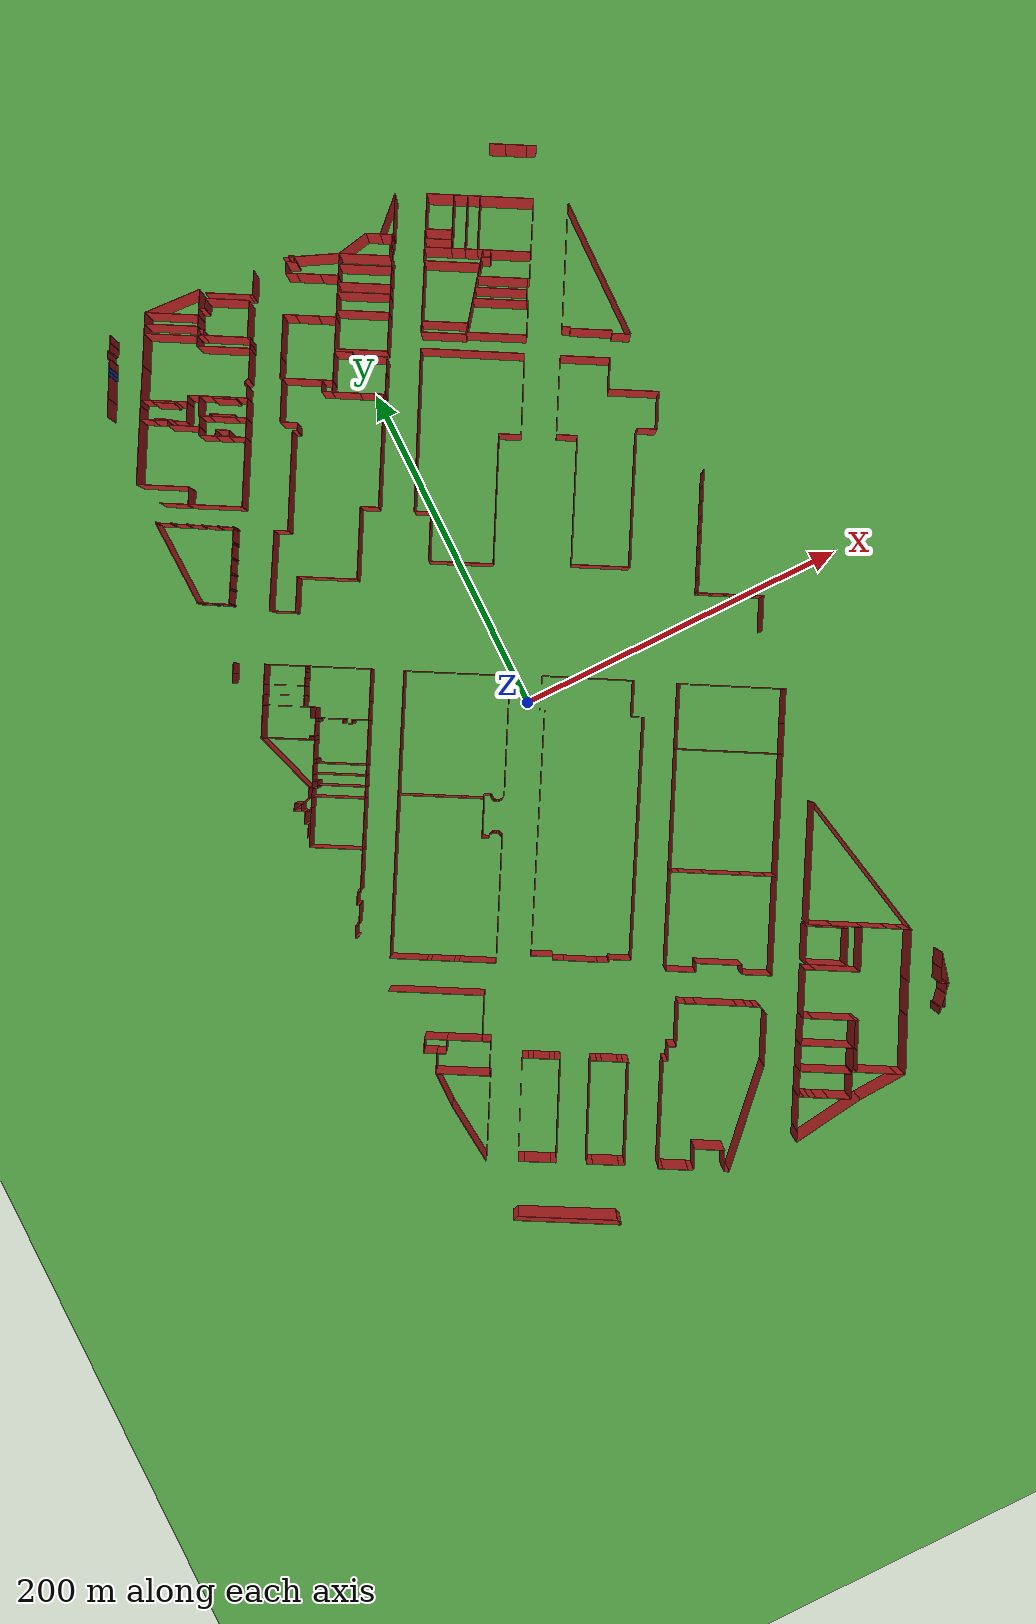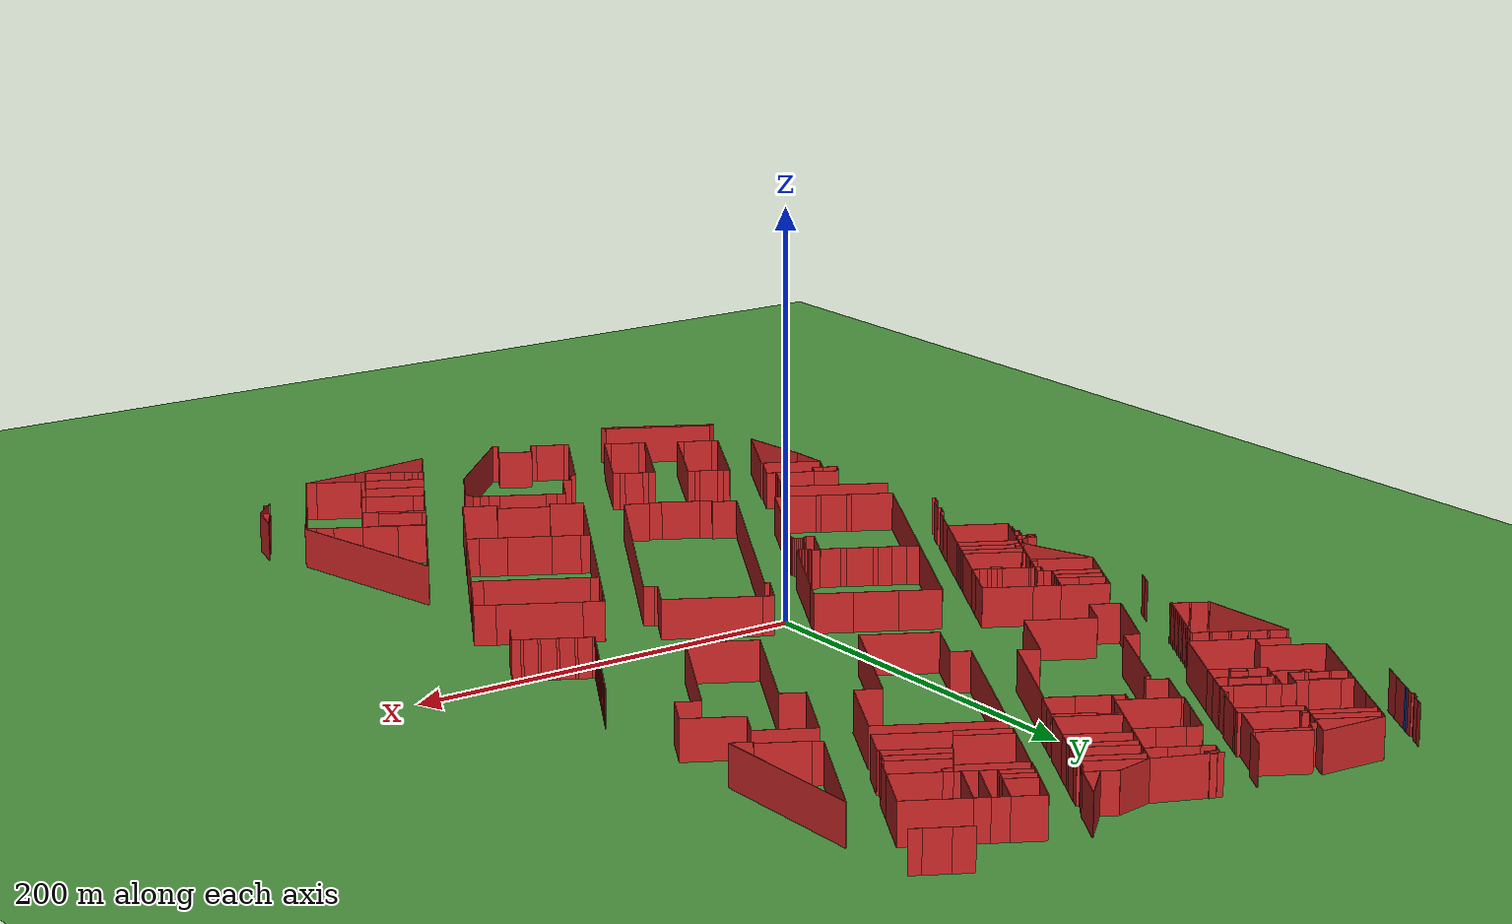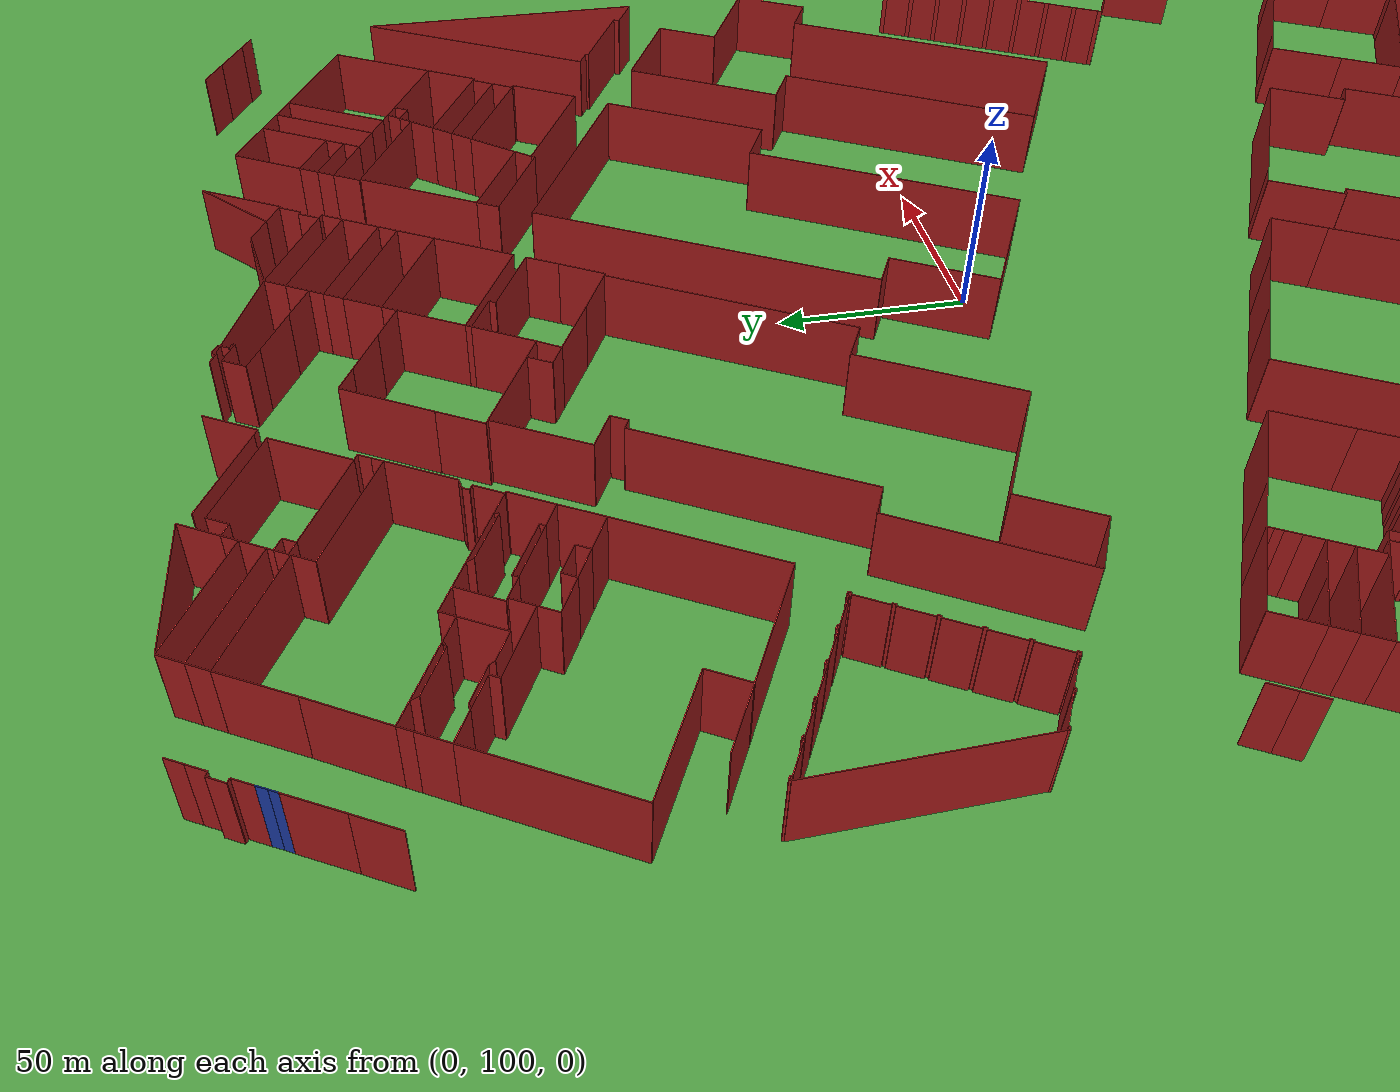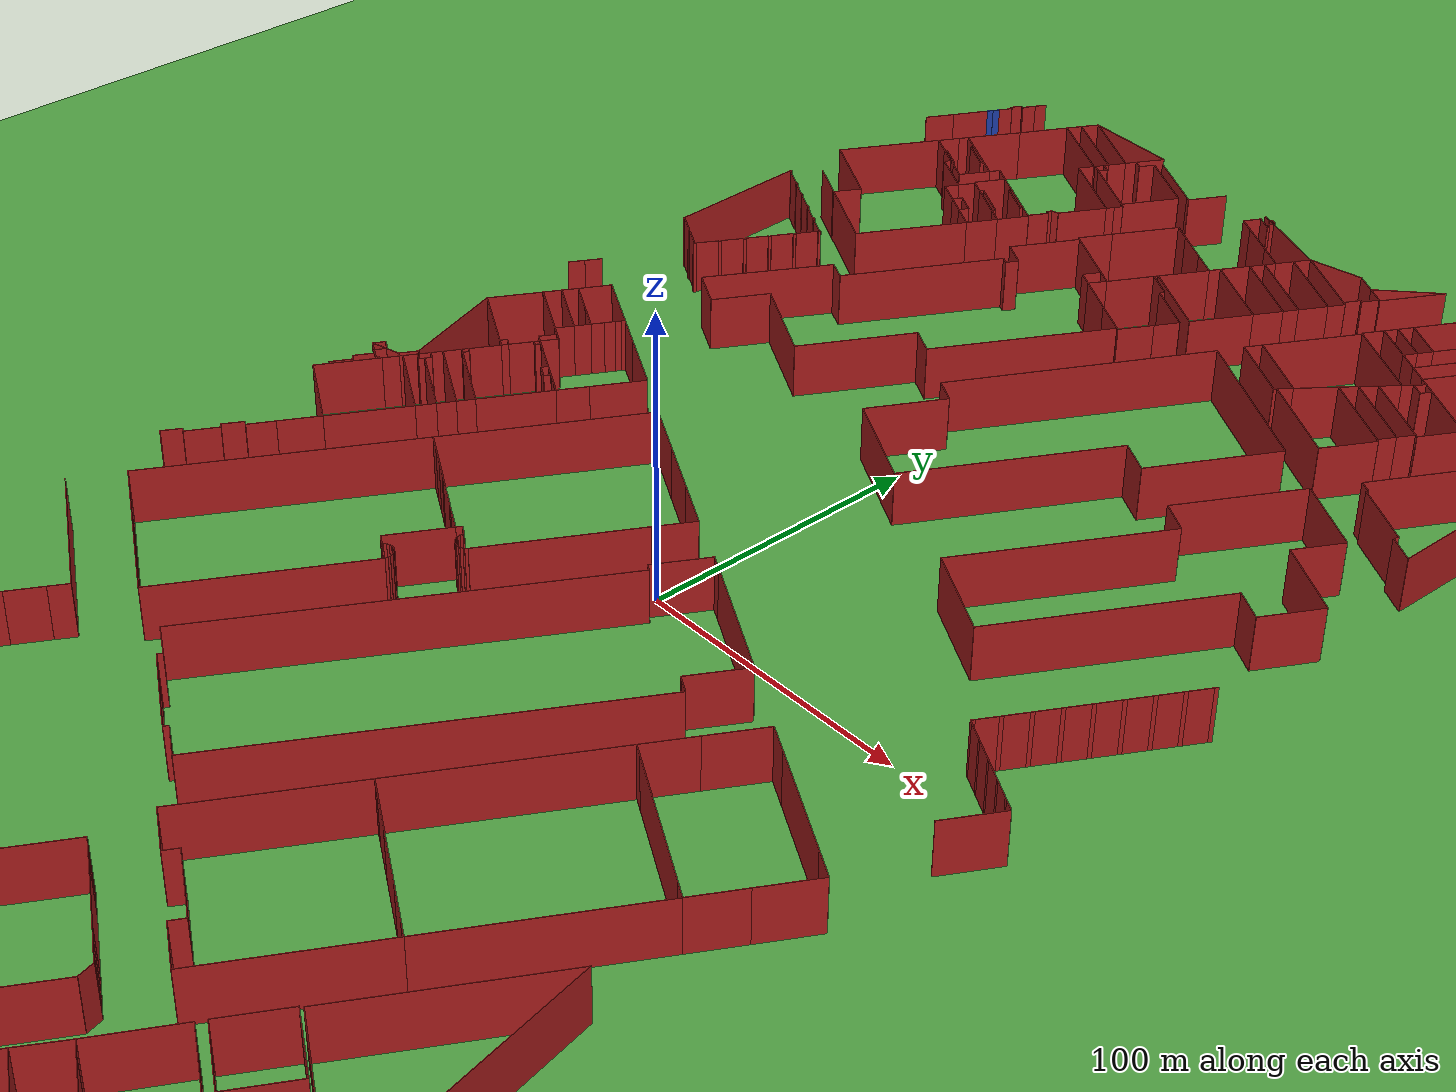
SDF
<sdf version="1.4">
 <world name="default">
  <spherical_coordinates>
   <surface_model>EARTH_WGS84</surface_model>
   <latitude_deg>40.75915</latitude_deg>
   <longitude_deg>-73.98055</longitude_deg>
   <elevation>0.0</elevation>
   <heading_deg>0</heading_deg>
  </spherical_coordinates>
  <model name="ground">
   <static>true</static>
   <link name="link">
    <collision name="collision">
     <geometry><plane><size>10000 10000</size><normal>0 0 1</normal></plane></geometry>
     <surface><friction><ode><mu>100</mu><mu2>50</mu2></ode></friction></surface>
    </collision>
    <visual name="visual">
     <pose>0 0 -1 0 0 0</pose>
     <geometry><plane><normal>0 0 1</normal><size>10000 10000</size></plane></geometry>
     <material>
      <script><uri>file://media/materials/scripts/gazebo.material</uri><name>Gazebo/Grass</name></script>
     </material>
    </visual>
   </link>
  </model>
  <scene><grid>false</grid><origin_visual>false</origin_visual></scene>
  <include><uri>model://sun</uri></include>
  <model name="office_building_266170578">
   <static>true</static>
   <pose>-125.952255844 289.017301661 0.0 0 0 0</pose>
   <link name="office_building_266170578_0">
    <collision name="office_building_266170578_0">
     <geometry><box><size>4.81621688001 0.2 20.0</size></box></geometry>
    </collision>
    <visual name="office_building_266170578_0">
     <geometry><box><size>4.81621688001 0.2 20.0</size></box></geometry>
     <material>
      <script><uri>file://media/materials/scripts/gazebo.material</uri><name>Gazebo/Red</name></script>
     </material>
    </visual>
    <pose>0.696842534385 0.53481557752 9.0 0 0 1.07510579999</pose>
   </link>
   <link name="office_building_266170578_1">
    <collision name="office_building_266170578_1">
     <geometry><box><size>1.07577772841 0.2 20.0</size></box></geometry>
    </collision>
    <visual name="office_building_266170578_1">
     <geometry><box><size>1.07577772841 0.2 20.0</size></box></geometry>
     <material>
      <script><uri>file://media/materials/scripts/gazebo.material</uri><name>Gazebo/Red</name></script>
     </material>
    </visual>
    <pose>-0.921116629011 -1.32654261835 9.0 0 0 -0.49795429977</pose>
   </link>
  </model>
  <model name="office_building_266170575">
   <static>true</static>
   <pose>-128.385688273 286.014695271 0.0 0 0 0</pose>
   <link name="office_building_266170575_0">
    <collision name="office_building_266170575_0">
     <geometry><box><size>4.38974615655 0.2 20.0</size></box></geometry>
    </collision>
    <visual name="office_building_266170575_0">
     <geometry><box><size>4.38974615655 0.2 20.0</size></box></geometry>
     <material>
      <script><uri>file://media/materials/scripts/gazebo.material</uri><name>Gazebo/Red</name></script>
     </material>
    </visual>
    <pose>0.0 0.0 9.0 0 0 1.0772903887</pose>
   </link>
  </model>
  <model name="The Muse Hotel">
   <static>true</static>
   <pose>-138.866614714 264.271799401 0.0 0 0 0</pose>
   <link name="The Muse Hotel_0">
    <collision name="The Muse Hotel_0">
     <geometry><box><size>13.1884343296 0.2 20.0</size></box></geometry>
    </collision>
    <visual name="The Muse Hotel_0">
     <geometry><box><size>13.1884343296 0.2 20.0</size></box></geometry>
     <material>
      <script><uri>file://media/materials/scripts/gazebo.material</uri><name>Gazebo/Red</name></script>
     </material>
    </visual>
    <pose>2.74113509899 5.06617953824 9.0 0 0 1.07998821693</pose>
   </link>
   <link name="The Muse Hotel_1">
    <collision name="The Muse Hotel_1">
     <geometry><box><size>10.6865483698 0.2 20.0</size></box></geometry>
    </collision>
    <visual name="The Muse Hotel_1">
     <geometry><box><size>10.6865483698 0.2 20.0</size></box></geometry>
     <material>
      <script><uri>file://media/materials/scripts/gazebo.material</uri><name>Gazebo/Red</name></script>
     </material>
    </visual>
    <pose>-2.92462260816 -5.44098211217 9.0 0 0 1.07166077882</pose>
   </link>
  </model>
  <model name="office_building_266170570">
   <static>true</static>
   <pose>-81.7936501681 229.378567488 0.0 0 0 0</pose>
   <link name="office_building_266170570_0">
    <collision name="office_building_266170570_0">
     <geometry><box><size>1.39700310273 0.2 20.0</size></box></geometry>
    </collision>
    <visual name="office_building_266170570_0">
     <geometry><box><size>1.39700310273 0.2 20.0</size></box></geometry>
     <material>
      <script><uri>file://media/materials/scripts/gazebo.material</uri><name>Gazebo/Red</name></script>
     </material>
    </visual>
    <pose>3.63251054344 -7.369670324 9.0 0 0 -2.0777974315</pose>
   </link>
   <link name="office_building_266170570_1">
    <collision name="office_building_266170570_1">
     <geometry><box><size>14.6986015448 0.2 20.0</size></box></geometry>
    </collision>
    <visual name="office_building_266170570_1">
     <geometry><box><size>14.6986015448 0.2 20.0</size></box></geometry>
     <material>
      <script><uri>file://media/materials/scripts/gazebo.material</uri><name>Gazebo/Red</name></script>
     </material>
    </visual>
    <pose>-2.4608443352 -3.20447137608 9.0 0 0 -0.504831986802</pose>
   </link>
   <link name="office_building_266170570_2">
    <collision name="office_building_266170570_2">
     <geometry><box><size>1.39700496269 0.2 20.0</size></box></geometry>
    </collision>
    <visual name="office_building_266170570_2">
     <geometry><box><size>1.39700496269 0.2 20.0</size></box></geometry>
     <material>
      <script><uri>file://media/materials/scripts/gazebo.material</uri><name>Gazebo/Red</name></script>
     </material>
    </visual>
    <pose>-9.23252553549 -0.260539667054 9.0 0 0 1.06379499911</pose>
   </link>
   <link name="office_building_266170570_3">
    <collision name="office_building_266170570_3">
     <geometry><box><size>5.76691093643 0.2 20.0</size></box></geometry>
    </collision>
    <visual name="office_building_266170570_3">
     <geometry><box><size>5.76691093643 0.2 20.0</size></box></geometry>
     <material>
      <script><uri>file://media/materials/scripts/gazebo.material</uri><name>Gazebo/Red</name></script>
     </material>
    </visual>
    <pose>-12.0957704683 0.522859389206 9.0 0 0 -0.504602122453</pose>
   </link>
   <link name="office_building_266170570_4">
    <collision name="office_building_266170570_4">
     <geometry><box><size>0.833846281988 0.2 20.0</size></box></geometry>
    </collision>
    <visual name="office_building_266170570_4">
     <geometry><box><size>0.833846281988 0.2 20.0</size></box></geometry>
     <material>
      <script><uri>file://media/materials/scripts/gazebo.material</uri><name>Gazebo/Red</name></script>
     </material>
    </visual>
    <pose>-14.9867890051 2.11483712402 9.0 0 0 -0.494708380203</pose>
   </link>
   <link name="office_building_266170570_5">
    <collision name="office_building_266170570_5">
     <geometry><box><size>11.4798929071 0.2 20.0</size></box></geometry>
    </collision>
    <visual name="office_building_266170570_5">
     <geometry><box><size>11.4798929071 0.2 20.0</size></box></geometry>
     <material>
      <script><uri>file://media/materials/scripts/gazebo.material</uri><name>Gazebo/Red</name></script>
     </material>
    </visual>
    <pose>-12.5625727852 7.32840228102 9.0 0 0 -2.07861022507</pose>
   </link>
   <link name="office_building_266170570_6">
    <collision name="office_building_266170570_6">
     <geometry><box><size>6.80532004535 0.2 20.0</size></box></geometry>
    </collision>
    <visual name="office_building_266170570_6">
     <geometry><box><size>6.80532004535 0.2 20.0</size></box></geometry>
     <material>
      <script><uri>file://media/materials/scripts/gazebo.material</uri><name>Gazebo/Red</name></script>
     </material>
    </visual>
    <pose>-6.79144881949 10.7015033614 9.0 0 0 2.63783901698</pose>
   </link>
   <link name="office_building_266170570_7">
    <collision name="office_building_266170570_7">
     <geometry><box><size>1.78837437508 0.2 20.0</size></box></geometry>
    </collision>
    <visual name="office_building_266170570_7">
     <geometry><box><size>1.78837437508 0.2 20.0</size></box></geometry>
     <material>
      <script><uri>file://media/materials/scripts/gazebo.material</uri><name>Gazebo/Red</name></script>
     </material>
    </visual>
    <pose>-3.47792002104 8.22933964613 9.0 0 0 1.95306828924</pose>
   </link>
   <link name="office_building_266170570_8">
    <collision name="office_building_266170570_8">
     <geometry><box><size>13.1072693143 0.2 20.0</size></box></geometry>
    </collision>
    <visual name="office_building_266170570_8">
     <geometry><box><size>13.1072693143 0.2 20.0</size></box></geometry>
     <material>
      <script><uri>file://media/materials/scripts/gazebo.material</uri><name>Gazebo/Red</name></script>
     </material>
    </visual>
    <pose>2.59319621351 4.23259032946 9.0 0 0 2.63721885062</pose>
   </link>
   <link name="office_building_266170570_9">
    <collision name="office_building_266170570_9">
     <geometry><box><size>1.12604697688 0.2 20.0</size></box></geometry>
    </collision>
    <visual name="office_building_266170570_9">
     <geometry><box><size>1.12604697688 0.2 20.0</size></box></geometry>
     <material>
      <script><uri>file://media/materials/scripts/gazebo.material</uri><name>Gazebo/Red</name></script>
     </material>
    </visual>
    <pose>8.60319730164 1.55820258264 9.0 0 0 -2.07589376781</pose>
   </link>
   <link name="office_building_266170570_10">
    <collision name="office_building_266170570_10">
     <geometry><box><size>5.85540222931 0.2 20.0</size></box></geometry>
    </collision>
    <visual name="office_building_266170570_10">
     <geometry><box><size>5.85540222931 0.2 20.0</size></box></geometry>
     <material>
      <script><uri>file://media/materials/scripts/gazebo.material</uri><name>Gazebo/Red</name></script>
     </material>
    </visual>
    <pose>11.4386392922 0.635833320226 9.0 0 0 2.63712221976</pose>
   </link>
   <link name="office_building_266170570_11">
    <collision name="office_building_266170570_11">
     <geometry><box><size>0.558584636573 0.2 20.0</size></box></geometry>
    </collision>
    <visual name="office_building_266170570_11">
     <geometry><box><size>0.558584636573 0.2 20.0</size></box></geometry>
     <material>
      <script><uri>file://media/materials/scripts/gazebo.material</uri><name>Gazebo/Red</name></script>
     </material>
    </visual>
    <pose>14.2462629911 -0.91402323997 9.0 0 0 2.63803889244</pose>
   </link>
   <link name="office_building_266170570_12">
    <collision name="office_building_266170570_12">
     <geometry><box><size>11.4798641348 0.2 20.0</size></box></geometry>
    </collision>
    <visual name="office_building_266170570_12">
     <geometry><box><size>11.4798641348 0.2 20.0</size></box></geometry>
     <material>
      <script><uri>file://media/materials/scripts/gazebo.material</uri><name>Gazebo/Red</name></script>
     </material>
    </visual>
    <pose>11.6997434728 -6.06440235666 9.0 0 0 1.06298284551</pose>
   </link>
   <link name="office_building_266170570_13">
    <collision name="office_building_266170570_13">
     <geometry><box><size>6.41398778348 0.2 20.0</size></box></geometry>
    </collision>
    <visual name="office_building_266170570_13">
     <geometry><box><size>6.41398778348 0.2 20.0</size></box></geometry>
     <material>
      <script><uri>file://media/materials/scripts/gazebo.material</uri><name>Gazebo/Red</name></script>
     </material>
    </visual>
    <pose>6.1009734788 -9.53015749556 9.0 0 0 -0.504389564677</pose>
   </link>
  </model>
  <model name="office_building_266170573">
   <static>true</static>
   <pose>-129.562643282 282.318567619 0.0 0 0 0</pose>
   <link name="office_building_266170573_0">
    <collision name="office_building_266170573_0">
     <geometry><box><size>1.07178069066 0.2 20.0</size></box></geometry>
    </collision>
    <visual name="office_building_266170573_0">
     <geometry><box><size>1.07178069066 0.2 20.0</size></box></geometry>
     <material>
      <script><uri>file://media/materials/scripts/gazebo.material</uri><name>Gazebo/Red</name></script>
     </material>
    </visual>
    <pose>0.609776385693 1.51045249202 9.0 0 0 2.65054324767</pose>
   </link>
   <link name="office_building_266170573_1">
    <collision name="office_building_266170573_1">
     <geometry><box><size>4.85856402104 0.2 20.0</size></box></geometry>
    </collision>
    <visual name="office_building_266170573_1">
     <geometry><box><size>4.85856402104 0.2 20.0</size></box></geometry>
     <material>
      <script><uri>file://media/materials/scripts/gazebo.material</uri><name>Gazebo/Red</name></script>
     </material>
    </visual>
    <pose>-0.0686038249688 -0.881576208618 9.0 0 0 1.07721642643</pose>
   </link>
  </model>
  <model name="Time-Life Building">
   <static>true</static>
   <pose>133.247665459 27.8378512148 0.0 0 0 0</pose>
   <link name="Time-Life Building_0">
    <collision name="Time-Life Building_0">
     <geometry><box><size>1.32923246951 0.2 20.0</size></box></geometry>
    </collision>
    <visual name="Time-Life Building_0">
     <geometry><box><size>1.32923246951 0.2 20.0</size></box></geometry>
     <material>
      <script><uri>file://media/materials/scripts/gazebo.material</uri><name>Gazebo/Red</name></script>
     </material>
    </visual>
    <pose>16.5434005203 47.1384278914 9.0 0 0 1.06420550392</pose>
   </link>
   <link name="Time-Life Building_1">
    <collision name="Time-Life Building_1">
     <geometry><box><size>7.48111101562 0.2 20.0</size></box></geometry>
    </collision>
    <visual name="Time-Life Building_1">
     <geometry><box><size>7.48111101562 0.2 20.0</size></box></geometry>
     <material>
      <script><uri>file://media/materials/scripts/gazebo.material</uri><name>Gazebo/Red</name></script>
     </material>
    </visual>
    <pose>14.4084205477 43.2851958384 9.0 0 0 1.06494074451</pose>
   </link>
   <link name="Time-Life Building_2">
    <collision name="Time-Life Building_2">
     <geometry><box><size>1.31648542399 0.2 20.0</size></box></geometry>
    </collision>
    <visual name="Time-Life Building_2">
     <geometry><box><size>1.31648542399 0.2 20.0</size></box></geometry>
     <material>
      <script><uri>file://media/materials/scripts/gazebo.material</uri><name>Gazebo/Red</name></script>
     </material>
    </visual>
    <pose>12.2790009652 39.43617427 9.0 0 0 1.06848828753</pose>
   </link>
   <link name="Time-Life Building_3">
    <collision name="Time-Life Building_3">
     <geometry><box><size>7.47914735165 0.2 20.0</size></box></geometry>
    </collision>
    <visual name="Time-Life Building_3">
     <geometry><box><size>7.47914735165 0.2 20.0</size></box></geometry>
     <material>
      <script><uri>file://media/materials/scripts/gazebo.material</uri><name>Gazebo/Red</name></script>
     </material>
    </visual>
    <pose>10.1440250787 35.5913601826 9.0 0 0 1.06309582887</pose>
   </link>
   <link name="Time-Life Building_4">
    <collision name="Time-Life Building_4">
     <geometry><box><size>1.31648600865 0.2 20.0</size></box></geometry>
    </collision>
    <visual name="Time-Life Building_4">
     <geometry><box><size>1.31648600865 0.2 20.0</size></box></geometry>
     <material>
      <script><uri>file://media/materials/scripts/gazebo.material</uri><name>Gazebo/Red</name></script>
     </material>
    </visual>
    <pose>8.00904979308 31.7465454316 9.0 0 0 1.06848957315</pose>
   </link>
   <link name="Time-Life Building_5">
    <collision name="Time-Life Building_5">
     <geometry><box><size>7.49585734438 0.2 20.0</size></box></geometry>
    </collision>
    <visual name="Time-Life Building_5">
     <geometry><box><size>7.49585734438 0.2 20.0</size></box></geometry>
     <material>
      <script><uri>file://media/materials/scripts/gazebo.material</uri><name>Gazebo/Red</name></script>
     </material>
    </visual>
    <pose>5.8796375635 27.8890932282 9.0 0 0 1.06603220093</pose>
   </link>
   <link name="Time-Life Building_6">
    <collision name="Time-Life Building_6">
     <geometry><box><size>1.32187590324 0.2 20.0</size></box></geometry>
    </collision>
    <visual name="Time-Life Building_6">
     <geometry><box><size>1.32187590324 0.2 20.0</size></box></geometry>
     <material>
      <script><uri>file://media/materials/scripts/gazebo.material</uri><name>Gazebo/Red</name></script>
     </material>
    </visual>
    <pose>3.7446661895 24.0316404007 9.0 0 0 1.06111794173</pose>
   </link>
   <link name="Time-Life Building_7">
    <collision name="Time-Life Building_7">
     <geometry><box><size>7.48651516969 0.2 20.0</size></box></geometry>
    </collision>
    <visual name="Time-Life Building_7">
     <geometry><box><size>7.48651516969 0.2 20.0</size></box></geometry>
     <material>
      <script><uri>file://media/materials/scripts/gazebo.material</uri><name>Gazebo/Red</name></script>
     </material>
    </visual>
    <pose>1.60413854449 20.1826062465 9.0 0 0 1.06364534202</pose>
   </link>
   <link name="Time-Life Building_8">
    <collision name="Time-Life Building_8">
     <geometry><box><size>1.31648717643 0.2 20.0</size></box></geometry>
    </collision>
    <visual name="Time-Life Building_8">
     <geometry><box><size>1.31648717643 0.2 20.0</size></box></geometry>
     <material>
      <script><uri>file://media/materials/scripts/gazebo.material</uri><name>Gazebo/Red</name></script>
     </material>
    </visual>
    <pose>-0.530828753429 16.3335713894 9.0 0 0 1.06849214501</pose>
   </link>
   <link name="Time-Life Building_9">
    <collision name="Time-Life Building_9">
     <geometry><box><size>7.48651847286 0.2 20.0</size></box></geometry>
    </collision>
    <visual name="Time-Life Building_9">
     <geometry><box><size>7.48651847286 0.2 20.0</size></box></geometry>
     <material>
      <script><uri>file://media/materials/scripts/gazebo.material</uri><name>Gazebo/Red</name></script>
     </material>
    </visual>
    <pose>-2.66579264316 12.4845327493 9.0 0 0 1.06364662876</pose>
   </link>
   <link name="Time-Life Building_10">
    <collision name="Time-Life Building_10">
     <geometry><box><size>1.31648776103 0.2 20.0</size></box></geometry>
    </collision>
    <visual name="Time-Life Building_10">
     <geometry><box><size>1.31648776103 0.2 20.0</size></box></geometry>
     <material>
      <script><uri>file://media/materials/scripts/gazebo.material</uri><name>Gazebo/Red</name></script>
     </material>
    </visual>
    <pose>-4.80075593236 8.63549344577 9.0 0 0 1.06849342981</pose>
   </link>
   <link name="Time-Life Building_11">
    <collision name="Time-Life Building_11">
     <geometry><box><size>7.49388524187 0.2 20.0</size></box></geometry>
    </collision>
    <visual name="Time-Life Building_11">
     <geometry><box><size>7.49388524187 0.2 20.0</size></box></geometry>
     <material>
      <script><uri>file://media/materials/scripts/gazebo.material</uri><name>Gazebo/Red</name></script>
     </material>
    </visual>
    <pose>-6.93571583034 4.7822391393 9.0 0 0 1.06419377872</pose>
   </link>
   <link name="Time-Life Building_12">
    <collision name="Time-Life Building_12">
     <geometry><box><size>1.31648834429 0.2 20.0</size></box></geometry>
    </collision>
    <visual name="Time-Life Building_12">
     <geometry><box><size>1.31648834429 0.2 20.0</size></box></geometry>
     <material>
      <script><uri>file://media/materials/scripts/gazebo.material</uri><name>Gazebo/Red</name></script>
     </material>
    </visual>
    <pose>-9.07067512678 0.92898416969 9.0 0 0 1.0684947158</pose>
   </link>
   <link name="Time-Life Building_13">
    <collision name="Time-Life Building_13">
     <geometry><box><size>7.48849962328 0.2 20.0</size></box></geometry>
    </collision>
    <visual name="Time-Life Building_13">
     <geometry><box><size>7.48849962328 0.2 20.0</size></box></geometry>
     <material>
      <script><uri>file://media/materials/scripts/gazebo.material</uri><name>Gazebo/Red</name></script>
     </material>
    </visual>
    <pose>-11.200071261 -2.92427460444 9.0 0 0 1.06549344239</pose>
   </link>
   <link name="Time-Life Building_14">
    <collision name="Time-Life Building_14">
     <geometry><box><size>1.32387723038 0.2 20.0</size></box></geometry>
    </collision>
    <visual name="Time-Life Building_14">
     <geometry><box><size>1.32387723038 0.2 20.0</size></box></geometry>
     <material>
      <script><uri>file://media/materials/scripts/gazebo.material</uri><name>Gazebo/Red</name></script>
     </material>
    </visual>
    <pose>-13.329466805 -6.78174526381 9.0 0 0 1.07155890913</pose>
   </link>
   <link name="Time-Life Building_15">
    <collision name="Time-Life Building_15">
     <geometry><box><size>6.82190994577 0.2 20.0</size></box></geometry>
    </collision>
    <visual name="Time-Life Building_15">
     <geometry><box><size>6.82190994577 0.2 20.0</size></box></geometry>
     <material>
      <script><uri>file://media/materials/scripts/gazebo.material</uri><name>Gazebo/Red</name></script>
     </material>
    </visual>
    <pose>-15.303185465 -10.344434367 9.0 0 0 1.06359543113</pose>
   </link>
   <link name="Time-Life Building_16">
    <collision name="Time-Life Building_16">
     <geometry><box><size>1.32187876863 0.2 20.0</size></box></geometry>
    </collision>
    <visual name="Time-Life Building_16">
     <geometry><box><size>1.32187876863 0.2 20.0</size></box></geometry>
     <material>
      <script><uri>file://media/materials/scripts/gazebo.material</uri><name>Gazebo/Red</name></script>
     </material>
    </visual>
    <pose>-17.2824633035 -13.9029128519 9.0 0 0 1.06112428561</pose>
   </link>
   <link name="Time-Life Building_17">
    <collision name="Time-Life Building_17">
     <geometry><box><size>1.31204628246 0.2 20.0</size></box></geometry>
    </collision>
    <visual name="Time-Life Building_17">
     <geometry><box><size>1.31204628246 0.2 20.0</size></box></geometry>
     <material>
      <script><uri>file://media/materials/scripts/gazebo.material</uri><name>Gazebo/Red</name></script>
     </material>
    </visual>
    <pose>-17.0322763705 -14.7999038375 9.0 0 0 2.63194471559</pose>
   </link>
   <link name="Time-Life Building_18">
    <collision name="Time-Life Building_18">
     <geometry><box><size>6.42775355637 0.2 20.0</size></box></geometry>
    </collision>
    <visual name="Time-Life Building_18">
     <geometry><box><size>6.42775355637 0.2 20.0</size></box></geometry>
     <material>
      <script><uri>file://media/materials/scripts/gazebo.material</uri><name>Gazebo/Red</name></script>
     </material>
    </visual>
    <pose>-13.6463937657 -16.673902756 9.0 0 0 2.63693128562</pose>
   </link>
   <link name="Time-Life Building_19">
    <collision name="Time-Life Building_19">
     <geometry><box><size>1.3217635268 0.2 20.0</size></box></geometry>
    </collision>
    <visual name="Time-Life Building_19">
     <geometry><box><size>1.3217635268 0.2 20.0</size></box></geometry>
     <material>
      <script><uri>file://media/materials/scripts/gazebo.material</uri><name>Gazebo/Red</name></script>
     </material>
    </visual>
    <pose>-10.2549512524 -18.5479010977 9.0 0 0 2.63604987267</pose>
   </link>
   <link name="Time-Life Building_20">
    <collision name="Time-Life Building_20">
     <geometry><box><size>7.05536742302 0.2 20.0</size></box></geometry>
    </collision>
    <visual name="Time-Life Building_20">
     <geometry><box><size>7.05536742302 0.2 20.0</size></box></geometry>
     <material>
      <script><uri>file://media/materials/scripts/gazebo.material</uri><name>Gazebo/Red</name></script>
     </material>
    </visual>
    <pose>-6.59108050139 -20.5777117792 9.0 0 0 2.63560847997</pose>
   </link>
   <link name="Time-Life Building_21">
    <collision name="Time-Life Building_21">
     <geometry><box><size>1.31204568618 0.2 20.0</size></box></geometry>
    </collision>
    <visual name="Time-Life Building_21">
     <geometry><box><size>1.31204568618 0.2 20.0</size></box></geometry>
     <material>
      <script><uri>file://media/materials/scripts/gazebo.material</uri><name>Gazebo/Red</name></script>
     </material>
    </visual>
    <pose>-2.93276932113 -22.6075218222 9.0 0 0 2.63194658397</pose>
   </link>
   <link name="Time-Life Building_22">
    <collision name="Time-Life Building_22">
     <geometry><box><size>7.06917433792 0.2 20.0</size></box></geometry>
    </collision>
    <visual name="Time-Life Building_22">
     <geometry><box><size>7.06917433792 0.2 20.0</size></box></geometry>
     <material>
      <script><uri>file://media/materials/scripts/gazebo.material</uri><name>Gazebo/Red</name></script>
     </material>
    </visual>
    <pose>0.731102544268 -24.6415396904 9.0 0 0 2.63532966755</pose>
   </link>
   <link name="Time-Life Building_23">
    <collision name="Time-Life Building_23">
     <geometry><box><size>1.3177047012 0.2 20.0</size></box></geometry>
    </collision>
    <visual name="Time-Life Building_23">
     <geometry><box><size>1.3177047012 0.2 20.0</size></box></geometry>
     <material>
      <script><uri>file://media/materials/scripts/gazebo.material</uri><name>Gazebo/Red</name></script>
     </material>
    </visual>
    <pose>4.40053433287 -26.6713457161 9.0 0 0 2.64164405335</pose>
   </link>
   <link name="Time-Life Building_24">
    <collision name="Time-Life Building_24">
     <geometry><box><size>6.408291557 0.2 20.0</size></box></geometry>
    </collision>
    <visual name="Time-Life Building_24">
     <geometry><box><size>6.408291557 0.2 20.0</size></box></geometry>
     <material>
      <script><uri>file://media/materials/scripts/gazebo.material</uri><name>Gazebo/Red</name></script>
     </material>
    </visual>
    <pose>7.78086020072 -28.541122556 9.0 0 0 2.63525617529</pose>
   </link>
   <link name="Time-Life Building_25">
    <collision name="Time-Life Building_25">
     <geometry><box><size>1.31617464383 0.2 20.0</size></box></geometry>
    </collision>
    <visual name="Time-Life Building_25">
     <geometry><box><size>1.31617464383 0.2 20.0</size></box></geometry>
     <material>
      <script><uri>file://media/materials/scripts/gazebo.material</uri><name>Gazebo/Red</name></script>
     </material>
    </visual>
    <pose>11.1556264855 -30.4193212303 9.0 0 0 2.62636248061</pose>
   </link>
   <link name="Time-Life Building_26">
    <collision name="Time-Life Building_26">
     <geometry><box><size>4.08705767543 0.2 20.0</size></box></geometry>
    </collision>
    <visual name="Time-Life Building_26">
     <geometry><box><size>4.08705767543 0.2 20.0</size></box></geometry>
     <material>
      <script><uri>file://media/materials/scripts/gazebo.material</uri><name>Gazebo/Red</name></script>
     </material>
    </visual>
    <pose>13.5185193088 -31.729005225 9.0 0 0 2.63841076283</pose>
   </link>
   <link name="Time-Life Building_27">
    <collision name="Time-Life Building_27">
     <geometry><box><size>20.6801956896 0.2 20.0</size></box></geometry>
    </collision>
    <visual name="Time-Life Building_27">
     <geometry><box><size>20.6801956896 0.2 20.0</size></box></geometry>
     <material>
      <script><uri>file://media/materials/scripts/gazebo.material</uri><name>Gazebo/Red</name></script>
     </material>
    </visual>
    <pose>10.2994437395 -41.7601101072 9.0 0 0 1.06505599978</pose>
   </link>
  </model>
  <model name="office_building_266151939">
   <static>true</static>
   <pose>126.084285854 295.774875327 0.0 0 0 0</pose>
   <link name="office_building_266151939_0">
    <collision name="office_building_266151939_0">
     <geometry><box><size>9.4626025902 0.2 20.0</size></box></geometry>
    </collision>
    <visual name="office_building_266151939_0">
     <geometry><box><size>9.4626025902 0.2 20.0</size></box></geometry>
     <material>
      <script><uri>file://media/materials/scripts/gazebo.material</uri><name>Gazebo/Red</name></script>
     </material>
    </visual>
    <pose>0.0 0.0 9.0 0 0 -0.504473158442</pose>
   </link>
  </model>
  <model name="The British Empire Building">
   <static>true</static>
   <pose>-58.5487491288 -224.991116498 0.0 0 0 0</pose>
   <link name="The British Empire Building_0">
    <collision name="The British Empire Building_0">
     <geometry><box><size>59.2292714191 0.2 20.0</size></box></geometry>
    </collision>
    <visual name="The British Empire Building_0">
     <geometry><box><size>59.2292714191 0.2 20.0</size></box></geometry>
     <material>
      <script><uri>file://media/materials/scripts/gazebo.material</uri><name>Gazebo/Red</name></script>
     </material>
    </visual>
    <pose>4.9065977847 -11.8746312968 9.0 0 0 1.0731193368</pose>
   </link>
   <link name="The British Empire Building_1">
    <collision name="The British Empire Building_1">
     <geometry><box><size>3.441678412 0.2 20.0</size></box></geometry>
    </collision>
    <visual name="The British Empire Building_1">
     <geometry><box><size>3.441678412 0.2 20.0</size></box></geometry>
     <material>
      <script><uri>file://media/materials/scripts/gazebo.material</uri><name>Gazebo/Red</name></script>
     </material>
    </visual>
    <pose>-10.743283378 -37.0756756051 9.0 0 0 -0.497446633622</pose>
   </link>
   <link name="The British Empire Building_2">
    <collision name="The British Empire Building_2">
     <geometry><box><size>15.0608652066 0.2 20.0</size></box></geometry>
    </collision>
    <visual name="The British Empire Building_2">
     <geometry><box><size>15.0608652066 0.2 20.0</size></box></geometry>
     <material>
      <script><uri>file://media/materials/scripts/gazebo.material</uri><name>Gazebo/Red</name></script>
     </material>
    </visual>
    <pose>-18.8717869909 -32.6582717638 9.0 0 0 -0.497877714688</pose>
   </link>
   <link name="The British Empire Building_3">
    <collision name="The British Empire Building_3">
     <geometry><box><size>3.44168013574 0.2 20.0</size></box></geometry>
    </collision>
    <visual name="The British Empire Building_3">
     <geometry><box><size>3.44168013574 0.2 20.0</size></box></geometry>
     <material>
      <script><uri>file://media/materials/scripts/gazebo.material</uri><name>Gazebo/Red</name></script>
     </material>
    </visual>
    <pose>-27.0002896221 -28.2408643085 9.0 0 0 -0.497448751407</pose>
   </link>
   <link name="The British Empire Building_4">
    <collision name="The British Empire Building_4">
     <geometry><box><size>59.2844128936 0.2 20.0</size></box></geometry>
    </collision>
    <visual name="The British Empire Building_4">
     <geometry><box><size>59.2844128936 0.2 20.0</size></box></geometry>
     <material>
      <script><uri>file://media/materials/scripts/gazebo.material</uri><name>Gazebo/Red</name></script>
     </material>
    </visual>
    <pose>-14.3638120192 -1.37218923215 9.0 0 0 -2.06839629517</pose>
   </link>
   <link name="The British Empire Building_5">
    <collision name="The British Empire Building_5">
     <geometry><box><size>3.44167713498 0.2 20.0</size></box></geometry>
    </collision>
    <visual name="The British Empire Building_5">
     <geometry><box><size>3.44167713498 0.2 20.0</size></box></geometry>
     <material>
      <script><uri>file://media/materials/scripts/gazebo.material</uri><name>Gazebo/Red</name></script>
     </material>
    </visual>
    <pose>1.29721806807 23.8541600246 9.0 0 0 2.64413846025</pose>
   </link>
   <link name="The British Empire Building_6">
    <collision name="The British Empire Building_6">
     <geometry><box><size>2.84977285978 0.2 20.0</size></box></geometry>
    </collision>
    <visual name="The British Empire Building_6">
     <geometry><box><size>2.84977285978 0.2 20.0</size></box></geometry>
     <material>
      <script><uri>file://media/materials/scripts/gazebo.material</uri><name>Gazebo/Red</name></script>
     </material>
    </visual>
    <pose>4.06045304463 22.3507937218 9.0 0 0 2.64233407972</pose>
   </link>
   <link name="The British Empire Building_7">
    <collision name="The British Empire Building_7">
     <geometry><box><size>9.33274493632 0.2 20.0</size></box></geometry>
    </collision>
    <visual name="The British Empire Building_7">
     <geometry><box><size>9.33274493632 0.2 20.0</size></box></geometry>
     <material>
      <script><uri>file://media/materials/scripts/gazebo.material</uri><name>Gazebo/Red</name></script>
     </material>
    </visual>
    <pose>9.39789088767 19.4156528626 9.0 0 0 2.63773935755</pose>
   </link>
   <link name="The British Empire Building_8">
    <collision name="The British Empire Building_8">
     <geometry><box><size>2.86931583484 0.2 20.0</size></box></geometry>
    </collision>
    <visual name="The British Empire Building_8">
     <geometry><box><size>2.86931583484 0.2 20.0</size></box></geometry>
     <material>
      <script><uri>file://media/materials/scripts/gazebo.material</uri><name>Gazebo/Red</name></script>
     </material>
    </visual>
    <pose>14.7464487658 16.4805142957 9.0 0 0 2.64604647464</pose>
   </link>
   <link name="The British Empire Building_9">
    <collision name="The British Empire Building_9">
     <geometry><box><size>3.45546710681 0.2 20.0</size></box></geometry>
    </collision>
    <visual name="The British Empire Building_9">
     <geometry><box><size>3.45546710681 0.2 20.0</size></box></geometry>
     <material>
      <script><uri>file://media/materials/scripts/gazebo.material</uri><name>Gazebo/Red</name></script>
     </material>
    </visual>
    <pose>17.5263646294 14.9729427512 9.0 0 0 2.64353420042</pose>
   </link>
  </model>
  <model name="office_building_266151931">
   <static>true</static>
   <pose>133.713943842 291.561953469 0.0 0 0 0</pose>
   <link name="office_building_266151931_0">
    <collision name="office_building_266151931_0">
     <geometry><box><size>11.9526738172 0.2 20.0</size></box></geometry>
    </collision>
    <visual name="office_building_266151931_0">
     <geometry><box><size>11.9526738172 0.2 20.0</size></box></geometry>
     <material>
      <script><uri>file://media/materials/scripts/gazebo.material</uri><name>Gazebo/Red</name></script>
     </material>
    </visual>
    <pose>1.74386923866 -0.963032453081 9.0 0 0 2.63703213266</pose>
   </link>
   <link name="office_building_266151931_1">
    <collision name="office_building_266151931_1">
     <geometry><box><size>11.9526738172 0.2 20.0</size></box></geometry>
    </collision>
    <visual name="office_building_266151931_1">
     <geometry><box><size>11.9526738172 0.2 20.0</size></box></geometry>
     <material>
      <script><uri>file://media/materials/scripts/gazebo.material</uri><name>Gazebo/Red</name></script>
     </material>
    </visual>
    <pose>1.74386923866 -0.963032453081 9.0 0 0 -0.504560520929</pose>
   </link>
  </model>
  <model name="office_building_266151932">
   <static>true</static>
   <pose>143.141216556 286.357930909 0.0 0 0 0</pose>
   <link name="office_building_266151932_0">
    <collision name="office_building_266151932_0">
     <geometry><box><size>5.59961300474 0.2 20.0</size></box></geometry>
    </collision>
    <visual name="office_building_266151932_0">
     <geometry><box><size>5.59961300474 0.2 20.0</size></box></geometry>
     <material>
      <script><uri>file://media/materials/scripts/gazebo.material</uri><name>Gazebo/Red</name></script>
     </material>
    </visual>
    <pose>0.0 0.0 9.0 0 0 -0.503908850876</pose>
   </link>
  </model>
  <model name="office_building_266170673">
   <static>true</static>
   <pose>-133.467087695 -51.8419113068 0.0 0 0 0</pose>
   <link name="office_building_266170673_0">
    <collision name="office_building_266170673_0">
     <geometry><box><size>9.57046490442 0.2 20.0</size></box></geometry>
    </collision>
    <visual name="office_building_266170673_0">
     <geometry><box><size>9.57046490442 0.2 20.0</size></box></geometry>
     <material>
      <script><uri>file://media/materials/scripts/gazebo.material</uri><name>Gazebo/Red</name></script>
     </material>
    </visual>
    <pose>1.27317436344 1.12023192378 9.0 0 0 1.06501905872</pose>
   </link>
   <link name="office_building_266170673_1">
    <collision name="office_building_266170673_1">
     <geometry><box><size>1.71310447526 0.2 20.0</size></box></geometry>
    </collision>
    <visual name="office_building_266170673_1">
     <geometry><box><size>1.71310447526 0.2 20.0</size></box></geometry>
     <material>
      <script><uri>file://media/materials/scripts/gazebo.material</uri><name>Gazebo/Red</name></script>
     </material>
    </visual>
    <pose>-1.79577992957 -2.65317223891 9.0 0 0 -0.502736365974</pose>
   </link>
  </model>
  <model name="office_building_266170671">
   <static>true</static>
   <pose>-147.989314854 -13.872265409 0.0 0 0 0</pose>
  </model>
  <model name="office_building_266170678">
   <static>true</static>
   <pose>-146.095301388 -8.93091840844 0.0 0 0 0</pose>
   <link name="office_building_266170678_0">
    <collision name="office_building_266170678_0">
     <geometry><box><size>2.19699793983 0.2 20.0</size></box></geometry>
    </collision>
    <visual name="office_building_266170678_0">
     <geometry><box><size>2.19699793983 0.2 20.0</size></box></geometry>
     <material>
      <script><uri>file://media/materials/scripts/gazebo.material</uri><name>Gazebo/Red</name></script>
     </material>
    </visual>
    <pose>0.947006733361 2.47067350026 9.0 0 0 2.63745570477</pose>
   </link>
   <link name="office_building_266170678_1">
    <collision name="office_building_266170678_1">
     <geometry><box><size>7.8622659953 0.2 20.0</size></box></geometry>
    </collision>
    <visual name="office_building_266170678_1">
     <geometry><box><size>7.8622659953 0.2 20.0</size></box></geometry>
     <material>
      <script><uri>file://media/materials/scripts/gazebo.material</uri><name>Gazebo/Red</name></script>
     </material>
    </visual>
    <pose>0.00741492303723 -1.50065277931 9.0 0 0 1.06593671188</pose>
   </link>
  </model>
  <model name="office_building_266170679">
   <static>true</static>
   <pose>-134.067640427 -33.0929005732 0.0 0 0 0</pose>
   <link name="office_building_266170679_0">
    <collision name="office_building_266170679_0">
     <geometry><box><size>30.5387298303 0.2 20.0</size></box></geometry>
    </collision>
    <visual name="office_building_266170679_0">
     <geometry><box><size>30.5387298303 0.2 20.0</size></box></geometry>
     <material>
      <script><uri>file://media/materials/scripts/gazebo.material</uri><name>Gazebo/Red</name></script>
     </material>
    </visual>
    <pose>-2.09605629576 6.72133312792 9.0 0 0 2.63916750768</pose>
   </link>
   <link name="office_building_266170679_1">
    <collision name="office_building_266170679_1">
     <geometry><box><size>14.644074832 0.2 20.0</size></box></geometry>
    </collision>
    <visual name="office_building_266170679_1">
     <geometry><box><size>14.644074832 0.2 20.0</size></box></geometry>
     <material>
      <script><uri>file://media/materials/scripts/gazebo.material</uri><name>Gazebo/Red</name></script>
     </material>
    </visual>
    <pose>7.73919597546 -7.03716616698 9.0 0 0 1.06507409138</pose>
   </link>
  </model>
  <model name="office_building_266170569">
   <static>true</static>
   <pose>-88.5199435659 219.577163471 0.0 0 0 0</pose>
   <link name="office_building_266170569_0">
    <collision name="office_building_266170569_0">
     <geometry><box><size>3.64909950902 0.2 20.0</size></box></geometry>
    </collision>
    <visual name="office_building_266170569_0">
     <geometry><box><size>3.64909950902 0.2 20.0</size></box></geometry>
     <material>
      <script><uri>file://media/materials/scripts/gazebo.material</uri><name>Gazebo/Red</name></script>
     </material>
    </visual>
    <pose>2.79733237666 -4.90419078675 9.0 0 0 -2.07662020923</pose>
   </link>
   <link name="office_building_266170569_1">
    <collision name="office_building_266170569_1">
     <geometry><box><size>7.9817855313 0.2 20.0</size></box></geometry>
    </collision>
    <visual name="office_building_266170569_1">
     <geometry><box><size>7.9817855313 0.2 20.0</size></box></geometry>
     <material>
      <script><uri>file://media/materials/scripts/gazebo.material</uri><name>Gazebo/Red</name></script>
     </material>
    </visual>
    <pose>0.18991476499 -1.37501116452 9.0 0 0 -0.505654175781</pose>
   </link>
   <link name="office_building_266170569_2">
    <collision name="office_building_266170569_2">
     <geometry><box><size>3.6545025171 0.2 20.0</size></box></geometry>
    </collision>
    <visual name="office_building_266170569_2">
     <geometry><box><size>3.6545025171 0.2 20.0</size></box></geometry>
     <material>
      <script><uri>file://media/materials/scripts/gazebo.material</uri><name>Gazebo/Red</name></script>
     </material>
    </visual>
    <pose>-4.19115547094 -1.03797555307 9.0 0 0 1.06231061086</pose>
   </link>
   <link name="office_building_266170569_3">
    <collision name="office_building_266170569_3">
     <geometry><box><size>9.43505966403 0.2 20.0</size></box></geometry>
    </collision>
    <visual name="office_building_266170569_3">
     <geometry><box><size>9.43505966403 0.2 20.0</size></box></geometry>
     <material>
      <script><uri>file://media/materials/scripts/gazebo.material</uri><name>Gazebo/Red</name></script>
     </material>
    </visual>
    <pose>-9.21158602663 -0.355587733469 9.0 0 0 -0.50405181353</pose>
   </link>
   <link name="office_building_266170569_4">
    <collision name="office_building_266170569_4">
     <geometry><box><size>5.0588712845 0.2 20.0</size></box></geometry>
    </collision>
    <visual name="office_building_266170569_4">
     <geometry><box><size>5.0588712845 0.2 20.0</size></box></geometry>
     <material>
      <script><uri>file://media/materials/scripts/gazebo.material</uri><name>Gazebo/Red</name></script>
     </material>
    </visual>
    <pose>-12.1136391252 4.13379244418 9.0 0 0 -2.07806141253</pose>
   </link>
   <link name="office_building_266170569_5">
    <collision name="office_building_266170569_5">
     <geometry><box><size>6.15006828301 0.2 20.0</size></box></geometry>
    </collision>
    <visual name="office_building_266170569_5">
     <geometry><box><size>6.15006828301 0.2 20.0</size></box></geometry>
     <material>
      <script><uri>file://media/materials/scripts/gazebo.material</uri><name>Gazebo/Red</name></script>
     </material>
    </visual>
    <pose>-9.38921340961 9.03150440354 9.0 0 0 -2.07874555801</pose>
   </link>
   <link name="office_building_266170569_6">
    <collision name="office_building_266170569_6">
     <geometry><box><size>5.76691093643 0.2 20.0</size></box></geometry>
    </collision>
    <visual name="office_building_266170569_6">
     <geometry><box><size>5.76691093643 0.2 20.0</size></box></geometry>
     <material>
      <script><uri>file://media/materials/scripts/gazebo.material</uri><name>Gazebo/Red</name></script>
     </material>
    </visual>
    <pose>-5.3694770705 10.324263407 9.0 0 0 2.63699053114</pose>
   </link>
   <link name="office_building_266170569_7">
    <collision name="office_building_266170569_7">
     <geometry><box><size>14.6986018603 0.2 20.0</size></box></geometry>
    </collision>
    <visual name="office_building_266170569_7">
     <geometry><box><size>14.6986018603 0.2 20.0</size></box></geometry>
     <material>
      <script><uri>file://media/materials/scripts/gazebo.material</uri><name>Gazebo/Red</name></script>
     </material>
    </visual>
    <pose>3.58712274098 5.3756654028 9.0 0 0 2.63676079328</pose>
   </link>
   <link name="office_building_266170569_8">
    <collision name="office_building_266170569_8">
     <geometry><box><size>6.41398778348 0.2 20.0</size></box></geometry>
    </collision>
    <visual name="office_building_266170569_8">
     <geometry><box><size>6.41398778348 0.2 20.0</size></box></geometry>
     <material>
      <script><uri>file://media/materials/scripts/gazebo.material</uri><name>Gazebo/Red</name></script>
     </material>
    </visual>
    <pose>12.8272668766 0.271246522205 9.0 0 0 2.63720308891</pose>
   </link>
   <link name="office_building_266170569_9">
    <collision name="office_building_266170569_9">
     <geometry><box><size>11.2089116679 0.2 20.0</size></box></geometry>
    </collision>
    <visual name="office_building_266170569_9">
     <geometry><box><size>11.2089116679 0.2 20.0</size></box></geometry>
     <material>
      <script><uri>file://media/materials/scripts/gazebo.material</uri><name>Gazebo/Red</name></script>
     </material>
    </visual>
    <pose>12.9104755753 -6.17630855734 9.0 0 0 1.06315627336</pose>
   </link>
   <link name="office_building_266170569_10">
    <collision name="office_building_266170569_10">
     <geometry><box><size>9.45293200304 0.2 20.0</size></box></geometry>
    </collision>
    <visual name="office_building_266170569_10">
     <geometry><box><size>9.45293200304 0.2 20.0</size></box></geometry>
     <material>
      <script><uri>file://media/materials/scripts/gazebo.material</uri><name>Gazebo/Red</name></script>
     </material>
    </visual>
    <pose>6.04967241332 -8.78713603354 9.0 0 0 -0.505042129175</pose>
   </link>
  </model>
  <model name="Onassis High School">
   <static>true</static>
   <pose>-145.194025517 252.41280676 0.0 0 0 0</pose>
  </model>
  <model name="Saks Fifth Avenue">
   <static>true</static>
   <pose>-106.036871027 -279.121488446 0.0 0 0 0</pose>
   <link name="Saks Fifth Avenue_0">
    <collision name="Saks Fifth Avenue_0">
     <geometry><box><size>56.8719770081 0.2 20.0</size></box></geometry>
    </collision>
    <visual name="Saks Fifth Avenue_0">
     <geometry><box><size>56.8719770081 0.2 20.0</size></box></geometry>
     <material>
      <script><uri>file://media/materials/scripts/gazebo.material</uri><name>Gazebo/Red</name></script>
     </material>
    </visual>
    <pose>-4.5079761565 3.56010599889 9.0 0 0 -0.496895934993</pose>
   </link>
   <link name="Saks Fifth Avenue_1">
    <collision name="Saks Fifth Avenue_1">
     <geometry><box><size>3.5268548869 0.2 20.0</size></box></geometry>
    </collision>
    <visual name="Saks Fifth Avenue_1">
     <geometry><box><size>3.5268548869 0.2 20.0</size></box></geometry>
     <material>
      <script><uri>file://media/materials/scripts/gazebo.material</uri><name>Gazebo/Red</name></script>
     </material>
    </visual>
    <pose>-31.2174879545 16.6943202655 9.0 0 0 0.241183107155</pose>
   </link>
   <link name="Saks Fifth Avenue_2">
    <collision name="Saks Fifth Avenue_2">
     <geometry><box><size>61.953808751 0.2 20.0</size></box></geometry>
    </collision>
    <visual name="Saks Fifth Avenue_2">
     <geometry><box><size>61.953808751 0.2 20.0</size></box></geometry>
     <material>
      <script><uri>file://media/materials/scripts/gazebo.material</uri><name>Gazebo/Red</name></script>
     </material>
    </visual>
    <pose>-5.73659820501 1.43754691814 9.0 0 0 2.6421643283</pose>
   </link>
   <link name="Saks Fifth Avenue_3">
    <collision name="Saks Fifth Avenue_3">
     <geometry><box><size>3.53760339895 0.2 20.0</size></box></geometry>
    </collision>
    <visual name="Saks Fifth Avenue_3">
     <geometry><box><size>3.53760339895 0.2 20.0</size></box></geometry>
     <material>
      <script><uri>file://media/materials/scripts/gazebo.material</uri><name>Gazebo/Red</name></script>
     </material>
    </visual>
    <pose>20.9729135929 -11.6966673484 9.0 0 0 -1.29376783761</pose>
   </link>
  </model>
  <model name="1270 Avenue of the Americas">
   <static>true</static>
   <pose>97.0299755521 -60.4579858294 0.0 0 0 0</pose>
   <link name="1270 Avenue of the Americas_0">
    <collision name="1270 Avenue of the Americas_0">
     <geometry><box><size>17.6389824148 0.2 20.0</size></box></geometry>
    </collision>
    <visual name="1270 Avenue of the Americas_0">
     <geometry><box><size>17.6389824148 0.2 20.0</size></box></geometry>
     <material>
      <script><uri>file://media/materials/scripts/gazebo.material</uri><name>Gazebo/Red</name></script>
     </material>
    </visual>
    <pose>-28.0889182695 6.2549795323 9.0 0 0 -2.07761268238</pose>
   </link>
   <link name="1270 Avenue of the Americas_1">
    <collision name="1270 Avenue of the Americas_1">
     <geometry><box><size>20.2022234983 0.2 20.0</size></box></geometry>
    </collision>
    <visual name="1270 Avenue of the Americas_1">
     <geometry><box><size>20.2022234983 0.2 20.0</size></box></geometry>
     <material>
      <script><uri>file://media/materials/scripts/gazebo.material</uri><name>Gazebo/Red</name></script>
     </material>
    </visual>
    <pose>-18.9043188705 22.7968158782 9.0 0 0 -2.07768167758</pose>
   </link>
   <link name="1270 Avenue of the Americas_2">
    <collision name="1270 Avenue of the Americas_2">
     <geometry><box><size>10.2989116541 0.2 20.0</size></box></geometry>
    </collision>
    <visual name="1270 Avenue of the Americas_2">
     <geometry><box><size>10.2989116541 0.2 20.0</size></box></geometry>
     <material>
      <script><uri>file://media/materials/scripts/gazebo.material</uri><name>Gazebo/Red</name></script>
     </material>
    </visual>
    <pose>-9.49726248823 29.1305756194 9.0 0 0 2.63528279154</pose>
   </link>
   <link name="1270 Avenue of the Americas_3">
    <collision name="1270 Avenue of the Americas_3">
     <geometry><box><size>40.3285795911 0.2 20.0</size></box></geometry>
    </collision>
    <visual name="1270 Avenue of the Americas_3">
     <geometry><box><size>40.3285795911 0.2 20.0</size></box></geometry>
     <material>
      <script><uri>file://media/materials/scripts/gazebo.material</uri><name>Gazebo/Red</name></script>
     </material>
    </visual>
    <pose>12.6361559904 16.8465419874 9.0 0 0 2.63482640831</pose>
   </link>
   <link name="1270 Avenue of the Americas_4">
    <collision name="1270 Avenue of the Americas_4">
     <geometry><box><size>10.3403256279 0.2 20.0</size></box></geometry>
    </collision>
    <visual name="1270 Avenue of the Americas_4">
     <geometry><box><size>10.3403256279 0.2 20.0</size></box></geometry>
     <material>
      <script><uri>file://media/materials/scripts/gazebo.material</uri><name>Gazebo/Red</name></script>
     </material>
    </visual>
    <pose>34.7862621088 4.54990477644 9.0 0 0 2.63471615429</pose>
   </link>
   <link name="1270 Avenue of the Americas_5">
    <collision name="1270 Avenue of the Americas_5">
     <geometry><box><size>20.061241068 0.2 20.0</size></box></geometry>
    </collision>
    <visual name="1270 Avenue of the Americas_5">
     <geometry><box><size>20.061241068 0.2 20.0</size></box></geometry>
     <material>
      <script><uri>file://media/materials/scripts/gazebo.material</uri><name>Gazebo/Red</name></script>
     </material>
    </visual>
    <pose>34.4416565617 -6.73194908575 9.0 0 0 1.06445056213</pose>
   </link>
   <link name="1270 Avenue of the Americas_6">
    <collision name="1270 Avenue of the Americas_6">
     <geometry><box><size>17.7743609717 0.2 20.0</size></box></geometry>
    </collision>
    <visual name="1270 Avenue of the Americas_6">
     <geometry><box><size>17.7743609717 0.2 20.0</size></box></geometry>
     <material>
      <script><uri>file://media/materials/scripts/gazebo.material</uri><name>Gazebo/Red</name></script>
     </material>
    </visual>
    <pose>25.2626831253 -23.2737028297 9.0 0 0 1.06391936764</pose>
   </link>
   <link name="1270 Avenue of the Americas_7">
    <collision name="1270 Avenue of the Americas_7">
     <geometry><box><size>5.91467925501 0.2 20.0</size></box></geometry>
    </collision>
    <visual name="1270 Avenue of the Americas_7">
     <geometry><box><size>5.91467925501 0.2 20.0</size></box></geometry>
     <material>
      <script><uri>file://media/materials/scripts/gazebo.material</uri><name>Gazebo/Red</name></script>
     </material>
    </visual>
    <pose>18.3631084469 -29.6074565098 9.0 0 0 -0.507015231067</pose>
   </link>
   <link name="1270 Avenue of the Americas_8">
    <collision name="1270 Avenue of the Americas_8">
     <geometry><box><size>50.4464401351 0.2 20.0</size></box></geometry>
    </collision>
    <visual name="1270 Avenue of the Americas_8">
     <geometry><box><size>50.4464401351 0.2 20.0</size></box></geometry>
     <material>
      <script><uri>file://media/materials/scripts/gazebo.material</uri><name>Gazebo/Red</name></script>
     </material>
    </visual>
    <pose>-6.2778312765 -15.9338315735 9.0 0 0 -0.506561174169</pose>
   </link>
   <link name="1270 Avenue of the Americas_9">
    <collision name="1270 Avenue of the Americas_9">
     <geometry><box><size>4.61645518628 0.2 20.0</size></box></geometry>
    </collision>
    <visual name="1270 Avenue of the Americas_9">
     <geometry><box><size>4.61645518628 0.2 20.0</size></box></geometry>
     <material>
      <script><uri>file://media/materials/scripts/gazebo.material</uri><name>Gazebo/Red</name></script>
     </material>
    </visual>
    <pose>-30.3516689286 -2.57602674533 9.0 0 0 -0.506702702561</pose>
   </link>
  </model>
  <model name="Simon and Schuster Building">
   <static>true</static>
   <pose>-47.6962353874 -24.9470054946 0.0 0 0 0</pose>
   <link name="Simon and Schuster Building_0">
    <collision name="Simon and Schuster Building_0">
     <geometry><box><size>71.4380936187 0.2 20.0</size></box></geometry>
    </collision>
    <visual name="Simon and Schuster Building_0">
     <geometry><box><size>71.4380936187 0.2 20.0</size></box></geometry>
     <material>
      <script><uri>file://media/materials/scripts/gazebo.material</uri><name>Gazebo/Red</name></script>
     </material>
    </visual>
    <pose>-25.5533376359 41.6574947093 9.0 0 0 -2.07699760132</pose>
   </link>
   <link name="Simon and Schuster Building_1">
    <collision name="Simon and Schuster Building_1">
     <geometry><box><size>20.6870997498 0.2 20.0</size></box></geometry>
    </collision>
    <visual name="Simon and Schuster Building_1">
     <geometry><box><size>20.6870997498 0.2 20.0</size></box></geometry>
     <material>
      <script><uri>file://media/materials/scripts/gazebo.material</uri><name>Gazebo/Red</name></script>
     </material>
    </visual>
    <pose>0.827700352413 67.9108597013 9.0 0 0 2.6385838798</pose>
   </link>
   <link name="Simon and Schuster Building_2">
    <collision name="Simon and Schuster Building_2">
     <geometry><box><size>21.5858556122 0.2 20.0</size></box></geometry>
    </collision>
    <visual name="Simon and Schuster Building_2">
     <geometry><box><size>21.5858556122 0.2 20.0</size></box></geometry>
     <material>
      <script><uri>file://media/materials/scripts/gazebo.material</uri><name>Gazebo/Red</name></script>
     </material>
    </visual>
    <pose>19.3471633394 57.7236041808 9.0 0 0 2.63878220523</pose>
   </link>
   <link name="Simon and Schuster Building_3">
    <collision name="Simon and Schuster Building_3">
     <geometry><box><size>18.5550408804 0.2 20.0</size></box></geometry>
    </collision>
    <visual name="Simon and Schuster Building_3">
     <geometry><box><size>18.5550408804 0.2 20.0</size></box></geometry>
     <material>
      <script><uri>file://media/materials/scripts/gazebo.material</uri><name>Gazebo/Red</name></script>
     </material>
    </visual>
    <pose>36.9326039464 48.0501783552 9.0 0 0 2.63857594239</pose>
   </link>
   <link name="Simon and Schuster Building_4">
    <collision name="Simon and Schuster Building_4">
     <geometry><box><size>14.4131865067 0.2 20.0</size></box></geometry>
    </collision>
    <visual name="Simon and Schuster Building_4">
     <geometry><box><size>14.4131865067 0.2 20.0</size></box></geometry>
     <material>
      <script><uri>file://media/materials/scripts/gazebo.material</uri><name>Gazebo/Red</name></script>
     </material>
    </visual>
    <pose>41.5694078952 37.2734571552 9.0 0 0 1.06501484287</pose>
   </link>
   <link name="Simon and Schuster Building_5">
    <collision name="Simon and Schuster Building_5">
     <geometry><box><size>54.9702549938 0.2 20.0</size></box></geometry>
    </collision>
    <visual name="Simon and Schuster Building_5">
     <geometry><box><size>54.9702549938 0.2 20.0</size></box></geometry>
     <material>
      <script><uri>file://media/materials/scripts/gazebo.material</uri><name>Gazebo/Red</name></script>
     </material>
    </visual>
    <pose>24.7512233169 6.93100967004 9.0 0 0 1.06458431968</pose>
   </link>
   <link name="Simon and Schuster Building_6">
    <collision name="Simon and Schuster Building_6">
     <geometry><box><size>0.999980190011 0.2 20.0</size></box></geometry>
    </collision>
    <visual name="Simon and Schuster Building_6">
     <geometry><box><size>0.999980190011 0.2 20.0</size></box></geometry>
     <material>
      <script><uri>file://media/materials/scripts/gazebo.material</uri><name>Gazebo/Red</name></script>
     </material>
    </visual>
    <pose>11.0798677542 -17.4693126733 9.0 0 0 0.810110981528</pose>
   </link>
   <link name="Simon and Schuster Building_7">
    <collision name="Simon and Schuster Building_7">
     <geometry><box><size>0.501273083533 0.2 20.0</size></box></geometry>
    </collision>
    <visual name="Simon and Schuster Building_7">
     <geometry><box><size>0.501273083533 0.2 20.0</size></box></geometry>
     <material>
      <script><uri>file://media/materials/scripts/gazebo.material</uri><name>Gazebo/Red</name></script>
     </material>
    </visual>
    <pose>10.529455777 -17.9746731024 9.0 0 0 0.608074829008</pose>
   </link>
   <link name="Simon and Schuster Building_8">
    <collision name="Simon and Schuster Building_8">
     <geometry><box><size>0.997408330679 0.2 20.0</size></box></geometry>
    </collision>
    <visual name="Simon and Schuster Building_8">
     <geometry><box><size>0.997408330679 0.2 20.0</size></box></geometry>
     <material>
      <script><uri>file://media/materials/scripts/gazebo.material</uri><name>Gazebo/Red</name></script>
     </material>
    </visual>
    <pose>9.8678479784 -18.3200044608 9.0 0 0 0.417352596468</pose>
   </link>
   <link name="Simon and Schuster Building_9">
    <collision name="Simon and Schuster Building_9">
     <geometry><box><size>0.512217014274 0.2 20.0</size></box></geometry>
    </collision>
    <visual name="Simon and Schuster Building_9">
     <geometry><box><size>0.512217014274 0.2 20.0</size></box></geometry>
     <material>
      <script><uri>file://media/materials/scripts/gazebo.material</uri><name>Gazebo/Red</name></script>
     </material>
    </visual>
    <pose>9.16176169993 -18.5768985831 9.0 0 0 0.215433376187</pose>
   </link>
   <link name="Simon and Schuster Building_10">
    <collision name="Simon and Schuster Building_10">
     <geometry><box><size>1.00107328043 0.2 20.0</size></box></geometry>
    </collision>
    <visual name="Simon and Schuster Building_10">
     <geometry><box><size>1.00107328043 0.2 20.0</size></box></geometry>
     <material>
      <script><uri>file://media/materials/scripts/gazebo.material</uri><name>Gazebo/Red</name></script>
     </material>
    </visual>
    <pose>8.41119634222 -18.6442839917 9.0 0 0 0.0252493590176</pose>
   </link>
   <link name="Simon and Schuster Building_11">
    <collision name="Simon and Schuster Building_11">
     <geometry><box><size>0.997755385082 0.2 20.0</size></box></geometry>
    </collision>
    <visual name="Simon and Schuster Building_11">
     <geometry><box><size>0.997755385082 0.2 20.0</size></box></geometry>
     <material>
      <script><uri>file://media/materials/scripts/gazebo.material</uri><name>Gazebo/Red</name></script>
     </material>
    </visual>
    <pose>7.42712059744 -18.5347956621 9.0 0 0 -0.247313322051</pose>
   </link>
   <link name="Simon and Schuster Building_12">
    <collision name="Simon and Schuster Building_12">
     <geometry><box><size>1.00107082446 0.2 20.0</size></box></geometry>
    </collision>
    <visual name="Simon and Schuster Building_12">
     <geometry><box><size>1.00107082446 0.2 20.0</size></box></geometry>
     <material>
      <script><uri>file://media/materials/scripts/gazebo.material</uri><name>Gazebo/Red</name></script>
     </material>
    </visual>
    <pose>6.50420058699 -18.1726281681 9.0 0 0 -0.500165781791</pose>
   </link>
   <link name="Simon and Schuster Building_13">
    <collision name="Simon and Schuster Building_13">
     <geometry><box><size>0.495348087162 0.2 20.0</size></box></geometry>
    </collision>
    <visual name="Simon and Schuster Building_13">
     <geometry><box><size>0.495348087162 0.2 20.0</size></box></geometry>
     <material>
      <script><uri>file://media/materials/scripts/gazebo.material</uri><name>Gazebo/Red</name></script>
     </material>
    </visual>
    <pose>5.87594692623 -17.772557076 9.0 0 0 -0.702498598296</pose>
   </link>
   <link name="Simon and Schuster Building_14">
    <collision name="Simon and Schuster Building_14">
     <geometry><box><size>1.00065503414 0.2 20.0</size></box></geometry>
    </collision>
    <visual name="Simon and Schuster Building_14">
     <geometry><box><size>1.00065503414 0.2 20.0</size></box></geometry>
     <material>
      <script><uri>file://media/materials/scripts/gazebo.material</uri><name>Gazebo/Red</name></script>
     </material>
    </visual>
    <pose>5.37556659732 -17.22087787 9.0 0 0 -0.89913356377</pose>
   </link>
   <link name="Simon and Schuster Building_15">
    <collision name="Simon and Schuster Building_15">
     <geometry><box><size>0.503784599763 0.2 20.0</size></box></geometry>
    </collision>
    <visual name="Simon and Schuster Building_15">
     <geometry><box><size>0.503784599763 0.2 20.0</size></box></geometry>
     <material>
      <script><uri>file://media/materials/scripts/gazebo.material</uri><name>Gazebo/Red</name></script>
     </material>
    </visual>
    <pose>4.94746264033 -16.6060285 9.0 0 0 -1.08883804761</pose>
   </link>
   <link name="Simon and Schuster Building_16">
    <collision name="Simon and Schuster Building_16">
     <geometry><box><size>0.500289534836 0.2 20.0</size></box></geometry>
    </collision>
    <visual name="Simon and Schuster Building_16">
     <geometry><box><size>0.500289534836 0.2 20.0</size></box></geometry>
     <material>
      <script><uri>file://media/materials/scripts/gazebo.material</uri><name>Gazebo/Red</name></script>
     </material>
    </visual>
    <pose>4.74730920657 -16.146996401 9.0 0 0 -1.23089192742</pose>
   </link>
   <link name="Simon and Schuster Building_17">
    <collision name="Simon and Schuster Building_17">
     <geometry><box><size>0.995993198311 0.2 20.0</size></box></geometry>
    </collision>
    <visual name="Simon and Schuster Building_17">
     <geometry><box><size>0.995993198311 0.2 20.0</size></box></geometry>
     <material>
      <script><uri>file://media/materials/scripts/gazebo.material</uri><name>Gazebo/Red</name></script>
     </material>
    </visual>
    <pose>4.59163230755 -15.418439928 9.0 0 0 -1.42514151866</pose>
   </link>
   <link name="Simon and Schuster Building_18">
    <collision name="Simon and Schuster Building_18">
     <geometry><box><size>0.991701103251 0.2 20.0</size></box></geometry>
    </collision>
    <visual name="Simon and Schuster Building_18">
     <geometry><box><size>0.991701103251 0.2 20.0</size></box></geometry>
     <material>
      <script><uri>file://media/materials/scripts/gazebo.material</uri><name>Gazebo/Red</name></script>
     </material>
    </visual>
    <pose>4.57494775226 -14.4329925316 9.0 0 0 -1.68315272438</pose>
   </link>
   <link name="Simon and Schuster Building_19">
    <collision name="Simon and Schuster Building_19">
     <geometry><box><size>0.504698190787 0.2 20.0</size></box></geometry>
    </collision>
    <visual name="Simon and Schuster Building_19">
     <geometry><box><size>0.504698190787 0.2 20.0</size></box></geometry>
     <material>
      <script><uri>file://media/materials/scripts/gazebo.material</uri><name>Gazebo/Red</name></script>
     </material>
    </visual>
    <pose>4.70837778395 -13.7002231823 9.0 0 0 -1.88435162467</pose>
   </link>
   <link name="Simon and Schuster Building_20">
    <collision name="Simon and Schuster Building_20">
     <geometry><box><size>3.96123953345 0.2 20.0</size></box></geometry>
    </collision>
    <visual name="Simon and Schuster Building_20">
     <geometry><box><size>3.96123953345 0.2 20.0</size></box></geometry>
     <material>
      <script><uri>file://media/materials/scripts/gazebo.material</uri><name>Gazebo/Red</name></script>
     </material>
    </visual>
    <pose>3.05156727858 -12.5042181712 9.0 0 0 -0.503685783553</pose>
   </link>
   <link name="Simon and Schuster Building_21">
    <collision name="Simon and Schuster Building_21">
     <geometry><box><size>2.0488746776 0.2 20.0</size></box></geometry>
    </collision>
    <visual name="Simon and Schuster Building_21">
     <geometry><box><size>2.0488746776 0.2 20.0</size></box></geometry>
     <material>
      <script><uri>file://media/materials/scripts/gazebo.material</uri><name>Gazebo/Red</name></script>
     </material>
    </visual>
    <pose>0.822108693752 -12.4452713242 9.0 0 0 1.06670793752</pose>
   </link>
   <link name="Simon and Schuster Building_22">
    <collision name="Simon and Schuster Building_22">
     <geometry><box><size>10.1819965175 0.2 20.0</size></box></geometry>
    </collision>
    <visual name="Simon and Schuster Building_22">
     <geometry><box><size>10.1819965175 0.2 20.0</size></box></geometry>
     <material>
      <script><uri>file://media/materials/scripts/gazebo.material</uri><name>Gazebo/Red</name></script>
     </material>
    </visual>
    <pose>-4.13719236136 -10.8955294638 9.0 0 0 -0.501343475595</pose>
   </link>
   <link name="Simon and Schuster Building_23">
    <collision name="Simon and Schuster Building_23">
     <geometry><box><size>3.10390647777 0.2 20.0</size></box></geometry>
    </collision>
    <visual name="Simon and Schuster Building_23">
     <geometry><box><size>3.10390647777 0.2 20.0</size></box></geometry>
     <material>
      <script><uri>file://media/materials/scripts/gazebo.material</uri><name>Gazebo/Red</name></script>
     </material>
    </visual>
    <pose>-9.95826196489 -7.69495403095 9.0 0 0 -0.507191082803</pose>
   </link>
   <link name="Simon and Schuster Building_24">
    <collision name="Simon and Schuster Building_24">
     <geometry><box><size>12.8547741945 0.2 20.0</size></box></geometry>
    </collision>
    <visual name="Simon and Schuster Building_24">
     <geometry><box><size>12.8547741945 0.2 20.0</size></box></geometry>
     <material>
      <script><uri>file://media/materials/scripts/gazebo.material</uri><name>Gazebo/Red</name></script>
     </material>
    </visual>
    <pose>-16.9524382079 -3.85425306886 9.0 0 0 -0.500962342889</pose>
   </link>
   <link name="Simon and Schuster Building_25">
    <collision name="Simon and Schuster Building_25">
     <geometry><box><size>2.75404942721 0.2 20.0</size></box></geometry>
    </collision>
    <visual name="Simon and Schuster Building_25">
     <geometry><box><size>2.75404942721 0.2 20.0</size></box></geometry>
     <material>
      <script><uri>file://media/materials/scripts/gazebo.material</uri><name>Gazebo/Red</name></script>
     </material>
    </visual>
    <pose>-23.7909405075 -0.0935640487482 9.0 0 0 -0.511312389174</pose>
   </link>
   <link name="Simon and Schuster Building_26">
    <collision name="Simon and Schuster Building_26">
     <geometry><box><size>6.64780825718 0.2 20.0</size></box></geometry>
    </collision>
    <visual name="Simon and Schuster Building_26">
     <geometry><box><size>6.64780825718 0.2 20.0</size></box></geometry>
     <material>
      <script><uri>file://media/materials/scripts/gazebo.material</uri><name>Gazebo/Red</name></script>
     </material>
    </visual>
    <pose>-27.905160005 2.18054213489 9.0 0 0 -0.502309612859</pose>
   </link>
   <link name="Simon and Schuster Building_27">
    <collision name="Simon and Schuster Building_27">
     <geometry><box><size>7.15930381738 0.2 20.0</size></box></geometry>
    </collision>
    <visual name="Simon and Schuster Building_27">
     <geometry><box><size>7.15930381738 0.2 20.0</size></box></geometry>
     <material>
      <script><uri>file://media/materials/scripts/gazebo.material</uri><name>Gazebo/Red</name></script>
     </material>
    </visual>
    <pose>-33.9541734842 5.50747907603 9.0 0 0 -0.503333674969</pose>
   </link>
   <link name="Simon and Schuster Building_28">
    <collision name="Simon and Schuster Building_28">
     <geometry><box><size>6.60072019499 0.2 20.0</size></box></geometry>
    </collision>
    <visual name="Simon and Schuster Building_28">
     <geometry><box><size>6.60072019499 0.2 20.0</size></box></geometry>
     <material>
      <script><uri>file://media/materials/scripts/gazebo.material</uri><name>Gazebo/Red</name></script>
     </material>
    </visual>
    <pose>-39.9809465211 8.82599862009 9.0 0 0 -0.503318613671</pose>
   </link>
  </model>
  <model name="office_building_266170557">
   <static>true</static>
   <pose>-143.218481475 92.8817894273 0.0 0 0 0</pose>
   <link name="office_building_266170557_0">
    <collision name="office_building_266170557_0">
     <geometry><box><size>6.12261118915 0.2 20.0</size></box></geometry>
    </collision>
    <visual name="office_building_266170557_0">
     <geometry><box><size>6.12261118915 0.2 20.0</size></box></geometry>
     <material>
      <script><uri>file://media/materials/scripts/gazebo.material</uri><name>Gazebo/Red</name></script>
     </material>
    </visual>
    <pose>0.0 0.0 9.0 0 0 1.0624477169</pose>
   </link>
  </model>
  <model name="1600 Broadway"><static>true</static><pose>121.942366344 298.061732278 0.0 0 0 0</pose></model>
  <model name="office_building_266170738">
   <static>true</static>
   <pose>66.4010743435 -264.246206797 0.0 0 0 0</pose>
   <link name="office_building_266170738_0">
    <collision name="office_building_266170738_0">
     <geometry><box><size>30.0400742676 0.2 20.0</size></box></geometry>
    </collision>
    <visual name="office_building_266170738_0">
     <geometry><box><size>30.0400742676 0.2 20.0</size></box></geometry>
     <material>
      <script><uri>file://media/materials/scripts/gazebo.material</uri><name>Gazebo/Red</name></script>
     </material>
    </visual>
    <pose>-6.89030761443 -2.08200783372 9.0 0 0 -0.50446187228</pose>
   </link>
   <link name="office_building_266170738_1">
    <collision name="office_building_266170738_1">
     <geometry><box><size>14.9034670989 0.2 20.0</size></box></geometry>
    </collision>
    <visual name="office_building_266170738_1">
     <geometry><box><size>14.9034670989 0.2 20.0</size></box></geometry>
     <material>
      <script><uri>file://media/materials/scripts/gazebo.material</uri><name>Gazebo/Red</name></script>
     </material>
    </visual>
    <pose>-16.4146371384 11.6884564895 9.0 0 0 -2.07879318795</pose>
   </link>
   <link name="office_building_266170738_2">
    <collision name="office_building_266170738_2">
     <geometry><box><size>30.0441394522 0.2 20.0</size></box></geometry>
    </collision>
    <visual name="office_building_266170738_2">
     <geometry><box><size>30.0441394522 0.2 20.0</size></box></geometry>
     <material>
      <script><uri>file://media/materials/scripts/gazebo.material</uri><name>Gazebo/Red</name></script>
     </material>
    </visual>
    <pose>0.359144037494 10.9352317337 9.0 0 0 2.63688402281</pose>
   </link>
   <link name="office_building_266170738_3">
    <collision name="office_building_266170738_3">
     <geometry><box><size>13.7774020259 0.2 20.0</size></box></geometry>
    </collision>
    <visual name="office_building_266170738_3">
     <geometry><box><size>13.7774020259 0.2 20.0</size></box></geometry>
     <material>
      <script><uri>file://media/materials/scripts/gazebo.material</uri><name>Gazebo/Red</name></script>
     </material>
    </visual>
    <pose>10.1558830823 -2.34671775955 9.0 0 0 1.06255809713</pose>
   </link>
   <link name="office_building_266170738_4">
    <collision name="office_building_266170738_4">
     <geometry><box><size>1.11866650273 0.2 20.0</size></box></geometry>
    </collision>
    <visual name="office_building_266170738_4">
     <geometry><box><size>1.11866650273 0.2 20.0</size></box></geometry>
     <material>
      <script><uri>file://media/materials/scripts/gazebo.material</uri><name>Gazebo/Red</name></script>
     </material>
    </visual>
    <pose>6.53116357694 -8.85322389999 9.0 0 0 1.06211559722</pose>
   </link>
  </model>
  <model name="office_building_266170731">
   <static>true</static>
   <pose>-108.124013535 33.1073011275 0.0 0 0 0</pose>
   <link name="office_building_266170731_0">
    <collision name="office_building_266170731_0">
     <geometry><box><size>2.25210578197 0.2 20.0</size></box></geometry>
    </collision>
    <visual name="office_building_266170731_0">
     <geometry><box><size>2.25210578197 0.2 20.0</size></box></geometry>
     <material>
      <script><uri>file://media/materials/scripts/gazebo.material</uri><name>Gazebo/Red</name></script>
     </material>
    </visual>
    <pose>-15.7582168205 -9.60791184516 9.0 0 0 -2.07586279892</pose>
   </link>
   <link name="office_building_266170731_1">
    <collision name="office_building_266170731_1">
     <geometry><box><size>1.8527502463 0.2 20.0</size></box></geometry>
    </collision>
    <visual name="office_building_266170731_1">
     <geometry><box><size>1.8527502463 0.2 20.0</size></box></geometry>
     <material>
      <script><uri>file://media/materials/scripts/gazebo.material</uri><name>Gazebo/Red</name></script>
     </material>
    </visual>
    <pose>-16.0250800058 -8.17604838934 9.0 0 0 -0.502805492324</pose>
   </link>
   <link name="office_building_266170731_2">
    <collision name="office_building_266170731_2">
     <geometry><box><size>10.7568791496 0.2 20.0</size></box></geometry>
    </collision>
    <visual name="office_building_266170731_2">
     <geometry><box><size>10.7568791496 0.2 20.0</size></box></geometry>
     <material>
      <script><uri>file://media/materials/scripts/gazebo.material</uri><name>Gazebo/Red</name></script>
     </material>
    </visual>
    <pose>-14.2292612911 -3.0255638184 9.0 0 0 -2.07694625826</pose>
   </link>
   <link name="office_building_266170731_3">
    <collision name="office_building_266170731_3">
     <geometry><box><size>2.44257163504 0.2 20.0</size></box></geometry>
    </collision>
    <visual name="office_building_266170731_3">
     <geometry><box><size>2.44257163504 0.2 20.0</size></box></geometry>
     <material>
      <script><uri>file://media/materials/scripts/gazebo.material</uri><name>Gazebo/Red</name></script>
     </material>
    </visual>
    <pose>-11.0323828173 2.74819575073 9.0 0 0 -2.0743664926</pose>
   </link>
   <link name="office_building_266170731_4">
    <collision name="office_building_266170731_4">
     <geometry><box><size>8.40954100894 0.2 20.0</size></box></geometry>
    </collision>
    <visual name="office_building_266170731_4">
     <geometry><box><size>8.40954100894 0.2 20.0</size></box></geometry>
     <material>
      <script><uri>file://media/materials/scripts/gazebo.material</uri><name>Gazebo/Red</name></script>
     </material>
    </visual>
    <pose>-8.40259741833 7.49438017352 9.0 0 0 -2.07746775129</pose>
   </link>
   <link name="office_building_266170731_5">
    <collision name="office_building_266170731_5">
     <geometry><box><size>1.85274963665 0.2 20.0</size></box></geometry>
    </collision>
    <visual name="office_building_266170731_5">
     <geometry><box><size>1.85274963665 0.2 20.0</size></box></geometry>
     <material>
      <script><uri>file://media/materials/scripts/gazebo.material</uri><name>Gazebo/Red</name></script>
     </material>
    </visual>
    <pose>-5.55043000251 10.7244743061 9.0 0 0 2.63878520257</pose>
   </link>
   <link name="office_building_266170731_6">
    <collision name="office_building_266170731_6">
     <geometry><box><size>1.97377856665 0.2 20.0</size></box></geometry>
    </collision>
    <visual name="office_building_266170731_6">
     <geometry><box><size>1.97377856665 0.2 20.0</size></box></geometry>
     <material>
      <script><uri>file://media/materials/scripts/gazebo.material</uri><name>Gazebo/Red</name></script>
     </material>
    </visual>
    <pose>-4.26056633254 11.1413905541 9.0 0 0 -2.07658262075</pose>
   </link>
   <link name="office_building_266170731_7">
    <collision name="office_building_266170731_7">
     <geometry><box><size>1.22356588199 0.2 20.0</size></box></geometry>
    </collision>
    <visual name="office_building_266170731_7">
     <geometry><box><size>1.22356588199 0.2 20.0</size></box></geometry>
     <material>
      <script><uri>file://media/materials/scripts/gazebo.material</uri><name>Gazebo/Red</name></script>
     </material>
    </visual>
    <pose>-3.2486891445 11.7057058723 9.0 0 0 2.63093554512</pose>
   </link>
   <link name="office_building_266170731_8">
    <collision name="office_building_266170731_8">
     <geometry><box><size>12.8961868752 0.2 20.0</size></box></geometry>
    </collision>
    <visual name="office_building_266170731_8">
     <geometry><box><size>12.8961868752 0.2 20.0</size></box></geometry>
     <material>
      <script><uri>file://media/materials/scripts/gazebo.material</uri><name>Gazebo/Red</name></script>
     </material>
    </visual>
    <pose>2.93928934416 8.3071117027 9.0 0 0 2.64014224844</pose>
   </link>
   <link name="office_building_266170731_9">
    <collision name="office_building_266170731_9">
     <geometry><box><size>2.38021212093 0.2 20.0</size></box></geometry>
    </collision>
    <visual name="office_building_266170731_9">
     <geometry><box><size>2.38021212093 0.2 20.0</size></box></geometry>
     <material>
      <script><uri>file://media/materials/scripts/gazebo.material</uri><name>Gazebo/Red</name></script>
     </material>
    </visual>
    <pose>8.01531513341 4.16732714754 9.0 0 0 1.06345531949</pose>
   </link>
   <link name="office_building_266170731_10">
    <collision name="office_building_266170731_10">
     <geometry><box><size>5.16285410381 0.2 20.0</size></box></geometry>
    </collision>
    <visual name="office_building_266170731_10">
     <geometry><box><size>5.16285410381 0.2 20.0</size></box></geometry>
     <material>
      <script><uri>file://media/materials/scripts/gazebo.material</uri><name>Gazebo/Red</name></script>
     </material>
    </visual>
    <pose>9.69990714547 1.88476980147 9.0 0 0 2.63949222556</pose>
   </link>
   <link name="office_building_266170731_11">
    <collision name="office_building_266170731_11">
     <geometry><box><size>2.37285275512 0.2 20.0</size></box></geometry>
    </collision>
    <visual name="office_building_266170731_11">
     <geometry><box><size>2.37285275512 0.2 20.0</size></box></geometry>
     <material>
      <script><uri>file://media/materials/scripts/gazebo.material</uri><name>Gazebo/Red</name></script>
     </material>
    </visual>
    <pose>12.5409365152 1.67840003551 9.0 0 0 -2.07986183549</pose>
   </link>
   <link name="office_building_266170731_12">
    <collision name="office_building_266170731_12">
     <geometry><box><size>1.78214057233 0.2 20.0</size></box></geometry>
    </collision>
    <visual name="office_building_266170731_12">
     <geometry><box><size>1.78214057233 0.2 20.0</size></box></geometry>
     <material>
      <script><uri>file://media/materials/scripts/gazebo.material</uri><name>Gazebo/Red</name></script>
     </material>
    </visual>
    <pose>13.8975174185 2.2806158566 9.0 0 0 2.63317122928</pose>
   </link>
   <link name="office_building_266170731_13">
    <collision name="office_building_266170731_13">
     <geometry><box><size>4.15944759532 0.2 20.0</size></box></geometry>
    </collision>
    <visual name="office_building_266170731_13">
     <geometry><box><size>4.15944759532 0.2 20.0</size></box></geometry>
     <material>
      <script><uri>file://media/materials/scripts/gazebo.material</uri><name>Gazebo/Red</name></script>
     </material>
    </visual>
    <pose>16.5050318243 0.857170071825 9.0 0 0 2.64564214094</pose>
   </link>
   <link name="office_building_266170731_14">
    <collision name="office_building_266170731_14">
     <geometry><box><size>3.45788490094 0.2 20.0</size></box></geometry>
    </collision>
    <visual name="office_building_266170731_14">
     <geometry><box><size>3.45788490094 0.2 20.0</size></box></geometry>
     <material>
      <script><uri>file://media/materials/scripts/gazebo.material</uri><name>Gazebo/Red</name></script>
     </material>
    </visual>
    <pose>19.8464311792 -0.970566834367 9.0 0 0 2.63554288183</pose>
   </link>
   <link name="office_building_266170731_15">
    <collision name="office_building_266170731_15">
     <geometry><box><size>25.8421628172 0.2 20.0</size></box></geometry>
    </collision>
    <visual name="office_building_266170731_15">
     <geometry><box><size>25.8421628172 0.2 20.0</size></box></geometry>
     <material>
      <script><uri>file://media/materials/scripts/gazebo.material</uri><name>Gazebo/Red</name></script>
     </material>
    </visual>
    <pose>15.0983735912 -13.1118564182 9.0 0 0 1.0650011869</pose>
   </link>
   <link name="office_building_266170731_16">
    <collision name="office_building_266170731_16">
     <geometry><box><size>28.6900139108 0.2 20.0</size></box></geometry>
    </collision>
    <visual name="office_building_266170731_16">
     <geometry><box><size>28.6900139108 0.2 20.0</size></box></geometry>
     <material>
      <script><uri>file://media/materials/scripts/gazebo.material</uri><name>Gazebo/Red</name></script>
     </material>
    </visual>
    <pose>-3.73250322478 -17.5042255905 9.0 0 0 -0.502662573468</pose>
   </link>
  </model>
  <model name="office_building_266170730">
   <static>true</static>
   <pose>-118.354006487 15.6578360338 0.0 0 0 0</pose>
   <link name="office_building_266170730_0">
    <collision name="office_building_266170730_0">
     <geometry><box><size>6.16481142378 0.2 20.0</size></box></geometry>
    </collision>
    <visual name="office_building_266170730_0">
     <geometry><box><size>6.16481142378 0.2 20.0</size></box></geometry>
     <material>
      <script><uri>file://media/materials/scripts/gazebo.material</uri><name>Gazebo/Red</name></script>
     </material>
    </visual>
    <pose>-9.19210461233 5.05364265609 9.0 0 0 -2.0773867471</pose>
   </link>
   <link name="office_building_266170730_1">
    <collision name="office_building_266170730_1">
     <geometry><box><size>1.85275030977 0.2 20.0</size></box></geometry>
    </collision>
    <visual name="office_building_266170730_1">
     <geometry><box><size>1.85275030977 0.2 20.0</size></box></geometry>
     <material>
      <script><uri>file://media/materials/scripts/gazebo.material</uri><name>Gazebo/Red</name></script>
     </material>
    </visual>
    <pose>-6.88480371905 7.30250349107 9.0 0 0 2.63878736558</pose>
   </link>
   <link name="office_building_266170730_2">
    <collision name="office_building_266170730_2">
     <geometry><box><size>28.6900139108 0.2 20.0</size></box></geometry>
    </collision>
    <visual name="office_building_266170730_2">
     <geometry><box><size>28.6900139108 0.2 20.0</size></box></geometry>
     <material>
      <script><uri>file://media/materials/scripts/gazebo.material</uri><name>Gazebo/Red</name></script>
     </material>
    </visual>
    <pose>6.49748972786 -0.054760496863 9.0 0 0 2.63893008012</pose>
   </link>
   <link name="office_building_266170730_3">
    <collision name="office_building_266170730_3">
     <geometry><box><size>6.16479435759 0.2 20.0</size></box></geometry>
    </collision>
    <visual name="office_building_266170730_3">
     <geometry><box><size>6.16479435759 0.2 20.0</size></box></geometry>
     <material>
      <script><uri>file://media/materials/scripts/gazebo.material</uri><name>Gazebo/Red</name></script>
     </material>
    </visual>
    <pose>17.5724876469 -9.66087853824 9.0 0 0 1.06420636105</pose>
   </link>
   <link name="office_building_266170730_4">
    <collision name="office_building_266170730_4">
     <geometry><box><size>30.542767072 0.2 20.0</size></box></geometry>
    </collision>
    <visual name="office_building_266170730_4">
     <geometry><box><size>30.542767072 0.2 20.0</size></box></geometry>
     <material>
      <script><uri>file://media/materials/scripts/gazebo.material</uri><name>Gazebo/Red</name></script>
     </material>
    </visual>
    <pose>2.69461488447 -4.99888215922 9.0 0 0 -0.502670672255</pose>
   </link>
  </model>
  <model name="office_building_266170553">
   <static>true</static>
   <pose>-131.234079291 196.658929028 0.0 0 0 0</pose>
   <link name="office_building_266170553_0">
    <collision name="office_building_266170553_0">
     <geometry><box><size>30.2034435022 0.2 20.0</size></box></geometry>
    </collision>
    <visual name="office_building_266170553_0">
     <geometry><box><size>30.2034435022 0.2 20.0</size></box></geometry>
     <material>
      <script><uri>file://media/materials/scripts/gazebo.material</uri><name>Gazebo/Red</name></script>
     </material>
    </visual>
    <pose>-1.99684516476 7.99238693577 9.0 0 0 2.63717236154</pose>
   </link>
   <link name="office_building_266170553_1">
    <collision name="office_building_266170553_1">
     <geometry><box><size>10.0554311707 0.2 20.0</size></box></geometry>
    </collision>
    <visual name="office_building_266170553_1">
     <geometry><box><size>10.0554311707 0.2 20.0</size></box></geometry>
     <material>
      <script><uri>file://media/materials/scripts/gazebo.material</uri><name>Gazebo/Red</name></script>
     </material>
    </visual>
    <pose>8.77762649513 -3.69865926673 9.0 0 0 1.06262161852</pose>
   </link>
   <link name="office_building_266170553_2">
    <collision name="office_building_266170553_2">
     <geometry><box><size>0.940179392899 0.2 20.0</size></box></geometry>
    </collision>
    <visual name="office_building_266170553_2">
     <geometry><box><size>0.940179392899 0.2 20.0</size></box></geometry>
     <material>
      <script><uri>file://media/materials/scripts/gazebo.material</uri><name>Gazebo/Red</name></script>
     </material>
    </visual>
    <pose>5.91980802481 -7.86361914546 9.0 0 0 -0.504978380453</pose>
   </link>
   <link name="office_building_266170553_3">
    <collision name="office_building_266170553_3">
     <geometry><box><size>15.2572092771 0.2 20.0</size></box></geometry>
    </collision>
    <visual name="office_building_266170553_3">
     <geometry><box><size>15.2572092771 0.2 20.0</size></box></geometry>
     <material>
      <script><uri>file://media/materials/scripts/gazebo.material</uri><name>Gazebo/Red</name></script>
     </material>
    </visual>
    <pose>-1.16876655761 -3.94686536393 9.0 0 0 -0.504783442841</pose>
   </link>
  </model>
  <model name="office_building_266170659">
   <static>true</static>
   <pose>-147.099395309 -74.2086101107 0.0 0 0 0</pose>
   <link name="office_building_266170659_0">
    <collision name="office_building_266170659_0">
     <geometry><box><size>7.06016941451 0.2 20.0</size></box></geometry>
    </collision>
    <visual name="office_building_266170659_0">
     <geometry><box><size>7.06016941451 0.2 20.0</size></box></geometry>
     <material>
      <script><uri>file://media/materials/scripts/gazebo.material</uri><name>Gazebo/Red</name></script>
     </material>
    </visual>
    <pose>0.0 0.0 9.0 0 0 1.06434252299</pose>
   </link>
  </model>
  <model name="office_building_266170551">
   <static>true</static>
   <pose>67.1027754447 -244.520684622 0.0 0 0 0</pose>
   <link name="office_building_266170551_0">
    <collision name="office_building_266170551_0">
     <geometry><box><size>15.6832904899 0.2 20.0</size></box></geometry>
    </collision>
    <visual name="office_building_266170551_0">
     <geometry><box><size>15.6832904899 0.2 20.0</size></box></geometry>
     <material>
      <script><uri>file://media/materials/scripts/gazebo.material</uri><name>Gazebo/Red</name></script>
     </material>
    </visual>
    <pose>-9.56664492653 5.26234065938 9.0 0 0 -2.09500461992</pose>
   </link>
   <link name="office_building_266170551_1">
    <collision name="office_building_266170551_1">
     <geometry><box><size>5.67026094312 0.2 20.0</size></box></geometry>
    </collision>
    <visual name="office_building_266170551_1">
     <geometry><box><size>5.67026094312 0.2 20.0</size></box></geometry>
     <material>
      <script><uri>file://media/materials/scripts/gazebo.material</uri><name>Gazebo/Red</name></script>
     </material>
    </visual>
    <pose>-3.15643398435 10.6866461992 9.0 0 0 2.63952826497</pose>
   </link>
   <link name="office_building_266170551_2">
    <collision name="office_building_266170551_2">
     <geometry><box><size>24.1262364347 0.2 20.0</size></box></geometry>
    </collision>
    <visual name="office_building_266170551_2">
     <geometry><box><size>24.1262364347 0.2 20.0</size></box></geometry>
     <material>
      <script><uri>file://media/materials/scripts/gazebo.material</uri><name>Gazebo/Red</name></script>
     </material>
    </visual>
    <pose>9.90920199022 3.5279497821 9.0 0 0 2.64055687061</pose>
   </link>
   <link name="office_building_266170551_3">
    <collision name="office_building_266170551_3">
     <geometry><box><size>15.7840206942 0.2 20.0</size></box></geometry>
    </collision>
    <visual name="office_building_266170551_3">
     <geometry><box><size>15.7840206942 0.2 20.0</size></box></geometry>
     <material>
      <script><uri>file://media/materials/scripts/gazebo.material</uri><name>Gazebo/Red</name></script>
     </material>
    </visual>
    <pose>16.6480400773 -9.16031394045 9.0 0 0 1.06241467798</pose>
   </link>
   <link name="office_building_266170551_4">
    <collision name="office_building_266170551_4">
     <geometry><box><size>30.0441394522 0.2 20.0</size></box></geometry>
    </collision>
    <visual name="office_building_266170551_4">
     <geometry><box><size>30.0441394522 0.2 20.0</size></box></geometry>
     <material>
      <script><uri>file://media/materials/scripts/gazebo.material</uri><name>Gazebo/Red</name></script>
     </material>
    </visual>
    <pose>-0.342557063685 -8.79029044149 9.0 0 0 -0.504708630776</pose>
   </link>
  </model>
  <model name="Dervish">
   <static>true</static>
   <pose>-66.2884371687 264.681931728 0.0 0 0 0</pose>
   <link name="Dervish_0">
    <collision name="Dervish_0"><geometry><box><size>5.67785405827 0.2 20.0</size></box></geometry></collision>
    <visual name="Dervish_0">
     <geometry><box><size>5.67785405827 0.2 20.0</size></box></geometry>
     <material>
      <script><uri>file://media/materials/scripts/gazebo.material</uri><name>Gazebo/Red</name></script>
     </material>
    </visual>
    <pose>-12.4715369249 5.87945724169 9.0 0 0 -2.07573767451</pose>
   </link>
   <link name="Dervish_1">
    <collision name="Dervish_1"><geometry><box><size>0.541932113997 0.2 20.0</size></box></geometry></collision>
    <visual name="Dervish_1">
     <geometry><box><size>0.541932113997 0.2 20.0</size></box></geometry>
     <material>
      <script><uri>file://media/materials/scripts/gazebo.material</uri><name>Gazebo/Red</name></script>
     </material>
    </visual>
    <pose>-10.9647460019 8.59992401091 9.0 0 0 -2.08572171621</pose>
   </link>
   <link name="Dervish_2">
    <collision name="Dervish_2"><geometry><box><size>3.42054090774 0.2 20.0</size></box></geometry></collision>
    <visual name="Dervish_2">
     <geometry><box><size>3.42054090774 0.2 20.0</size></box></geometry>
     <material>
      <script><uri>file://media/materials/scripts/gazebo.material</uri><name>Gazebo/Red</name></script>
     </material>
    </visual>
    <pose>-9.33576221419 8.00606605872 9.0 0 0 2.63509139647</pose>
   </link>
   <link name="Dervish_3">
    <collision name="Dervish_3"><geometry><box><size>25.3847935368 0.2 20.0</size></box></geometry></collision>
    <visual name="Dervish_3">
     <geometry><box><size>25.3847935368 0.2 20.0</size></box></geometry>
     <material>
      <script><uri>file://media/materials/scripts/gazebo.material</uri><name>Gazebo/Red</name></script>
     </material>
    </visual>
    <pose>3.26793138139 1.03586656572 9.0 0 0 2.63660743519</pose>
   </link>
   <link name="Dervish_4">
    <collision name="Dervish_4"><geometry><box><size>1.71717407061 0.2 20.0</size></box></geometry></collision>
    <visual name="Dervish_4">
     <geometry><box><size>1.71717407061 0.2 20.0</size></box></geometry>
     <material>
      <script><uri>file://media/materials/scripts/gazebo.material</uri><name>Gazebo/Red</name></script>
     </material>
    </visual>
    <pose>15.1266349575 -5.52159209482 9.0 0 0 2.63452061059</pose>
   </link>
   <link name="Dervish_5">
    <collision name="Dervish_5"><geometry><box><size>3.2097948226 0.2 20.0</size></box></geometry></collision>
    <visual name="Dervish_5">
     <geometry><box><size>3.2097948226 0.2 20.0</size></box></geometry>
     <material>
      <script><uri>file://media/materials/scripts/gazebo.material</uri><name>Gazebo/Red</name></script>
     </material>
    </visual>
    <pose>15.1043323852 -7.34509249293 9.0 0 0 1.06836298953</pose>
   </link>
   <link name="Dervish_6">
    <collision name="Dervish_6"><geometry><box><size>2.99721694135 0.2 20.0</size></box></geometry></collision>
    <visual name="Dervish_6">
     <geometry><box><size>2.99721694135 0.2 20.0</size></box></geometry>
     <material>
      <script><uri>file://media/materials/scripts/gazebo.material</uri><name>Gazebo/Red</name></script>
     </material>
    </visual>
    <pose>13.60310679 -10.061341314 9.0 0 0 1.06325252569</pose>
   </link>
   <link name="Dervish_7">
    <collision name="Dervish_7"><geometry><box><size>30.5281612119 0.2 20.0</size></box></geometry></collision>
    <visual name="Dervish_7">
     <geometry><box><size>30.5281612119 0.2 20.0</size></box></geometry>
     <material>
      <script><uri>file://media/materials/scripts/gazebo.material</uri><name>Gazebo/Red</name></script>
     </material>
    </visual>
    <pose>-0.485075156233 -3.98810819208 9.0 0 0 -0.504854231724</pose>
   </link>
  </model>
  <model name="office_building_266170654">
   <static>true</static>
   <pose>-148.083435214 -77.6956368148 0.0 0 0 0</pose>
   <link name="office_building_266170654_0">
    <collision name="office_building_266170654_0">
     <geometry><box><size>1.66195584272 0.2 20.0</size></box></geometry>
    </collision>
    <visual name="office_building_266170654_0">
     <geometry><box><size>1.66195584272 0.2 20.0</size></box></geometry>
     <material>
      <script><uri>file://media/materials/scripts/gazebo.material</uri><name>Gazebo/Red</name></script>
     </material>
    </visual>
    <pose>0.0 0.0 9.0 0 0 2.63928633415</pose>
   </link>
  </model>
  <model name="office_building_266170657">
   <static>true</static>
   <pose>50.92613358 -272.684727492 0.0 0 0 0</pose>
   <link name="office_building_266170657_0">
    <collision name="office_building_266170657_0">
     <geometry><box><size>30.0400742676 0.2 20.0</size></box></geometry>
    </collision>
    <visual name="office_building_266170657_0">
     <geometry><box><size>30.0400742676 0.2 20.0</size></box></geometry>
     <material>
      <script><uri>file://media/materials/scripts/gazebo.material</uri><name>Gazebo/Red</name></script>
     </material>
    </visual>
    <pose>8.58463314908 6.35651286121 9.0 0 0 2.63713078131</pose>
   </link>
   <link name="office_building_266170657_1">
    <collision name="office_building_266170657_1">
     <geometry><box><size>14.5461650015 0.2 20.0</size></box></geometry>
    </collision>
    <visual name="office_building_266170657_1">
     <geometry><box><size>14.5461650015 0.2 20.0</size></box></geometry>
     <material>
      <script><uri>file://media/materials/scripts/gazebo.material</uri><name>Gazebo/Red</name></script>
     </material>
    </visual>
    <pose>18.1812572693 -7.24970655334 9.0 0 0 1.06049946937</pose>
   </link>
   <link name="office_building_266170657_2">
    <collision name="office_building_266170657_2">
     <geometry><box><size>13.0219665817 0.2 20.0</size></box></geometry>
    </collision>
    <visual name="office_building_266170657_2">
     <geometry><box><size>13.0219665817 0.2 20.0</size></box></geometry>
     <material>
      <script><uri>file://media/materials/scripts/gazebo.material</uri><name>Gazebo/Red</name></script>
     </material>
    </visual>
    <pose>8.91884037357 -10.4674510284 9.0 0 0 -0.501262680575</pose>
   </link>
   <link name="office_building_266170657_3">
    <collision name="office_building_266170657_3">
     <geometry><box><size>7.18447112879 0.2 20.0</size></box></geometry>
    </collision>
    <visual name="office_building_266170657_3">
     <geometry><box><size>7.18447112879 0.2 20.0</size></box></geometry>
     <material>
      <script><uri>file://media/materials/scripts/gazebo.material</uri><name>Gazebo/Red</name></script>
     </material>
    </visual>
    <pose>0.0564200070253 -5.61642014537 9.0 0 0 -0.500024542551</pose>
   </link>
   <link name="office_building_266170657_4">
    <collision name="office_building_266170657_4">
     <geometry><box><size>3.84355332419 0.2 20.0</size></box></geometry>
    </collision>
    <visual name="office_building_266170657_4">
     <geometry><box><size>3.84355332419 0.2 20.0</size></box></geometry>
     <material>
      <script><uri>file://media/materials/scripts/gazebo.material</uri><name>Gazebo/Red</name></script>
     </material>
    </visual>
    <pose>-4.77509926966 -2.9592954851 9.0 0 0 -0.508015779235</pose>
   </link>
   <link name="office_building_266170657_5">
    <collision name="office_building_266170657_5">
     <geometry><box><size>3.18955566037 0.2 20.0</size></box></geometry>
    </collision>
    <visual name="office_building_266170657_5">
     <geometry><box><size>3.18955566037 0.2 20.0</size></box></geometry>
     <material>
      <script><uri>file://media/materials/scripts/gazebo.material</uri><name>Gazebo/Red</name></script>
     </material>
    </visual>
    <pose>-7.83858370252 -1.23279115404 9.0 0 0 -0.519460394717</pose>
   </link>
   <link name="office_building_266170657_6">
    <collision name="office_building_266170657_6">
     <geometry><box><size>2.82183385922 0.2 20.0</size></box></geometry>
    </collision>
    <visual name="office_building_266170657_6">
     <geometry><box><size>2.82183385922 0.2 20.0</size></box></geometry>
     <material>
      <script><uri>file://media/materials/scripts/gazebo.material</uri><name>Gazebo/Red</name></script>
     </material>
    </visual>
    <pose>-10.4461599922 0.262111773582 9.0 0 0 -0.5217811948</pose>
   </link>
   <link name="office_building_266170657_7">
    <collision name="office_building_266170657_7">
     <geometry><box><size>14.5094722559 0.2 20.0</size></box></geometry>
    </collision>
    <visual name="office_building_266170657_7">
     <geometry><box><size>14.5094722559 0.2 20.0</size></box></geometry>
     <material>
      <script><uri>file://media/materials/scripts/gazebo.material</uri><name>Gazebo/Red</name></script>
     </material>
    </visual>
    <pose>-8.11687931307 7.29079597405 9.0 0 0 -2.08251137731</pose>
   </link>
  </model>
  <model name="office_building_266170726">
   <static>true</static>
   <pose>-122.153971602 9.80405306425 0.0 0 0 0</pose>
   <link name="office_building_266170726_0">
    <collision name="office_building_266170726_0">
     <geometry><box><size>2.35273274342 0.2 20.0</size></box></geometry>
    </collision>
    <visual name="office_building_266170726_0">
     <geometry><box><size>2.35273274342 0.2 20.0</size></box></geometry>
     <material>
      <script><uri>file://media/materials/scripts/gazebo.material</uri><name>Gazebo/Red</name></script>
     </material>
    </visual>
    <pose>-6.79321521111 2.23202226742 9.0 0 0 -2.07921934293</pose>
   </link>
   <link name="office_building_266170726_1">
    <collision name="office_building_266170726_1">
     <geometry><box><size>2.97966850301 0.2 20.0</size></box></geometry>
    </collision>
    <visual name="office_building_266170726_1">
     <geometry><box><size>2.97966850301 0.2 20.0</size></box></geometry>
     <material>
      <script><uri>file://media/materials/scripts/gazebo.material</uri><name>Gazebo/Red</name></script>
     </material>
    </visual>
    <pose>-7.5270987189 3.97552811747 9.0 0 0 -0.501277452899</pose>
   </link>
   <link name="office_building_266170726_2">
    <collision name="office_building_266170726_2">
     <geometry><box><size>4.0226730791 0.2 20.0</size></box></geometry>
    </collision>
    <visual name="office_building_266170726_2">
     <geometry><box><size>4.0226730791 0.2 20.0</size></box></geometry>
     <material>
      <script><uri>file://media/materials/scripts/gazebo.material</uri><name>Gazebo/Red</name></script>
     </material>
    </visual>
    <pose>-7.86067829273 6.45181017426 9.0 0 0 -2.07571673659</pose>
   </link>
   <link name="office_building_266170726_3">
    <collision name="office_building_266170726_3">
     <geometry><box><size>30.542767072 0.2 20.0</size></box></geometry>
    </collision>
    <visual name="office_building_266170726_3">
     <geometry><box><size>30.542767072 0.2 20.0</size></box></geometry>
     <material>
      <script><uri>file://media/materials/scripts/gazebo.material</uri><name>Gazebo/Red</name></script>
     </material>
    </visual>
    <pose>6.49457999907 0.85490081037 9.0 0 0 2.63892198134</pose>
   </link>
   <link name="office_building_266170726_4">
    <collision name="office_building_266170726_4">
     <geometry><box><size>6.36262431843 0.2 20.0</size></box></geometry>
    </collision>
    <visual name="office_building_266170726_4">
     <geometry><box><size>6.36262431843 0.2 20.0</size></box></geometry>
     <material>
      <script><uri>file://media/materials/scripts/gazebo.material</uri><name>Gazebo/Red</name></script>
     </material>
    </visual>
    <pose>18.3368288821 -9.28605775748 9.0 0 0 1.06547037414</pose>
   </link>
   <link name="office_building_266170726_5">
    <collision name="office_building_266170726_5">
     <geometry><box><size>27.5687918757 0.2 20.0</size></box></geometry>
    </collision>
    <visual name="office_building_266170726_5">
     <geometry><box><size>27.5687918757 0.2 20.0</size></box></geometry>
     <material>
      <script><uri>file://media/materials/scripts/gazebo.material</uri><name>Gazebo/Red</name></script>
     </material>
    </visual>
    <pose>4.71545409814 -5.43265424366 9.0 0 0 -0.502358598428</pose>
   </link>
  </model>
  <model name="office_building_266170727">
   <static>true</static>
   <pose>-140.270672427 -159.703552086 0.0 0 0 0</pose>
   <link name="office_building_266170727_0">
    <collision name="office_building_266170727_0">
     <geometry><box><size>7.49950152143 0.2 20.0</size></box></geometry>
    </collision>
    <visual name="office_building_266170727_0">
     <geometry><box><size>7.49950152143 0.2 20.0</size></box></geometry>
     <material>
      <script><uri>file://media/materials/scripts/gazebo.material</uri><name>Gazebo/Red</name></script>
     </material>
    </visual>
    <pose>0.772717943705 3.97133875865 9.0 0 0 2.63889161114</pose>
   </link>
   <link name="office_building_266170727_1">
    <collision name="office_building_266170727_1">
     <geometry><box><size>11.5570125355 0.2 20.0</size></box></geometry>
    </collision>
    <visual name="office_building_266170727_1">
     <geometry><box><size>11.5570125355 0.2 20.0</size></box></geometry>
     <material>
      <script><uri>file://media/materials/scripts/gazebo.material</uri><name>Gazebo/Red</name></script>
     </material>
    </visual>
    <pose>1.25656510116 -2.88897341572 9.0 0 0 1.06454685184</pose>
   </link>
  </model>
  <model name="office_building_266170728">
   <static>true</static>
   <pose>-141.737771603 -188.416706021 0.0 0 0 0</pose>
  </model>
  <model name="office_building_266170807">
   <static>true</static>
   <pose>13.6077820185 248.895185256 0.0 0 0 0</pose>
   <link name="office_building_266170807_0">
    <collision name="office_building_266170807_0">
     <geometry><box><size>10.5221205274 0.2 20.0</size></box></geometry>
    </collision>
    <visual name="office_building_266170807_0">
     <geometry><box><size>10.5221205274 0.2 20.0</size></box></geometry>
     <material>
      <script><uri>file://media/materials/scripts/gazebo.material</uri><name>Gazebo/Red</name></script>
     </material>
    </visual>
    <pose>-10.1285164397 6.80155858499 9.0 0 0 -2.0796798618</pose>
   </link>
   <link name="office_building_266170807_1">
    <collision name="office_building_266170807_1">
     <geometry><box><size>30.3925068217 0.2 20.0</size></box></geometry>
    </collision>
    <visual name="office_building_266170807_1">
     <geometry><box><size>30.3925068217 0.2 20.0</size></box></geometry>
     <material>
      <script><uri>file://media/materials/scripts/gazebo.material</uri><name>Gazebo/Red</name></script>
     </material>
    </visual>
    <pose>5.73334716327 4.04263727323 9.0 0 0 2.63649588823</pose>
   </link>
   <link name="office_building_266170807_2">
    <collision name="office_building_266170807_2">
     <geometry><box><size>10.5166790038 0.2 20.0</size></box></geometry>
    </collision>
    <visual name="office_building_266170807_2">
     <geometry><box><size>10.5166790038 0.2 20.0</size></box></geometry>
     <material>
      <script><uri>file://media/materials/scripts/gazebo.material</uri><name>Gazebo/Red</name></script>
     </material>
    </visual>
    <pose>16.4743756585 -7.90512485863 9.0 0 0 1.06283661305</pose>
   </link>
   <link name="office_building_266170807_3">
    <collision name="office_building_266170807_3">
     <geometry><box><size>30.4022433863 0.2 20.0</size></box></geometry>
    </collision>
    <visual name="office_building_266170807_3">
     <geometry><box><size>30.4022433863 0.2 20.0</size></box></geometry>
     <material>
      <script><uri>file://media/materials/scripts/gazebo.material</uri><name>Gazebo/Red</name></script>
     </material>
    </visual>
    <pose>0.612512055553 -5.14620354688 9.0 0 0 -0.504918844877</pose>
   </link>
  </model>
  <model name="office_building_266170806">
   <static>true</static>
   <pose>76.6917932526 274.438464644 0.0 0 0 0</pose>
   <link name="office_building_266170806_0">
    <collision name="office_building_266170806_0">
     <geometry><box><size>20.2768953242 0.2 20.0</size></box></geometry>
    </collision>
    <visual name="office_building_266170806_0">
     <geometry><box><size>20.2768953242 0.2 20.0</size></box></geometry>
     <material>
      <script><uri>file://media/materials/scripts/gazebo.material</uri><name>Gazebo/Red</name></script>
     </material>
    </visual>
    <pose>-4.40425280131 4.7588715328 9.0 0 0 -2.08007196948</pose>
   </link>
   <link name="office_building_266170806_1">
    <collision name="office_building_266170806_1">
     <geometry><box><size>15.4089847912 0.2 20.0</size></box></geometry>
    </collision>
    <visual name="office_building_266170806_1">
     <geometry><box><size>15.4089847912 0.2 20.0</size></box></geometry>
     <material>
      <script><uri>file://media/materials/scripts/gazebo.material</uri><name>Gazebo/Red</name></script>
     </material>
    </visual>
    <pose>7.27696492504 9.8750982638 9.0 0 0 2.63538505878</pose>
   </link>
   <link name="office_building_266170806_2">
    <collision name="office_building_266170806_2">
     <geometry><box><size>20.2714485598 0.2 20.0</size></box></geometry>
    </collision>
    <visual name="office_building_266170806_2">
     <geometry><box><size>20.2714485598 0.2 20.0</size></box></geometry>
     <material>
      <script><uri>file://media/materials/scripts/gazebo.material</uri><name>Gazebo/Red</name></script>
     </material>
    </visual>
    <pose>9.07785363053 -2.71237865107 9.0 0 0 1.06199984845</pose>
   </link>
   <link name="office_building_266170806_3">
    <collision name="office_building_266170806_3">
     <geometry><box><size>15.4187157709 0.2 20.0</size></box></geometry>
    </collision>
    <visual name="office_building_266170806_3">
     <geometry><box><size>15.4187157709 0.2 20.0</size></box></geometry>
     <material>
      <script><uri>file://media/materials/scripts/gazebo.material</uri><name>Gazebo/Red</name></script>
     </material>
    </visual>
    <pose>-2.60336409582 -7.82860538207 9.0 0 0 -0.505856121631</pose>
   </link>
  </model>
  <model name="office_building_266170802">
   <static>true</static>
   <pose>-116.339171166 74.1470060557 0.0 0 0 0</pose>
   <link name="office_building_266170802_0">
    <collision name="office_building_266170802_0">
     <geometry><box><size>11.5167518871 0.2 20.0</size></box></geometry>
    </collision>
    <visual name="office_building_266170802_0">
     <geometry><box><size>11.5167518871 0.2 20.0</size></box></geometry>
     <material>
      <script><uri>file://media/materials/scripts/gazebo.material</uri><name>Gazebo/Red</name></script>
     </material>
    </visual>
    <pose>-12.4129806976 7.59554542883 9.0 0 0 -2.07680924051</pose>
   </link>
   <link name="office_building_266170802_1">
    <collision name="office_building_266170802_1">
     <geometry><box><size>23.5856436769 0.2 20.0</size></box></geometry>
    </collision>
    <visual name="office_building_266170802_1">
     <geometry><box><size>23.5856436769 0.2 20.0</size></box></geometry>
     <material>
      <script><uri>file://media/materials/scripts/gazebo.material</uri><name>Gazebo/Red</name></script>
     </material>
    </visual>
    <pose>0.719133637422 6.96370672885 9.0 0 0 2.64016030013</pose>
   </link>
   <link name="office_building_266170802_2">
    <collision name="office_building_266170802_2">
     <geometry><box><size>1.4721142379 0.2 20.0</size></box></geometry>
    </collision>
    <visual name="office_building_266170802_2">
     <geometry><box><size>1.4721142379 0.2 20.0</size></box></geometry>
     <material>
      <script><uri>file://media/materials/scripts/gazebo.material</uri><name>Gazebo/Red</name></script>
     </material>
    </visual>
    <pose>10.7043693283 0.650775992279 9.0 0 0 1.06623035552</pose>
   </link>
   <link name="office_building_266170802_3">
    <collision name="office_building_266170802_3">
     <geometry><box><size>1.93353271804 0.2 20.0</size></box></geometry>
    </collision>
    <visual name="office_building_266170802_3">
     <geometry><box><size>1.93353271804 0.2 20.0</size></box></geometry>
     <material>
      <script><uri>file://media/materials/scripts/gazebo.material</uri><name>Gazebo/Red</name></script>
     </material>
    </visual>
    <pose>9.88151195634 -0.840033664095 9.0 0 0 1.06662544754</pose>
   </link>
   <link name="office_building_266170802_4">
    <collision name="office_building_266170802_4">
     <geometry><box><size>3.68397356421 0.2 20.0</size></box></geometry>
    </collision>
    <visual name="office_building_266170802_4">
     <geometry><box><size>3.68397356421 0.2 20.0</size></box></geometry>
     <material>
      <script><uri>file://media/materials/scripts/gazebo.material</uri><name>Gazebo/Red</name></script>
     </material>
    </visual>
    <pose>8.52490999627 -3.29944930305 9.0 0 0 1.06678363676</pose>
   </link>
   <link name="office_building_266170802_5">
    <collision name="office_building_266170802_5">
     <geometry><box><size>4.44922070025 0.2 20.0</size></box></geometry>
    </collision>
    <visual name="office_building_266170802_5">
     <geometry><box><size>4.44922070025 0.2 20.0</size></box></geometry>
     <material>
      <script><uri>file://media/materials/scripts/gazebo.material</uri><name>Gazebo/Red</name></script>
     </material>
    </visual>
    <pose>6.55672662293 -6.85802302474 9.0 0 0 1.06460150268</pose>
   </link>
   <link name="office_building_266170802_6">
    <collision name="office_building_266170802_6">
     <geometry><box><size>10.7073042722 0.2 20.0</size></box></geometry>
    </collision>
    <visual name="office_building_266170802_6">
     <geometry><box><size>10.7073042722 0.2 20.0</size></box></geometry>
     <material>
      <script><uri>file://media/materials/scripts/gazebo.material</uri><name>Gazebo/Red</name></script>
     </material>
    </visual>
    <pose>0.785715901424 -6.22626526592 9.0 0 0 -0.502282057918</pose>
   </link>
   <link name="office_building_266170802_7">
    <collision name="office_building_266170802_7">
     <geometry><box><size>12.8904997095 0.2 20.0</size></box></geometry>
    </collision>
    <visual name="office_building_266170802_7">
     <geometry><box><size>12.8904997095 0.2 20.0</size></box></geometry>
     <material>
      <script><uri>file://media/materials/scripts/gazebo.material</uri><name>Gazebo/Red</name></script>
     </material>
    </visual>
    <pose>-9.55535768837 -0.545043187873 9.0 0 0 -0.502443556537</pose>
   </link>
  </model>
  <model name="office_building_266170625">
   <static>true</static>
   <pose>71.1294554776 264.471492953 0.0 0 0 0</pose>
   <link name="office_building_266170625_0">
    <collision name="office_building_266170625_0">
     <geometry><box><size>5.50546986581 0.2 20.0</size></box></geometry>
    </collision>
    <visual name="office_building_266170625_0">
     <geometry><box><size>5.50546986581 0.2 20.0</size></box></geometry>
     <material>
      <script><uri>file://media/materials/scripts/gazebo.material</uri><name>Gazebo/Red</name></script>
     </material>
    </visual>
    <pose>-5.12484991719 3.46940965767 9.0 0 0 -2.07920010545</pose>
   </link>
   <link name="office_building_266170625_1">
    <collision name="office_building_266170625_1">
     <geometry><box><size>15.4187157709 0.2 20.0</size></box></geometry>
    </collision>
    <visual name="office_building_266170625_1">
     <geometry><box><size>15.4187157709 0.2 20.0</size></box></geometry>
     <material>
      <script><uri>file://media/materials/scripts/gazebo.material</uri><name>Gazebo/Red</name></script>
     </material>
    </visual>
    <pose>2.95897367912 2.1383663095 9.0 0 0 2.63573653196</pose>
   </link>
   <link name="office_building_266170625_2">
    <collision name="office_building_266170625_2">
     <geometry><box><size>5.51088320307 0.2 20.0</size></box></geometry>
    </collision>
    <visual name="office_building_266170625_2">
     <geometry><box><size>5.51088320307 0.2 20.0</size></box></geometry>
     <material>
      <script><uri>file://media/materials/scripts/gazebo.material</uri><name>Gazebo/Red</name></script>
     </material>
    </visual>
    <pose>8.35726789263 -4.00182635128 9.0 0 0 1.06063021183</pose>
   </link>
   <link name="office_building_266170625_3">
    <collision name="office_building_266170625_3">
     <geometry><box><size>15.4089909476 0.2 20.0</size></box></geometry>
    </collision>
    <visual name="office_building_266170625_3">
     <geometry><box><size>15.4089909476 0.2 20.0</size></box></geometry>
     <material>
      <script><uri>file://media/materials/scripts/gazebo.material</uri><name>Gazebo/Red</name></script>
     </material>
    </visual>
    <pose>0.27344429632 -2.67078300311 9.0 0 0 -0.506205269672</pose>
   </link>
  </model>
  <model name="Paley Center for Media">
   <static>true</static>
   <pose>146.025192979 -243.515815815 0.0 0 0 0</pose>
   <link name="Paley Center for Media_0">
    <collision name="Paley Center for Media_0">
     <geometry><box><size>18.3148447589 0.2 20.0</size></box></geometry>
    </collision>
    <visual name="Paley Center for Media_0">
     <geometry><box><size>18.3148447589 0.2 20.0</size></box></geometry>
     <material>
      <script><uri>file://media/materials/scripts/gazebo.material</uri><name>Gazebo/Red</name></script>
     </material>
    </visual>
    <pose>1.64009938723 0.828257748382 9.0 0 0 1.31361485393</pose>
   </link>
   <link name="Paley Center for Media_1">
    <collision name="Paley Center for Media_1">
     <geometry><box><size>1.493142071 0.2 20.0</size></box></geometry>
    </collision>
    <visual name="Paley Center for Media_1">
     <geometry><box><size>1.493142071 0.2 20.0</size></box></geometry>
     <material>
      <script><uri>file://media/materials/scripts/gazebo.material</uri><name>Gazebo/Red</name></script>
     </material>
    </visual>
    <pose>-1.33964631139 -7.66163075644 9.0 0 0 -0.512909089973</pose>
   </link>
   <link name="Paley Center for Media_2">
    <collision name="Paley Center for Media_2">
     <geometry><box><size>3.14388824643 0.2 20.0</size></box></geometry>
    </collision>
    <visual name="Paley Center for Media_2">
     <geometry><box><size>3.14388824643 0.2 20.0</size></box></geometry>
     <material>
      <script><uri>file://media/materials/scripts/gazebo.material</uri><name>Gazebo/Red</name></script>
     </material>
    </visual>
    <pose>-3.35787289206 -6.52046179748 9.0 0 0 -0.51542312408</pose>
   </link>
   <link name="Paley Center for Media_3">
    <collision name="Paley Center for Media_3">
     <geometry><box><size>8.5444416724 0.2 20.0</size></box></geometry>
    </collision>
    <visual name="Paley Center for Media_3">
     <geometry><box><size>8.5444416724 0.2 20.0</size></box></geometry>
     <material>
      <script><uri>file://media/materials/scripts/gazebo.material</uri><name>Gazebo/Red</name></script>
     </material>
    </visual>
    <pose>-2.6296960032 -2.02286840808 9.0 0 0 -2.08356084788</pose>
   </link>
   <link name="Paley Center for Media_4">
    <collision name="Paley Center for Media_4">
     <geometry><box><size>9.16689312553 0.2 20.0</size></box></geometry>
    </collision>
    <visual name="Paley Center for Media_4">
     <geometry><box><size>9.16689312553 0.2 20.0</size></box></geometry>
     <material>
      <script><uri>file://media/materials/scripts/gazebo.material</uri><name>Gazebo/Red</name></script>
     </material>
    </visual>
    <pose>1.71777350483 5.69220404909 9.0 0 0 -2.08430824888</pose>
   </link>
  </model>
  <model name="office_building_266170623">
   <static>true</static>
   <pose>28.3448003992 269.604328676 0.0 0 0 0</pose>
   <link name="office_building_266170623_0">
    <collision name="office_building_266170623_0">
     <geometry><box><size>6.12986993028 0.2 20.0</size></box></geometry>
    </collision>
    <visual name="office_building_266170623_0">
     <geometry><box><size>6.12986993028 0.2 20.0</size></box></geometry>
     <material>
      <script><uri>file://media/materials/scripts/gazebo.material</uri><name>Gazebo/Red</name></script>
     </material>
    </visual>
    <pose>-13.0836715745 7.23684968705 9.0 0 0 -2.07851016107</pose>
   </link>
   <link name="office_building_266170623_1">
    <collision name="office_building_266170623_1">
     <geometry><box><size>28.9213535343 0.2 20.0</size></box></geometry>
    </collision>
    <visual name="office_building_266170623_1">
     <geometry><box><size>28.9213535343 0.2 20.0</size></box></geometry>
     <material>
      <script><uri>file://media/materials/scripts/gazebo.material</uri><name>Gazebo/Red</name></script>
     </material>
    </visual>
    <pose>1.06016535002 2.91556660265 9.0 0 0 2.63632248697</pose>
   </link>
   <link name="office_building_266170623_2">
    <collision name="office_building_266170623_2">
     <geometry><box><size>1.47522072682 0.2 20.0</size></box></geometry>
    </collision>
    <visual name="office_building_266170623_2">
     <geometry><box><size>1.47522072682 0.2 20.0</size></box></geometry>
     <material>
      <script><uri>file://media/materials/scripts/gazebo.material</uri><name>Gazebo/Red</name></script>
     </material>
    </visual>
    <pose>14.3588076758 -4.44201595656 9.0 0 0 2.63485792414</pose>
   </link>
   <link name="office_building_266170623_3">
    <collision name="office_building_266170623_3">
     <geometry><box><size>6.12249420829 0.2 20.0</size></box></geometry>
    </collision>
    <visual name="office_building_266170623_3">
     <geometry><box><size>6.12249420829 0.2 20.0</size></box></geometry>
     <material>
      <script><uri>file://media/materials/scripts/gazebo.material</uri><name>Gazebo/Red</name></script>
     </material>
    </visual>
    <pose>13.5136185564 -7.47409749262 9.0 0 0 1.06241417256</pose>
   </link>
   <link name="office_building_266170623_4">
    <collision name="office_building_266170623_4">
     <geometry><box><size>30.392499383 0.2 20.0</size></box></geometry>
    </collision>
    <visual name="office_building_266170623_4">
     <geometry><box><size>30.392499383 0.2 20.0</size></box></geometry>
     <material>
      <script><uri>file://media/materials/scripts/gazebo.material</uri><name>Gazebo/Red</name></script>
     </material>
    </visual>
    <pose>-1.2751361013 -2.79483373049 9.0 0 0 -0.505098199401</pose>
   </link>
  </model>
  <model name="office_building_266170622">
   <static>true</static>
   <pose>68.6162904021 259.970598528 0.0 0 0 0</pose>
   <link name="office_building_266170622_0">
    <collision name="office_building_266170622_0">
     <geometry><box><size>4.92136446712 0.2 20.0</size></box></geometry>
    </collision>
    <visual name="office_building_266170622_0">
     <geometry><box><size>4.92136446712 0.2 20.0</size></box></geometry>
     <material>
      <script><uri>file://media/materials/scripts/gazebo.material</uri><name>Gazebo/Red</name></script>
     </material>
    </visual>
    <pose>-5.15265261642 3.41803139171 9.0 0 0 -2.08067184619</pose>
   </link>
   <link name="office_building_266170622_1">
    <collision name="office_building_266170622_1">
     <geometry><box><size>15.4089909476 0.2 20.0</size></box></geometry>
    </collision>
    <visual name="office_building_266170622_1">
     <geometry><box><size>15.4089909476 0.2 20.0</size></box></geometry>
     <material>
      <script><uri>file://media/materials/scripts/gazebo.material</uri><name>Gazebo/Red</name></script>
     </material>
    </visual>
    <pose>2.78660937179 1.83011142134 9.0 0 0 2.63538738392</pose>
   </link>
   <link name="office_building_266170622_2">
    <collision name="office_building_266170622_2">
     <geometry><box><size>4.91594047166 0.2 20.0</size></box></geometry>
    </collision>
    <visual name="office_building_266170622_2">
     <geometry><box><size>4.91594047166 0.2 20.0</size></box></geometry>
     <material>
      <script><uri>file://media/materials/scripts/gazebo.material</uri><name>Gazebo/Red</name></script>
     </material>
    </visual>
    <pose>8.32946979512 -4.05319887758 9.0 0 0 1.06289530161</pose>
   </link>
   <link name="office_building_266170622_3">
    <collision name="office_building_266170622_3">
     <geometry><box><size>15.4187182593 0.2 20.0</size></box></geometry>
    </collision>
    <visual name="office_building_266170622_3">
     <geometry><box><size>15.4187182593 0.2 20.0</size></box></geometry>
     <material>
      <script><uri>file://media/materials/scripts/gazebo.material</uri><name>Gazebo/Red</name></script>
     </material>
    </visual>
    <pose>0.390207806921 -2.46527890721 9.0 0 0 -0.505855181135</pose>
   </link>
  </model>
  <model name="office_building_162755456">
   <static>true</static>
   <pose>139.648622161 -257.085949357 0.0 0 0 0</pose>
   <link name="office_building_162755456_0">
    <collision name="office_building_162755456_0">
     <geometry><box><size>13.8887949601 0.2 20.0</size></box></geometry>
    </collision>
    <visual name="office_building_162755456_0">
     <geometry><box><size>13.8887949601 0.2 20.0</size></box></geometry>
     <material>
      <script><uri>file://media/materials/scripts/gazebo.material</uri><name>Gazebo/Red</name></script>
     </material>
    </visual>
    <pose>0.995187075462 0.214807525104 9.0 0 0 1.06060857953</pose>
   </link>
   <link name="office_building_162755456_1">
    <collision name="office_building_162755456_1">
     <geometry><box><size>3.04301989531 0.2 20.0</size></box></geometry>
    </collision>
    <visual name="office_building_162755456_1">
     <geometry><box><size>3.04301989531 0.2 20.0</size></box></geometry>
     <material>
      <script><uri>file://media/materials/scripts/gazebo.material</uri><name>Gazebo/Red</name></script>
     </material>
    </visual>
    <pose>-3.72485324869 -5.10411445699 9.0 0 0 -0.508765121501</pose>
   </link>
   <link name="office_building_162755456_2">
    <collision name="office_building_162755456_2">
     <geometry><box><size>4.02795398232 0.2 20.0</size></box></geometry>
    </collision>
    <visual name="office_building_162755456_2">
     <geometry><box><size>4.02795398232 0.2 20.0</size></box></geometry>
     <material>
      <script><uri>file://media/materials/scripts/gazebo.material</uri><name>Gazebo/Red</name></script>
     </material>
    </visual>
    <pose>-6.03211158247 -6.12331031029 9.0 0 0 1.0634825448</pose>
   </link>
   <link name="office_building_162755456_3">
    <collision name="office_building_162755456_3">
     <geometry><box><size>18.4794647464 0.2 20.0</size></box></geometry>
    </collision>
    <visual name="office_building_162755456_3">
     <geometry><box><size>18.4794647464 0.2 20.0</size></box></geometry>
     <material>
      <script><uri>file://media/materials/scripts/gazebo.material</uri><name>Gazebo/Red</name></script>
     </material>
    </visual>
    <pose>-0.661568487051 -1.17074123951 9.0 0 0 -2.32834236971</pose>
   </link>
   <link name="office_building_162755456_4">
    <collision name="office_building_162755456_4">
     <geometry><box><size>1.493142071 0.2 20.0</size></box></geometry>
    </collision>
    <visual name="office_building_162755456_4">
     <geometry><box><size>1.493142071 0.2 20.0</size></box></geometry>
     <material>
      <script><uri>file://media/materials/scripts/gazebo.material</uri><name>Gazebo/Red</name></script>
     </material>
    </visual>
    <pose>5.036924507 5.90850278518 9.0 0 0 -0.512909089973</pose>
   </link>
  </model>
  <model name="Radio City Music Hall">
   <static>true</static>
   <pose>66.8654919596 -114.337805994 0.0 0 0 0</pose>
   <link name="Radio City Music Hall_0">
    <collision name="Radio City Music Hall_0">
     <geometry><box><size>70.4279726523 0.2 20.0</size></box></geometry>
    </collision>
    <visual name="Radio City Music Hall_0">
     <geometry><box><size>70.4279726523 0.2 20.0</size></box></geometry>
     <material>
      <script><uri>file://media/materials/scripts/gazebo.material</uri><name>Gazebo/Red</name></script>
     </material>
    </visual>
    <pose>-19.2956568865 21.6352152445 9.0 0 0 -2.07753266714</pose>
   </link>
   <link name="Radio City Music Hall_1">
    <collision name="Radio City Music Hall_1">
     <geometry><box><size>4.61645518628 0.2 20.0</size></box></geometry>
    </collision>
    <visual name="Radio City Music Hall_1">
     <geometry><box><size>4.61645518628 0.2 20.0</size></box></geometry>
     <material>
      <script><uri>file://media/materials/scripts/gazebo.material</uri><name>Gazebo/Red</name></script>
     </material>
    </visual>
    <pose>-0.187185336111 51.303793419 9.0 0 0 2.63488995103</pose>
   </link>
   <link name="Radio City Music Hall_2">
    <collision name="Radio City Music Hall_2">
     <geometry><box><size>50.4464401351 0.2 20.0</size></box></geometry>
    </collision>
    <visual name="Radio City Music Hall_2">
     <geometry><box><size>50.4464401351 0.2 20.0</size></box></geometry>
     <material>
      <script><uri>file://media/materials/scripts/gazebo.material</uri><name>Gazebo/Red</name></script>
     </material>
    </visual>
    <pose>23.886652316 37.9459885908 9.0 0 0 2.63503147942</pose>
   </link>
   <link name="Radio City Music Hall_3">
    <collision name="Radio City Music Hall_3">
     <geometry><box><size>5.91467925501 0.2 20.0</size></box></geometry>
    </collision>
    <visual name="Radio City Music Hall_3">
     <geometry><box><size>5.91467925501 0.2 20.0</size></box></geometry>
     <material>
      <script><uri>file://media/materials/scripts/gazebo.material</uri><name>Gazebo/Red</name></script>
     </material>
    </visual>
    <pose>48.5275920394 24.2723636546 9.0 0 0 2.63457742252</pose>
   </link>
   <link name="Radio City Music Hall_4">
    <collision name="Radio City Music Hall_4">
     <geometry><box><size>70.2444945641 0.2 20.0</size></box></geometry>
    </collision>
    <visual name="Radio City Music Hall_4">
     <geometry><box><size>70.2444945641 0.2 20.0</size></box></geometry>
     <material>
      <script><uri>file://media/materials/scripts/gazebo.material</uri><name>Gazebo/Red</name></script>
     </material>
    </visual>
    <pose>34.0672170639 -7.87221782759 9.0 0 0 1.0640624675</pose>
   </link>
   <link name="Radio City Music Hall_5">
    <collision name="Radio City Music Hall_5">
     <geometry><box><size>6.21909529223 0.2 20.0</size></box></geometry>
    </collision>
    <visual name="Radio City Music Hall_5">
     <geometry><box><size>6.21909529223 0.2 20.0</size></box></geometry>
     <material>
      <script><uri>file://media/materials/scripts/gazebo.material</uri><name>Gazebo/Red</name></script>
     </material>
    </visual>
    <pose>14.2972361308 -37.0816567088 9.0 0 0 -0.503062513433</pose>
   </link>
   <link name="Radio City Music Hall_6">
    <collision name="Radio City Music Hall_6">
     <geometry><box><size>13.8801247236 0.2 20.0</size></box></geometry>
    </collision>
    <visual name="Radio City Music Hall_6">
     <geometry><box><size>13.8801247236 0.2 20.0</size></box></geometry>
     <material>
      <script><uri>file://media/materials/scripts/gazebo.material</uri><name>Gazebo/Red</name></script>
     </material>
    </visual>
    <pose>5.49606050344 -32.2304767727 9.0 0 0 -0.504074835531</pose>
   </link>
   <link name="Radio City Music Hall_7">
    <collision name="Radio City Music Hall_7">
     <geometry><box><size>21.8318023266 0.2 20.0</size></box></geometry>
    </collision>
    <visual name="Radio City Music Hall_7">
     <geometry><box><size>21.8318023266 0.2 20.0</size></box></geometry>
     <material>
      <script><uri>file://media/materials/scripts/gazebo.material</uri><name>Gazebo/Red</name></script>
     </material>
    </visual>
    <pose>-10.1436706467 -23.6145506105 9.0 0 0 -0.503189892284</pose>
   </link>
   <link name="Radio City Music Hall_8">
    <collision name="Radio City Music Hall_8">
     <geometry><box><size>14.2852710823 0.2 20.0</size></box></geometry>
    </collision>
    <visual name="Radio City Music Hall_8">
     <geometry><box><size>14.2852710823 0.2 20.0</size></box></geometry>
     <material>
      <script><uri>file://media/materials/scripts/gazebo.material</uri><name>Gazebo/Red</name></script>
     </material>
    </visual>
    <pose>-25.9613075139 -14.9017399222 9.0 0 0 -0.503921694223</pose>
   </link>
   <link name="Radio City Music Hall_9">
    <collision name="Radio City Music Hall_9">
     <geometry><box><size>4.76175828055 0.2 20.0</size></box></geometry>
    </collision>
    <visual name="Radio City Music Hall_9">
     <geometry><box><size>4.76175828055 0.2 20.0</size></box></geometry>
     <material>
      <script><uri>file://media/materials/scripts/gazebo.material</uri><name>Gazebo/Red</name></script>
     </material>
    </visual>
    <pose>-34.3010067045 -10.3031804415 9.0 0 0 -0.50392279344</pose>
   </link>
  </model>
  <model name="One Rockefeller Plaza">
   <static>true</static>
   <pose>-121.06339997 -146.540523156 0.0 0 0 0</pose>
   <link name="One Rockefeller Plaza_0">
    <collision name="One Rockefeller Plaza_0">
     <geometry><box><size>55.0279759468 0.2 20.0</size></box></geometry>
    </collision>
    <visual name="One Rockefeller Plaza_0">
     <geometry><box><size>55.0279759468 0.2 20.0</size></box></geometry>
     <material>
      <script><uri>file://media/materials/scripts/gazebo.material</uri><name>Gazebo/Red</name></script>
     </material>
    </visual>
    <pose>-0.0934985381491 20.0861033182 9.0 0 0 2.63868104281</pose>
   </link>
   <link name="One Rockefeller Plaza_1">
    <collision name="One Rockefeller Plaza_1">
     <geometry><box><size>7.01766590158 0.2 20.0</size></box></geometry>
    </collision>
    <visual name="One Rockefeller Plaza_1">
     <geometry><box><size>7.01766590158 0.2 20.0</size></box></geometry>
     <material>
      <script><uri>file://media/materials/scripts/gazebo.material</uri><name>Gazebo/Red</name></script>
     </material>
    </visual>
    <pose>22.2847662936 3.77168856766 9.0 0 0 1.05553445254</pose>
   </link>
   <link name="One Rockefeller Plaza_2">
    <collision name="One Rockefeller Plaza_2">
     <geometry><box><size>12.5274177601 0.2 20.0</size></box></geometry>
    </collision>
    <visual name="One Rockefeller Plaza_2">
     <geometry><box><size>12.5274177601 0.2 20.0</size></box></geometry>
     <material>
      <script><uri>file://media/materials/scripts/gazebo.material</uri><name>Gazebo/Red</name></script>
     </material>
    </visual>
    <pose>17.5202348095 -4.76059708165 9.0 0 0 1.06486932209</pose>
   </link>
   <link name="One Rockefeller Plaza_3">
    <collision name="One Rockefeller Plaza_3">
     <geometry><box><size>6.91266604179 0.2 20.0</size></box></geometry>
    </collision>
    <visual name="One Rockefeller Plaza_3">
     <geometry><box><size>6.91266604179 0.2 20.0</size></box></geometry>
     <material>
      <script><uri>file://media/materials/scripts/gazebo.material</uri><name>Gazebo/Red</name></script>
     </material>
    </visual>
    <pose>12.8335464521 -13.2760435348 9.0 0 0 1.07273229349</pose>
   </link>
   <link name="One Rockefeller Plaza_4">
    <collision name="One Rockefeller Plaza_4">
     <geometry><box><size>20.1756515669 0.2 20.0</size></box></geometry>
    </collision>
    <visual name="One Rockefeller Plaza_4">
     <geometry><box><size>20.1756515669 0.2 20.0</size></box></geometry>
     <material>
      <script><uri>file://media/materials/scripts/gazebo.material</uri><name>Gazebo/Red</name></script>
     </material>
    </visual>
    <pose>2.34226689663 -11.452746225 9.0 0 0 -0.502640127612</pose>
   </link>
   <link name="One Rockefeller Plaza_5">
    <collision name="One Rockefeller Plaza_5">
     <geometry><box><size>12.9221664265 0.2 20.0</size></box></geometry>
    </collision>
    <visual name="One Rockefeller Plaza_5">
     <geometry><box><size>12.9221664265 0.2 20.0</size></box></geometry>
     <material>
      <script><uri>file://media/materials/scripts/gazebo.material</uri><name>Gazebo/Red</name></script>
     </material>
    </visual>
    <pose>-12.1577186627 -3.4767334685 9.0 0 0 -0.503298710684</pose>
   </link>
   <link name="One Rockefeller Plaza_6">
    <collision name="One Rockefeller Plaza_6">
     <geometry><box><size>8.0360105564 0.2 20.0</size></box></geometry>
    </collision>
    <visual name="One Rockefeller Plaza_6">
     <geometry><box><size>8.0360105564 0.2 20.0</size></box></geometry>
     <material>
      <script><uri>file://media/materials/scripts/gazebo.material</uri><name>Gazebo/Red</name></script>
     </material>
    </visual>
    <pose>-19.769003168 -3.87276001151 9.0 0 0 1.06367401197</pose>
   </link>
  </model>
  <model name="1212 6th Avenue">
   <static>true</static>
   <pose>-102.326432184 51.6100749471 0.0 0 0 0</pose>
   <link name="1212 6th Avenue_0">
    <collision name="1212 6th Avenue_0">
     <geometry><box><size>6.16480153279 0.2 20.0</size></box></geometry>
    </collision>
    <visual name="1212 6th Avenue_0">
     <geometry><box><size>6.16480153279 0.2 20.0</size></box></geometry>
     <material>
      <script><uri>file://media/materials/scripts/gazebo.material</uri><name>Gazebo/Red</name></script>
     </material>
    </visual>
    <pose>-9.70785518075 -2.90156265504 9.0 0 0 -2.07739142506</pose>
   </link>
   <link name="1212 6th Avenue_1">
    <collision name="1212 6th Avenue_1">
     <geometry><box><size>3.00726751724 0.2 20.0</size></box></geometry>
    </collision>
    <visual name="1212 6th Avenue_1">
     <geometry><box><size>3.00726751724 0.2 20.0</size></box></geometry>
     <material>
      <script><uri>file://media/materials/scripts/gazebo.material</uri><name>Gazebo/Red</name></script>
     </material>
    </visual>
    <pose>-9.52992042886 0.518055684194 9.0 0 0 -0.502640377054</pose>
   </link>
   <link name="1212 6th Avenue_2">
    <collision name="1212 6th Avenue_2">
     <geometry><box><size>4.02213964382 0.2 20.0</size></box></geometry>
    </collision>
    <visual name="1212 6th Avenue_2">
     <geometry><box><size>4.02213964382 0.2 20.0</size></box></geometry>
     <material>
      <script><uri>file://media/materials/scripts/gazebo.material</uri><name>Gazebo/Red</name></script>
     </material>
    </visual>
    <pose>-12.6100077357 2.21104221868 9.0 0 0 -0.502532380567</pose>
   </link>
   <link name="1212 6th Avenue_3">
    <collision name="1212 6th Avenue_3">
     <geometry><box><size>6.37538716918 0.2 20.0</size></box></geometry>
    </collision>
    <visual name="1212 6th Avenue_3">
     <geometry><box><size>6.37538716918 0.2 20.0</size></box></geometry>
     <material>
      <script><uri>file://media/materials/scripts/gazebo.material</uri><name>Gazebo/Red</name></script>
     </material>
    </visual>
    <pose>-12.8268090729 5.96757175642 9.0 0 0 -2.07701594326</pose>
   </link>
   <link name="1212 6th Avenue_4">
    <collision name="1212 6th Avenue_4">
     <geometry><box><size>5.68524694427 0.2 20.0</size></box></geometry>
    </collision>
    <visual name="1212 6th Avenue_4">
     <geometry><box><size>5.68524694427 0.2 20.0</size></box></geometry>
     <material>
      <script><uri>file://media/materials/scripts/gazebo.material</uri><name>Gazebo/Red</name></script>
     </material>
    </visual>
    <pose>-9.90789936754 11.2443750294 9.0 0 0 -2.07499102133</pose>
   </link>
   <link name="1212 6th Avenue_5">
    <collision name="1212 6th Avenue_5">
     <geometry><box><size>4.44922070025 0.2 20.0</size></box></geometry>
    </collision>
    <visual name="1212 6th Avenue_5">
     <geometry><box><size>4.44922070025 0.2 20.0</size></box></geometry>
     <material>
      <script><uri>file://media/materials/scripts/gazebo.material</uri><name>Gazebo/Red</name></script>
     </material>
    </visual>
    <pose>-7.45601235952 15.6789080839 9.0 0 0 -2.07699115091</pose>
   </link>
   <link name="1212 6th Avenue_6">
    <collision name="1212 6th Avenue_6">
     <geometry><box><size>3.68397356421 0.2 20.0</size></box></geometry>
    </collision>
    <visual name="1212 6th Avenue_6">
     <geometry><box><size>3.68397356421 0.2 20.0</size></box></geometry>
     <material>
      <script><uri>file://media/materials/scripts/gazebo.material</uri><name>Gazebo/Red</name></script>
     </material>
    </visual>
    <pose>-5.48782898618 19.2374818056 9.0 0 0 -2.07480901683</pose>
   </link>
   <link name="1212 6th Avenue_7">
    <collision name="1212 6th Avenue_7">
     <geometry><box><size>1.93353271804 0.2 20.0</size></box></geometry>
    </collision>
    <visual name="1212 6th Avenue_7">
     <geometry><box><size>1.93353271804 0.2 20.0</size></box></geometry>
     <material>
      <script><uri>file://media/materials/scripts/gazebo.material</uri><name>Gazebo/Red</name></script>
     </material>
    </visual>
    <pose>-4.13122702611 21.6968974446 9.0 0 0 -2.07496720605</pose>
   </link>
   <link name="1212 6th Avenue_8">
    <collision name="1212 6th Avenue_8">
     <geometry><box><size>1.4721142379 0.2 20.0</size></box></geometry>
    </collision>
    <visual name="1212 6th Avenue_8">
     <geometry><box><size>1.4721142379 0.2 20.0</size></box></geometry>
     <material>
      <script><uri>file://media/materials/scripts/gazebo.material</uri><name>Gazebo/Red</name></script>
     </material>
    </visual>
    <pose>-3.3083696542 23.1877071009 9.0 0 0 -2.07536229807</pose>
   </link>
   <link name="1212 6th Avenue_9">
    <collision name="1212 6th Avenue_9">
     <geometry><box><size>13.2826875626 0.2 20.0</size></box></geometry>
    </collision>
    <visual name="1212 6th Avenue_9">
     <geometry><box><size>13.2826875626 0.2 20.0</size></box></geometry>
     <material>
      <script><uri>file://media/materials/scripts/gazebo.material</uri><name>Gazebo/Red</name></script>
     </material>
    </visual>
    <pose>2.8573641101 20.6145147465 9.0 0 0 2.6358365647</pose>
   </link>
   <link name="1212 6th Avenue_10">
    <collision name="1212 6th Avenue_10">
     <geometry><box><size>24.3016994273 0.2 20.0</size></box></geometry>
    </collision>
    <visual name="1212 6th Avenue_10">
     <geometry><box><size>24.3016994273 0.2 20.0</size></box></geometry>
     <material>
      <script><uri>file://media/materials/scripts/gazebo.material</uri><name>Gazebo/Red</name></script>
     </material>
    </visual>
    <pose>19.3196916127 11.5515629699 9.0 0 0 2.63971621954</pose>
   </link>
   <link name="1212 6th Avenue_11">
    <collision name="1212 6th Avenue_11">
     <geometry><box><size>18.8698656204 0.2 20.0</size></box></geometry>
    </collision>
    <visual name="1212 6th Avenue_11">
     <geometry><box><size>18.8698656204 0.2 20.0</size></box></geometry>
     <material>
      <script><uri>file://media/materials/scripts/gazebo.material</uri><name>Gazebo/Red</name></script>
     </material>
    </visual>
    <pose>25.401949364 -2.54804657187 9.0 0 0 1.06513307824</pose>
   </link>
   <link name="1212 6th Avenue_12">
    <collision name="1212 6th Avenue_12">
     <geometry><box><size>10.8721904393 0.2 20.0</size></box></geometry>
    </collision>
    <visual name="1212 6th Avenue_12">
     <geometry><box><size>10.8721904393 0.2 20.0</size></box></geometry>
     <material>
      <script><uri>file://media/materials/scripts/gazebo.material</uri><name>Gazebo/Red</name></script>
     </material>
    </visual>
    <pose>18.1964401394 -15.5568167231 9.0 0 0 1.06467782981</pose>
   </link>
   <link name="1212 6th Avenue_13">
    <collision name="1212 6th Avenue_13">
     <geometry><box><size>3.45788490094 0.2 20.0</size></box></geometry>
    </collision>
    <visual name="1212 6th Avenue_13">
     <geometry><box><size>3.45788490094 0.2 20.0</size></box></geometry>
     <material>
      <script><uri>file://media/materials/scripts/gazebo.material</uri><name>Gazebo/Red</name></script>
     </material>
    </visual>
    <pose>14.0488498284 -19.473340654 9.0 0 0 -0.506049771757</pose>
   </link>
   <link name="1212 6th Avenue_14">
    <collision name="1212 6th Avenue_14">
     <geometry><box><size>4.15944759532 0.2 20.0</size></box></geometry>
    </collision>
    <visual name="1212 6th Avenue_14">
     <geometry><box><size>4.15944759532 0.2 20.0</size></box></geometry>
     <material>
      <script><uri>file://media/materials/scripts/gazebo.material</uri><name>Gazebo/Red</name></script>
     </material>
    </visual>
    <pose>10.7074504735 -17.6456037478 9.0 0 0 -0.495950512647</pose>
   </link>
   <link name="1212 6th Avenue_15">
    <collision name="1212 6th Avenue_15">
     <geometry><box><size>1.78214057233 0.2 20.0</size></box></geometry>
    </collision>
    <visual name="1212 6th Avenue_15">
     <geometry><box><size>1.78214057233 0.2 20.0</size></box></geometry>
     <material>
      <script><uri>file://media/materials/scripts/gazebo.material</uri><name>Gazebo/Red</name></script>
     </material>
    </visual>
    <pose>8.09993606765 -16.222157963 9.0 0 0 -0.508421424312</pose>
   </link>
   <link name="1212 6th Avenue_16">
    <collision name="1212 6th Avenue_16">
     <geometry><box><size>2.90903100322 0.2 20.0</size></box></geometry>
    </collision>
    <visual name="1212 6th Avenue_16">
     <geometry><box><size>2.90903100322 0.2 20.0</size></box></geometry>
     <material>
      <script><uri>file://media/materials/scripts/gazebo.material</uri><name>Gazebo/Red</name></script>
     </material>
    </visual>
    <pose>6.04839522323 -15.0850850851 9.0 0 0 -0.50468216913</pose>
   </link>
   <link name="1212 6th Avenue_17">
    <collision name="1212 6th Avenue_17">
     <geometry><box><size>2.25788614301 0.2 20.0</size></box></geometry>
    </collision>
    <visual name="1212 6th Avenue_17">
     <geometry><box><size>2.25788614301 0.2 20.0</size></box></geometry>
     <material>
      <script><uri>file://media/materials/scripts/gazebo.material</uri><name>Gazebo/Red</name></script>
     </material>
    </visual>
    <pose>3.7855847176 -13.8385156362 9.0 0 0 -0.502044570796</pose>
   </link>
   <link name="1212 6th Avenue_18">
    <collision name="1212 6th Avenue_18">
     <geometry><box><size>12.8961868752 0.2 20.0</size></box></geometry>
    </collision>
    <visual name="1212 6th Avenue_18">
     <geometry><box><size>12.8961868752 0.2 20.0</size></box></geometry>
     <material>
      <script><uri>file://media/materials/scripts/gazebo.material</uri><name>Gazebo/Red</name></script>
     </material>
    </visual>
    <pose>-2.85829200667 -10.1956621169 9.0 0 0 -0.501450405149</pose>
   </link>
   <link name="1212 6th Avenue_19">
    <collision name="1212 6th Avenue_19">
     <geometry><box><size>1.22356588199 0.2 20.0</size></box></geometry>
    </collision>
    <visual name="1212 6th Avenue_19">
     <geometry><box><size>1.22356588199 0.2 20.0</size></box></geometry>
     <material>
      <script><uri>file://media/materials/scripts/gazebo.material</uri><name>Gazebo/Red</name></script>
     </material>
    </visual>
    <pose>-9.04627049532 -6.7970679473 9.0 0 0 -0.510657108474</pose>
   </link>
   <link name="1212 6th Avenue_20">
    <collision name="1212 6th Avenue_20">
     <geometry><box><size>1.85682300124 0.2 20.0</size></box></geometry>
    </collision>
    <visual name="1212 6th Avenue_20">
     <geometry><box><size>1.85682300124 0.2 20.0</size></box></geometry>
     <material>
      <script><uri>file://media/materials/scripts/gazebo.material</uri><name>Gazebo/Red</name></script>
     </material>
    </visual>
    <pose>-10.3917245178 -6.04743879662 9.0 0 0 -0.506782321875</pose>
   </link>
  </model>
  <model name="office_building_266170649">
   <static>true</static>
   <pose>87.1054794526 -202.761375484 0.0 0 0 0</pose>
   <link name="office_building_266170649_0">
    <collision name="office_building_266170649_0">
     <geometry><box><size>21.7234035409 0.2 20.0</size></box></geometry>
    </collision>
    <visual name="office_building_266170649_0">
     <geometry><box><size>21.7234035409 0.2 20.0</size></box></geometry>
     <material>
      <script><uri>file://media/materials/scripts/gazebo.material</uri><name>Gazebo/Red</name></script>
     </material>
    </visual>
    <pose>-5.49136908766 7.17018663954 9.0 0 0 -2.07917587891</pose>
   </link>
   <link name="office_building_266170649_1">
    <collision name="office_building_266170649_1">
     <geometry><box><size>23.8582984707 0.2 20.0</size></box></geometry>
    </collision>
    <visual name="office_building_266170649_1">
     <geometry><box><size>23.8582984707 0.2 20.0</size></box></geometry>
     <material>
      <script><uri>file://media/materials/scripts/gazebo.material</uri><name>Gazebo/Red</name></script>
     </material>
    </visual>
    <pose>10.237051981 10.8891374597 9.0 0 0 2.63681213482</pose>
   </link>
   <link name="office_building_266170649_2">
    <collision name="office_building_266170649_2">
     <geometry><box><size>21.7233567113 0.2 20.0</size></box></geometry>
    </collision>
    <visual name="office_building_266170649_2">
     <geometry><box><size>21.7233567113 0.2 20.0</size></box></geometry>
     <material>
      <script><uri>file://media/materials/scripts/gazebo.material</uri><name>Gazebo/Red</name></script>
     </material>
    </visual>
    <pose>15.3913524779 -4.36803403835 9.0 0 0 1.06241713444</pose>
   </link>
   <link name="office_building_266170649_3">
    <collision name="office_building_266170649_3">
     <geometry><box><size>21.8521203959 0.2 20.0</size></box></geometry>
    </collision>
    <visual name="office_building_266170649_3">
     <geometry><box><size>21.8521203959 0.2 20.0</size></box></geometry>
     <material>
      <script><uri>file://media/materials/scripts/gazebo.material</uri><name>Gazebo/Red</name></script>
     </material>
    </visual>
    <pose>0.541384798005 -8.57125366436 9.0 0 0 -0.504866462576</pose>
   </link>
   <link name="office_building_266170649_4">
    <collision name="office_building_266170649_4">
     <geometry><box><size>2.00618706267 0.2 20.0</size></box></geometry>
    </collision>
    <visual name="office_building_266170649_4">
     <geometry><box><size>2.00618706267 0.2 20.0</size></box></geometry>
     <material>
      <script><uri>file://media/materials/scripts/gazebo.material</uri><name>Gazebo/Red</name></script>
     </material>
    </visual>
    <pose>-9.89998339021 -2.80215260119 9.0 0 0 -0.503821058987</pose>
   </link>
  </model>
  <model name="Associated Press Building">
   <static>true</static>
   <pose>46.6651881996 -161.535641464 0.0 0 0 0</pose>
   <link name="Associated Press Building_0">
    <collision name="Associated Press Building_0">
     <geometry><box><size>56.9724095954 0.2 20.0</size></box></geometry>
    </collision>
    <visual name="Associated Press Building_0">
     <geometry><box><size>56.9724095954 0.2 20.0</size></box></geometry>
     <material>
      <script><uri>file://media/materials/scripts/gazebo.material</uri><name>Gazebo/Red</name></script>
     </material>
    </visual>
    <pose>23.3953563574 -16.2886308355 9.0 0 0 1.06400436703</pose>
   </link>
   <link name="Associated Press Building_1">
    <collision name="Associated Press Building_1">
     <geometry><box><size>17.3436676433 0.2 20.0</size></box></geometry>
    </collision>
    <visual name="Associated Press Building_1">
     <geometry><box><size>17.3436676433 0.2 20.0</size></box></geometry>
     <material>
      <script><uri>file://media/materials/scripts/gazebo.material</uri><name>Gazebo/Red</name></script>
     </material>
    </visual>
    <pose>1.9741404787 -37.0085034013 9.0 0 0 -0.503721360704</pose>
   </link>
   <link name="Associated Press Building_2">
    <collision name="Associated Press Building_2">
     <geometry><box><size>5.12653527383 0.2 20.0</size></box></geometry>
    </collision>
    <visual name="Associated Press Building_2">
     <geometry><box><size>5.12653527383 0.2 20.0</size></box></geometry>
     <material>
      <script><uri>file://media/materials/scripts/gazebo.material</uri><name>Gazebo/Red</name></script>
     </material>
    </visual>
    <pose>-4.37526050518 -30.5822875928 9.0 0 0 -2.07811448029</pose>
   </link>
   <link name="Associated Press Building_3">
    <collision name="Associated Press Building_3">
     <geometry><box><size>26.4579946325 0.2 20.0</size></box></geometry>
    </collision>
    <visual name="Associated Press Building_3">
     <geometry><box><size>26.4579946325 0.2 20.0</size></box></geometry>
     <material>
      <script><uri>file://media/materials/scripts/gazebo.material</uri><name>Gazebo/Red</name></script>
     </material>
    </visual>
    <pose>-14.7166054037 -21.9578623385 9.0 0 0 -0.50359373156</pose>
   </link>
   <link name="Associated Press Building_4">
    <collision name="Associated Press Building_4">
     <geometry><box><size>5.14864710983 0.2 20.0</size></box></geometry>
    </collision>
    <visual name="Associated Press Building_4">
     <geometry><box><size>5.14864710983 0.2 20.0</size></box></geometry>
     <material>
      <script><uri>file://media/materials/scripts/gazebo.material</uri><name>Gazebo/Red</name></script>
     </material>
    </visual>
    <pose>-27.548603754 -17.8269269454 9.0 0 0 1.06586218671</pose>
   </link>
   <link name="Associated Press Building_5">
    <collision name="Associated Press Building_5">
     <geometry><box><size>17.1861757277 0.2 20.0</size></box></geometry>
    </collision>
    <visual name="Associated Press Building_5">
     <geometry><box><size>17.1861757277 0.2 20.0</size></box></geometry>
     <material>
      <script><uri>file://media/materials/scripts/gazebo.material</uri><name>Gazebo/Red</name></script>
     </material>
    </visual>
    <pose>-36.3219282879 -15.9362688912 9.0 0 0 -0.503182204523</pose>
   </link>
   <link name="Associated Press Building_6">
    <collision name="Associated Press Building_6">
     <geometry><box><size>57.0002131066 0.2 20.0</size></box></geometry>
    </collision>
    <visual name="Associated Press Building_6">
     <geometry><box><size>57.0002131066 0.2 20.0</size></box></geometry>
     <material>
      <script><uri>file://media/materials/scripts/gazebo.material</uri><name>Gazebo/Red</name></script>
     </material>
    </visual>
    <pose>-30.017775761 13.1258751468 9.0 0 0 -2.07754458513</pose>
   </link>
   <link name="Associated Press Building_7">
    <collision name="Associated Press Building_7">
     <geometry><box><size>4.76175828055 0.2 20.0</size></box></geometry>
    </collision>
    <visual name="Associated Press Building_7">
     <geometry><box><size>4.76175828055 0.2 20.0</size></box></geometry>
     <material>
      <script><uri>file://media/materials/scripts/gazebo.material</uri><name>Gazebo/Red</name></script>
     </material>
    </visual>
    <pose>-14.1007029444 36.8946550285 9.0 0 0 2.63766986015</pose>
   </link>
   <link name="Associated Press Building_8">
    <collision name="Associated Press Building_8">
     <geometry><box><size>14.2852710823 0.2 20.0</size></box></geometry>
    </collision>
    <visual name="Associated Press Building_8">
     <geometry><box><size>14.2852710823 0.2 20.0</size></box></geometry>
     <material>
      <script><uri>file://media/materials/scripts/gazebo.material</uri><name>Gazebo/Red</name></script>
     </material>
    </visual>
    <pose>-5.76100375379 32.2960955477 9.0 0 0 2.63767095937</pose>
   </link>
   <link name="Associated Press Building_9">
    <collision name="Associated Press Building_9">
     <geometry><box><size>21.8318023266 0.2 20.0</size></box></geometry>
    </collision>
    <visual name="Associated Press Building_9">
     <geometry><box><size>21.8318023266 0.2 20.0</size></box></geometry>
     <material>
      <script><uri>file://media/materials/scripts/gazebo.material</uri><name>Gazebo/Red</name></script>
     </material>
    </visual>
    <pose>10.0566331134 23.5832848595 9.0 0 0 2.63840276131</pose>
   </link>
   <link name="Associated Press Building_10">
    <collision name="Associated Press Building_10">
     <geometry><box><size>13.8801247236 0.2 20.0</size></box></geometry>
    </collision>
    <visual name="Associated Press Building_10">
     <geometry><box><size>13.8801247236 0.2 20.0</size></box></geometry>
     <material>
      <script><uri>file://media/materials/scripts/gazebo.material</uri><name>Gazebo/Red</name></script>
     </material>
    </visual>
    <pose>25.6963642635 14.9673586972 9.0 0 0 2.63751781806</pose>
   </link>
   <link name="Associated Press Building_11">
    <collision name="Associated Press Building_11">
     <geometry><box><size>6.21909529223 0.2 20.0</size></box></geometry>
    </collision>
    <visual name="Associated Press Building_11">
     <geometry><box><size>6.21909529223 0.2 20.0</size></box></geometry>
     <material>
      <script><uri>file://media/materials/scripts/gazebo.material</uri><name>Gazebo/Red</name></script>
     </material>
    </visual>
    <pose>34.4975398909 10.1161787611 9.0 0 0 2.63853014016</pose>
   </link>
  </model>
  <model name="office_building_266170811">
   <static>true</static>
   <pose>48.9667041041 281.226361094 0.0 0 0 0</pose>
   <link name="office_building_266170811_0">
    <collision name="office_building_266170811_0">
     <geometry><box><size>24.9051964942 0.2 20.0</size></box></geometry>
    </collision>
    <visual name="office_building_266170811_0">
     <geometry><box><size>24.9051964942 0.2 20.0</size></box></geometry>
     <material>
      <script><uri>file://media/materials/scripts/gazebo.material</uri><name>Gazebo/Red</name></script>
     </material>
    </visual>
    <pose>2.9057758436 6.5332331912 9.0 0 0 -2.38262246103</pose>
   </link>
   <link name="office_building_266170811_1">
    <collision name="office_building_266170811_1">
     <geometry><box><size>23.7448132106 0.2 20.0</size></box></geometry>
    </collision>
    <visual name="office_building_266170811_1">
     <geometry><box><size>23.7448132106 0.2 20.0</size></box></geometry>
     <material>
      <script><uri>file://media/materials/scripts/gazebo.material</uri><name>Gazebo/Red</name></script>
     </material>
    </visual>
    <pose>6.16371955126 4.73069024999 9.0 0 0 1.06261568981</pose>
   </link>
   <link name="office_building_266170811_2">
    <collision name="office_building_266170811_2">
     <geometry><box><size>0.52123803109 0.2 20.0</size></box></geometry>
    </collision>
    <visual name="office_building_266170811_2">
     <geometry><box><size>0.52123803109 0.2 20.0</size></box></geometry>
     <material>
      <script><uri>file://media/materials/scripts/gazebo.material</uri><name>Gazebo/Red</name></script>
     </material>
    </visual>
    <pose>0.15879694709 -5.51506863872 9.0 0 0 -0.506126806177</pose>
   </link>
   <link name="office_building_266170811_3">
    <collision name="office_building_266170811_3">
     <geometry><box><size>6.92546832234 0.2 20.0</size></box></geometry>
    </collision>
    <visual name="office_building_266170811_3">
     <geometry><box><size>6.92546832234 0.2 20.0</size></box></geometry>
     <material>
      <script><uri>file://media/materials/scripts/gazebo.material</uri><name>Gazebo/Red</name></script>
     </material>
    </visual>
    <pose>-3.09914676057 -3.71252569751 9.0 0 0 -0.505297019118</pose>
   </link>
  </model>
  <model name="Comfort Inn Midtown">
   <static>true</static>
   <pose>-115.609313291 243.794765405 0.0 0 0 0</pose>
   <link name="Comfort Inn Midtown_0">
    <collision name="Comfort Inn Midtown_0">
     <geometry><box><size>7.83624828557 0.2 20.0</size></box></geometry>
    </collision>
    <visual name="Comfort Inn Midtown_0">
     <geometry><box><size>7.83624828557 0.2 20.0</size></box></geometry>
     <material>
      <script><uri>file://media/materials/scripts/gazebo.material</uri><name>Gazebo/Red</name></script>
     </material>
    </visual>
    <pose>-10.7261984516 4.28811687154 9.0 0 0 -2.08077540337</pose>
   </link>
   <link name="Comfort Inn Midtown_1">
    <collision name="Comfort Inn Midtown_1">
     <geometry><box><size>3.47339120368 0.2 20.0</size></box></geometry>
    </collision>
    <visual name="Comfort Inn Midtown_1">
     <geometry><box><size>3.47339120368 0.2 20.0</size></box></geometry>
     <material>
      <script><uri>file://media/materials/scripts/gazebo.material</uri><name>Gazebo/Red</name></script>
     </material>
    </visual>
    <pose>-7.97395720626 9.22795041499 9.0 0 0 -2.07536706536</pose>
   </link>
   <link name="Comfort Inn Midtown_2">
    <collision name="Comfort Inn Midtown_2">
     <geometry><box><size>5.8927568142 0.2 20.0</size></box></geometry>
    </collision>
    <visual name="Comfort Inn Midtown_2">
     <geometry><box><size>5.8927568142 0.2 20.0</size></box></geometry>
     <material>
      <script><uri>file://media/materials/scripts/gazebo.material</uri><name>Gazebo/Red</name></script>
     </material>
    </visual>
    <pose>-4.55470991623 9.32469527602 9.0 0 0 2.63734967465</pose>
   </link>
   <link name="Comfort Inn Midtown_3">
    <collision name="Comfort Inn Midtown_3">
     <geometry><box><size>1.90223256973 0.2 20.0</size></box></geometry>
    </collision>
    <visual name="Comfort Inn Midtown_3">
     <geometry><box><size>1.90223256973 0.2 20.0</size></box></geometry>
     <material>
      <script><uri>file://media/materials/scripts/gazebo.material</uri><name>Gazebo/Red</name></script>
     </material>
    </visual>
    <pose>-1.63592198822 7.01256024901 9.0 0 0 1.93536200241</pose>
   </link>
   <link name="Comfort Inn Midtown_4">
    <collision name="Comfort Inn Midtown_4">
     <geometry><box><size>12.1021487058 0.2 20.0</size></box></geometry>
    </collision>
    <visual name="Comfort Inn Midtown_4">
     <geometry><box><size>12.1021487058 0.2 20.0</size></box></geometry>
     <material>
      <script><uri>file://media/materials/scripts/gazebo.material</uri><name>Gazebo/Red</name></script>
     </material>
    </visual>
    <pose>4.00153297774 3.2010964542 9.0 0 0 2.63747969365</pose>
   </link>
   <link name="Comfort Inn Midtown_5">
    <collision name="Comfort Inn Midtown_5">
     <geometry><box><size>1.52675200981 0.2 20.0</size></box></geometry>
    </collision>
    <visual name="Comfort Inn Midtown_5">
     <geometry><box><size>1.52675200981 0.2 20.0</size></box></geometry>
     <material>
      <script><uri>file://media/materials/scripts/gazebo.material</uri><name>Gazebo/Red</name></script>
     </material>
    </visual>
    <pose>9.9948523032 0.594068600426 9.0 0 0 -2.71505003976</pose>
   </link>
   <link name="Comfort Inn Midtown_6">
    <collision name="Comfort Inn Midtown_6">
     <geometry><box><size>6.45133857822 0.2 20.0</size></box></geometry>
    </collision>
    <visual name="Comfort Inn Midtown_6">
     <geometry><box><size>6.45133857822 0.2 20.0</size></box></geometry>
     <material>
      <script><uri>file://media/materials/scripts/gazebo.material</uri><name>Gazebo/Red</name></script>
     </material>
    </visual>
    <pose>13.5141309169 -0.648394699132 9.0 0 0 2.63741118372</pose>
   </link>
   <link name="Comfort Inn Midtown_7">
    <collision name="Comfort Inn Midtown_7">
     <geometry><box><size>11.3169355245 0.2 20.0</size></box></geometry>
    </collision>
    <visual name="Comfort Inn Midtown_7">
     <geometry><box><size>11.3169355245 0.2 20.0</size></box></geometry>
     <material>
      <script><uri>file://media/materials/scripts/gazebo.material</uri><name>Gazebo/Red</name></script>
     </material>
    </visual>
    <pose>13.5861980767 -7.15072027739 9.0 0 0 1.06284086241</pose>
   </link>
   <link name="Comfort Inn Midtown_8">
    <collision name="Comfort Inn Midtown_8">
     <geometry><box><size>7.47028019875 0.2 20.0</size></box></geometry>
    </collision>
    <visual name="Comfort Inn Midtown_8">
     <geometry><box><size>7.47028019875 0.2 20.0</size></box></geometry>
     <material>
      <script><uri>file://media/materials/scripts/gazebo.material</uri><name>Gazebo/Red</name></script>
     </material>
    </visual>
    <pose>7.56489158821 -10.2879814217 9.0 0 0 -0.504903429809</pose>
   </link>
   <link name="Comfort Inn Midtown_9">
    <collision name="Comfort Inn Midtown_9">
     <geometry><box><size>1.56356591943 0.2 20.0</size></box></geometry>
    </collision>
    <visual name="Comfort Inn Midtown_9">
     <geometry><box><size>1.56356591943 0.2 20.0</size></box></geometry>
     <material>
      <script><uri>file://media/materials/scripts/gazebo.material</uri><name>Gazebo/Red</name></script>
     </material>
    </visual>
    <pose>3.90665722327 -7.80316825369 9.0 0 0 -1.04975220132</pose>
   </link>
   <link name="Comfort Inn Midtown_10">
    <collision name="Comfort Inn Midtown_10">
     <geometry><box><size>9.17364964608 0.2 20.0</size></box></geometry>
    </collision>
    <visual name="Comfort Inn Midtown_10">
     <geometry><box><size>9.17364964608 0.2 20.0</size></box></geometry>
     <material>
      <script><uri>file://media/materials/scripts/gazebo.material</uri><name>Gazebo/Red</name></script>
     </material>
    </visual>
    <pose>-0.496568496253 -4.905613802 9.0 0 0 -0.50509321753</pose>
   </link>
   <link name="Comfort Inn Midtown_11">
    <collision name="Comfort Inn Midtown_11">
     <geometry><box><size>1.46212226436 0.2 20.0</size></box></geometry>
    </collision>
    <visual name="Comfort Inn Midtown_11">
     <geometry><box><size>1.46212226436 0.2 20.0</size></box></geometry>
     <material>
      <script><uri>file://media/materials/scripts/gazebo.material</uri><name>Gazebo/Red</name></script>
     </material>
    </visual>
    <pose>-5.23896244862 -2.74924625871 9.0 0 0 0.0864844382213</pose>
   </link>
   <link name="Comfort Inn Midtown_12">
    <collision name="Comfort Inn Midtown_12">
     <geometry><box><size>7.61966468638 0.2 20.0</size></box></geometry>
    </collision>
    <visual name="Comfort Inn Midtown_12">
     <geometry><box><size>7.61966468638 0.2 20.0</size></box></geometry>
     <material>
      <script><uri>file://media/materials/scripts/gazebo.material</uri><name>Gazebo/Red</name></script>
     </material>
    </visual>
    <pose>-9.30307861874 -0.971918678894 9.0 0 0 -0.504175110409</pose>
   </link>
  </model>
  <model name="J.P. Stevens Company Tower">
   <static>true</static>
   <pose>-125.743003051 156.209032803 0.0 0 0 0</pose>
   <link name="J.P. Stevens Company Tower_0">
    <collision name="J.P. Stevens Company Tower_0">
     <geometry><box><size>0.919651419224 0.2 20.0</size></box></geometry>
    </collision>
    <visual name="J.P. Stevens Company Tower_0">
     <geometry><box><size>0.919651419224 0.2 20.0</size></box></geometry>
     <material>
      <script><uri>file://media/materials/scripts/gazebo.material</uri><name>Gazebo/Red</name></script>
     </material>
    </visual>
    <pose>18.6141040798 9.3054667226 9.0 0 0 -0.538559237142</pose>
   </link>
   <link name="J.P. Stevens Company Tower_1">
    <collision name="J.P. Stevens Company Tower_1">
     <geometry><box><size>0.452371178246 0.2 20.0</size></box></geometry>
    </collision>
    <visual name="J.P. Stevens Company Tower_1">
     <geometry><box><size>0.452371178246 0.2 20.0</size></box></geometry>
     <material>
      <script><uri>file://media/materials/scripts/gazebo.material</uri><name>Gazebo/Red</name></script>
     </material>
    </visual>
    <pose>18.1026083594 9.34759166904 9.0 0 0 1.02837778564</pose>
   </link>
   <link name="J.P. Stevens Company Tower_2">
    <collision name="J.P. Stevens Company Tower_2">
     <geometry><box><size>7.97592165525 0.2 20.0</size></box></geometry>
    </collision>
    <visual name="J.P. Stevens Company Tower_2">
     <geometry><box><size>7.97592165525 0.2 20.0</size></box></geometry>
     <material>
      <script><uri>file://media/materials/scripts/gazebo.material</uri><name>Gazebo/Red</name></script>
     </material>
    </visual>
    <pose>14.5166121582 11.1206524804 9.0 0 0 -0.515740828973</pose>
   </link>
   <link name="J.P. Stevens Company Tower_3">
    <collision name="J.P. Stevens Company Tower_3">
     <geometry><box><size>0.439448370486 0.2 20.0</size></box></geometry>
    </collision>
    <visual name="J.P. Stevens Company Tower_3">
     <geometry><box><size>0.439448370486 0.2 20.0</size></box></geometry>
     <material>
      <script><uri>file://media/materials/scripts/gazebo.material</uri><name>Gazebo/Red</name></script>
     </material>
    </visual>
    <pose>11.1585742403 13.2769412312 9.0 0 0 -2.10143665262</pose>
   </link>
   <link name="J.P. Stevens Company Tower_4">
    <collision name="J.P. Stevens Company Tower_4">
     <geometry><box><size>0.919651672967 0.2 20.0</size></box></geometry>
    </collision>
    <visual name="J.P. Stevens Company Tower_4">
     <geometry><box><size>0.919651672967 0.2 20.0</size></box></geometry>
     <material>
      <script><uri>file://media/materials/scripts/gazebo.material</uri><name>Gazebo/Red</name></script>
     </material>
    </visual>
    <pose>10.8750369435 13.7022945993 9.0 0 0 -0.538560294085</pose>
   </link>
   <link name="J.P. Stevens Company Tower_5">
    <collision name="J.P. Stevens Company Tower_5">
     <geometry><box><size>0.452371526216 0.2 20.0</size></box></geometry>
    </collision>
    <visual name="J.P. Stevens Company Tower_5">
     <geometry><box><size>0.452371526216 0.2 20.0</size></box></geometry>
     <material>
      <script><uri>file://media/materials/scripts/gazebo.material</uri><name>Gazebo/Red</name></script>
     </material>
    </visual>
    <pose>10.3635412482 13.7444198944 9.0 0 0 1.0283776541</pose>
   </link>
   <link name="J.P. Stevens Company Tower_6">
    <collision name="J.P. Stevens Company Tower_6">
     <geometry><box><size>7.98008079639 0.2 20.0</size></box></geometry>
    </collision>
    <visual name="J.P. Stevens Company Tower_6">
     <geometry><box><size>7.98008079639 0.2 20.0</size></box></geometry>
     <material>
      <script><uri>file://media/materials/scripts/gazebo.material</uri><name>Gazebo/Red</name></script>
     </material>
    </visual>
    <pose>6.77754620049 15.521696053 9.0 0 0 -0.516660065152</pose>
   </link>
   <link name="J.P. Stevens Company Tower_7">
    <collision name="J.P. Stevens Company Tower_7">
     <geometry><box><size>0.439448715141 0.2 20.0</size></box></geometry>
    </collision>
    <visual name="J.P. Stevens Company Tower_7">
     <geometry><box><size>0.439448715141 0.2 20.0</size></box></geometry>
     <material>
      <script><uri>file://media/materials/scripts/gazebo.material</uri><name>Gazebo/Red</name></script>
     </material>
    </visual>
    <pose>3.41950966494 17.6822004179 9.0 0 0 -2.10143679167</pose>
   </link>
   <link name="J.P. Stevens Company Tower_8">
    <collision name="J.P. Stevens Company Tower_8">
     <geometry><box><size>0.91965192562 0.2 20.0</size></box></geometry>
    </collision>
    <visual name="J.P. Stevens Company Tower_8">
     <geometry><box><size>0.91965192562 0.2 20.0</size></box></geometry>
     <material>
      <script><uri>file://media/materials/scripts/gazebo.material</uri><name>Gazebo/Red</name></script>
     </material>
    </visual>
    <pose>3.13597262204 18.1075544004 9.0 0 0 -0.538561348907</pose>
   </link>
   <link name="J.P. Stevens Company Tower_9">
    <collision name="J.P. Stevens Company Tower_9">
     <geometry><box><size>0.459606283163 0.2 20.0</size></box></geometry>
    </collision>
    <visual name="J.P. Stevens Company Tower_9">
     <geometry><box><size>0.459606283163 0.2 20.0</size></box></geometry>
     <material>
      <script><uri>file://media/materials/scripts/gazebo.material</uri><name>Gazebo/Red</name></script>
     </material>
    </visual>
    <pose>2.62447685248 18.1454686844 9.0 0 0 1.03783731105</pose>
   </link>
   <link name="J.P. Stevens Company Tower_10">
    <collision name="J.P. Stevens Company Tower_10">
     <geometry><box><size>7.96625432974 0.2 20.0</size></box></geometry>
    </collision>
    <visual name="J.P. Stevens Company Tower_10">
     <geometry><box><size>7.96625432974 0.2 20.0</size></box></geometry>
     <material>
      <script><uri>file://media/materials/scripts/gazebo.material</uri><name>Gazebo/Red</name></script>
     </material>
    </visual>
    <pose>-0.95595759238 19.9143259806 9.0 0 0 -0.516431282123</pose>
   </link>
   <link name="J.P. Stevens Company Tower_11">
    <collision name="J.P. Stevens Company Tower_11">
     <geometry><box><size>0.445179558916 0.2 20.0</size></box></geometry>
    </collision>
    <visual name="J.P. Stevens Company Tower_11">
     <geometry><box><size>0.445179558916 0.2 20.0</size></box></geometry>
     <material>
      <script><uri>file://media/materials/scripts/gazebo.material</uri><name>Gazebo/Red</name></script>
     </material>
    </visual>
    <pose>-4.30287345234 22.0706229727 9.0 0 0 -2.12298160949</pose>
   </link>
   <link name="J.P. Stevens Company Tower_12">
    <collision name="J.P. Stevens Company Tower_12">
     <geometry><box><size>0.91965217799 0.2 20.0</size></box></geometry>
    </collision>
    <visual name="J.P. Stevens Company Tower_12">
     <geometry><box><size>0.91965217799 0.2 20.0</size></box></geometry>
     <material>
      <script><uri>file://media/materials/scripts/gazebo.material</uri><name>Gazebo/Red</name></script>
     </material>
    </visual>
    <pose>-4.58085049651 22.4959774336 9.0 0 0 -0.538562403919</pose>
   </link>
   <link name="J.P. Stevens Company Tower_13">
    <collision name="J.P. Stevens Company Tower_13">
     <geometry><box><size>0.465354616981 0.2 20.0</size></box></geometry>
    </collision>
    <visual name="J.P. Stevens Company Tower_13">
     <geometry><box><size>0.465354616981 0.2 20.0</size></box></geometry>
     <material>
      <script><uri>file://media/materials/scripts/gazebo.material</uri><name>Gazebo/Red</name></script>
     </material>
    </visual>
    <pose>-5.09790598995 22.5338921944 9.0 0 0 1.01725477821</pose>
   </link>
   <link name="J.P. Stevens Company Tower_14">
    <collision name="J.P. Stevens Company Tower_14">
     <geometry><box><size>7.98008487182 0.2 20.0</size></box></geometry>
    </collision>
    <visual name="J.P. Stevens Company Tower_14">
     <geometry><box><size>7.98008487182 0.2 20.0</size></box></geometry>
     <material>
      <script><uri>file://media/materials/scripts/gazebo.material</uri><name>Gazebo/Red</name></script>
     </material>
    </visual>
    <pose>-8.68945877412 24.3069651045 9.0 0 0 -0.516662152497</pose>
   </link>
   <link name="J.P. Stevens Company Tower_15">
    <collision name="J.P. Stevens Company Tower_15">
     <geometry><box><size>0.432205845303 0.2 20.0</size></box></geometry>
    </collision>
    <visual name="J.P. Stevens Company Tower_15">
     <geometry><box><size>0.432205845303 0.2 20.0</size></box></geometry>
     <material>
      <script><uri>file://media/materials/scripts/gazebo.material</uri><name>Gazebo/Red</name></script>
     </material>
    </visual>
    <pose>-12.0474928463 26.4632666135 9.0 0 0 -2.1112993099</pose>
   </link>
   <link name="J.P. Stevens Company Tower_16">
    <collision name="J.P. Stevens Company Tower_16">
     <geometry><box><size>0.924000594343 0.2 20.0</size></box></geometry>
    </collision>
    <visual name="J.P. Stevens Company Tower_16">
     <geometry><box><size>0.924000594343 0.2 20.0</size></box></geometry>
     <material>
      <script><uri>file://media/materials/scripts/gazebo.material</uri><name>Gazebo/Red</name></script>
     </material>
    </visual>
    <pose>-12.331029384 26.8886218229 9.0 0 0 -0.546388830562</pose>
   </link>
   <link name="J.P. Stevens Company Tower_17">
    <collision name="J.P. Stevens Company Tower_17">
     <geometry><box><size>0.459606998308 0.2 20.0</size></box></geometry>
    </collision>
    <visual name="J.P. Stevens Company Tower_17">
     <geometry><box><size>0.459606998308 0.2 20.0</size></box></geometry>
     <material>
      <script><uri>file://media/materials/scripts/gazebo.material</uri><name>Gazebo/Red</name></script>
     </material>
    </visual>
    <pose>-12.8425250043 26.9307481614 9.0 0 0 1.0378370418</pose>
   </link>
   <link name="J.P. Stevens Company Tower_18">
    <collision name="J.P. Stevens Company Tower_18">
     <geometry><box><size>7.98008691102 0.2 20.0</size></box></geometry>
    </collision>
    <visual name="J.P. Stevens Company Tower_18">
     <geometry><box><size>7.98008691102 0.2 20.0</size></box></geometry>
     <material>
      <script><uri>file://media/materials/scripts/gazebo.material</uri><name>Gazebo/Red</name></script>
     </material>
    </visual>
    <pose>-16.4285169871 28.7038249263 9.0 0 0 -0.516663196917</pose>
   </link>
   <link name="J.P. Stevens Company Tower_19">
    <collision name="J.P. Stevens Company Tower_19">
     <geometry><box><size>0.446734657854 0.2 20.0</size></box></geometry>
    </collision>
    <visual name="J.P. Stevens Company Tower_19">
     <geometry><box><size>0.446734657854 0.2 20.0</size></box></geometry>
     <material>
      <script><uri>file://media/materials/scripts/gazebo.material</uri><name>Gazebo/Red</name></script>
     </material>
    </visual>
    <pose>-19.7865495633 30.8685534351 9.0 0 0 -2.0918957132</pose>
   </link>
   <link name="J.P. Stevens Company Tower_20">
    <collision name="J.P. Stevens Company Tower_20">
     <geometry><box><size>0.919652685218 0.2 20.0</size></box></geometry>
    </collision>
    <visual name="J.P. Stevens Company Tower_20">
     <geometry><box><size>0.919652685218 0.2 20.0</size></box></geometry>
     <material>
      <script><uri>file://media/materials/scripts/gazebo.material</uri><name>Gazebo/Red</name></script>
     </material>
    </visual>
    <pose>-20.0700857407 31.2981206311 9.0 0 0 -0.538564515181</pose>
   </link>
   <link name="J.P. Stevens Company Tower_21">
    <collision name="J.P. Stevens Company Tower_21">
     <geometry><box><size>0.459607354822 0.2 20.0</size></box></geometry>
    </collision>
    <visual name="J.P. Stevens Company Tower_21">
     <geometry><box><size>0.459607354822 0.2 20.0</size></box></geometry>
     <material>
      <script><uri>file://media/materials/scripts/gazebo.material</uri><name>Gazebo/Red</name></script>
     </material>
    </visual>
    <pose>-20.581581443 31.3360359461 9.0 0 0 1.03783690044</pose>
   </link>
   <link name="J.P. Stevens Company Tower_22">
    <collision name="J.P. Stevens Company Tower_22">
     <geometry><box><size>51.6904807737 0.2 20.0</size></box></geometry>
    </collision>
    <visual name="J.P. Stevens Company Tower_22">
     <geometry><box><size>51.6904807737 0.2 20.0</size></box></geometry>
     <material>
      <script><uri>file://media/materials/scripts/gazebo.material</uri><name>Gazebo/Red</name></script>
     </material>
    </visual>
    <pose>-20.0372958613 5.30131917657 9.0 0 0 1.5963761768</pose>
   </link>
   <link name="J.P. Stevens Company Tower_23">
    <collision name="J.P. Stevens Company Tower_23">
     <geometry><box><size>0.412041207496 0.2 20.0</size></box></geometry>
    </collision>
    <visual name="J.P. Stevens Company Tower_23">
     <geometry><box><size>0.412041207496 0.2 20.0</size></box></geometry>
     <material>
      <script><uri>file://media/materials/scripts/gazebo.material</uri><name>Gazebo/Red</name></script>
     </material>
    </visual>
    <pose>-19.4818890069 -20.7123417287 9.0 0 0 1.03240379234</pose>
   </link>
   <link name="J.P. Stevens Company Tower_24">
    <collision name="J.P. Stevens Company Tower_24">
     <geometry><box><size>0.919652655662 0.2 20.0</size></box></geometry>
    </collision>
    <visual name="J.P. Stevens Company Tower_24">
     <geometry><box><size>0.919652655662 0.2 20.0</size></box></geometry>
     <material>
      <script><uri>file://media/materials/scripts/gazebo.material</uri><name>Gazebo/Red</name></script>
     </material>
    </visual>
    <pose>-19.1927897501 -21.1250614786 9.0 0 0 2.60303528181</pose>
   </link>
   <link name="J.P. Stevens Company Tower_25">
    <collision name="J.P. Stevens Company Tower_25">
     <geometry><box><size>0.438031400187 0.2 20.0</size></box></geometry>
    </collision>
    <visual name="J.P. Stevens Company Tower_25">
     <geometry><box><size>0.438031400187 0.2 20.0</size></box></geometry>
     <material>
      <script><uri>file://media/materials/scripts/gazebo.material</uri><name>Gazebo/Red</name></script>
     </material>
    </visual>
    <pose>-18.6812940124 -21.1756073032 9.0 0 0 -2.13306101329</pose>
   </link>
   <link name="J.P. Stevens Company Tower_26">
    <collision name="J.P. Stevens Company Tower_26">
     <geometry><box><size>7.98008655714 0.2 20.0</size></box></geometry>
    </collision>
    <visual name="J.P. Stevens Company Tower_26">
     <geometry><box><size>7.98008655714 0.2 20.0</size></box></geometry>
     <material>
      <script><uri>file://media/materials/scripts/gazebo.material</uri><name>Gazebo/Red</name></script>
     </material>
    </visual>
    <pose>-15.0952897722 -22.9612926628 9.0 0 0 2.62493652388</pose>
   </link>
   <link name="J.P. Stevens Company Tower_27">
    <collision name="J.P. Stevens Company Tower_27">
     <geometry><box><size>0.425005748263 0.2 20.0</size></box></geometry>
    </collision>
    <visual name="J.P. Stevens Company Tower_27">
     <geometry><box><size>0.425005748263 0.2 20.0</size></box></geometry>
     <material>
      <script><uri>file://media/materials/scripts/gazebo.material</uri><name>Gazebo/Red</name></script>
     </material>
    </visual>
    <pose>-11.737241729 -25.1133630939 9.0 0 0 1.02010288427</pose>
   </link>
   <link name="J.P. Stevens Company Tower_28">
    <collision name="J.P. Stevens Company Tower_28">
     <geometry><box><size>0.924000564746 0.2 20.0</size></box></geometry>
    </collision>
    <visual name="J.P. Stevens Company Tower_28">
     <geometry><box><size>0.924000564746 0.2 20.0</size></box></geometry>
     <material>
      <script><uri>file://media/materials/scripts/gazebo.material</uri><name>Gazebo/Red</name></script>
     </material>
    </visual>
    <pose>-11.4537021212 -25.5345048757 9.0 0 0 2.59521096811</pose>
   </link>
   <link name="J.P. Stevens Company Tower_29">
    <collision name="J.P. Stevens Company Tower_29">
     <geometry><box><size>0.452372481218 0.2 20.0</size></box></geometry>
    </collision>
    <visual name="J.P. Stevens Company Tower_29">
     <geometry><box><size>0.452372481218 0.2 20.0</size></box></geometry>
     <material>
      <script><uri>file://media/materials/scripts/gazebo.material</uri><name>Gazebo/Red</name></script>
     </material>
    </visual>
    <pose>-10.9422062789 -25.5808389759 9.0 0 0 -2.11320840472</pose>
   </link>
   <link name="J.P. Stevens Company Tower_30">
    <collision name="J.P. Stevens Company Tower_30">
     <geometry><box><size>7.97041818174 0.2 20.0</size></box></geometry>
    </collision>
    <visual name="J.P. Stevens Company Tower_30">
     <geometry><box><size>7.97041818174 0.2 20.0</size></box></geometry>
     <material>
      <script><uri>file://media/materials/scripts/gazebo.material</uri><name>Gazebo/Red</name></script>
     </material>
    </visual>
    <pose>-7.36176057468 -27.358097503 9.0 0 0 2.62424844755</pose>
   </link>
   <link name="J.P. Stevens Company Tower_31">
    <collision name="J.P. Stevens Company Tower_31">
     <geometry><box><size>0.419294084896 0.2 20.0</size></box></geometry>
    </collision>
    <visual name="J.P. Stevens Company Tower_31">
     <geometry><box><size>0.419294084896 0.2 20.0</size></box></geometry>
     <material>
      <script><uri>file://media/materials/scripts/gazebo.material</uri><name>Gazebo/Red</name></script>
     </material>
    </visual>
    <pose>-4.00371125067 -29.5101636837 9.0 0 0 1.04270413099</pose>
   </link>
   <link name="J.P. Stevens Company Tower_32">
    <collision name="J.P. Stevens Company Tower_32">
     <geometry><box><size>0.919652150293 0.2 20.0</size></box></geometry>
    </collision>
    <visual name="J.P. Stevens Company Tower_32">
     <geometry><box><size>0.919652150293 0.2 20.0</size></box></geometry>
     <material>
      <script><uri>file://media/materials/scripts/gazebo.material</uri><name>Gazebo/Red</name></script>
     </material>
    </visual>
    <pose>-3.71461157458 -29.9270935888 9.0 0 0 2.60303739292</pose>
   </link>
   <link name="J.P. Stevens Company Tower_33">
    <collision name="J.P. Stevens Company Tower_33">
     <geometry><box><size>0.884577185449 0.2 20.0</size></box></geometry>
    </collision>
    <visual name="J.P. Stevens Company Tower_33">
     <geometry><box><size>0.884577185449 0.2 20.0</size></box></geometry>
     <material>
      <script><uri>file://media/materials/scripts/gazebo.material</uri><name>Gazebo/Red</name></script>
     </material>
    </visual>
    <pose>-3.09191753215 -29.7839179123 9.0 0 0 -2.11227211118</pose>
   </link>
   <link name="J.P. Stevens Company Tower_34">
    <collision name="J.P. Stevens Company Tower_34">
     <geometry><box><size>0.46460763109 0.2 20.0</size></box></geometry>
    </collision>
    <visual name="J.P. Stevens Company Tower_34">
     <geometry><box><size>0.46460763109 0.2 20.0</size></box></geometry>
     <material>
      <script><uri>file://media/materials/scripts/gazebo.material</uri><name>Gazebo/Red</name></script>
     </material>
    </visual>
    <pose>-3.06411029294 -29.2869775495 9.0 0 0 -0.532417850988</pose>
   </link>
   <link name="J.P. Stevens Company Tower_35">
    <collision name="J.P. Stevens Company Tower_35">
     <geometry><box><size>7.96423391195 0.2 20.0</size></box></geometry>
    </collision>
    <visual name="J.P. Stevens Company Tower_35">
     <geometry><box><size>7.96423391195 0.2 20.0</size></box></geometry>
     <material>
      <script><uri>file://media/materials/scripts/gazebo.material</uri><name>Gazebo/Red</name></script>
     </material>
    </visual>
    <pose>-1.29604781684 -25.7073512188 9.0 0 0 -2.08778265078</pose>
   </link>
   <link name="J.P. Stevens Company Tower_36">
    <collision name="J.P. Stevens Company Tower_36">
     <geometry><box><size>0.44118967906 0.2 20.0</size></box></geometry>
    </collision>
    <visual name="J.P. Stevens Company Tower_36">
     <geometry><box><size>0.44118967906 0.2 20.0</size></box></geometry>
     <material>
      <script><uri>file://media/materials/scripts/gazebo.material</uri><name>Gazebo/Red</name></script>
     </material>
    </visual>
    <pose>0.861192818594 -22.3593566478 9.0 0 0 2.60003587309</pose>
   </link>
   <link name="J.P. Stevens Company Tower_37">
    <collision name="J.P. Stevens Company Tower_37">
     <geometry><box><size>0.87736962515 0.2 20.0</size></box></geometry>
    </collision>
    <visual name="J.P. Stevens Company Tower_37">
     <geometry><box><size>0.87736962515 0.2 20.0</size></box></geometry>
     <material>
      <script><uri>file://media/materials/scripts/gazebo.material</uri><name>Gazebo/Red</name></script>
     </material>
    </visual>
    <pose>1.27817853512 -22.0982598663 9.0 0 0 -2.11722113007</pose>
   </link>
   <link name="J.P. Stevens Company Tower_38">
    <collision name="J.P. Stevens Company Tower_38">
     <geometry><box><size>0.468939113896 0.2 20.0</size></box></geometry>
    </collision>
    <visual name="J.P. Stevens Company Tower_38">
     <geometry><box><size>0.468939113896 0.2 20.0</size></box></geometry>
     <material>
      <script><uri>file://media/materials/scripts/gazebo.material</uri><name>Gazebo/Red</name></script>
     </material>
    </visual>
    <pose>1.30598629119 -21.6013198266 9.0 0 0 -0.547894479588</pose>
   </link>
   <link name="J.P. Stevens Company Tower_39">
    <collision name="J.P. Stevens Company Tower_39">
     <geometry><box><size>7.98437033876 0.2 20.0</size></box></geometry>
    </collision>
    <visual name="J.P. Stevens Company Tower_39">
     <geometry><box><size>7.98437033876 0.2 20.0</size></box></geometry>
     <material>
      <script><uri>file://media/materials/scripts/gazebo.material</uri><name>Gazebo/Red</name></script>
     </material>
    </visual>
    <pose>3.07961247494 -18.0090634818 9.0 0 0 -2.08795184927</pose>
   </link>
   <link name="J.P. Stevens Company Tower_40">
    <collision name="J.P. Stevens Company Tower_40">
     <geometry><box><size>0.450754529865 0.2 20.0</size></box></geometry>
    </collision>
    <visual name="J.P. Stevens Company Tower_40">
     <geometry><box><size>0.450754529865 0.2 20.0</size></box></geometry>
     <material>
      <script><uri>file://media/materials/scripts/gazebo.material</uri><name>Gazebo/Red</name></script>
     </material>
    </visual>
    <pose>5.24797624716 -14.6526506305 9.0 0 0 2.61275100031</pose>
   </link>
   <link name="J.P. Stevens Company Tower_41">
    <collision name="J.P. Stevens Company Tower_41">
     <geometry><box><size>0.87889723014 0.2 20.0</size></box></geometry>
    </collision>
    <visual name="J.P. Stevens Company Tower_41">
     <geometry><box><size>0.87889723014 0.2 20.0</size></box></geometry>
     <material>
      <script><uri>file://media/materials/scripts/gazebo.material</uri><name>Gazebo/Red</name></script>
     </material>
    </visual>
    <pose>5.66496231662 -14.3873430804 9.0 0 0 -2.10143258558</pose>
   </link>
   <link name="J.P. Stevens Company Tower_42">
    <collision name="J.P. Stevens Company Tower_42">
     <geometry><box><size>0.46460748906 0.2 20.0</size></box></geometry>
    </collision>
    <visual name="J.P. Stevens Company Tower_42">
     <geometry><box><size>0.46460748906 0.2 20.0</size></box></geometry>
     <material>
      <script><uri>file://media/materials/scripts/gazebo.material</uri><name>Gazebo/Red</name></script>
     </material>
    </visual>
    <pose>5.68721084409 -13.8904032587 9.0 0 0 -0.532419412583</pose>
   </link>
   <link name="J.P. Stevens Company Tower_43">
    <collision name="J.P. Stevens Company Tower_43">
     <geometry><box><size>7.96422678761 0.2 20.0</size></box></geometry>
    </collision>
    <visual name="J.P. Stevens Company Tower_43">
     <geometry><box><size>7.96422678761 0.2 20.0</size></box></geometry>
     <material>
      <script><uri>file://media/materials/scripts/gazebo.material</uri><name>Gazebo/Red</name></script>
     </material>
    </visual>
    <pose>7.45528077624 -10.3107848489 9.0 0 0 -2.08778524238</pose>
   </link>
   <link name="J.P. Stevens Company Tower_44">
    <collision name="J.P. Stevens Company Tower_44">
     <geometry><box><size>0.44118954043 0.2 20.0</size></box></geometry>
    </collision>
    <visual name="J.P. Stevens Company Tower_44">
     <geometry><box><size>0.44118954043 0.2 20.0</size></box></geometry>
     <material>
      <script><uri>file://media/materials/scripts/gazebo.material</uri><name>Gazebo/Red</name></script>
     </material>
    </visual>
    <pose>9.61252838541 -6.96279873488 9.0 0 0 2.60003431152</pose>
   </link>
   <link name="J.P. Stevens Company Tower_45">
    <collision name="J.P. Stevens Company Tower_45">
     <geometry><box><size>0.884576032176 0.2 20.0</size></box></geometry>
    </collision>
    <visual name="J.P. Stevens Company Tower_45">
     <geometry><box><size>0.884576032176 0.2 20.0</size></box></geometry>
     <material>
      <script><uri>file://media/materials/scripts/gazebo.material</uri><name>Gazebo/Red</name></script>
     </material>
    </visual>
    <pose>10.0295147307 -6.69749177607 9.0 0 0 -2.1122760184</pose>
   </link>
   <link name="J.P. Stevens Company Tower_46">
    <collision name="J.P. Stevens Company Tower_46">
     <geometry><box><size>0.464607418522 0.2 20.0</size></box></geometry>
    </collision>
    <visual name="J.P. Stevens Company Tower_46">
     <geometry><box><size>0.464607418522 0.2 20.0</size></box></geometry>
     <material>
      <script><uri>file://media/materials/scripts/gazebo.material</uri><name>Gazebo/Red</name></script>
     </material>
    </visual>
    <pose>10.0573235219 -6.20055238224 9.0 0 0 -0.53242019816</pose>
   </link>
   <link name="J.P. Stevens Company Tower_47">
    <collision name="J.P. Stevens Company Tower_47">
     <geometry><box><size>7.97154635256 0.2 20.0</size></box></geometry>
    </collision>
    <visual name="J.P. Stevens Company Tower_47">
     <geometry><box><size>7.97154635256 0.2 20.0</size></box></geometry>
     <material>
      <script><uri>file://media/materials/scripts/gazebo.material</uri><name>Gazebo/Red</name></script>
     </material>
    </visual>
    <pose>11.8253972677 -2.61672657487 9.0 0 0 -2.08726431671</pose>
   </link>
   <link name="J.P. Stevens Company Tower_48">
    <collision name="J.P. Stevens Company Tower_48">
     <geometry><box><size>0.450754394159 0.2 20.0</size></box></geometry>
    </collision>
    <visual name="J.P. Stevens Company Tower_48">
     <geometry><box><size>0.450754394159 0.2 20.0</size></box></geometry>
     <material>
      <script><uri>file://media/materials/scripts/gazebo.material</uri><name>Gazebo/Red</name></script>
     </material>
    </visual>
    <pose>13.9882081954 0.735466550466 9.0 0 0 2.61274943053</pose>
   </link>
   <link name="J.P. Stevens Company Tower_49">
    <collision name="J.P. Stevens Company Tower_49">
     <geometry><box><size>0.877368487022 0.2 20.0</size></box></geometry>
    </collision>
    <visual name="J.P. Stevens Company Tower_49">
     <geometry><box><size>0.877368487022 0.2 20.0</size></box></geometry>
     <material>
      <script><uri>file://media/materials/scripts/gazebo.material</uri><name>Gazebo/Red</name></script>
     </material>
    </visual>
    <pose>14.410754474 0.996561447048 9.0 0 0 -2.11722504377</pose>
   </link>
   <link name="J.P. Stevens Company Tower_50">
    <collision name="J.P. Stevens Company Tower_50">
     <geometry><box><size>0.47846591156 0.2 20.0</size></box></geometry>
    </collision>
    <visual name="J.P. Stevens Company Tower_50">
     <geometry><box><size>0.47846591156 0.2 20.0</size></box></geometry>
     <material>
      <script><uri>file://media/materials/scripts/gazebo.material</uri><name>Gazebo/Red</name></script>
     </material>
    </visual>
    <pose>14.4330040366 1.4935006361 9.0 0 0 -0.535791449607</pose>
   </link>
   <link name="J.P. Stevens Company Tower_51">
    <collision name="J.P. Stevens Company Tower_51">
     <geometry><box><size>7.97154278812 0.2 20.0</size></box></geometry>
    </collision>
    <visual name="J.P. Stevens Company Tower_51">
     <geometry><box><size>7.97154278812 0.2 20.0</size></box></geometry>
     <material>
      <script><uri>file://media/materials/scripts/gazebo.material</uri><name>Gazebo/Red</name></script>
     </material>
    </visual>
    <pose>16.1955218578 5.08153395457 9.0 0 0 -2.08726561208</pose>
   </link>
   <link name="J.P. Stevens Company Tower_52">
    <collision name="J.P. Stevens Company Tower_52">
     <geometry><box><size>0.455061828005 0.2 20.0</size></box></geometry>
    </collision>
    <visual name="J.P. Stevens Company Tower_52">
     <geometry><box><size>0.455061828005 0.2 20.0</size></box></geometry>
     <material>
      <script><uri>file://media/materials/scripts/gazebo.material</uri><name>Gazebo/Red</name></script>
     </material>
    </visual>
    <pose>18.3583361831 8.4295114949 9.0 0 0 2.59676733108</pose>
   </link>
   <link name="J.P. Stevens Company Tower_53">
    <collision name="J.P. Stevens Company Tower_53">
     <geometry><box><size>0.884575261648 0.2 20.0</size></box></geometry>
    </collision>
    <visual name="J.P. Stevens Company Tower_53">
     <geometry><box><size>0.884575261648 0.2 20.0</size></box></geometry>
     <material>
      <script><uri>file://media/materials/scripts/gazebo.material</uri><name>Gazebo/Red</name></script>
     </material>
    </visual>
    <pose>18.7808827335 8.69060579689 9.0 0 0 -2.11227862407</pose>
   </link>
  </model>
  <model name="Cort Theatre">
   <static>true</static>
   <pose>-4.36286446838 212.144222751 0.0 0 0 0</pose>
   <link name="Cort Theatre_0">
    <collision name="Cort Theatre_0">
     <geometry><box><size>16.7948634877 0.2 20.0</size></box></geometry>
    </collision>
    <visual name="Cort Theatre_0">
     <geometry><box><size>16.7948634877 0.2 20.0</size></box></geometry>
     <material>
      <script><uri>file://media/materials/scripts/gazebo.material</uri><name>Gazebo/Red</name></script>
     </material>
    </visual>
    <pose>-10.3837756085 10.8355755443 9.0 0 0 -2.07905061288</pose>
   </link>
   <link name="Cort Theatre_1">
    <collision name="Cort Theatre_1">
     <geometry><box><size>10.6488389453 0.2 20.0</size></box></geometry>
    </collision>
    <visual name="Cort Theatre_1">
     <geometry><box><size>10.6488389453 0.2 20.0</size></box></geometry>
     <material>
      <script><uri>file://media/materials/scripts/gazebo.material</uri><name>Gazebo/Red</name></script>
     </material>
    </visual>
    <pose>-1.63815273238 15.5940784204 9.0 0 0 2.63627907826</pose>
   </link>
   <link name="Cort Theatre_2">
    <collision name="Cort Theatre_2">
     <geometry><box><size>1.85104023181 0.2 20.0</size></box></geometry>
    </collision>
    <visual name="Cort Theatre_2">
     <geometry><box><size>1.85104023181 0.2 20.0</size></box></geometry>
     <material>
      <script><uri>file://media/materials/scripts/gazebo.material</uri><name>Gazebo/Red</name></script>
     </material>
    </visual>
    <pose>2.57047128881 12.2080694788 9.0 0 0 1.06259533622</pose>
   </link>
   <link name="Cort Theatre_3">
    <collision name="Cort Theatre_3">
     <geometry><box><size>19.7477607896 0.2 20.0</size></box></geometry>
    </collision>
    <visual name="Cort Theatre_3">
     <geometry><box><size>19.7477607896 0.2 20.0</size></box></geometry>
     <material>
      <script><uri>file://media/materials/scripts/gazebo.material</uri><name>Gazebo/Red</name></script>
     </material>
    </visual>
    <pose>10.7598116261 6.61945018676 9.0 0 0 2.63624448339</pose>
   </link>
   <link name="Cort Theatre_4">
    <collision name="Cort Theatre_4">
     <geometry><box><size>8.91845258377 0.2 20.0</size></box></geometry>
    </collision>
    <visual name="Cort Theatre_4">
     <geometry><box><size>8.91845258377 0.2 20.0</size></box></geometry>
     <material>
      <script><uri>file://media/materials/scripts/gazebo.material</uri><name>Gazebo/Red</name></script>
     </material>
    </visual>
    <pose>17.236663799 -2.06020082189 9.0 0 0 1.06440048719</pose>
   </link>
   <link name="Cort Theatre_5">
    <collision name="Cort Theatre_5">
     <geometry><box><size>12.4680705157 0.2 20.0</size></box></geometry>
    </collision>
    <visual name="Cort Theatre_5">
     <geometry><box><size>12.4680705157 0.2 20.0</size></box></geometry>
     <material>
      <script><uri>file://media/materials/scripts/gazebo.material</uri><name>Gazebo/Red</name></script>
     </material>
    </visual>
    <pose>12.0158036098 -11.3922614566 9.0 0 0 1.05809356065</pose>
   </link>
   <link name="Cort Theatre_6">
    <collision name="Cort Theatre_6">
     <geometry><box><size>0.783792124312 0.2 20.0</size></box></geometry>
    </collision>
    <visual name="Cort Theatre_6">
     <geometry><box><size>0.783792124312 0.2 20.0</size></box></geometry>
     <material>
      <script><uri>file://media/materials/scripts/gazebo.material</uri><name>Gazebo/Red</name></script>
     </material>
    </visual>
    <pose>8.596416078 -16.6731203671 9.0 0 0 -0.397243342497</pose>
   </link>
   <link name="Cort Theatre_7">
    <collision name="Cort Theatre_7">
     <geometry><box><size>13.6431495412 0.2 20.0</size></box></geometry>
    </collision>
    <visual name="Cort Theatre_7">
     <geometry><box><size>13.6431495412 0.2 20.0</size></box></geometry>
     <material>
      <script><uri>file://media/materials/scripts/gazebo.material</uri><name>Gazebo/Red</name></script>
     </material>
    </visual>
    <pose>2.2472777113 -13.2533817516 9.0 0 0 -0.499613431341</pose>
   </link>
   <link name="Cort Theatre_8">
    <collision name="Cort Theatre_8">
     <geometry><box><size>16.1277163295 0.2 20.0</size></box></geometry>
    </collision>
    <visual name="Cort Theatre_8">
     <geometry><box><size>16.1277163295 0.2 20.0</size></box></geometry>
     <material>
      <script><uri>file://media/materials/scripts/gazebo.material</uri><name>Gazebo/Red</name></script>
     </material>
    </visual>
    <pose>-10.7845703233 -6.06013275487 9.0 0 0 -0.508371540513</pose>
   </link>
   <link name="Cort Theatre_9">
    <collision name="Cort Theatre_9">
     <geometry><box><size>6.55948380379 0.2 20.0</size></box></geometry>
    </collision>
    <visual name="Cort Theatre_9">
     <geometry><box><size>6.55948380379 0.2 20.0</size></box></geometry>
     <material>
      <script><uri>file://media/materials/scripts/gazebo.material</uri><name>Gazebo/Red</name></script>
     </material>
    </visual>
    <pose>-16.1495349807 0.682305680289 9.0 0 0 -2.10827115276</pose>
   </link>
  </model>
  <model name="pub_0">
   <static>true</static>
   <pose>-131.912757719 277.169562192 0.0 0 0 0</pose>
   <link name="pub_0_0">
    <collision name="pub_0_0"><geometry><box><size>2.52129362257 0.2 20.0</size></box></geometry></collision>
    <visual name="pub_0_0">
     <geometry><box><size>2.52129362257 0.2 20.0</size></box></geometry>
     <material>
      <script><uri>file://media/materials/scripts/gazebo.material</uri><name>Gazebo/Blue</name></script>
     </material>
    </visual>
    <pose>0.552305889152 1.0078992832 9.0 0 0 1.09426727426</pose>
   </link>
   <link name="pub_0_1">
    <collision name="pub_0_1"><geometry><box><size>2.18787822348 0.2 20.0</size></box></geometry></collision>
    <visual name="pub_0_1">
     <geometry><box><size>2.18787822348 0.2 20.0</size></box></geometry>
     <material>
      <script><uri>file://media/materials/scripts/gazebo.material</uri><name>Gazebo/Blue</name></script>
     </material>
    </visual>
    <pose>-0.565280833004 -1.06405022171 9.0 0 0 1.05524184497</pose>
   </link>
  </model>
  <model name="office_building_266170746">
   <static>true</static>
   <pose>-147.521818686 85.1539735428 0.0 0 0 0</pose>
  </model>
  <model name="office_building_266170747">
   <static>true</static>
   <pose>-146.115172891 87.6807805172 0.0 0 0 0</pose>
   <link name="office_building_266170747_0">
    <collision name="office_building_266170747_0">
     <geometry><box><size>5.78391074606 0.2 20.0</size></box></geometry>
    </collision>
    <visual name="office_building_266170747_0">
     <geometry><box><size>5.78391074606 0.2 20.0</size></box></geometry>
     <material>
      <script><uri>file://media/materials/scripts/gazebo.material</uri><name>Gazebo/Red</name></script>
     </material>
    </visual>
    <pose>0.0 0.0 9.0 0 0 1.06283207194</pose>
   </link>
  </model>
  <model name="office_building_266170821">
   <static>true</static>
   <pose>102.222527915 249.135234966 0.0 0 0 0</pose>
   <link name="office_building_266170821_0">
    <collision name="office_building_266170821_0">
     <geometry><box><size>30.7036423945 0.2 20.0</size></box></geometry>
    </collision>
    <visual name="office_building_266170821_0">
     <geometry><box><size>30.7036423945 0.2 20.0</size></box></geometry>
     <material>
      <script><uri>file://media/materials/scripts/gazebo.material</uri><name>Gazebo/Red</name></script>
     </material>
    </visual>
    <pose>-5.84530359111 10.7610953779 9.0 0 0 -2.0800113259</pose>
   </link>
   <link name="office_building_266170821_1">
    <collision name="office_building_266170821_1">
     <geometry><box><size>30.8000462031 0.2 20.0</size></box></geometry>
    </collision>
    <visual name="office_building_266170821_1">
     <geometry><box><size>30.8000462031 0.2 20.0</size></box></geometry>
     <material>
      <script><uri>file://media/materials/scripts/gazebo.material</uri><name>Gazebo/Red</name></script>
     </material>
    </visual>
    <pose>15.1095832636 16.7024209197 9.0 0 0 2.63569277198</pose>
   </link>
   <link name="office_building_266170821_2">
    <collision name="office_building_266170821_2">
     <geometry><box><size>30.7035570677 0.2 20.0</size></box></geometry>
    </collision>
    <visual name="office_building_266170821_2">
     <geometry><box><size>30.7035570677 0.2 20.0</size></box></geometry>
     <material>
      <script><uri>file://media/materials/scripts/gazebo.material</uri><name>Gazebo/Red</name></script>
     </material>
    </visual>
    <pose>21.0967174137 -4.1644130318 9.0 0 0 1.06158179539</pose>
   </link>
   <link name="office_building_266170821_3">
    <collision name="office_building_266170821_3">
     <geometry><box><size>23.1584896 0.2 20.0</size></box></geometry>
    </collision>
    <visual name="office_building_266170821_3">
     <geometry><box><size>23.1584896 0.2 20.0</size></box></geometry>
     <material>
      <script><uri>file://media/materials/scripts/gazebo.material</uri><name>Gazebo/Red</name></script>
     </material>
    </visual>
    <pose>3.48317677524 -11.9587934339 9.0 0 0 -0.505745939004</pose>
   </link>
   <link name="office_building_266170821_4">
    <collision name="office_building_266170821_4">
     <geometry><box><size>4.43538063624 0.2 20.0</size></box></geometry>
    </collision>
    <visual name="office_building_266170821_4">
     <geometry><box><size>4.43538063624 0.2 20.0</size></box></geometry>
     <material>
      <script><uri>file://media/materials/scripts/gazebo.material</uri><name>Gazebo/Red</name></script>
     </material>
    </visual>
    <pose>-8.58681708411 -5.27518172416 9.0 0 0 -0.505512299688</pose>
   </link>
   <link name="office_building_266170821_5">
    <collision name="office_building_266170821_5">
     <geometry><box><size>3.2061954322 0.2 20.0</size></box></geometry>
    </collision>
    <visual name="office_building_266170821_5">
     <geometry><box><size>3.2061954322 0.2 20.0</size></box></geometry>
     <material>
      <script><uri>file://media/materials/scripts/gazebo.material</uri><name>Gazebo/Red</name></script>
     </material>
    </visual>
    <pose>-11.9281633004 -3.42212686385 9.0 0 0 -0.507521390662</pose>
   </link>
  </model>
  <model name="office_building_266170745">
   <static>true</static>
   <pose>-124.139541739 69.3976072612 0.0 0 0 0</pose>
   <link name="office_building_266170745_0">
    <collision name="office_building_266170745_0">
     <geometry><box><size>5.67788592046 0.2 20.0</size></box></geometry>
    </collision>
    <visual name="office_building_266170745_0">
     <geometry><box><size>5.67788592046 0.2 20.0</size></box></geometry>
     <material>
      <script><uri>file://media/materials/scripts/gazebo.material</uri><name>Gazebo/Red</name></script>
     </material>
    </visual>
    <pose>-8.77694077766 4.82349338411 9.0 0 0 -2.07570801039</pose>
   </link>
   <link name="office_building_266170745_1">
    <collision name="office_building_266170745_1">
     <geometry><box><size>12.8904997095 0.2 20.0</size></box></geometry>
    </collision>
    <visual name="office_building_266170745_1">
     <geometry><box><size>12.8904997095 0.2 20.0</size></box></geometry>
     <material>
      <script><uri>file://media/materials/scripts/gazebo.material</uri><name>Gazebo/Red</name></script>
     </material>
    </visual>
    <pose>-1.75498711624 4.20435560671 9.0 0 0 2.63914909705</pose>
   </link>
   <link name="office_building_266170745_2">
    <collision name="office_building_266170745_2">
     <geometry><box><size>10.7073042722 0.2 20.0</size></box></geometry>
    </collision>
    <visual name="office_building_266170745_2">
     <geometry><box><size>10.7073042722 0.2 20.0</size></box></geometry>
     <material>
      <script><uri>file://media/materials/scripts/gazebo.material</uri><name>Gazebo/Red</name></script>
     </material>
    </visual>
    <pose>8.58608647355 -1.47686647133 9.0 0 0 2.63931059567</pose>
   </link>
   <link name="office_building_266170745_3">
    <collision name="office_building_266170745_3">
     <geometry><box><size>5.68524694427 0.2 20.0</size></box></geometry>
    </collision>
    <visual name="office_building_266170745_3">
     <geometry><box><size>5.68524694427 0.2 20.0</size></box></geometry>
     <material>
      <script><uri>file://media/materials/scripts/gazebo.material</uri><name>Gazebo/Red</name></script>
     </material>
    </visual>
    <pose>11.905210187 -6.54315728463 9.0 0 0 1.06660163226</pose>
   </link>
   <link name="office_building_266170745_4">
    <collision name="office_building_266170745_4">
     <geometry><box><size>23.6018625988 0.2 20.0</size></box></geometry>
    </collision>
    <visual name="office_building_266170745_4">
     <geometry><box><size>23.6018625988 0.2 20.0</size></box></geometry>
     <material>
      <script><uri>file://media/materials/scripts/gazebo.material</uri><name>Gazebo/Red</name></script>
     </material>
    </visual>
    <pose>0.190854304109 -3.34662691277 9.0 0 0 -0.502682537083</pose>
   </link>
  </model>
  <model name="office_building_266170742">
   <static>true</static>
   <pose>91.1310256836 259.292623958 0.0 0 0 0</pose>
   <link name="office_building_266170742_0">
    <collision name="office_building_266170742_0">
     <geometry><box><size>30.7036621856 0.2 20.0</size></box></geometry>
    </collision>
    <visual name="office_building_266170742_0">
     <geometry><box><size>30.7036621856 0.2 20.0</size></box></geometry>
     <material>
      <script><uri>file://media/materials/scripts/gazebo.material</uri><name>Gazebo/Red</name></script>
     </material>
    </visual>
    <pose>-1.00283370573 4.06556389288 9.0 0 0 -2.08001143436</pose>
   </link>
   <link name="office_building_266170742_1">
    <collision name="office_building_266170742_1">
     <geometry><box><size>7.14386718833 0.2 20.0</size></box></geometry>
    </collision>
    <visual name="office_building_266170742_1">
     <geometry><box><size>7.14386718833 0.2 20.0</size></box></geometry>
     <material>
      <script><uri>file://media/materials/scripts/gazebo.material</uri><name>Gazebo/Red</name></script>
     </material>
    </visual>
    <pose>9.60557549206 15.7387356754 9.0 0 0 2.63569525873</pose>
   </link>
   <link name="office_building_266170742_2">
    <collision name="office_building_266170742_2">
     <geometry><box><size>30.7036423945 0.2 20.0</size></box></geometry>
    </collision>
    <visual name="office_building_266170742_2">
     <geometry><box><size>30.7036423945 0.2 20.0</size></box></geometry>
     <material>
      <script><uri>file://media/materials/scripts/gazebo.material</uri><name>Gazebo/Red</name></script>
     </material>
    </visual>
    <pose>5.24619864039 0.603706385817 9.0 0 0 1.06158132769</pose>
   </link>
   <link name="office_building_266170742_3">
    <collision name="office_building_266170742_3">
     <geometry><box><size>7.14387058394 0.2 20.0</size></box></geometry>
    </collision>
    <visual name="office_building_266170742_3">
     <geometry><box><size>7.14387058394 0.2 20.0</size></box></geometry>
     <material>
      <script><uri>file://media/materials/scripts/gazebo.material</uri><name>Gazebo/Red</name></script>
     </material>
    </visual>
    <pose>-5.3622105574 -11.0694653967 9.0 0 0 -0.505894626068</pose>
   </link>
  </model>
  <model name="office_building_266170743">
   <static>true</static>
   <pose>-127.871663777 63.8425756632 0.0 0 0 0</pose>
   <link name="office_building_266170743_0">
    <collision name="office_building_266170743_0">
     <geometry><box><size>6.37540081311 0.2 20.0</size></box></geometry>
    </collision>
    <visual name="office_building_266170743_0">
     <geometry><box><size>6.37540081311 0.2 20.0</size></box></geometry>
     <material>
      <script><uri>file://media/materials/scripts/gazebo.material</uri><name>Gazebo/Red</name></script>
     </material>
    </visual>
    <pose>-7.96373651811 5.10592279883 9.0 0 0 -2.07701629493</pose>
   </link>
   <link name="office_building_266170743_1">
    <collision name="office_building_266170743_1">
     <geometry><box><size>23.6018625988 0.2 20.0</size></box></geometry>
    </collision>
    <visual name="office_building_266170743_1">
     <geometry><box><size>23.6018625988 0.2 20.0</size></box></geometry>
     <material>
      <script><uri>file://media/materials/scripts/gazebo.material</uri><name>Gazebo/Red</name></script>
     </material>
    </visual>
    <pose>3.92297634231 2.20840468516 9.0 0 0 2.63891011651</pose>
   </link>
   <link name="office_building_266170743_2">
    <collision name="office_building_266170743_2">
     <geometry><box><size>6.37538716918 0.2 20.0</size></box></geometry>
    </collision>
    <visual name="office_building_266170743_2">
     <geometry><box><size>6.37538716918 0.2 20.0</size></box></geometry>
     <material>
      <script><uri>file://media/materials/scripts/gazebo.material</uri><name>Gazebo/Red</name></script>
     </material>
    </visual>
    <pose>12.7184225199 -6.26492895973 9.0 0 0 1.06457671033</pose>
   </link>
   <link name="office_building_266170743_3">
    <collision name="office_building_266170743_3">
     <geometry><box><size>23.6018648891 0.2 20.0</size></box></geometry>
    </collision>
    <visual name="office_building_266170743_3">
     <geometry><box><size>23.6018648891 0.2 20.0</size></box></geometry>
     <material>
      <script><uri>file://media/materials/scripts/gazebo.material</uri><name>Gazebo/Red</name></script>
     </material>
    </visual>
    <pose>0.831709659502 -3.36741084606 9.0 0 0 -0.502681959335</pose>
   </link>
  </model>
  <model name="office_building_266170740">
   <static>true</static>
   <pose>38.1081669585 281.801197507 0.0 0 0 0</pose>
   <link name="office_building_266170740_0">
    <collision name="office_building_266170740_0">
     <geometry><box><size>8.10351728179 0.2 20.0</size></box></geometry>
    </collision>
    <visual name="office_building_266170740_0">
     <geometry><box><size>8.10351728179 0.2 20.0</size></box></geometry>
     <material>
      <script><uri>file://media/materials/scripts/gazebo.material</uri><name>Gazebo/Red</name></script>
     </material>
    </visual>
    <pose>1.18234789105 -0.652791379371 9.0 0 0 2.63712749869</pose>
   </link>
   <link name="office_building_266170740_1">
    <collision name="office_building_266170740_1">
     <geometry><box><size>8.10351728179 0.2 20.0</size></box></geometry>
    </collision>
    <visual name="office_building_266170740_1">
     <geometry><box><size>8.10351728179 0.2 20.0</size></box></geometry>
     <material>
      <script><uri>file://media/materials/scripts/gazebo.material</uri><name>Gazebo/Red</name></script>
     </material>
    </visual>
    <pose>1.18234789105 -0.652791379371 9.0 0 0 -0.504465154895</pose>
   </link>
  </model>
  <model name="office_building_266170741">
   <static>true</static>
   <pose>83.0625054986 262.253293247 0.0 0 0 0</pose>
   <link name="office_building_266170741_0">
    <collision name="office_building_266170741_0">
     <geometry><box><size>4.91594047166 0.2 20.0</size></box></geometry>
    </collision>
    <visual name="office_building_266170741_0">
     <geometry><box><size>4.91594047166 0.2 20.0</size></box></geometry>
     <material>
      <script><uri>file://media/materials/scripts/gazebo.material</uri><name>Gazebo/Red</name></script>
     </material>
    </visual>
    <pose>-6.11674530129 -6.33589359677 9.0 0 0 -2.07869735198</pose>
   </link>
   <link name="office_building_266170741_1">
    <collision name="office_building_266170741_1">
     <geometry><box><size>5.51088320307 0.2 20.0</size></box></geometry>
    </collision>
    <visual name="office_building_266170741_1">
     <geometry><box><size>5.51088320307 0.2 20.0</size></box></geometry>
     <material>
      <script><uri>file://media/materials/scripts/gazebo.material</uri><name>Gazebo/Red</name></script>
     </material>
    </visual>
    <pose>-3.57578212831 -1.78362664603 9.0 0 0 -2.08096244176</pose>
   </link>
   <link name="office_building_266170741_2">
    <collision name="office_building_266170741_2">
     <geometry><box><size>20.2714485598 0.2 20.0</size></box></geometry>
    </collision>
    <visual name="office_building_266170741_2">
     <geometry><box><size>20.2714485598 0.2 20.0</size></box></geometry>
     <material>
      <script><uri>file://media/materials/scripts/gazebo.material</uri><name>Gazebo/Red</name></script>
     </material>
    </visual>
    <pose>2.70714138452 9.47279274575 9.0 0 0 -2.07959280514</pose>
   </link>
   <link name="office_building_266170741_3">
    <collision name="office_building_266170741_3">
     <geometry><box><size>7.88916837486 0.2 20.0</size></box></geometry>
    </collision>
    <visual name="office_building_266170741_3">
     <geometry><box><size>7.88916837486 0.2 20.0</size></box></geometry>
     <material>
      <script><uri>file://media/materials/scripts/gazebo.material</uri><name>Gazebo/Red</name></script>
     </material>
    </visual>
    <pose>11.0970520956 16.4168190747 9.0 0 0 2.63676620366</pose>
   </link>
   <link name="office_building_266170741_4">
    <collision name="office_building_266170741_4">
     <geometry><box><size>30.7036621856 0.2 20.0</size></box></geometry>
    </collision>
    <visual name="office_building_266170741_4">
     <geometry><box><size>30.7036621856 0.2 20.0</size></box></geometry>
     <material>
      <script><uri>file://media/materials/scripts/gazebo.material</uri><name>Gazebo/Red</name></script>
     </material>
    </visual>
    <pose>7.06568647935 1.10489460369 9.0 0 0 1.06158121923</pose>
   </link>
   <link name="office_building_266170741_5">
    <collision name="office_building_266170741_5">
     <geometry><box><size>7.87944131728 0.2 20.0</size></box></geometry>
    </collision>
    <visual name="office_building_266170741_5">
     <geometry><box><size>7.87944131728 0.2 20.0</size></box></geometry>
     <material>
      <script><uri>file://media/materials/scripts/gazebo.material</uri><name>Gazebo/Red</name></script>
     </material>
    </visual>
    <pose>-3.8651874047 -10.391398676 9.0 0 0 -0.505506170621</pose>
   </link>
  </model>
  <model name="restaurant_0">
   <static>true</static>
   <pose>-66.2884371687 264.681931728 0.0 0 0 0</pose>
   <link name="restaurant_0_0">
    <collision name="restaurant_0_0">
     <geometry><box><size>5.67785405827 0.2 20.0</size></box></geometry>
    </collision>
    <visual name="restaurant_0_0">
     <geometry><box><size>5.67785405827 0.2 20.0</size></box></geometry>
     <material>
      <script><uri>file://media/materials/scripts/gazebo.material</uri><name>Gazebo/Blue</name></script>
     </material>
    </visual>
    <pose>-12.4715369249 5.87945724169 9.0 0 0 -2.07573767451</pose>
   </link>
   <link name="restaurant_0_1">
    <collision name="restaurant_0_1">
     <geometry><box><size>0.541932113997 0.2 20.0</size></box></geometry>
    </collision>
    <visual name="restaurant_0_1">
     <geometry><box><size>0.541932113997 0.2 20.0</size></box></geometry>
     <material>
      <script><uri>file://media/materials/scripts/gazebo.material</uri><name>Gazebo/Blue</name></script>
     </material>
    </visual>
    <pose>-10.9647460019 8.59992401091 9.0 0 0 -2.08572171621</pose>
   </link>
   <link name="restaurant_0_2">
    <collision name="restaurant_0_2">
     <geometry><box><size>3.42054090774 0.2 20.0</size></box></geometry>
    </collision>
    <visual name="restaurant_0_2">
     <geometry><box><size>3.42054090774 0.2 20.0</size></box></geometry>
     <material>
      <script><uri>file://media/materials/scripts/gazebo.material</uri><name>Gazebo/Blue</name></script>
     </material>
    </visual>
    <pose>-9.33576221419 8.00606605872 9.0 0 0 2.63509139647</pose>
   </link>
   <link name="restaurant_0_3">
    <collision name="restaurant_0_3">
     <geometry><box><size>25.3847935368 0.2 20.0</size></box></geometry>
    </collision>
    <visual name="restaurant_0_3">
     <geometry><box><size>25.3847935368 0.2 20.0</size></box></geometry>
     <material>
      <script><uri>file://media/materials/scripts/gazebo.material</uri><name>Gazebo/Blue</name></script>
     </material>
    </visual>
    <pose>3.26793138139 1.03586656572 9.0 0 0 2.63660743519</pose>
   </link>
   <link name="restaurant_0_4">
    <collision name="restaurant_0_4">
     <geometry><box><size>1.71717407061 0.2 20.0</size></box></geometry>
    </collision>
    <visual name="restaurant_0_4">
     <geometry><box><size>1.71717407061 0.2 20.0</size></box></geometry>
     <material>
      <script><uri>file://media/materials/scripts/gazebo.material</uri><name>Gazebo/Blue</name></script>
     </material>
    </visual>
    <pose>15.1266349575 -5.52159209482 9.0 0 0 2.63452061059</pose>
   </link>
   <link name="restaurant_0_5">
    <collision name="restaurant_0_5">
     <geometry><box><size>3.2097948226 0.2 20.0</size></box></geometry>
    </collision>
    <visual name="restaurant_0_5">
     <geometry><box><size>3.2097948226 0.2 20.0</size></box></geometry>
     <material>
      <script><uri>file://media/materials/scripts/gazebo.material</uri><name>Gazebo/Blue</name></script>
     </material>
    </visual>
    <pose>15.1043323852 -7.34509249293 9.0 0 0 1.06836298953</pose>
   </link>
   <link name="restaurant_0_6">
    <collision name="restaurant_0_6">
     <geometry><box><size>2.99721694135 0.2 20.0</size></box></geometry>
    </collision>
    <visual name="restaurant_0_6">
     <geometry><box><size>2.99721694135 0.2 20.0</size></box></geometry>
     <material>
      <script><uri>file://media/materials/scripts/gazebo.material</uri><name>Gazebo/Blue</name></script>
     </material>
    </visual>
    <pose>13.60310679 -10.061341314 9.0 0 0 1.06325252569</pose>
   </link>
   <link name="restaurant_0_7">
    <collision name="restaurant_0_7">
     <geometry><box><size>30.5281612119 0.2 20.0</size></box></geometry>
    </collision>
    <visual name="restaurant_0_7">
     <geometry><box><size>30.5281612119 0.2 20.0</size></box></geometry>
     <material>
      <script><uri>file://media/materials/scripts/gazebo.material</uri><name>Gazebo/Blue</name></script>
     </material>
    </visual>
    <pose>-0.485075156233 -3.98810819208 9.0 0 0 -0.504854231724</pose>
   </link>
  </model>
  <model name="office_building_266170603">
   <static>true</static>
   <pose>-75.0597866514 289.817154833 0.0 0 0 0</pose>
   <link name="office_building_266170603_0">
    <collision name="office_building_266170603_0">
     <geometry><box><size>30.6402129822 0.2 20.0</size></box></geometry>
    </collision>
    <visual name="office_building_266170603_0">
     <geometry><box><size>30.6402129822 0.2 20.0</size></box></geometry>
     <material>
      <script><uri>file://media/materials/scripts/gazebo.material</uri><name>Gazebo/Red</name></script>
     </material>
    </visual>
    <pose>-9.87628696857 1.15682898354 9.0 0 0 -0.50472329848</pose>
   </link>
   <link name="office_building_266170603_1">
    <collision name="office_building_266170603_1">
     <geometry><box><size>34.0271769497 0.2 20.0</size></box></geometry>
    </collision>
    <visual name="office_building_266170603_1">
     <geometry><box><size>34.0271769497 0.2 20.0</size></box></geometry>
     <material>
      <script><uri>file://media/materials/scripts/gazebo.material</uri><name>Gazebo/Red</name></script>
     </material>
    </visual>
    <pose>-6.30111811998 7.57896428873 9.0 0 0 3.08359848207</pose>
   </link>
   <link name="office_building_266170603_2">
    <collision name="office_building_266170603_2">
     <geometry><box><size>10.584524215 0.2 20.0</size></box></geometry>
    </collision>
    <visual name="office_building_266170603_2">
     <geometry><box><size>10.584524215 0.2 20.0</size></box></geometry>
     <material>
      <script><uri>file://media/materials/scripts/gazebo.material</uri><name>Gazebo/Red</name></script>
     </material>
    </visual>
    <pose>8.10952218297 1.96889216168 9.0 0 0 1.06279072848</pose>
   </link>
   <link name="office_building_266170603_3">
    <collision name="office_building_266170603_3">
     <geometry><box><size>4.115904944 0.2 20.0</size></box></geometry>
    </collision>
    <visual name="office_building_266170603_3">
     <geometry><box><size>4.115904944 0.2 20.0</size></box></geometry>
     <material>
      <script><uri>file://media/materials/scripts/gazebo.material</uri><name>Gazebo/Red</name></script>
     </material>
    </visual>
    <pose>4.53435333439 -4.45324314351 9.0 0 0 1.06292294041</pose>
   </link>
  </model>
  <model name="office_building_266170602">
   <static>true</static>
   <pose>90.1135400945 223.930074156 0.0 0 0 0</pose>
   <link name="office_building_266170602_0">
    <collision name="office_building_266170602_0">
     <geometry><box><size>6.46584710408 0.2 20.0</size></box></geometry>
    </collision>
    <visual name="office_building_266170602_0">
     <geometry><box><size>6.46584710408 0.2 20.0</size></box></geometry>
     <material>
      <script><uri>file://media/materials/scripts/gazebo.material</uri><name>Gazebo/Red</name></script>
     </material>
    </visual>
    <pose>-9.86057877148 6.19334238072 9.0 0 0 -2.22969630693</pose>
   </link>
   <link name="office_building_266170602_1">
    <collision name="office_building_266170602_1">
     <geometry><box><size>28.8312294331 0.2 20.0</size></box></geometry>
    </collision>
    <visual name="office_building_266170602_1">
     <geometry><box><size>28.8312294331 0.2 20.0</size></box></geometry>
     <material>
      <script><uri>file://media/materials/scripts/gazebo.material</uri><name>Gazebo/Red</name></script>
     </material>
    </visual>
    <pose>4.72806185754 1.76268104817 9.0 0 0 2.63560610817</pose>
   </link>
   <link name="office_building_266170602_2">
    <collision name="office_building_266170602_2">
     <geometry><box><size>6.38605416811 0.2 20.0</size></box></geometry>
    </collision>
    <visual name="office_building_266170602_2">
     <geometry><box><size>6.38605416811 0.2 20.0</size></box></geometry>
     <material>
      <script><uri>file://media/materials/scripts/gazebo.material</uri><name>Gazebo/Red</name></script>
     </material>
    </visual>
    <pose>15.7805427965 -8.01193189071 9.0 0 0 1.06149693304</pose>
   </link>
   <link name="office_building_266170602_3">
    <collision name="office_building_266170602_3">
     <geometry><box><size>29.7949400489 0.2 20.0</size></box></geometry>
    </collision>
    <visual name="office_building_266170602_3">
     <geometry><box><size>29.7949400489 0.2 20.0</size></box></geometry>
     <material>
      <script><uri>file://media/materials/scripts/gazebo.material</uri><name>Gazebo/Red</name></script>
     </material>
    </visual>
    <pose>1.19190216748 -3.58127055815 9.0 0 0 -0.505839498041</pose>
   </link>
  </model>
  <model name="office_building_266170601">
   <static>true</static>
   <pose>-66.8825615801 277.941499722 0.0 0 0 0</pose>
   <link name="office_building_266170601_0">
    <collision name="office_building_266170601_0">
     <geometry><box><size>3.38353530132 0.2 20.0</size></box></geometry>
    </collision>
    <visual name="office_building_266170601_0">
     <geometry><box><size>3.38353530132 0.2 20.0</size></box></geometry>
     <material>
      <script><uri>file://media/materials/scripts/gazebo.material</uri><name>Gazebo/Red</name></script>
     </material>
    </visual>
    <pose>-6.42319952826 -4.6050427798 9.0 0 0 -2.07877552723</pose>
   </link>
   <link name="office_building_266170601_1">
    <collision name="office_building_266170601_1">
     <geometry><box><size>3.4164629303 0.2 20.0</size></box></geometry>
    </collision>
    <visual name="office_building_266170601_1">
     <geometry><box><size>3.4164629303 0.2 20.0</size></box></geometry>
     <material>
      <script><uri>file://media/materials/scripts/gazebo.material</uri><name>Gazebo/Red</name></script>
     </material>
    </visual>
    <pose>-7.09584339224 -2.30141914977 9.0 0 0 -0.504345727199</pose>
   </link>
   <link name="office_building_266170601_2">
    <collision name="office_building_266170601_2">
     <geometry><box><size>1.63508040049 0.2 20.0</size></box></geometry>
    </collision>
    <visual name="office_building_266170601_2">
     <geometry><box><size>1.63508040049 0.2 20.0</size></box></geometry>
     <material>
      <script><uri>file://media/materials/scripts/gazebo.material</uri><name>Gazebo/Red</name></script>
     </material>
    </visual>
    <pose>-8.19661553744 -0.760030684401 9.0 0 0 -2.07472996669</pose>
   </link>
   <link name="office_building_266170601_3">
    <collision name="office_building_266170601_3">
     <geometry><box><size>6.48875215992 0.2 20.0</size></box></geometry>
    </collision>
    <visual name="office_building_266170601_3">
     <geometry><box><size>6.48875215992 0.2 20.0</size></box></geometry>
     <material>
      <script><uri>file://media/materials/scripts/gazebo.material</uri><name>Gazebo/Red</name></script>
     </material>
    </visual>
    <pose>-6.22277110051 2.79004691181 9.0 0 0 -2.07911780512</pose>
   </link>
   <link name="office_building_266170601_4">
    <collision name="office_building_266170601_4">
     <geometry><box><size>4.115904944 0.2 20.0</size></box></geometry>
    </collision>
    <visual name="office_building_266170601_4">
     <geometry><box><size>4.115904944 0.2 20.0</size></box></geometry>
     <material>
      <script><uri>file://media/materials/scripts/gazebo.material</uri><name>Gazebo/Red</name></script>
     </material>
    </visual>
    <pose>-3.64287173696 7.42241196718 9.0 0 0 -2.07866971318</pose>
   </link>
   <link name="office_building_266170601_5">
    <collision name="office_building_266170601_5">
     <geometry><box><size>3.42054008001 0.2 20.0</size></box></geometry>
    </collision>
    <visual name="office_building_266170601_5">
     <geometry><box><size>3.42054008001 0.2 20.0</size></box></geometry>
     <material>
      <script><uri>file://media/materials/scripts/gazebo.material</uri><name>Gazebo/Red</name></script>
     </material>
    </visual>
    <pose>-1.14650834931 8.39092150863 9.0 0 0 2.63508998575</pose>
   </link>
   <link name="office_building_266170601_6">
    <collision name="office_building_266170601_6">
     <geometry><box><size>5.68128068421 0.2 20.0</size></box></geometry>
    </collision>
    <visual name="office_building_266170601_6">
     <geometry><box><size>5.68128068421 0.2 20.0</size></box></geometry>
     <material>
      <script><uri>file://media/materials/scripts/gazebo.material</uri><name>Gazebo/Red</name></script>
     </material>
    </visual>
    <pose>1.7335047523 10.0416493568 9.0 0 0 -2.07988394772</pose>
   </link>
   <link name="office_building_266170601_7">
    <collision name="office_building_266170601_7">
     <geometry><box><size>25.380711725 0.2 20.0</size></box></geometry>
    </collision>
    <visual name="office_building_266170601_7">
     <geometry><box><size>25.380711725 0.2 20.0</size></box></geometry>
     <material>
      <script><uri>file://media/materials/scripts/gazebo.material</uri><name>Gazebo/Red</name></script>
     </material>
    </visual>
    <pose>14.2261153724 6.38574697422 9.0 0 0 2.63689594772</pose>
   </link>
   <link name="office_building_266170601_8">
    <collision name="office_building_266170601_8">
     <geometry><box><size>21.3044836007 0.2 20.0</size></box></geometry>
    </collision>
    <visual name="office_building_266170601_8">
     <geometry><box><size>21.3044836007 0.2 20.0</size></box></geometry>
     <material>
      <script><uri>file://media/materials/scripts/gazebo.material</uri><name>Gazebo/Red</name></script>
     </material>
    </visual>
    <pose>20.1522303734 -9.05739304362 9.0 0 0 1.06274863921</pose>
   </link>
   <link name="office_building_266170601_9">
    <collision name="office_building_266170601_9">
     <geometry><box><size>25.3847935368 0.2 20.0</size></box></geometry>
    </collision>
    <visual name="office_building_266170601_9">
     <geometry><box><size>25.3847935368 0.2 20.0</size></box></geometry>
     <material>
      <script><uri>file://media/materials/scripts/gazebo.material</uri><name>Gazebo/Red</name></script>
     </material>
    </visual>
    <pose>3.86205579273 -12.2237014288 9.0 0 0 -0.504985218403</pose>
   </link>
  </model>
  <model name="office_building_266170607">
   <static>true</static>
   <pose>69.1598123 227.638069023 0.0 0 0 0</pose>
   <link name="office_building_266170607_0">
    <collision name="office_building_266170607_0">
     <geometry><box><size>26.7698501954 0.2 20.0</size></box></geometry>
    </collision>
    <visual name="office_building_266170607_0">
     <geometry><box><size>26.7698501954 0.2 20.0</size></box></geometry>
     <material>
      <script><uri>file://media/materials/scripts/gazebo.material</uri><name>Gazebo/Red</name></script>
     </material>
    </visual>
    <pose>-15.4717021804 -10.2528727331 9.0 0 0 -0.505850177762</pose>
   </link>
   <link name="office_building_266170607_1">
    <collision name="office_building_266170607_1">
     <geometry><box><size>34.6493220729 0.2 20.0</size></box></geometry>
    </collision>
    <visual name="office_building_266170607_1">
     <geometry><box><size>34.6493220729 0.2 20.0</size></box></geometry>
     <material>
      <script><uri>file://media/materials/scripts/gazebo.material</uri><name>Gazebo/Red</name></script>
     </material>
    </visual>
    <pose>-18.7345934242 11.3593860619 9.0 0 0 -2.08001861668</pose>
   </link>
   <link name="office_building_266170607_2">
    <collision name="office_building_266170607_2">
     <geometry><box><size>31.9586753891 0.2 20.0</size></box></geometry>
    </collision>
    <visual name="office_building_266170607_2">
     <geometry><box><size>31.9586753891 0.2 20.0</size></box></geometry>
     <material>
      <script><uri>file://media/materials/scripts/gazebo.material</uri><name>Gazebo/Red</name></script>
     </material>
    </visual>
    <pose>3.68809449508 18.74101074 9.0 0 0 2.63558924128</pose>
   </link>
   <link name="office_building_266170607_3">
    <collision name="office_building_266170607_3">
     <geometry><box><size>7.5198456609 0.2 20.0</size></box></geometry>
    </collision>
    <visual name="office_building_266170607_3">
     <geometry><box><size>7.5198456609 0.2 20.0</size></box></geometry>
     <material>
      <script><uri>file://media/materials/scripts/gazebo.material</uri><name>Gazebo/Red</name></script>
     </material>
    </visual>
    <pose>15.3687684618 8.01878530584 9.0 0 0 0.913823398618</pose>
   </link>
   <link name="office_building_266170607_4">
    <collision name="office_building_266170607_4">
     <geometry><box><size>6.46584710408 0.2 20.0</size></box></geometry>
    </collision>
    <visual name="office_building_266170607_4">
     <geometry><box><size>6.46584710408 0.2 20.0</size></box></geometry>
     <material>
      <script><uri>file://media/materials/scripts/gazebo.material</uri><name>Gazebo/Red</name></script>
     </material>
    </visual>
    <pose>11.093149023 2.48534751331 9.0 0 0 0.911896346655</pose>
   </link>
   <link name="office_building_266170607_5">
    <collision name="office_building_266170607_5">
     <geometry><box><size>6.49263893655 0.2 20.0</size></box></geometry>
    </collision>
    <visual name="office_building_266170607_5">
     <geometry><box><size>6.49263893655 0.2 20.0</size></box></geometry>
     <material>
      <script><uri>file://media/materials/scripts/gazebo.material</uri><name>Gazebo/Red</name></script>
     </material>
    </visual>
    <pose>7.1288921066 -2.63961552032 9.0 0 0 0.912925741334</pose>
   </link>
   <link name="office_building_266170607_6">
    <collision name="office_building_266170607_6">
     <geometry><box><size>14.5698219598 0.2 20.0</size></box></geometry>
    </collision>
    <visual name="office_building_266170607_6">
     <geometry><box><size>14.5698219598 0.2 20.0</size></box></geometry>
     <material>
      <script><uri>file://media/materials/scripts/gazebo.material</uri><name>Gazebo/Red</name></script>
     </material>
    </visual>
    <pose>0.690458662313 -10.9734855203 9.0 0 0 0.913049064599</pose>
   </link>
  </model>
  <model name="office_building_266170606">
   <static>true</static>
   <pose>95.6930861508 232.899083671 0.0 0 0 0</pose>
   <link name="office_building_266170606_0">
    <collision name="office_building_266170606_0">
     <geometry><box><size>7.5198456609 0.2 20.0</size></box></geometry>
    </collision>
    <visual name="office_building_266170606_0">
     <geometry><box><size>7.5198456609 0.2 20.0</size></box></geometry>
     <material>
      <script><uri>file://media/materials/scripts/gazebo.material</uri><name>Gazebo/Red</name></script>
     </material>
    </visual>
    <pose>-11.164505389 2.75777065809 9.0 0 0 -2.22776925497</pose>
   </link>
   <link name="office_building_266170606_1">
    <collision name="office_building_266170606_1">
     <geometry><box><size>3.80024356136 0.2 20.0</size></box></geometry>
    </collision>
    <visual name="office_building_266170606_1">
     <geometry><box><size>3.80024356136 0.2 20.0</size></box></geometry>
     <material>
      <script><uri>file://media/materials/scripts/gazebo.material</uri><name>Gazebo/Red</name></script>
     </material>
    </visual>
    <pose>-7.70619940138 7.23841979945 9.0 0 0 -2.2288253503</pose>
   </link>
   <link name="office_building_266170606_2">
    <collision name="office_building_266170606_2">
     <geometry><box><size>5.04511257826 0.2 20.0</size></box></geometry>
    </collision>
    <visual name="office_building_266170606_2">
     <geometry><box><size>5.04511257826 0.2 20.0</size></box></geometry>
     <material>
      <script><uri>file://media/materials/scripts/gazebo.material</uri><name>Gazebo/Red</name></script>
     </material>
    </visual>
    <pose>-4.33698400505 7.52046384862 9.0 0 0 2.63618532027</pose>
   </link>
   <link name="office_building_266170606_3">
    <collision name="office_building_266170606_3">
     <geometry><box><size>4.1139057748 0.2 20.0</size></box></geometry>
    </collision>
    <visual name="office_building_266170606_3">
     <geometry><box><size>4.1139057748 0.2 20.0</size></box></geometry>
     <material>
      <script><uri>file://media/materials/scripts/gazebo.material</uri><name>Gazebo/Red</name></script>
     </material>
    </visual>
    <pose>-1.12343185807 8.09308675931 9.0 0 0 -2.08203059199</pose>
   </link>
   <link name="office_building_266170606_4">
    <collision name="office_building_266170606_4">
     <geometry><box><size>23.1584896 0.2 20.0</size></box></geometry>
    </collision>
    <visual name="office_building_266170606_4">
     <geometry><box><size>23.1584896 0.2 20.0</size></box></geometry>
     <material>
      <script><uri>file://media/materials/scripts/gazebo.material</uri><name>Gazebo/Red</name></script>
     </material>
    </visual>
    <pose>10.0126185396 4.27735786108 9.0 0 0 2.63584671459</pose>
   </link>
   <link name="office_building_266170606_5">
    <collision name="office_building_266170606_5">
     <geometry><box><size>15.3078625947 0.2 20.0</size></box></geometry>
    </collision>
    <visual name="office_building_266170606_5">
     <geometry><box><size>15.3078625947 0.2 20.0</size></box></geometry>
     <material>
      <script><uri>file://media/materials/scripts/gazebo.material</uri><name>Gazebo/Red</name></script>
     </material>
    </visual>
    <pose>16.4115032328 -8.01542620491 9.0 0 0 1.0616467301</pose>
   </link>
   <link name="office_building_266170606_6">
    <collision name="office_building_266170606_6">
     <geometry><box><size>1.05221356738 0.2 20.0</size></box></geometry>
    </collision>
    <visual name="office_building_266170606_6">
     <geometry><box><size>1.05221356738 0.2 20.0</size></box></geometry>
     <material>
      <script><uri>file://media/materials/scripts/gazebo.material</uri><name>Gazebo/Red</name></script>
     </material>
    </visual>
    <pose>12.219258629 -14.4458404809 9.0 0 0 -0.500992884495</pose>
   </link>
   <link name="office_building_266170606_7">
    <collision name="office_building_266170606_7">
     <geometry><box><size>28.8312294331 0.2 20.0</size></box></geometry>
    </collision>
    <visual name="office_building_266170606_7">
     <geometry><box><size>28.8312294331 0.2 20.0</size></box></geometry>
     <material>
      <script><uri>file://media/materials/scripts/gazebo.material</uri><name>Gazebo/Red</name></script>
     </material>
    </visual>
    <pose>-0.851484198728 -7.206328467 9.0 0 0 -0.505986545415</pose>
   </link>
  </model>
  <model name="office_building_266170604">
   <static>true</static>
   <pose>55.2261476489 211.897880235 0.0 0 0 0</pose>
   <link name="office_building_266170604_0">
    <collision name="office_building_266170604_0">
     <geometry><box><size>25.8199530438 0.2 20.0</size></box></geometry>
    </collision>
    <visual name="office_building_266170604_0">
     <geometry><box><size>25.8199530438 0.2 20.0</size></box></geometry>
     <material>
      <script><uri>file://media/materials/scripts/gazebo.material</uri><name>Gazebo/Red</name></script>
     </material>
    </visual>
    <pose>-5.04639229611 0.164384706332 9.0 0 0 -0.506090299136</pose>
   </link>
   <link name="office_building_266170604_1">
    <collision name="office_building_266170604_1">
     <geometry><box><size>6.35319772055 0.2 20.0</size></box></geometry>
    </collision>
    <visual name="office_building_266170604_1">
     <geometry><box><size>6.35319772055 0.2 20.0</size></box></geometry>
     <material>
      <script><uri>file://media/materials/scripts/gazebo.material</uri><name>Gazebo/Red</name></script>
     </material>
    </visual>
    <pose>-14.7923650594 9.19782079086 9.0 0 0 -2.07897541413</pose>
   </link>
   <link name="office_building_266170604_2">
    <collision name="office_building_266170604_2">
     <geometry><box><size>26.7698501954 0.2 20.0</size></box></geometry>
    </collision>
    <visual name="office_building_266170604_2">
     <geometry><box><size>26.7698501954 0.2 20.0</size></box></geometry>
     <material>
      <script><uri>file://media/materials/scripts/gazebo.material</uri><name>Gazebo/Red</name></script>
     </material>
    </visual>
    <pose>-1.53803752925 5.48731605519 9.0 0 0 2.63574247583</pose>
   </link>
   <link name="office_building_266170604_3">
    <collision name="office_building_266170604_3">
     <geometry><box><size>5.317608497 0.2 20.0</size></box></geometry>
    </collision>
    <visual name="office_building_266170604_3">
     <geometry><box><size>5.317608497 0.2 20.0</size></box></geometry>
     <material>
      <script><uri>file://media/materials/scripts/gazebo.material</uri><name>Gazebo/Red</name></script>
     </material>
    </visual>
    <pose>8.54709209828 -3.10394779131 9.0 0 0 0.913959547044</pose>
   </link>
   <link name="office_building_266170604_4">
    <collision name="office_building_266170604_4">
     <geometry><box><size>1.1145288989 0.2 20.0</size></box></geometry>
    </collision>
    <visual name="office_building_266170604_4">
     <geometry><box><size>1.1145288989 0.2 20.0</size></box></geometry>
     <material>
      <script><uri>file://media/materials/scripts/gazebo.material</uri><name>Gazebo/Red</name></script>
     </material>
    </visual>
    <pose>6.58442982536 -5.65170076152 9.0 0 0 0.916488381561</pose>
   </link>
  </model>
  <model name="office_building_266170772">
   <static>true</static>
   <pose>36.7453300609 275.498037097 0.0 0 0 0</pose>
   <link name="office_building_266170772_0">
    <collision name="office_building_266170772_0">
     <geometry><box><size>19.3280470096 0.2 20.0</size></box></geometry>
    </collision>
    <visual name="office_building_266170772_0">
     <geometry><box><size>19.3280470096 0.2 20.0</size></box></geometry>
     <material>
      <script><uri>file://media/materials/scripts/gazebo.material</uri><name>Gazebo/Red</name></script>
     </material>
    </visual>
    <pose>-10.4979738944 5.81510161549 9.0 0 0 -2.95491034471</pose>
   </link>
   <link name="office_building_266170772_1">
    <collision name="office_building_266170772_1">
     <geometry><box><size>8.10351728179 0.2 20.0</size></box></geometry>
    </collision>
    <visual name="office_building_266170772_1">
     <geometry><box><size>8.10351728179 0.2 20.0</size></box></geometry>
     <material>
      <script><uri>file://media/materials/scripts/gazebo.material</uri><name>Gazebo/Red</name></script>
     </material>
    </visual>
    <pose>2.54518478864 5.65036903021 9.0 0 0 2.63712749869</pose>
   </link>
   <link name="office_building_266170772_2">
    <collision name="office_building_266170772_2">
     <geometry><box><size>6.92546832234 0.2 20.0</size></box></geometry>
    </collision>
    <visual name="office_building_266170772_2">
     <geometry><box><size>6.92546832234 0.2 20.0</size></box></geometry>
     <material>
      <script><uri>file://media/materials/scripts/gazebo.material</uri><name>Gazebo/Red</name></script>
     </material>
    </visual>
    <pose>9.1222272826 2.01579829956 9.0 0 0 2.63629563447</pose>
   </link>
   <link name="office_building_266170772_3">
    <collision name="office_building_266170772_3">
     <geometry><box><size>6.21035745299 0.2 20.0</size></box></geometry>
    </collision>
    <visual name="office_building_266170772_3">
     <geometry><box><size>6.21035745299 0.2 20.0</size></box></geometry>
     <material>
      <script><uri>file://media/materials/scripts/gazebo.material</uri><name>Gazebo/Red</name></script>
     </material>
    </visual>
    <pose>10.6398748872 -2.3723954763 9.0 0 0 1.06209708995</pose>
   </link>
   <link name="office_building_266170772_4">
    <collision name="office_building_266170772_4">
     <geometry><box><size>0.944277543526 0.2 20.0</size></box></geometry>
    </collision>
    <visual name="office_building_266170772_4">
     <geometry><box><size>0.944277543526 0.2 20.0</size></box></geometry>
     <material>
      <script><uri>file://media/materials/scripts/gazebo.material</uri><name>Gazebo/Red</name></script>
     </material>
    </visual>
    <pose>8.71611092348 -4.85275809621 9.0 0 0 -0.512786156008</pose>
   </link>
   <link name="office_building_266170772_5">
    <collision name="office_building_266170772_5">
     <geometry><box><size>6.13526544016 0.2 20.0</size></box></geometry>
    </collision>
    <visual name="office_building_266170772_5">
     <geometry><box><size>6.13526544016 0.2 20.0</size></box></geometry>
     <material>
      <script><uri>file://media/materials/scripts/gazebo.material</uri><name>Gazebo/Red</name></script>
     </material>
    </visual>
    <pose>6.80902922843 -7.29943361656 9.0 0 0 1.06149823089</pose>
   </link>
   <link name="office_building_266170772_6">
    <collision name="office_building_266170772_6">
     <geometry><box><size>28.9213535343 0.2 20.0</size></box></geometry>
    </collision>
    <visual name="office_building_266170772_6">
     <geometry><box><size>28.9213535343 0.2 20.0</size></box></geometry>
     <material>
      <script><uri>file://media/materials/scripts/gazebo.material</uri><name>Gazebo/Red</name></script>
     </material>
    </visual>
    <pose>-7.34036431168 -2.97814181883 9.0 0 0 -0.505270166619</pose>
   </link>
  </model>
  <model name="office_building_266170771">
   <static>true</static>
   <pose>-121.711794491 46.326483315 0.0 0 0 0</pose>
   <link name="office_building_266170771_0">
    <collision name="office_building_266170771_0">
     <geometry><box><size>3.05436737962 0.2 20.0</size></box></geometry>
    </collision>
    <visual name="office_building_266170771_0">
     <geometry><box><size>3.05436737962 0.2 20.0</size></box></geometry>
     <material>
      <script><uri>file://media/materials/scripts/gazebo.material</uri><name>Gazebo/Red</name></script>
     </material>
    </visual>
    <pose>1.80484130628 -8.6685214249 9.0 0 0 -0.500456863896</pose>
   </link>
   <link name="office_building_266170771_1">
    <collision name="office_building_266170771_1">
     <geometry><box><size>2.43519851923 0.2 20.0</size></box></geometry>
    </collision>
    <visual name="office_building_266170771_1">
     <geometry><box><size>2.43519851923 0.2 20.0</size></box></geometry>
     <material>
      <script><uri>file://media/materials/scripts/gazebo.material</uri><name>Gazebo/Red</name></script>
     </material>
    </visual>
    <pose>-0.124392318273 -9.00120917013 9.0 0 0 1.06555709559</pose>
   </link>
   <link name="office_building_266170771_2">
    <collision name="office_building_266170771_2">
     <geometry><box><size>27.572863121 0.2 20.0</size></box></geometry>
    </collision>
    <visual name="office_building_266170771_2">
     <geometry><box><size>27.572863121 0.2 20.0</size></box></geometry>
     <material>
      <script><uri>file://media/materials/scripts/gazebo.material</uri><name>Gazebo/Red</name></script>
     </material>
    </visual>
    <pose>-12.795021044 -3.42528546288 9.0 0 0 -0.502632515947</pose>
   </link>
   <link name="office_building_266170771_3">
    <collision name="office_building_266170771_3">
     <geometry><box><size>18.9981029378 0.2 20.0</size></box></geometry>
    </collision>
    <visual name="office_building_266170771_3">
     <geometry><box><size>18.9981029378 0.2 20.0</size></box></geometry>
     <material>
      <script><uri>file://media/materials/scripts/gazebo.material</uri><name>Gazebo/Red</name></script>
     </material>
    </visual>
    <pose>-20.2727762838 11.5251068744 9.0 0 0 -2.0767376171</pose>
   </link>
   <link name="office_building_266170771_4">
    <collision name="office_building_266170771_4">
     <geometry><box><size>23.6018648891 0.2 20.0</size></box></geometry>
    </collision>
    <visual name="office_building_266170771_4">
     <geometry><box><size>23.6018648891 0.2 20.0</size></box></geometry>
     <material>
      <script><uri>file://media/materials/scripts/gazebo.material</uri><name>Gazebo/Red</name></script>
     </material>
    </visual>
    <pose>-5.32815962659 14.1486815022 9.0 0 0 2.63891069425</pose>
   </link>
   <link name="office_building_266170771_5">
    <collision name="office_building_266170771_5">
     <geometry><box><size>4.02213964382 0.2 20.0</size></box></geometry>
    </collision>
    <visual name="office_building_266170771_5">
     <geometry><box><size>4.02213964382 0.2 20.0</size></box></geometry>
     <material>
      <script><uri>file://media/materials/scripts/gazebo.material</uri><name>Gazebo/Red</name></script>
     </material>
    </visual>
    <pose>6.77535457098 7.49463385078 9.0 0 0 2.63906027302</pose>
   </link>
   <link name="office_building_266170771_6">
    <collision name="office_building_266170771_6">
     <geometry><box><size>6.17216942526 0.2 20.0</size></box></geometry>
    </collision>
    <visual name="office_building_266170771_6">
     <geometry><box><size>6.17216942526 0.2 20.0</size></box></geometry>
     <material>
      <script><uri>file://media/materials/scripts/gazebo.material</uri><name>Gazebo/Red</name></script>
     </material>
    </visual>
    <pose>7.04219702594 3.8265410552 9.0 0 0 1.06486329735</pose>
   </link>
   <link name="office_building_266170771_7">
    <collision name="office_building_266170771_7">
     <geometry><box><size>3.0032193553 0.2 20.0</size></box></geometry>
    </collision>
    <visual name="office_building_266170771_7">
     <geometry><box><size>3.0032193553 0.2 20.0</size></box></geometry>
     <material>
      <script><uri>file://media/materials/scripts/gazebo.material</uri><name>Gazebo/Red</name></script>
     </material>
    </visual>
    <pose>6.86426227405 0.406922715968 9.0 0 0 2.64141052191</pose>
   </link>
   <link name="office_building_266170771_8">
    <collision name="office_building_266170771_8">
     <geometry><box><size>1.98115125847 0.2 20.0</size></box></geometry>
    </collision>
    <visual name="office_building_266170771_8">
     <geometry><box><size>1.98115125847 0.2 20.0</size></box></geometry>
     <material>
      <script><uri>file://media/materials/scripts/gazebo.material</uri><name>Gazebo/Red</name></script>
     </material>
    </visual>
    <pose>7.70377411887 -1.18076341256 9.0 0 0 1.06706977794</pose>
   </link>
   <link name="office_building_266170771_9">
    <collision name="office_building_266170771_9">
     <geometry><box><size>8.40954100894 0.2 20.0</size></box></geometry>
    </collision>
    <visual name="office_building_266170771_9">
     <geometry><box><size>8.40954100894 0.2 20.0</size></box></geometry>
     <material>
      <script><uri>file://media/materials/scripts/gazebo.material</uri><name>Gazebo/Red</name></script>
     </material>
    </visual>
    <pose>5.18518353753 -5.724802014 9.0 0 0 1.0641249023</pose>
   </link>
  </model>
  <model name="office_building_266170608">
   <static>true</static>
   <pose>-64.3759193831 296.409983153 0.0 0 0 0</pose>
  </model>
  <model name="office_building_266170776">
   <static>true</static>
   <pose>-141.826049297 -66.369092537 0.0 0 0 0</pose>
   <link name="office_building_266170776_0">
    <collision name="office_building_266170776_0">
     <geometry><box><size>1.71310467713 0.2 20.0</size></box></geometry>
    </collision>
    <visual name="office_building_266170776_0">
     <geometry><box><size>1.71310467713 0.2 20.0</size></box></geometry>
     <material>
      <script><uri>file://media/materials/scripts/gazebo.material</uri><name>Gazebo/Red</name></script>
     </material>
    </visual>
    <pose>2.83820423848 5.1526370751 9.0 0 0 2.63885698366</pose>
   </link>
   <link name="office_building_266170776_1">
    <collision name="office_building_266170776_1">
     <geometry><box><size>11.7675997603 0.2 20.0</size></box></geometry>
    </collision>
    <visual name="office_building_266170776_1">
     <geometry><box><size>11.7675997603 0.2 20.0</size></box></geometry>
     <material>
      <script><uri>file://media/materials/scripts/gazebo.material</uri><name>Gazebo/Red</name></script>
     </material>
    </visual>
    <pose>0.736670033529 -0.40639062952 9.0 0 0 1.06473234215</pose>
   </link>
   <link name="office_building_266170776_2">
    <collision name="office_building_266170776_2">
     <geometry><box><size>1.65221844056 0.2 20.0</size></box></geometry>
    </collision>
    <visual name="office_building_266170776_2">
     <geometry><box><size>1.65221844056 0.2 20.0</size></box></geometry>
     <material>
      <script><uri>file://media/materials/scripts/gazebo.material</uri><name>Gazebo/Red</name></script>
     </material>
    </visual>
    <pose>-2.83820423848 -5.1526370751 9.0 0 0 -0.505547191826</pose>
   </link>
  </model>
  <model name="McGraw-Hill Building">
   <static>true</static>
   <pose>23.705602534 133.859498895 0.0 0 0 0</pose>
   <link name="McGraw-Hill Building_0">
    <collision name="McGraw-Hill Building_0">
     <geometry><box><size>28.337486422 0.2 20.0</size></box></geometry>
    </collision>
    <visual name="McGraw-Hill Building_0">
     <geometry><box><size>28.337486422 0.2 20.0</size></box></geometry>
     <material>
      <script><uri>file://media/materials/scripts/gazebo.material</uri><name>Gazebo/Red</name></script>
     </material>
    </visual>
    <pose>-32.2778916905 -23.1403691922 9.0 0 0 -2.07179853769</pose>
   </link>
   <link name="McGraw-Hill Building_1">
    <collision name="McGraw-Hill Building_1">
     <geometry><box><size>9.55441133874 0.2 20.0</size></box></geometry>
    </collision>
    <visual name="McGraw-Hill Building_1">
     <geometry><box><size>9.55441133874 0.2 20.0</size></box></geometry>
     <material>
      <script><uri>file://media/materials/scripts/gazebo.material</uri><name>Gazebo/Red</name></script>
     </material>
    </visual>
    <pose>-29.664585882 -8.42192685954 9.0 0 0 -0.500166996969</pose>
   </link>
   <link name="McGraw-Hill Building_2">
    <collision name="McGraw-Hill Building_2">
     <geometry><box><size>93.6269200344 0.2 20.0</size></box></geometry>
    </collision>
    <visual name="McGraw-Hill Building_2">
     <geometry><box><size>93.6269200344 0.2 20.0</size></box></geometry>
     <material>
      <script><uri>file://media/materials/scripts/gazebo.material</uri><name>Gazebo/Red</name></script>
     </material>
    </visual>
    <pose>-11.4554388299 34.9749048299 9.0 0 0 -2.06976427549</pose>
   </link>
   <link name="McGraw-Hill Building_3">
    <collision name="McGraw-Hill Building_3">
     <geometry><box><size>59.6963475278 0.2 20.0</size></box></geometry>
    </collision>
    <visual name="McGraw-Hill Building_3">
     <geometry><box><size>59.6963475278 0.2 20.0</size></box></geometry>
     <material>
      <script><uri>file://media/materials/scripts/gazebo.material</uri><name>Gazebo/Red</name></script>
     </material>
    </visual>
    <pose>37.0094243609 61.534358507 9.0 0 0 2.63254579422</pose>
   </link>
   <link name="McGraw-Hill Building_4">
    <collision name="McGraw-Hill Building_4">
     <geometry><box><size>46.6663329627 0.2 20.0</size></box></geometry>
    </collision>
    <visual name="McGraw-Hill Building_4">
     <geometry><box><size>46.6663329627 0.2 20.0</size></box></geometry>
     <material>
      <script><uri>file://media/materials/scripts/gazebo.material</uri><name>Gazebo/Red</name></script>
     </material>
    </visual>
    <pose>51.8753573606 26.5173689144 9.0 0 0 1.07024648121</pose>
   </link>
   <link name="McGraw-Hill Building_5">
    <collision name="McGraw-Hill Building_5">
     <geometry><box><size>12.9018291181 0.2 20.0</size></box></geometry>
    </collision>
    <visual name="McGraw-Hill Building_5">
     <geometry><box><size>12.9018291181 0.2 20.0</size></box></geometry>
     <material>
      <script><uri>file://media/materials/scripts/gazebo.material</uri><name>Gazebo/Red</name></script>
     </material>
    </visual>
    <pose>35.0178221958 9.1421255534 9.0 0 0 -0.500468072569</pose>
   </link>
   <link name="McGraw-Hill Building_6">
    <collision name="McGraw-Hill Building_6">
     <geometry><box><size>74.7986335893 0.2 20.0</size></box></geometry>
    </collision>
    <visual name="McGraw-Hill Building_6">
     <geometry><box><size>74.7986335893 0.2 20.0</size></box></geometry>
     <material>
      <script><uri>file://media/materials/scripts/gazebo.material</uri><name>Gazebo/Red</name></script>
     </material>
    </visual>
    <pose>11.3995768374 -20.5680060327 9.0 0 0 1.06993399599</pose>
   </link>
   <link name="McGraw-Hill Building_7">
    <collision name="McGraw-Hill Building_7">
     <geometry><box><size>37.0792923171 0.2 20.0</size></box></geometry>
    </collision>
    <visual name="McGraw-Hill Building_7">
     <geometry><box><size>37.0792923171 0.2 20.0</size></box></geometry>
     <material>
      <script><uri>file://media/materials/scripts/gazebo.material</uri><name>Gazebo/Red</name></script>
     </material>
    </visual>
    <pose>-22.8210569973 -44.4706586814 9.0 0 0 -0.500890304826</pose>
   </link>
  </model>
  <model name="650 Fifth Avenue">
   <static>true</static>
   <pose>70.2919577729 -288.866446271 0.0 0 0 0</pose>
  </model>
  <model name="30 Rockefeller Plaza">
   <static>true</static>
   <pose>-6.26016364694 -83.3452475367 0.0 0 0 0</pose>
   <link name="30 Rockefeller Plaza_0">
    <collision name="30 Rockefeller Plaza_0">
     <geometry><box><size>12.4482823457 0.2 20.0</size></box></geometry>
    </collision>
    <visual name="30 Rockefeller Plaza_0">
     <geometry><box><size>12.4482823457 0.2 20.0</size></box></geometry>
     <material>
      <script><uri>file://media/materials/scripts/gazebo.material</uri><name>Gazebo/Red</name></script>
     </material>
    </visual>
    <pose>-51.0484838996 -50.7895727292 9.0 0 0 2.65204286307</pose>
   </link>
   <link name="30 Rockefeller Plaza_1">
    <collision name="30 Rockefeller Plaza_1">
     <geometry><box><size>1.82901620282 0.2 20.0</size></box></geometry>
    </collision>
    <visual name="30 Rockefeller Plaza_1">
     <geometry><box><size>1.82901620282 0.2 20.0</size></box></geometry>
     <material>
      <script><uri>file://media/materials/scripts/gazebo.material</uri><name>Gazebo/Red</name></script>
     </material>
    </visual>
    <pose>-46.0057260187 -54.5122897018 9.0 0 0 1.05592511031</pose>
   </link>
   <link name="30 Rockefeller Plaza_2">
    <collision name="30 Rockefeller Plaza_2">
     <geometry><box><size>6.48143917615 0.2 20.0</size></box></geometry>
    </collision>
    <visual name="30 Rockefeller Plaza_2">
     <geometry><box><size>6.48143917615 0.2 20.0</size></box></geometry>
     <material>
      <script><uri>file://media/materials/scripts/gazebo.material</uri><name>Gazebo/Red</name></script>
     </material>
    </visual>
    <pose>-43.642788456 -56.9169075212 9.0 0 0 2.62215405734</pose>
   </link>
   <link name="30 Rockefeller Plaza_3">
    <collision name="30 Rockefeller Plaza_3">
     <geometry><box><size>19.2327523893 0.2 20.0</size></box></geometry>
    </collision>
    <visual name="30 Rockefeller Plaza_3">
     <geometry><box><size>19.2327523893 0.2 20.0</size></box></geometry>
     <material>
      <script><uri>file://media/materials/scripts/gazebo.material</uri><name>Gazebo/Red</name></script>
     </material>
    </visual>
    <pose>-32.4397758757 -63.2252349427 9.0 0 0 2.63097756929</pose>
   </link>
   <link name="30 Rockefeller Plaza_4">
    <collision name="30 Rockefeller Plaza_4">
     <geometry><box><size>6.57648159721 0.2 20.0</size></box></geometry>
    </collision>
    <visual name="30 Rockefeller Plaza_4">
     <geometry><box><size>6.57648159721 0.2 20.0</size></box></geometry>
     <material>
      <script><uri>file://media/materials/scripts/gazebo.material</uri><name>Gazebo/Red</name></script>
     </material>
    </visual>
    <pose>-21.1589249814 -69.4914380241 9.0 0 0 2.64502738124</pose>
   </link>
   <link name="30 Rockefeller Plaza_5">
    <collision name="30 Rockefeller Plaza_5">
     <geometry><box><size>1.82901091886 0.2 20.0</size></box></geometry>
    </collision>
    <visual name="30 Rockefeller Plaza_5">
     <geometry><box><size>1.82901091886 0.2 20.0</size></box></geometry>
     <material>
      <script><uri>file://media/materials/scripts/gazebo.material</uri><name>Gazebo/Red</name></script>
     </material>
    </visual>
    <pose>-17.8175015844 -70.2620380869 9.0 0 0 -2.08566704631</pose>
   </link>
   <link name="30 Rockefeller Plaza_6">
    <collision name="30 Rockefeller Plaza_6">
     <geometry><box><size>12.7486341534 0.2 20.0</size></box></geometry>
    </collision>
    <visual name="30 Rockefeller Plaza_6">
     <geometry><box><size>12.7486341534 0.2 20.0</size></box></geometry>
     <material>
      <script><uri>file://media/materials/scripts/gazebo.material</uri><name>Gazebo/Red</name></script>
     </material>
    </visual>
    <pose>-11.801807035 -72.5739142794 9.0 0 0 2.63230697993</pose>
   </link>
   <link name="30 Rockefeller Plaza_7">
    <collision name="30 Rockefeller Plaza_7">
     <geometry><box><size>139.764679506 0.2 20.0</size></box></geometry>
    </collision>
    <visual name="30 Rockefeller Plaza_7">
     <geometry><box><size>139.764679506 0.2 20.0</size></box></geometry>
     <material>
      <script><uri>file://media/materials/scripts/gazebo.material</uri><name>Gazebo/Red</name></script>
     </material>
    </visual>
    <pose>28.0608313091 -14.7946364759 9.0 0 0 -2.08378785187</pose>
   </link>
   <link name="30 Rockefeller Plaza_8">
    <collision name="30 Rockefeller Plaza_8">
     <geometry><box><size>5.18590951795 0.2 20.0</size></box></geometry>
    </collision>
    <visual name="30 Rockefeller Plaza_8">
     <geometry><box><size>5.18590951795 0.2 20.0</size></box></geometry>
     <material>
      <script><uri>file://media/materials/scripts/gazebo.material</uri><name>Gazebo/Red</name></script>
     </material>
    </visual>
    <pose>60.1008347938 47.3684636331 9.0 0 0 -0.514503693052</pose>
   </link>
   <link name="30 Rockefeller Plaza_9">
    <collision name="30 Rockefeller Plaza_9">
     <geometry><box><size>1.64814576318 0.2 20.0</size></box></geometry>
    </collision>
    <visual name="30 Rockefeller Plaza_9">
     <geometry><box><size>1.64814576318 0.2 20.0</size></box></geometry>
     <material>
      <script><uri>file://media/materials/scripts/gazebo.material</uri><name>Gazebo/Red</name></script>
     </material>
    </visual>
    <pose>57.1208027118 49.040319212 9.0 0 0 -0.501069947516</pose>
   </link>
   <link name="30 Rockefeller Plaza_10">
    <collision name="30 Rockefeller Plaza_10">
     <geometry><box><size>20.9282358295 0.2 20.0</size></box></geometry>
    </collision>
    <visual name="30 Rockefeller Plaza_10">
     <geometry><box><size>20.9282358295 0.2 20.0</size></box></geometry>
     <material>
      <script><uri>file://media/materials/scripts/gazebo.material</uri><name>Gazebo/Red</name></script>
     </material>
    </visual>
    <pose>61.540768637 58.5493539614 9.0 0 0 -2.08456603754</pose>
   </link>
   <link name="30 Rockefeller Plaza_11">
    <collision name="30 Rockefeller Plaza_11">
     <geometry><box><size>47.7755759661 0.2 20.0</size></box></geometry>
    </collision>
    <visual name="30 Rockefeller Plaza_11">
     <geometry><box><size>47.7755759661 0.2 20.0</size></box></geometry>
     <material>
      <script><uri>file://media/materials/scripts/gazebo.material</uri><name>Gazebo/Red</name></script>
     </material>
    </visual>
    <pose>45.8400080866 79.3319430244 9.0 0 0 -0.510380647915</pose>
   </link>
   <link name="30 Rockefeller Plaza_12">
    <collision name="30 Rockefeller Plaza_12">
     <geometry><box><size>5.32602974121 0.2 20.0</size></box></geometry>
    </collision>
    <visual name="30 Rockefeller Plaza_12">
     <geometry><box><size>5.32602974121 0.2 20.0</size></box></geometry>
     <material>
      <script><uri>file://media/materials/scripts/gazebo.material</uri><name>Gazebo/Red</name></script>
     </material>
    </visual>
    <pose>22.661420839 92.2815844708 9.0 0 0 -0.501504527545</pose>
   </link>
   <link name="30 Rockefeller Plaza_13">
    <collision name="30 Rockefeller Plaza_13">
     <geometry><box><size>20.0421334148 0.2 20.0</size></box></geometry>
    </collision>
    <visual name="30 Rockefeller Plaza_13">
     <geometry><box><size>20.0421334148 0.2 20.0</size></box></geometry>
     <material>
      <script><uri>file://media/materials/scripts/gazebo.material</uri><name>Gazebo/Red</name></script>
     </material>
    </visual>
    <pose>15.3837126702 84.8444589266 9.0 0 0 1.05500593407</pose>
   </link>
   <link name="30 Rockefeller Plaza_14">
    <collision name="30 Rockefeller Plaza_14">
     <geometry><box><size>2.66662337091 0.2 20.0</size></box></geometry>
    </collision>
    <visual name="30 Rockefeller Plaza_14">
     <geometry><box><size>2.66662337091 0.2 20.0</size></box></geometry>
     <material>
      <script><uri>file://media/materials/scripts/gazebo.material</uri><name>Gazebo/Red</name></script>
     </material>
    </visual>
    <pose>11.6197632966 75.5038322401 9.0 0 0 2.65517794569</pose>
   </link>
   <link name="30 Rockefeller Plaza_15">
    <collision name="30 Rockefeller Plaza_15">
     <geometry><box><size>140.975065766 0.2 20.0</size></box></geometry>
    </collision>
    <visual name="30 Rockefeller Plaza_15">
     <geometry><box><size>140.975065766 0.2 20.0</size></box></geometry>
     <material>
      <script><uri>file://media/materials/scripts/gazebo.material</uri><name>Gazebo/Red</name></script>
     </material>
    </visual>
    <pose>-21.8715681044 13.5088797957 9.0 0 0 1.05657157857</pose>
   </link>
  </model>
  <model name="Church of Saint Mary the Virgin">
   <static>true</static>
   <pose>-86.3866537574 248.573622145 0.0 0 0 0</pose>
   <link name="Church of Saint Mary the Virgin_0">
    <collision name="Church of Saint Mary the Virgin_0">
     <geometry><box><size>3.84495734093 0.2 20.0</size></box></geometry>
    </collision>
    <visual name="Church of Saint Mary the Virgin_0">
     <geometry><box><size>3.84495734093 0.2 20.0</size></box></geometry>
     <material>
      <script><uri>file://media/materials/scripts/gazebo.material</uri><name>Gazebo/Red</name></script>
     </material>
    </visual>
    <pose>-11.950136052 -5.30524685635 9.0 0 0 1.06342734958</pose>
   </link>
   <link name="Church of Saint Mary the Virgin_1">
    <collision name="Church of Saint Mary the Virgin_1">
     <geometry><box><size>6.45133857822 0.2 20.0</size></box></geometry>
    </collision>
    <visual name="Church of Saint Mary the Virgin_1">
     <geometry><box><size>6.45133857822 0.2 20.0</size></box></geometry>
     <material>
      <script><uri>file://media/materials/scripts/gazebo.material</uri><name>Gazebo/Red</name></script>
     </material>
    </visual>
    <pose>-15.7085286166 -5.42725143927 9.0 0 0 -0.504181469871</pose>
   </link>
   <link name="Church of Saint Mary the Virgin_2">
    <collision name="Church of Saint Mary the Virgin_2">
     <geometry><box><size>14.4664003027 0.2 20.0</size></box></geometry>
    </collision>
    <visual name="Church of Saint Mary the Virgin_2">
     <geometry><box><size>14.4664003027 0.2 20.0</size></box></geometry>
     <material>
      <script><uri>file://media/materials/scripts/gazebo.material</uri><name>Gazebo/Red</name></script>
     </material>
    </visual>
    <pose>-24.8652621963 -0.3733243449 9.0 0 0 -0.50439341657</pose>
   </link>
   <link name="Church of Saint Mary the Virgin_3">
    <collision name="Church of Saint Mary the Virgin_3">
     <geometry><box><size>5.8927568142 0.2 20.0</size></box></geometry>
    </collision>
    <visual name="Church of Saint Mary the Virgin_3">
     <geometry><box><size>5.8927568142 0.2 20.0</size></box></geometry>
     <material>
      <script><uri>file://media/materials/scripts/gazebo.material</uri><name>Gazebo/Red</name></script>
     </material>
    </visual>
    <pose>-33.7773694497 4.54583853588 9.0 0 0 -0.504242978938</pose>
   </link>
   <link name="Church of Saint Mary the Virgin_4">
    <collision name="Church of Saint Mary the Virgin_4">
     <geometry><box><size>19.8171917624 0.2 20.0</size></box></geometry>
    </collision>
    <visual name="Church of Saint Mary the Virgin_4">
     <geometry><box><size>19.8171917624 0.2 20.0</size></box></geometry>
     <material>
      <script><uri>file://media/materials/scripts/gazebo.material</uri><name>Gazebo/Red</name></script>
     </material>
    </visual>
    <pose>-31.4641594697 14.5856274204 9.0 0 0 -2.08725282521</pose>
   </link>
   <link name="Church of Saint Mary the Virgin_5">
    <collision name="Church of Saint Mary the Virgin_5">
     <geometry><box><size>18.3060922156 0.2 20.0</size></box></geometry>
    </collision>
    <visual name="Church of Saint Mary the Virgin_5">
     <geometry><box><size>18.3060922156 0.2 20.0</size></box></geometry>
     <material>
      <script><uri>file://media/materials/scripts/gazebo.material</uri><name>Gazebo/Red</name></script>
     </material>
    </visual>
    <pose>-22.1954512376 31.2411931211 9.0 0 0 -2.06925582551</pose>
   </link>
   <link name="Church of Saint Mary the Virgin_6">
    <collision name="Church of Saint Mary the Virgin_6">
     <geometry><box><size>30.6361469192 0.2 20.0</size></box></geometry>
    </collision>
    <visual name="Church of Saint Mary the Virgin_6">
     <geometry><box><size>30.6361469192 0.2 20.0</size></box></geometry>
     <material>
      <script><uri>file://media/materials/scripts/gazebo.material</uri><name>Gazebo/Red</name></script>
     </material>
    </visual>
    <pose>-4.40979929149 31.8764505617 9.0 0 0 2.63711109387</pose>
   </link>
   <link name="Church of Saint Mary the Virgin_7">
    <collision name="Church of Saint Mary the Virgin_7">
     <geometry><box><size>5.67785405827 0.2 20.0</size></box></geometry>
    </collision>
    <visual name="Church of Saint Mary the Virgin_7">
     <geometry><box><size>5.67785405827 0.2 20.0</size></box></geometry>
     <material>
      <script><uri>file://media/materials/scripts/gazebo.material</uri><name>Gazebo/Red</name></script>
     </material>
    </visual>
    <pose>7.62667966381 21.9877668248 9.0 0 0 1.06585497908</pose>
   </link>
   <link name="Church of Saint Mary the Virgin_8">
    <collision name="Church of Saint Mary the Virgin_8">
     <geometry><box><size>30.5281612119 0.2 20.0</size></box></geometry>
    </collision>
    <visual name="Church of Saint Mary the Virgin_8">
     <geometry><box><size>30.5281612119 0.2 20.0</size></box></geometry>
     <material>
      <script><uri>file://media/materials/scripts/gazebo.material</uri><name>Gazebo/Red</name></script>
     </material>
    </visual>
    <pose>19.6131414324 12.120201391 9.0 0 0 2.63673842187</pose>
   </link>
   <link name="Church of Saint Mary the Virgin_9">
    <collision name="Church of Saint Mary the Virgin_9">
     <geometry><box><size>17.6318500295 0.2 20.0</size></box></geometry>
    </collision>
    <visual name="Church of Saint Mary the Virgin_9">
     <geometry><box><size>17.6318500295 0.2 20.0</size></box></geometry>
     <material>
      <script><uri>file://media/materials/scripts/gazebo.material</uri><name>Gazebo/Red</name></script>
     </material>
    </visual>
    <pose>28.6916907435 -2.96930474469 9.0 0 0 1.06371481001</pose>
   </link>
   <link name="Church of Saint Mary the Virgin_10">
    <collision name="Church of Saint Mary the Virgin_10">
     <geometry><box><size>2.61720081765 0.2 20.0</size></box></geometry>
    </collision>
    <visual name="Church of Saint Mary the Virgin_10">
     <geometry><box><size>2.61720081765 0.2 20.0</size></box></geometry>
     <material>
      <script><uri>file://media/materials/scripts/gazebo.material</uri><name>Gazebo/Red</name></script>
     </material>
    </visual>
    <pose>23.1316794028 -10.9537888504 9.0 0 0 0.213998794163</pose>
   </link>
   <link name="Church of Saint Mary the Virgin_11">
    <collision name="Church of Saint Mary the Virgin_11">
     <geometry><box><size>1.73569979775 0.2 20.0</size></box></geometry>
    </collision>
    <visual name="Church of Saint Mary the Virgin_11">
     <geometry><box><size>1.73569979775 0.2 20.0</size></box></geometry>
     <material>
      <script><uri>file://media/materials/scripts/gazebo.material</uri><name>Gazebo/Red</name></script>
     </material>
    </visual>
    <pose>21.4303638274 -11.9897204802 9.0 0 0 1.06224751267</pose>
   </link>
   <link name="Church of Saint Mary the Virgin_12">
    <collision name="Church of Saint Mary the Virgin_12">
     <geometry><box><size>1.39646146929 0.2 20.0</size></box></geometry>
    </collision>
    <visual name="Church of Saint Mary the Virgin_12">
     <geometry><box><size>1.39646146929 0.2 20.0</size></box></geometry>
     <material>
      <script><uri>file://media/materials/scripts/gazebo.material</uri><name>Gazebo/Red</name></script>
     </material>
    </visual>
    <pose>21.6193602063 -13.0846713284 9.0 0 0 2.6380381007</pose>
   </link>
   <link name="Church of Saint Mary the Virgin_13">
    <collision name="Church of Saint Mary the Virgin_13">
     <geometry><box><size>7.49403430092 0.2 20.0</size></box></geometry>
    </collision>
    <visual name="Church of Saint Mary the Virgin_13">
     <geometry><box><size>7.49403430092 0.2 20.0</size></box></geometry>
     <material>
      <script><uri>file://media/materials/scripts/gazebo.material</uri><name>Gazebo/Red</name></script>
     </material>
    </visual>
    <pose>20.4127817382 -16.6979523825 9.0 0 0 1.06417785899</pose>
   </link>
   <link name="Church of Saint Mary the Virgin_14">
    <collision name="Church of Saint Mary the Virgin_14">
     <geometry><box><size>5.85540222931 0.2 20.0</size></box></geometry>
    </collision>
    <visual name="Church of Saint Mary the Virgin_14">
     <geometry><box><size>5.85540222931 0.2 20.0</size></box></geometry>
     <material>
      <script><uri>file://media/materials/scripts/gazebo.material</uri><name>Gazebo/Red</name></script>
     </material>
    </visual>
    <pose>16.0316428815 -18.5592213362 9.0 0 0 -0.504470433829</pose>
   </link>
   <link name="Church of Saint Mary the Virgin_15">
    <collision name="Church of Saint Mary the Virgin_15">
     <geometry><box><size>14.4939965649 0.2 20.0</size></box></geometry>
    </collision>
    <visual name="Church of Saint Mary the Virgin_15">
     <geometry><box><size>14.4939965649 0.2 20.0</size></box></geometry>
     <material>
      <script><uri>file://media/materials/scripts/gazebo.material</uri><name>Gazebo/Red</name></script>
     </material>
    </visual>
    <pose>7.1250846564 -13.6401027571 9.0 0 0 -0.504665832881</pose>
   </link>
   <link name="Church of Saint Mary the Virgin_16">
    <collision name="Church of Saint Mary the Virgin_16">
     <geometry><box><size>6.80532004535 0.2 20.0</size></box></geometry>
    </collision>
    <visual name="Church of Saint Mary the Virgin_16">
     <geometry><box><size>6.80532004535 0.2 20.0</size></box></geometry>
     <material>
      <script><uri>file://media/materials/scripts/gazebo.material</uri><name>Gazebo/Red</name></script>
     </material>
    </visual>
    <pose>-2.19844523018 -8.49355129504 9.0 0 0 -0.503753636607</pose>
   </link>
   <link name="Church of Saint Mary the Virgin_17">
    <collision name="Church of Saint Mary the Virgin_17">
     <geometry><box><size>6.66974467677 0.2 20.0</size></box></geometry>
    </collision>
    <visual name="Church of Saint Mary the Virgin_17">
     <geometry><box><size>6.66974467677 0.2 20.0</size></box></geometry>
     <material>
      <script><uri>file://media/materials/scripts/gazebo.material</uri><name>Gazebo/Red</name></script>
     </material>
    </visual>
    <pose>-8.09722964202 -5.23799131621 9.0 0 0 -0.50486450933</pose>
   </link>
  </model>
  <model name="640 5th Avenue">
   <static>true</static>
   <pose>60.4027258762 -281.079379291 0.0 0 0 0</pose>
   <link name="640 5th Avenue_0">
    <collision name="640 5th Avenue_0">
     <geometry><box><size>44.191343842 0.2 20.0</size></box></geometry>
    </collision>
    <visual name="640 5th Avenue_0">
     <geometry><box><size>44.191343842 0.2 20.0</size></box></geometry>
     <material>
      <script><uri>file://media/materials/scripts/gazebo.material</uri><name>Gazebo/Red</name></script>
     </material>
    </visual>
    <pose>-12.0104930181 -10.7231811301 9.0 0 0 0.133276070222</pose>
   </link>
   <link name="640 5th Avenue_1">
    <collision name="640 5th Avenue_1">
     <geometry><box><size>6.52353049168 0.2 20.0</size></box></geometry>
    </collision>
    <visual name="640 5th Avenue_1">
     <geometry><box><size>6.52353049168 0.2 20.0</size></box></geometry>
     <material>
      <script><uri>file://media/materials/scripts/gazebo.material</uri><name>Gazebo/Red</name></script>
     </material>
    </visual>
    <pose>-32.3258028153 -10.808200533 9.0 0 0 -2.07802175435</pose>
   </link>
   <link name="640 5th Avenue_2">
    <collision name="640 5th Avenue_2">
     <geometry><box><size>19.797856114 0.2 20.0</size></box></geometry>
    </collision>
    <visual name="640 5th Avenue_2">
     <geometry><box><size>19.797856114 0.2 20.0</size></box></geometry>
     <material>
      <script><uri>file://media/materials/scripts/gazebo.material</uri><name>Gazebo/Red</name></script>
     </material>
    </visual>
    <pose>-25.9436550493 0.701447101454 9.0 0 0 -2.07678439752</pose>
   </link>
   <link name="640 5th Avenue_3">
    <collision name="640 5th Avenue_3">
     <geometry><box><size>2.82183385922 0.2 20.0</size></box></geometry>
    </collision>
    <visual name="640 5th Avenue_3">
     <geometry><box><size>2.82183385922 0.2 20.0</size></box></geometry>
     <material>
      <script><uri>file://media/materials/scripts/gazebo.material</uri><name>Gazebo/Red</name></script>
     </material>
    </visual>
    <pose>-19.9227522885 8.65676357216 9.0 0 0 2.61981145879</pose>
   </link>
   <link name="640 5th Avenue_4">
    <collision name="640 5th Avenue_4">
     <geometry><box><size>3.18955566037 0.2 20.0</size></box></geometry>
    </collision>
    <visual name="640 5th Avenue_4">
     <geometry><box><size>3.18955566037 0.2 20.0</size></box></geometry>
     <material>
      <script><uri>file://media/materials/scripts/gazebo.material</uri><name>Gazebo/Red</name></script>
     </material>
    </visual>
    <pose>-17.3151759987 7.16186064454 9.0 0 0 2.62213225887</pose>
   </link>
   <link name="640 5th Avenue_5">
    <collision name="640 5th Avenue_5">
     <geometry><box><size>3.84355332419 0.2 20.0</size></box></geometry>
    </collision>
    <visual name="640 5th Avenue_5">
     <geometry><box><size>3.84355332419 0.2 20.0</size></box></geometry>
     <material>
      <script><uri>file://media/materials/scripts/gazebo.material</uri><name>Gazebo/Red</name></script>
     </material>
    </visual>
    <pose>-14.2516915659 5.43535631348 9.0 0 0 2.63357687435</pose>
   </link>
   <link name="640 5th Avenue_6">
    <collision name="640 5th Avenue_6">
     <geometry><box><size>7.18447112879 0.2 20.0</size></box></geometry>
    </collision>
    <visual name="640 5th Avenue_6">
     <geometry><box><size>7.18447112879 0.2 20.0</size></box></geometry>
     <material>
      <script><uri>file://media/materials/scripts/gazebo.material</uri><name>Gazebo/Red</name></script>
     </material>
    </visual>
    <pose>-9.42017228918 2.77823165321 9.0 0 0 2.64156811104</pose>
   </link>
   <link name="640 5th Avenue_7">
    <collision name="640 5th Avenue_7">
     <geometry><box><size>13.0219665817 0.2 20.0</size></box></geometry>
    </collision>
    <visual name="640 5th Avenue_7">
     <geometry><box><size>13.0219665817 0.2 20.0</size></box></geometry>
     <material>
      <script><uri>file://media/materials/scripts/gazebo.material</uri><name>Gazebo/Red</name></script>
     </material>
    </visual>
    <pose>-0.557751922633 -2.07279922982 9.0 0 0 2.64032997302</pose>
   </link>
   <link name="640 5th Avenue_8">
    <collision name="640 5th Avenue_8">
     <geometry><box><size>14.5461650015 0.2 20.0</size></box></geometry>
    </collision>
    <visual name="640 5th Avenue_8">
     <geometry><box><size>14.5461650015 0.2 20.0</size></box></geometry>
     <material>
      <script><uri>file://media/materials/scripts/gazebo.material</uri><name>Gazebo/Red</name></script>
     </material>
    </visual>
    <pose>8.70466497309 1.14494524524 9.0 0 0 -2.08109318422</pose>
   </link>
   <link name="640 5th Avenue_9">
    <collision name="640 5th Avenue_9">
     <geometry><box><size>1.11866650273 0.2 20.0</size></box></geometry>
    </collision>
    <visual name="640 5th Avenue_9">
     <geometry><box><size>1.11866650273 0.2 20.0</size></box></geometry>
     <material>
      <script><uri>file://media/materials/scripts/gazebo.material</uri><name>Gazebo/Red</name></script>
     </material>
    </visual>
    <pose>12.5295120442 7.97994859353 9.0 0 0 -2.07947705637</pose>
   </link>
   <link name="640 5th Avenue_10">
    <collision name="640 5th Avenue_10">
     <geometry><box><size>2.41539180909 0.2 20.0</size></box></geometry>
    </collision>
    <visual name="640 5th Avenue_10">
     <geometry><box><size>2.41539180909 0.2 20.0</size></box></geometry>
     <material>
      <script><uri>file://media/materials/scripts/gazebo.material</uri><name>Gazebo/Red</name></script>
     </material>
    </visual>
    <pose>13.8582950031 7.88313910551 9.0 0 0 2.63561593967</pose>
   </link>
   <link name="640 5th Avenue_11">
    <collision name="640 5th Avenue_11">
     <geometry><box><size>22.850037516 0.2 20.0</size></box></geometry>
    </collision>
    <visual name="640 5th Avenue_11">
     <geometry><box><size>22.850037516 0.2 20.0</size></box></geometry>
     <material>
      <script><uri>file://media/materials/scripts/gazebo.material</uri><name>Gazebo/Red</name></script>
     </material>
    </visual>
    <pose>24.9057420302 1.75619930459 9.0 0 0 2.63518130501</pose>
   </link>
   <link name="640 5th Avenue_12">
    <collision name="640 5th Avenue_12">
     <geometry><box><size>5.22618116072 0.2 20.0</size></box></geometry>
    </collision>
    <visual name="640 5th Avenue_12">
     <geometry><box><size>5.22618116072 0.2 20.0</size></box></geometry>
     <material>
      <script><uri>file://media/materials/scripts/gazebo.material</uri><name>Gazebo/Red</name></script>
     </material>
    </visual>
    <pose>37.1819204307 -5.0529091295 9.0 0 0 2.63516646162</pose>
   </link>
   <link name="640 5th Avenue_13">
    <collision name="640 5th Avenue_13">
     <geometry><box><size>29.6141345496 0.2 20.0</size></box></geometry>
    </collision>
    <visual name="640 5th Avenue_13">
     <geometry><box><size>29.6141345496 0.2 20.0</size></box></geometry>
     <material>
      <script><uri>file://media/materials/scripts/gazebo.material</uri><name>Gazebo/Red</name></script>
     </material>
    </visual>
    <pose>24.6781285695 -7.05373453061 9.0 0 0 0.0495461089734</pose>
   </link>
  </model>
  <model name="75 Rockefeller Plaza">
   <static>true</static>
   <pose>97.1117111886 -239.938372698 0.0 0 0 0</pose>
   <link name="75 Rockefeller Plaza_0">
    <collision name="75 Rockefeller Plaza_0">
     <geometry><box><size>12.502239384 0.2 20.0</size></box></geometry>
    </collision>
    <visual name="75 Rockefeller Plaza_0">
     <geometry><box><size>12.502239384 0.2 20.0</size></box></geometry>
     <material>
      <script><uri>file://media/materials/scripts/gazebo.material</uri><name>Gazebo/Red</name></script>
     </material>
    </visual>
    <pose>-18.8311718526 -28.3389871391 9.0 0 0 -2.06464508761</pose>
   </link>
   <link name="75 Rockefeller Plaza_1">
    <collision name="75 Rockefeller Plaza_1">
     <geometry><box><size>17.0762196345 0.2 20.0</size></box></geometry>
    </collision>
    <visual name="75 Rockefeller Plaza_1">
     <geometry><box><size>17.0762196345 0.2 20.0</size></box></geometry>
     <material>
      <script><uri>file://media/materials/scripts/gazebo.material</uri><name>Gazebo/Red</name></script>
     </material>
    </visual>
    <pose>-11.7651926501 -15.3470544527 9.0 0 0 -2.07205746048</pose>
   </link>
   <link name="75 Rockefeller Plaza_2">
    <collision name="75 Rockefeller Plaza_2">
     <geometry><box><size>2.11418828104 0.2 20.0</size></box></geometry>
    </collision>
    <visual name="75 Rockefeller Plaza_2">
     <geometry><box><size>2.11418828104 0.2 20.0</size></box></geometry>
     <material>
      <script><uri>file://media/materials/scripts/gazebo.material</uri><name>Gazebo/Red</name></script>
     </material>
    </visual>
    <pose>-8.59085301047 -7.35400880625 9.0 0 0 -0.498405003866</pose>
   </link>
   <link name="75 Rockefeller Plaza_3">
    <collision name="75 Rockefeller Plaza_3">
     <geometry><box><size>24.1262364347 0.2 20.0</size></box></geometry>
    </collision>
    <visual name="75 Rockefeller Plaza_3">
     <geometry><box><size>24.1262364347 0.2 20.0</size></box></geometry>
     <material>
      <script><uri>file://media/materials/scripts/gazebo.material</uri><name>Gazebo/Red</name></script>
     </material>
    </visual>
    <pose>-20.0997337537 -1.05436214161 9.0 0 0 -0.501035782977</pose>
   </link>
   <link name="75 Rockefeller Plaza_4">
    <collision name="75 Rockefeller Plaza_4">
     <geometry><box><size>5.67026094312 0.2 20.0</size></box></geometry>
    </collision>
    <visual name="75 Rockefeller Plaza_4">
     <geometry><box><size>5.67026094312 0.2 20.0</size></box></geometry>
     <material>
      <script><uri>file://media/materials/scripts/gazebo.material</uri><name>Gazebo/Red</name></script>
     </material>
    </visual>
    <pose>-33.1653697282 6.10433427549 9.0 0 0 -0.502064388622</pose>
   </link>
   <link name="75 Rockefeller Plaza_5">
    <collision name="75 Rockefeller Plaza_5">
     <geometry><box><size>27.9563130754 0.2 20.0</size></box></geometry>
    </collision>
    <visual name="75 Rockefeller Plaza_5">
     <geometry><box><size>27.9563130754 0.2 20.0</size></box></geometry>
     <material>
      <script><uri>file://media/materials/scripts/gazebo.material</uri><name>Gazebo/Red</name></script>
     </material>
    </visual>
    <pose>-28.9348111634 19.7278524615 9.0 0 0 -2.0719643144</pose>
   </link>
   <link name="75 Rockefeller Plaza_6">
    <collision name="75 Rockefeller Plaza_6">
     <geometry><box><size>5.67025855425 0.2 20.0</size></box></geometry>
    </collision>
    <visual name="75 Rockefeller Plaza_6">
     <geometry><box><size>5.67025855425 0.2 20.0</size></box></geometry>
     <material>
      <script><uri>file://media/materials/scripts/gazebo.material</uri><name>Gazebo/Red</name></script>
     </material>
    </visual>
    <pose>-19.7337575738 30.6226301272 9.0 0 0 2.63952571457</pose>
   </link>
   <link name="75 Rockefeller Plaza_7">
    <collision name="75 Rockefeller Plaza_7">
     <geometry><box><size>26.0634124365 0.2 20.0</size></box></geometry>
    </collision>
    <visual name="75 Rockefeller Plaza_7">
     <geometry><box><size>26.0634124365 0.2 20.0</size></box></geometry>
     <material>
      <script><uri>file://media/materials/scripts/gazebo.material</uri><name>Gazebo/Red</name></script>
     </material>
    </visual>
    <pose>-5.81749019858 23.0006935531 9.0 0 0 2.64073285752</pose>
   </link>
   <link name="75 Rockefeller Plaza_8">
    <collision name="75 Rockefeller Plaza_8">
     <geometry><box><size>25.7645076208 0.2 20.0</size></box></geometry>
    </collision>
    <visual name="75 Rockefeller Plaza_8">
     <geometry><box><size>25.7645076208 0.2 20.0</size></box></geometry>
     <material>
      <script><uri>file://media/materials/scripts/gazebo.material</uri><name>Gazebo/Red</name></script>
     </material>
    </visual>
    <pose>11.801205681 28.0420308089 9.0 0 0 -2.07182200437</pose>
   </link>
   <link name="75 Rockefeller Plaza_9">
    <collision name="75 Rockefeller Plaza_9">
     <geometry><box><size>14.3690443524 0.2 20.0</size></box></geometry>
    </collision>
    <visual name="75 Rockefeller Plaza_9">
     <geometry><box><size>14.3690443524 0.2 20.0</size></box></geometry>
     <material>
      <script><uri>file://media/materials/scripts/gazebo.material</uri><name>Gazebo/Red</name></script>
     </material>
    </visual>
    <pose>24.2659295559 35.8457919188 9.0 0 0 2.63353421422</pose>
   </link>
   <link name="75 Rockefeller Plaza_10">
    <collision name="75 Rockefeller Plaza_10">
     <geometry><box><size>8.31472589455 0.2 20.0</size></box></geometry>
    </collision>
    <visual name="75 Rockefeller Plaza_10">
     <geometry><box><size>8.31472589455 0.2 20.0</size></box></geometry>
     <material>
      <script><uri>file://media/materials/scripts/gazebo.material</uri><name>Gazebo/Red</name></script>
     </material>
    </visual>
    <pose>34.1735514765 30.3251610205 9.0 0 0 2.63270540739</pose>
   </link>
   <link name="75 Rockefeller Plaza_11">
    <collision name="75 Rockefeller Plaza_11">
     <geometry><box><size>5.71125887201 0.2 20.0</size></box></geometry>
    </collision>
    <visual name="75 Rockefeller Plaza_11">
     <geometry><box><size>5.71125887201 0.2 20.0</size></box></geometry>
     <material>
      <script><uri>file://media/materials/scripts/gazebo.material</uri><name>Gazebo/Red</name></script>
     </material>
    </visual>
    <pose>40.2893704272 26.8931967819 9.0 0 0 2.62660234868</pose>
   </link>
   <link name="75 Rockefeller Plaza_12">
    <collision name="75 Rockefeller Plaza_12">
     <geometry><box><size>29.6682737886 0.2 20.0</size></box></geometry>
    </collision>
    <visual name="75 Rockefeller Plaza_12">
     <geometry><box><size>29.6682737886 0.2 20.0</size></box></geometry>
     <material>
      <script><uri>file://media/materials/scripts/gazebo.material</uri><name>Gazebo/Red</name></script>
     </material>
    </visual>
    <pose>35.4417087918 12.5917610437 9.0 0 0 1.0537363076</pose>
   </link>
   <link name="75 Rockefeller Plaza_13">
    <collision name="75 Rockefeller Plaza_13">
     <geometry><box><size>19.8464102254 0.2 20.0</size></box></geometry>
    </collision>
    <visual name="75 Rockefeller Plaza_13">
     <geometry><box><size>19.8464102254 0.2 20.0</size></box></geometry>
     <material>
      <script><uri>file://media/materials/scripts/gazebo.material</uri><name>Gazebo/Red</name></script>
     </material>
    </visual>
    <pose>23.3833095355 -9.02901059419 9.0 0 0 1.0744612356</pose>
   </link>
   <link name="75 Rockefeller Plaza_14">
    <collision name="75 Rockefeller Plaza_14">
     <geometry><box><size>33.6939819861 0.2 20.0</size></box></geometry>
    </collision>
    <visual name="75 Rockefeller Plaza_14">
     <geometry><box><size>33.6939819861 0.2 20.0</size></box></geometry>
     <material>
      <script><uri>file://media/materials/scripts/gazebo.material</uri><name>Gazebo/Red</name></script>
     </material>
    </visual>
    <pose>10.7079294981 -32.6081140428 9.0 0 0 1.07936557759</pose>
   </link>
   <link name="75 Rockefeller Plaza_15">
    <collision name="75 Rockefeller Plaza_15">
     <geometry><box><size>5.22618116072 0.2 20.0</size></box></geometry>
    </collision>
    <visual name="75 Rockefeller Plaza_15">
     <geometry><box><size>5.22618116072 0.2 20.0</size></box></geometry>
     <material>
      <script><uri>file://media/materials/scripts/gazebo.material</uri><name>Gazebo/Red</name></script>
     </material>
    </visual>
    <pose>0.472935118315 -46.1939157219 9.0 0 0 -0.506426191973</pose>
   </link>
   <link name="75 Rockefeller Plaza_16">
    <collision name="75 Rockefeller Plaza_16">
     <geometry><box><size>22.850037516 0.2 20.0</size></box></geometry>
    </collision>
    <visual name="75 Rockefeller Plaza_16">
     <geometry><box><size>22.850037516 0.2 20.0</size></box></geometry>
     <material>
      <script><uri>file://media/materials/scripts/gazebo.material</uri><name>Gazebo/Red</name></script>
     </material>
    </visual>
    <pose>-11.8032432822 -39.3848072878 9.0 0 0 -0.50641134858</pose>
   </link>
  </model>
  <model name="office_building_266170689">
   <static>true</static>
   <pose>-134.367930023 -9.62477553021 0.0 0 0 0</pose>
   <link name="office_building_266170689_0">
    <collision name="office_building_266170689_0">
     <geometry><box><size>22.3963955537 0.2 20.0</size></box></geometry>
    </collision>
    <visual name="office_building_266170689_0">
     <geometry><box><size>22.3963955537 0.2 20.0</size></box></geometry>
     <material>
      <script><uri>file://media/materials/scripts/gazebo.material</uri><name>Gazebo/Red</name></script>
     </material>
    </visual>
    <pose>-9.75180215735 0.40186447198 9.0 0 0 -2.07666678815</pose>
   </link>
   <link name="office_building_266170689_1">
    <collision name="office_building_266170689_1">
     <geometry><box><size>5.62290266719 0.2 20.0</size></box></geometry>
    </collision>
    <visual name="office_building_266170689_1">
     <geometry><box><size>5.62290266719 0.2 20.0</size></box></geometry>
     <material>
      <script><uri>file://media/materials/scripts/gazebo.material</uri><name>Gazebo/Red</name></script>
     </material>
    </visual>
    <pose>-2.96336309899 12.6569598667 9.0 0 0 -2.07658405315</pose>
   </link>
   <link name="office_building_266170689_2">
    <collision name="office_building_266170689_2">
     <geometry><box><size>1.17367076162 0.2 20.0</size></box></geometry>
    </collision>
    <visual name="office_building_266170689_2">
     <geometry><box><size>1.17367076162 0.2 20.0</size></box></geometry>
     <material>
      <script><uri>file://media/materials/scripts/gazebo.material</uri><name>Gazebo/Red</name></script>
     </material>
    </visual>
    <pose>-1.31767675868 15.6301846028 9.0 0 0 -2.07508023965</pose>
   </link>
   <link name="office_building_266170689_3">
    <collision name="office_building_266170689_3">
     <geometry><box><size>30.5427731719 0.2 20.0</size></box></geometry>
    </collision>
    <visual name="office_building_266170689_3">
     <geometry><box><size>30.5427731719 0.2 20.0</size></box></geometry>
     <material>
      <script><uri>file://media/materials/scripts/gazebo.material</uri><name>Gazebo/Red</name></script>
     </material>
    </visual>
    <pose>12.3481809774 8.78672840284 9.0 0 0 2.63892317346</pose>
   </link>
   <link name="office_building_266170689_4">
    <collision name="office_building_266170689_4">
     <geometry><box><size>29.1855188652 0.2 20.0</size></box></geometry>
    </collision>
    <visual name="office_building_266170689_4">
     <geometry><box><size>29.1855188652 0.2 20.0</size></box></geometry>
     <material>
      <script><uri>file://media/materials/scripts/gazebo.material</uri><name>Gazebo/Red</name></script>
     </material>
    </visual>
    <pose>18.6585300939 -11.3351527203 9.0 0 0 1.06486621869</pose>
   </link>
   <link name="office_building_266170689_5">
    <collision name="office_building_266170689_5">
     <geometry><box><size>30.5387298303 0.2 20.0</size></box></geometry>
    </collision>
    <visual name="office_building_266170689_5">
     <geometry><box><size>30.5387298303 0.2 20.0</size></box></geometry>
     <material>
      <script><uri>file://media/materials/scripts/gazebo.material</uri><name>Gazebo/Red</name></script>
     </material>
    </visual>
    <pose>-1.79576670053 -16.746791915 9.0 0 0 -0.502425145909</pose>
   </link>
  </model>
  <model name="office_building_266170831">
   <static>true</static>
   <pose>-132.098982845 -189.225047382 0.0 0 0 0</pose>
   <link name="office_building_266170831_0">
    <collision name="office_building_266170831_0">
     <geometry><box><size>20.7706241422 0.2 20.0</size></box></geometry>
    </collision>
    <visual name="office_building_266170831_0">
     <geometry><box><size>20.7706241422 0.2 20.0</size></box></geometry>
     <material>
      <script><uri>file://media/materials/scripts/gazebo.material</uri><name>Gazebo/Red</name></script>
     </material>
    </visual>
    <pose>-9.67795711313 11.1935795696 9.0 0 0 -1.56702480331</pose>
   </link>
   <link name="office_building_266170831_1">
    <collision name="office_building_266170831_1">
     <geometry><box><size>30.6531979259 0.2 20.0</size></box></geometry>
    </collision>
    <visual name="office_building_266170831_1">
     <geometry><box><size>30.6531979259 0.2 20.0</size></box></geometry>
     <material>
      <script><uri>file://media/materials/scripts/gazebo.material</uri><name>Gazebo/Red</name></script>
     </material>
    </visual>
    <pose>3.70983694069 14.1881942439 9.0 0 0 2.63841818988</pose>
   </link>
   <link name="office_building_266170831_2">
    <collision name="office_building_266170831_2">
     <geometry><box><size>0.759135725505 0.2 20.0</size></box></geometry>
    </collision>
    <visual name="office_building_266170831_2">
     <geometry><box><size>0.759135725505 0.2 20.0</size></box></geometry>
     <material>
      <script><uri>file://media/materials/scripts/gazebo.material</uri><name>Gazebo/Red</name></script>
     </material>
    </visual>
    <pose>17.4703886037 6.61649069305 9.0 0 0 2.64427608474</pose>
   </link>
   <link name="office_building_266170831_3">
    <collision name="office_building_266170831_3">
     <geometry><box><size>49.0038596386 0.2 20.0</size></box></geometry>
    </collision>
    <visual name="office_building_266170831_3">
     <geometry><box><size>49.0038596386 0.2 20.0</size></box></geometry>
     <material>
      <script><uri>file://media/materials/scripts/gazebo.material</uri><name>Gazebo/Red</name></script>
     </material>
    </visual>
    <pose>5.92895181692 -14.9965356047 9.0 0 0 1.06482560302</pose>
   </link>
   <link name="office_building_266170831_4">
    <collision name="office_building_266170831_4">
     <geometry><box><size>37.4194754928 0.2 20.0</size></box></geometry>
    </collision>
    <visual name="office_building_266170831_4">
     <geometry><box><size>37.4194754928 0.2 20.0</size></box></geometry>
     <material>
      <script><uri>file://media/materials/scripts/gazebo.material</uri><name>Gazebo/Red</name></script>
     </material>
    </visual>
    <pose>-7.79243149053 -17.8100702627 9.0 0 0 -1.47195115209</pose>
   </link>
  </model>
  <model name="office_building_266170832">
   <static>true</static>
   <pose>-126.144637526 -164.58631673 0.0 0 0 0</pose>
   <link name="office_building_266170832_0">
    <collision name="office_building_266170832_0">
     <geometry><box><size>11.5570125355 0.2 20.0</size></box></geometry>
    </collision>
    <visual name="office_building_266170832_0">
     <geometry><box><size>11.5570125355 0.2 20.0</size></box></geometry>
     <material>
      <script><uri>file://media/materials/scripts/gazebo.material</uri><name>Gazebo/Red</name></script>
     </material>
    </visual>
    <pose>-12.8694697994 1.99379122799 9.0 0 0 -2.07704580175</pose>
   </link>
   <link name="office_building_266170832_1">
    <collision name="office_building_266170832_1">
     <geometry><box><size>5.43240842435 0.2 20.0</size></box></geometry>
    </collision>
    <visual name="office_building_266170832_1">
     <geometry><box><size>5.43240842435 0.2 20.0</size></box></geometry>
     <material>
      <script><uri>file://media/materials/scripts/gazebo.material</uri><name>Gazebo/Red</name></script>
     </material>
    </visual>
    <pose>-7.68786923439 5.73781171203 9.0 0 0 2.63845787099</pose>
   </link>
   <link name="office_building_266170832_2">
    <collision name="office_building_266170832_2">
     <geometry><box><size>8.03060649216 0.2 20.0</size></box></geometry>
    </collision>
    <visual name="office_building_266170832_2">
     <geometry><box><size>8.03060649216 0.2 20.0</size></box></geometry>
     <material>
      <script><uri>file://media/materials/scripts/gazebo.material</uri><name>Gazebo/Red</name></script>
     </material>
    </visual>
    <pose>-3.36243287507 7.94044632784 9.0 0 0 -2.07670808613</pose>
   </link>
   <link name="office_building_266170832_3">
    <collision name="office_building_266170832_3">
     <geometry><box><size>20.1756515669 0.2 20.0</size></box></geometry>
    </collision>
    <visual name="office_building_266170832_3">
     <geometry><box><size>20.1756515669 0.2 20.0</size></box></geometry>
     <material>
      <script><uri>file://media/materials/scripts/gazebo.material</uri><name>Gazebo/Red</name></script>
     </material>
    </visual>
    <pose>7.42350445303 6.59304734841 9.0 0 0 2.63895252598</pose>
   </link>
   <link name="office_building_266170832_4">
    <collision name="office_building_266170832_4">
     <geometry><box><size>5.05081212519 0.2 20.0</size></box></geometry>
    </collision>
    <visual name="office_building_266170832_4">
     <geometry><box><size>5.05081212519 0.2 20.0</size></box></geometry>
     <material>
      <script><uri>file://media/materials/scripts/gazebo.material</uri><name>Gazebo/Red</name></script>
     </material>
    </visual>
    <pose>18.4764110531 0.516298852314 9.0 0 0 2.63875362245</pose>
   </link>
   <link name="office_building_266170832_5">
    <collision name="office_building_266170832_5">
     <geometry><box><size>19.6003265149 0.2 20.0</size></box></geometry>
    </collision>
    <visual name="office_building_266170832_5">
     <geometry><box><size>19.6003265149 0.2 20.0</size></box></geometry>
     <material>
      <script><uri>file://media/materials/scripts/gazebo.material</uri><name>Gazebo/Red</name></script>
     </material>
    </visual>
    <pose>15.9358355693 -9.27094618685 9.0 0 0 1.06439787927</pose>
   </link>
   <link name="office_building_266170832_6">
    <collision name="office_building_266170832_6">
     <geometry><box><size>30.6531979259 0.2 20.0</size></box></geometry>
    </collision>
    <visual name="office_building_266170832_6">
     <geometry><box><size>30.6531979259 0.2 20.0</size></box></geometry>
     <material>
      <script><uri>file://media/materials/scripts/gazebo.material</uri><name>Gazebo/Red</name></script>
     </material>
    </visual>
    <pose>-2.24450837863 -10.4505364081 9.0 0 0 -0.503174463712</pose>
   </link>
  </model>
  <model name="office_building_266170681">
   <static>true</static>
   <pose>-145.295629915 -0.0631704955224 0.0 0 0 0</pose>
   <link name="office_building_266170681_0">
    <collision name="office_building_266170681_0">
     <geometry><box><size>4.27383510485 0.2 20.0</size></box></geometry>
    </collision>
    <visual name="office_building_266170681_0">
     <geometry><box><size>4.27383510485 0.2 20.0</size></box></geometry>
     <material>
      <script><uri>file://media/materials/scripts/gazebo.material</uri><name>Gazebo/Red</name></script>
     </material>
    </visual>
    <pose>-0.975735820021 2.64053094425 9.0 0 0 2.63994804594</pose>
   </link>
   <link name="office_building_266170681_1">
    <collision name="office_building_266170681_1">
     <geometry><box><size>2.13204429289 0.2 20.0</size></box></geometry>
    </collision>
    <visual name="office_building_266170681_1">
     <geometry><box><size>2.13204429289 0.2 20.0</size></box></geometry>
     <material>
      <script><uri>file://media/materials/scripts/gazebo.material</uri><name>Gazebo/Red</name></script>
     </material>
    </visual>
    <pose>1.83193564759 1.09916789009 9.0 0 0 2.63869445184</pose>
   </link>
   <link name="office_building_266170681_2">
    <collision name="office_building_266170681_2">
     <geometry><box><size>7.37874066211 0.2 20.0</size></box></geometry>
    </collision>
    <visual name="office_building_266170681_2">
     <geometry><box><size>7.37874066211 0.2 20.0</size></box></geometry>
     <material>
      <script><uri>file://media/materials/scripts/gazebo.material</uri><name>Gazebo/Red</name></script>
     </material>
    </visual>
    <pose>0.975735820021 -2.64053094425 9.0 0 0 1.0641565055</pose>
   </link>
  </model>
  <model name="office_building_266170687">
   <static>true</static>
   <pose>-135.952470685 9.2650067172 0.0 0 0 0</pose>
   <link name="office_building_266170687_0">
    <collision name="office_building_266170687_0">
     <geometry><box><size>6.64097100595 0.2 20.0</size></box></geometry>
    </collision>
    <visual name="office_building_266170687_0">
     <geometry><box><size>6.64097100595 0.2 20.0</size></box></geometry>
     <material>
      <script><uri>file://media/materials/scripts/gazebo.material</uri><name>Gazebo/Red</name></script>
     </material>
    </visual>
    <pose>0.0 0.0 9.0 0 0 1.06569489938</pose>
   </link>
  </model>
  <model name="office_building_266170685">
   <static>true</static>
   <pose>-141.702365565 2.99091521434 0.0 0 0 0</pose>
   <link name="office_building_266170685_0">
    <collision name="office_building_266170685_0">
     <geometry><box><size>2.08089471437 0.2 20.0</size></box></geometry>
    </collision>
    <visual name="office_building_266170685_0">
     <geometry><box><size>2.08089471437 0.2 20.0</size></box></geometry>
     <material>
      <script><uri>file://media/materials/scripts/gazebo.material</uri><name>Gazebo/Red</name></script>
     </material>
    </visual>
    <pose>0.0845070064775 -2.96985830035 9.0 0 0 -0.502560195102</pose>
   </link>
   <link name="office_building_266170685_1">
    <collision name="office_building_266170685_1">
     <geometry><box><size>2.13204429289 0.2 20.0</size></box></geometry>
    </collision>
    <visual name="office_building_266170685_1">
     <geometry><box><size>2.13204429289 0.2 20.0</size></box></geometry>
     <material>
      <script><uri>file://media/materials/scripts/gazebo.material</uri><name>Gazebo/Red</name></script>
     </material>
    </visual>
    <pose>-1.76132870233 -1.95491781977 9.0 0 0 -0.502898201752</pose>
   </link>
   <link name="office_building_266170685_2">
    <collision name="office_building_266170685_2">
     <geometry><box><size>4.35400634359 0.2 20.0</size></box></geometry>
    </collision>
    <visual name="office_building_266170685_2">
     <geometry><box><size>4.35400634359 0.2 20.0</size></box></geometry>
     <material>
      <script><uri>file://media/materials/scripts/gazebo.material</uri><name>Gazebo/Red</name></script>
     </material>
    </visual>
    <pose>-1.6390133215 0.46240888685 9.0 0 0 -2.07742537641</pose>
   </link>
   <link name="office_building_266170685_3">
    <collision name="office_building_266170685_3">
     <geometry><box><size>4.27383482177 0.2 20.0</size></box></geometry>
    </collision>
    <visual name="office_building_266170685_3">
     <geometry><box><size>4.27383482177 0.2 20.0</size></box></geometry>
     <material>
      <script><uri>file://media/materials/scripts/gazebo.material</uri><name>Gazebo/Red</name></script>
     </material>
    </visual>
    <pose>-2.4562942556 3.39352447034 9.0 0 0 -0.501645002268</pose>
   </link>
   <link name="office_building_266170685_4">
    <collision name="office_building_266170685_4">
     <geometry><box><size>4.35400803152 0.2 20.0</size></box></geometry>
    </collision>
    <visual name="office_building_266170685_4">
     <geometry><box><size>4.35400803152 0.2 20.0</size></box></geometry>
     <material>
      <script><uri>file://media/materials/scripts/gazebo.material</uri><name>Gazebo/Red</name></script>
     </material>
    </visual>
    <pose>-5.38628110403 2.51756081787 9.0 0 0 1.06416721409</pose>
   </link>
   <link name="office_building_266170685_5">
    <collision name="office_building_266170685_5">
     <geometry><box><size>10.9381932119 0.2 20.0</size></box></geometry>
    </collision>
    <visual name="office_building_266170685_5">
     <geometry><box><size>10.9381932119 0.2 20.0</size></box></geometry>
     <material>
      <script><uri>file://media/materials/scripts/gazebo.material</uri><name>Gazebo/Red</name></script>
     </material>
    </visual>
    <pose>-1.14975488905 1.9911355839 9.0 0 0 -2.88705363801</pose>
   </link>
   <link name="office_building_266170685_6">
    <collision name="office_building_266170685_6">
     <geometry><box><size>1.81135493217 0.2 20.0</size></box></geometry>
    </collision>
    <visual name="office_building_266170685_6">
     <geometry><box><size>1.81135493217 0.2 20.0</size></box></geometry>
     <material>
      <script><uri>file://media/materials/scripts/gazebo.material</uri><name>Gazebo/Red</name></script>
     </material>
    </visual>
    <pose>4.93816792557 2.93447881973 9.0 0 0 2.64213789131</pose>
   </link>
   <link name="office_building_266170685_7">
    <collision name="office_building_266170685_7">
     <geometry><box><size>5.62290266719 0.2 20.0</size></box></geometry>
    </collision>
    <visual name="office_building_266170685_7">
     <geometry><box><size>5.62290266719 0.2 20.0</size></box></geometry>
     <material>
      <script><uri>file://media/materials/scripts/gazebo.material</uri><name>Gazebo/Red</name></script>
     </material>
    </visual>
    <pose>4.37107244323 0.0412691221571 9.0 0 0 1.06500860044</pose>
   </link>
   <link name="office_building_266170685_8">
    <collision name="office_building_266170685_8">
     <geometry><box><size>2.27137601992 0.2 20.0</size></box></geometry>
    </collision>
    <visual name="office_building_266170685_8">
     <geometry><box><size>2.27137601992 0.2 20.0</size></box></geometry>
     <material>
      <script><uri>file://media/materials/scripts/gazebo.material</uri><name>Gazebo/Red</name></script>
     </material>
    </visual>
    <pose>2.00261949348 -2.94459022411 9.0 0 0 0.481970596262</pose>
   </link>
  </model>
  <model name="office_building_266170615">
   <static>true</static>
   <pose>-43.0796899 286.739955613 0.0 0 0 0</pose>
   <link name="office_building_266170615_0">
    <collision name="office_building_266170615_0">
     <geometry><box><size>14.2262024526 0.2 20.0</size></box></geometry>
    </collision>
    <visual name="office_building_266170615_0">
     <geometry><box><size>14.2262024526 0.2 20.0</size></box></geometry>
     <material>
      <script><uri>file://media/materials/scripts/gazebo.material</uri><name>Gazebo/Red</name></script>
     </material>
    </visual>
    <pose>8.05883731385 -0.387759561279 9.0 0 0 1.06305832089</pose>
   </link>
   <link name="office_building_266170615_1">
    <collision name="office_building_266170615_1">
     <geometry><box><size>1.80159611114 0.2 20.0</size></box></geometry>
    </collision>
    <visual name="office_building_266170615_1">
     <geometry><box><size>1.80159611114 0.2 20.0</size></box></geometry>
     <material>
      <script><uri>file://media/materials/scripts/gazebo.material</uri><name>Gazebo/Red</name></script>
     </material>
    </visual>
    <pose>3.81096677675 -6.16972327937 9.0 0 0 -0.502442414513</pose>
   </link>
   <link name="office_building_266170615_2">
    <collision name="office_building_266170615_2">
     <geometry><box><size>25.3198270375 0.2 20.0</size></box></geometry>
    </collision>
    <visual name="office_building_266170615_2">
     <geometry><box><size>25.3198270375 0.2 20.0</size></box></geometry>
     <material>
      <script><uri>file://media/materials/scripts/gazebo.material</uri><name>Gazebo/Red</name></script>
     </material>
    </visual>
    <pose>-8.05883731385 0.387759561279 9.0 0 0 -0.504885143759</pose>
   </link>
  </model>
  <model name="office_building_266170616">
   <static>true</static>
   <pose>17.7422623288 256.315321921 0.0 0 0 0</pose>
   <link name="office_building_266170616_0">
    <collision name="office_building_266170616_0">
     <geometry><box><size>5.45248549665 0.2 20.0</size></box></geometry>
    </collision>
    <visual name="office_building_266170616_0">
     <geometry><box><size>5.45248549665 0.2 20.0</size></box></geometry>
     <material>
      <script><uri>file://media/materials/scripts/gazebo.material</uri><name>Gazebo/Red</name></script>
     </material>
    </visual>
    <pose>-10.3764904192 6.35938842668 9.0 0 0 -2.07761111884</pose>
   </link>
   <link name="office_building_266170616_1">
    <collision name="office_building_266170616_1">
     <geometry><box><size>30.402235907 0.2 20.0</size></box></geometry>
    </collision>
    <visual name="office_building_266170616_1">
     <geometry><box><size>30.402235907 0.2 20.0</size></box></geometry>
     <material>
      <script><uri>file://media/materials/scripts/gazebo.material</uri><name>Gazebo/Red</name></script>
     </material>
    </visual>
    <pose>4.25103052304 1.38957541237 9.0 0 0 2.63667236573</pose>
   </link>
   <link name="office_building_266170616_2">
    <collision name="office_building_266170616_2">
     <geometry><box><size>5.45787616751 0.2 20.0</size></box></geometry>
    </collision>
    <visual name="office_building_266170616_2">
     <geometry><box><size>5.45787616751 0.2 20.0</size></box></geometry>
     <material>
      <script><uri>file://media/materials/scripts/gazebo.material</uri><name>Gazebo/Red</name></script>
     </material>
    </visual>
    <pose>16.2263877953 -8.34731240571 9.0 0 0 1.06220073493</pose>
   </link>
   <link name="office_building_266170616_3">
    <collision name="office_building_266170616_3">
     <geometry><box><size>30.3925068217 0.2 20.0</size></box></geometry>
    </collision>
    <visual name="office_building_266170616_3">
     <geometry><box><size>30.3925068217 0.2 20.0</size></box></geometry>
     <material>
      <script><uri>file://media/materials/scripts/gazebo.material</uri><name>Gazebo/Red</name></script>
     </material>
    </visual>
    <pose>1.59886685299 -3.3774993914 9.0 0 0 -0.505096765362</pose>
   </link>
  </model>
  <model name="office_building_266170617">
   <static>true</static>
   <pose>19.5731638577 263.766411542 0.0 0 0 0</pose>
   <link name="office_building_266170617_0">
    <collision name="office_building_266170617_0">
     <geometry><box><size>3.95832977087 0.2 20.0</size></box></geometry>
    </collision>
    <visual name="office_building_266170617_0">
     <geometry><box><size>3.95832977087 0.2 20.0</size></box></geometry>
     <material>
      <script><uri>file://media/materials/scripts/gazebo.material</uri><name>Gazebo/Red</name></script>
     </material>
    </visual>
    <pose>-9.91662943427 3.01843080461 9.0 0 0 -2.08153457475</pose>
   </link>
   <link name="office_building_266170617_1">
    <collision name="office_building_266170617_1">
     <geometry><box><size>6.46856797736 0.2 20.0</size></box></geometry>
    </collision>
    <visual name="office_building_266170617_1">
     <geometry><box><size>6.46856797736 0.2 20.0</size></box></geometry>
     <material>
      <script><uri>file://media/materials/scripts/gazebo.material</uri><name>Gazebo/Red</name></script>
     </material>
    </visual>
    <pose>-7.37565930907 7.57073517943 9.0 0 0 -2.07888715188</pose>
   </link>
   <link name="office_building_266170617_2">
    <collision name="office_building_266170617_2">
     <geometry><box><size>30.392499383 0.2 20.0</size></box></geometry>
    </collision>
    <visual name="office_building_266170617_2">
     <geometry><box><size>30.392499383 0.2 20.0</size></box></geometry>
     <material>
      <script><uri>file://media/materials/scripts/gazebo.material</uri><name>Gazebo/Red</name></script>
     </material>
    </visual>
    <pose>7.49650044017 3.04308340374 9.0 0 0 2.63649445419</pose>
   </link>
   <link name="office_building_266170617_3">
    <collision name="office_building_266170617_3">
     <geometry><box><size>10.4214458836 0.2 20.0</size></box></geometry>
    </collision>
    <visual name="office_building_266170617_3">
     <geometry><box><size>10.4214458836 0.2 20.0</size></box></geometry>
     <material>
      <script><uri>file://media/materials/scripts/gazebo.material</uri><name>Gazebo/Red</name></script>
     </material>
    </visual>
    <pose>18.2597469244 -8.862574454 9.0 0 0 1.06263261853</pose>
   </link>
   <link name="office_building_266170617_4">
    <collision name="office_building_266170617_4">
     <geometry><box><size>30.402235907 0.2 20.0</size></box></geometry>
    </collision>
    <visual name="office_building_266170617_4">
     <geometry><box><size>30.402235907 0.2 20.0</size></box></geometry>
     <material>
      <script><uri>file://media/materials/scripts/gazebo.material</uri><name>Gazebo/Red</name></script>
     </material>
    </visual>
    <pose>2.4201289941 -6.06151420835 9.0 0 0 -0.50492028786</pose>
   </link>
  </model>
  <model name="office_building_266170769">
   <static>true</static>
   <pose>-22.5111096717 237.807646214 0.0 0 0 0</pose>
   <link name="office_building_266170769_0">
    <collision name="office_building_266170769_0">
     <geometry><box><size>29.2007010532 0.2 20.0</size></box></geometry>
    </collision>
    <visual name="office_building_266170769_0">
     <geometry><box><size>29.2007010532 0.2 20.0</size></box></geometry>
     <material>
      <script><uri>file://media/materials/scripts/gazebo.material</uri><name>Gazebo/Red</name></script>
     </material>
    </visual>
    <pose>-9.0982494142 -15.0968466362 9.0 0 0 -0.505250510873</pose>
   </link>
   <link name="office_building_266170769_1">
    <collision name="office_building_266170769_1">
     <geometry><box><size>1.17806711243 0.2 20.0</size></box></geometry>
    </collision>
    <visual name="office_building_266170769_1">
     <geometry><box><size>1.17806711243 0.2 20.0</size></box></geometry>
     <material>
      <script><uri>file://media/materials/scripts/gazebo.material</uri><name>Gazebo/Red</name></script>
     </material>
    </visual>
    <pose>-22.3913811906 -7.74771344567 9.0 0 0 -0.499567638286</pose>
   </link>
   <link name="office_building_266170769_2">
    <collision name="office_building_266170769_2">
     <geometry><box><size>12.4106081806 0.2 20.0</size></box></geometry>
    </collision>
    <visual name="office_building_266170769_2">
     <geometry><box><size>12.4106081806 0.2 20.0</size></box></geometry>
     <material>
      <script><uri>file://media/materials/scripts/gazebo.material</uri><name>Gazebo/Red</name></script>
     </material>
    </visual>
    <pose>-19.917111867 -2.02882867717 9.0 0 0 -2.07379855365</pose>
   </link>
   <link name="office_building_266170769_3">
    <collision name="office_building_266170769_3">
     <geometry><box><size>24.1565279987 0.2 20.0</size></box></geometry>
    </collision>
    <visual name="office_building_266170769_3">
     <geometry><box><size>24.1565279987 0.2 20.0</size></box></geometry>
     <material>
      <script><uri>file://media/materials/scripts/gazebo.material</uri><name>Gazebo/Red</name></script>
     </material>
    </visual>
    <pose>-11.0209854403 13.9443749602 9.0 0 0 -2.08160056982</pose>
   </link>
   <link name="office_building_266170769_4">
    <collision name="office_building_266170769_4">
     <geometry><box><size>7.07893668762 0.2 20.0</size></box></geometry>
    </collision>
    <visual name="office_building_266170769_4">
     <geometry><box><size>7.07893668762 0.2 20.0</size></box></geometry>
     <material>
      <script><uri>file://media/materials/scripts/gazebo.material</uri><name>Gazebo/Red</name></script>
     </material>
    </visual>
    <pose>-2.01945768238 22.7667583408 9.0 0 0 2.63604745748</pose>
   </link>
   <link name="office_building_266170769_5">
    <collision name="office_building_266170769_5">
     <geometry><box><size>13.0228200452 0.2 20.0</size></box></geometry>
    </collision>
    <visual name="office_building_266170769_5">
     <geometry><box><size>13.0228200452 0.2 20.0</size></box></geometry>
     <material>
      <script><uri>file://media/materials/scripts/gazebo.material</uri><name>Gazebo/Red</name></script>
     </material>
    </visual>
    <pose>6.77589161255 17.9024002355 9.0 0 0 2.63659619894</pose>
   </link>
   <link name="office_building_266170769_6">
    <collision name="office_building_266170769_6">
     <geometry><box><size>10.2769774499 0.2 20.0</size></box></geometry>
    </collision>
    <visual name="office_building_266170769_6">
     <geometry><box><size>10.2769774499 0.2 20.0</size></box></geometry>
     <material>
      <script><uri>file://media/materials/scripts/gazebo.material</uri><name>Gazebo/Red</name></script>
     </material>
    </visual>
    <pose>16.9722733443 12.2673369711 9.0 0 0 2.63686486013</pose>
   </link>
   <link name="office_building_266170769_7">
    <collision name="office_building_266170769_7">
     <geometry><box><size>18.2468106498 0.2 20.0</size></box></geometry>
    </collision>
    <visual name="office_building_266170769_7">
     <geometry><box><size>18.2468106498 0.2 20.0</size></box></geometry>
     <material>
      <script><uri>file://media/materials/scripts/gazebo.material</uri><name>Gazebo/Red</name></script>
     </material>
    </visual>
    <pose>17.0330880559 1.81068898036 9.0 0 0 1.06291790718</pose>
   </link>
   <link name="office_building_266170769_8">
    <collision name="office_building_266170769_8">
     <geometry><box><size>1.5251167133 0.2 20.0</size></box></geometry>
    </collision>
    <visual name="office_building_266170769_8">
     <geometry><box><size>1.5251167133 0.2 20.0</size></box></geometry>
     <material>
      <script><uri>file://media/materials/scripts/gazebo.material</uri><name>Gazebo/Red</name></script>
     </material>
    </visual>
    <pose>12.2236282517 -6.82651718749 9.0 0 0 1.06040537391</pose>
   </link>
   <link name="office_building_266170769_9">
    <collision name="office_building_266170769_9">
     <geometry><box><size>16.7948634877 0.2 20.0</size></box></geometry>
    </collision>
    <visual name="office_building_266170769_9">
     <geometry><box><size>16.7948634877 0.2 20.0</size></box></geometry>
     <material>
      <script><uri>file://media/materials/scripts/gazebo.material</uri><name>Gazebo/Red</name></script>
     </material>
    </visual>
    <pose>7.76446959488 -14.8278479193 9.0 0 0 1.06254204071</pose>
   </link>
  </model>
  <model name="Exxon Building">
   <static>true</static>
   <pose>111.023079432 116.832374244 0.0 0 0 0</pose>
   <link name="Exxon Building_0">
    <collision name="Exxon Building_0">
     <geometry><box><size>21.6975701595 0.2 20.0</size></box></geometry>
    </collision>
    <visual name="Exxon Building_0">
     <geometry><box><size>21.6975701595 0.2 20.0</size></box></geometry>
     <material>
      <script><uri>file://media/materials/scripts/gazebo.material</uri><name>Gazebo/Red</name></script>
     </material>
    </visual>
    <pose>30.2843740405 0.706673688025 9.0 0 0 -2.07226831346</pose>
   </link>
   <link name="Exxon Building_1">
    <collision name="Exxon Building_1">
     <geometry><box><size>28.8506483761 0.2 20.0</size></box></geometry>
    </collision>
    <visual name="Exxon Building_1">
     <geometry><box><size>28.8506483761 0.2 20.0</size></box></geometry>
     <material>
      <script><uri>file://media/materials/scripts/gazebo.material</uri><name>Gazebo/Red</name></script>
     </material>
    </visual>
    <pose>22.8790699032 17.2063435222 9.0 0 0 -0.505598327856</pose>
   </link>
   <link name="Exxon Building_2">
    <collision name="Exxon Building_2">
     <geometry><box><size>17.9392907708 0.2 20.0</size></box></geometry>
    </collision>
    <visual name="Exxon Building_2">
     <geometry><box><size>17.9392907708 0.2 20.0</size></box></geometry>
     <material>
      <script><uri>file://media/materials/scripts/gazebo.material</uri><name>Gazebo/Red</name></script>
     </material>
    </visual>
    <pose>14.606452075 32.0383865935 9.0 0 0 -2.076853766</pose>
   </link>
   <link name="Exxon Building_3">
    <collision name="Exxon Building_3">
     <geometry><box><size>28.7621693015 0.2 20.0</size></box></geometry>
    </collision>
    <visual name="Exxon Building_3">
     <geometry><box><size>28.7621693015 0.2 20.0</size></box></geometry>
     <material>
      <script><uri>file://media/materials/scripts/gazebo.material</uri><name>Gazebo/Red</name></script>
     </material>
    </visual>
    <pose>6.37278002495 46.8494389063 9.0 0 0 -0.505632967184</pose>
   </link>
   <link name="Exxon Building_4">
    <collision name="Exxon Building_4">
     <geometry><box><size>45.4597232897 0.2 20.0</size></box></geometry>
    </collision>
    <visual name="Exxon Building_4">
     <geometry><box><size>45.4597232897 0.2 20.0</size></box></geometry>
     <material>
      <script><uri>file://media/materials/scripts/gazebo.material</uri><name>Gazebo/Red</name></script>
     </material>
    </visual>
    <pose>-17.2341541055 33.9382703464 9.0 0 0 1.06436275014</pose>
   </link>
   <link name="Exxon Building_5">
    <collision name="Exxon Building_5">
     <geometry><box><size>12.1004886383 0.2 20.0</size></box></geometry>
    </collision>
    <visual name="Exxon Building_5">
     <geometry><box><size>12.1004886383 0.2 20.0</size></box></geometry>
     <material>
      <script><uri>file://media/materials/scripts/gazebo.material</uri><name>Gazebo/Red</name></script>
     </material>
    </visual>
    <pose>-22.9667087711 11.1303467087 9.0 0 0 2.63584443689</pose>
   </link>
   <link name="Exxon Building_6">
    <collision name="Exxon Building_6">
     <geometry><box><size>74.0906454964 0.2 20.0</size></box></geometry>
    </collision>
    <visual name="Exxon Building_6">
     <geometry><box><size>74.0906454964 0.2 20.0</size></box></geometry>
     <material>
      <script><uri>file://media/materials/scripts/gazebo.material</uri><name>Gazebo/Red</name></script>
     </material>
    </visual>
    <pose>-35.6100288358 -24.2145074763 9.0 0 0 1.06538466385</pose>
   </link>
   <link name="Exxon Building_7">
    <collision name="Exxon Building_7">
     <geometry><box><size>33.8584769057 0.2 20.0</size></box></geometry>
    </collision>
    <visual name="Exxon Building_7">
     <geometry><box><size>33.8584769057 0.2 20.0</size></box></geometry>
     <material>
      <script><uri>file://media/materials/scripts/gazebo.material</uri><name>Gazebo/Red</name></script>
     </material>
    </visual>
    <pose>-38.7350701256 -64.8276521548 9.0 0 0 2.63599096276</pose>
   </link>
   <link name="Exxon Building_8">
    <collision name="Exxon Building_8">
     <geometry><box><size>79.9109958297 0.2 20.0</size></box></geometry>
    </collision>
    <visual name="Exxon Building_8">
     <geometry><box><size>79.9109958297 0.2 20.0</size></box></geometry>
     <material>
      <script><uri>file://media/materials/scripts/gazebo.material</uri><name>Gazebo/Red</name></script>
     </material>
    </visual>
    <pose>-4.58123352429 -38.0656408869 9.0 0 0 -2.07613846844</pose>
   </link>
   <link name="Exxon Building_9">
    <collision name="Exxon Building_9">
     <geometry><box><size>11.779760146 0.2 20.0</size></box></geometry>
    </collision>
    <visual name="Exxon Building_9">
     <geometry><box><size>11.779760146 0.2 20.0</size></box></geometry>
     <material>
      <script><uri>file://media/materials/scripts/gazebo.material</uri><name>Gazebo/Red</name></script>
     </material>
    </visual>
    <pose>19.9153386185 -5.95529471766 9.0 0 0 2.63630124208</pose>
   </link>
  </model>
  <model name="office_building_266170619">
   <static>true</static>
   <pose>78.1341799914 248.379240423 0.0 0 0 0</pose>
   <link name="office_building_266170619_0">
    <collision name="office_building_266170619_0">
     <geometry><box><size>31.9586753891 0.2 20.0</size></box></geometry>
    </collision>
    <visual name="office_building_266170619_0">
     <geometry><box><size>31.9586753891 0.2 20.0</size></box></geometry>
     <material>
      <script><uri>file://media/materials/scripts/gazebo.material</uri><name>Gazebo/Red</name></script>
     </material>
    </visual>
    <pose>-5.28627319632 -2.00016066006 9.0 0 0 -0.506003412306</pose>
   </link>
   <link name="office_building_266170619_1">
    <collision name="office_building_266170619_1">
     <geometry><box><size>0.507433192264 0.2 20.0</size></box></geometry>
    </collision>
    <visual name="office_building_266170619_1">
     <geometry><box><size>0.507433192264 0.2 20.0</size></box></geometry>
     <material>
      <script><uri>file://media/materials/scripts/gazebo.material</uri><name>Gazebo/Red</name></script>
     </material>
    </visual>
    <pose>-19.4856029758 5.86692441906 9.0 0 0 -0.502228372767</pose>
   </link>
   <link name="office_building_266170619_2">
    <collision name="office_building_266170619_2">
     <geometry><box><size>7.8709317958 0.2 20.0</size></box></geometry>
    </collision>
    <visual name="office_building_266170619_2">
     <geometry><box><size>7.8709317958 0.2 20.0</size></box></geometry>
     <material>
      <script><uri>file://media/materials/scripts/gazebo.material</uri><name>Gazebo/Red</name></script>
     </material>
    </visual>
    <pose>-17.7897562875 9.42537578615 9.0 0 0 -2.07993107351</pose>
   </link>
   <link name="office_building_266170619_3">
    <collision name="office_building_266170619_3">
     <geometry><box><size>15.4187182593 0.2 20.0</size></box></geometry>
    </collision>
    <visual name="office_building_266170619_3">
     <geometry><box><size>15.4187182593 0.2 20.0</size></box></geometry>
     <material>
      <script><uri>file://media/materials/scripts/gazebo.material</uri><name>Gazebo/Red</name></script>
     </material>
    </visual>
    <pose>-9.12768178233 9.12607919757 9.0 0 0 2.63573747245</pose>
   </link>
   <link name="office_building_266170619_4">
    <collision name="office_building_266170619_4">
     <geometry><box><size>7.87944131728 0.2 20.0</size></box></geometry>
    </collision>
    <visual name="office_building_266170619_4">
     <geometry><box><size>7.87944131728 0.2 20.0</size></box></geometry>
     <material>
      <script><uri>file://media/materials/scripts/gazebo.material</uri><name>Gazebo/Red</name></script>
     </material>
    </visual>
    <pose>1.06313810246 3.482654148 9.0 0 0 2.63608648297</pose>
   </link>
   <link name="office_building_266170619_5">
    <collision name="office_building_266170619_5">
     <geometry><box><size>7.14387058394 0.2 20.0</size></box></geometry>
    </collision>
    <visual name="office_building_266170619_5">
     <geometry><box><size>7.14387058394 0.2 20.0</size></box></geometry>
     <material>
      <script><uri>file://media/materials/scripts/gazebo.material</uri><name>Gazebo/Red</name></script>
     </material>
    </visual>
    <pose>7.63463513485 -0.156081861966 9.0 0 0 2.63569802752</pose>
   </link>
   <link name="office_building_266170619_6">
    <collision name="office_building_266170619_6">
     <geometry><box><size>3.2061954322 0.2 20.0</size></box></geometry>
    </collision>
    <visual name="office_building_266170619_6">
     <geometry><box><size>3.2061954322 0.2 20.0</size></box></geometry>
     <material>
      <script><uri>file://media/materials/scripts/gazebo.material</uri><name>Gazebo/Red</name></script>
     </material>
    </visual>
    <pose>12.1601846234 -2.66613232119 9.0 0 0 2.63407126293</pose>
   </link>
   <link name="office_building_266170619_7">
    <collision name="office_building_266170619_7">
     <geometry><box><size>4.16281835848 0.2 20.0</size></box></geometry>
    </collision>
    <visual name="office_building_266170619_7">
     <geometry><box><size>4.16281835848 0.2 20.0</size></box></geometry>
     <material>
      <script><uri>file://media/materials/scripts/gazebo.material</uri><name>Gazebo/Red</name></script>
     </material>
    </visual>
    <pose>12.2879786927 -5.0918100922 9.0 0 0 0.912565435819</pose>
   </link>
   <link name="office_building_266170619_8">
    <collision name="office_building_266170619_8">
     <geometry><box><size>3.80024356136 0.2 20.0</size></box></geometry>
    </collision>
    <visual name="office_building_266170619_8">
     <geometry><box><size>3.80024356136 0.2 20.0</size></box></geometry>
     <material>
      <script><uri>file://media/materials/scripts/gazebo.material</uri><name>Gazebo/Red</name></script>
     </material>
    </visual>
    <pose>9.85270675797 -8.2417369529 9.0 0 0 0.91276730329</pose>
   </link>
  </model>
  <model name="1290 Avenue of the Americas">
   <static>true</static>
   <pose>114.377597739 -190.180979899 0.0 0 0 0</pose>
   <link name="1290 Avenue of the Americas_0">
    <collision name="1290 Avenue of the Americas_0">
     <geometry><box><size>14.0177035882 0.2 20.0</size></box></geometry>
    </collision>
    <visual name="1290 Avenue of the Americas_0">
     <geometry><box><size>14.0177035882 0.2 20.0</size></box></geometry>
     <material>
      <script><uri>file://media/materials/scripts/gazebo.material</uri><name>Gazebo/Red</name></script>
     </material>
    </visual>
    <pose>-20.4710709128 1.41232830759 9.0 0 0 2.63126292912</pose>
   </link>
   <link name="1290 Avenue of the Americas_1">
    <collision name="1290 Avenue of the Americas_1">
     <geometry><box><size>17.2627157865 0.2 20.0</size></box></geometry>
    </collision>
    <visual name="1290 Avenue of the Americas_1">
     <geometry><box><size>17.2627157865 0.2 20.0</size></box></geometry>
     <material>
      <script><uri>file://media/materials/scripts/gazebo.material</uri><name>Gazebo/Red</name></script>
     </material>
    </visual>
    <pose>-6.81613481285 -6.21385584265 9.0 0 0 2.63305589666</pose>
   </link>
   <link name="1290 Avenue of the Americas_2">
    <collision name="1290 Avenue of the Americas_2">
     <geometry><box><size>14.3690443524 0.2 20.0</size></box></geometry>
    </collision>
    <visual name="1290 Avenue of the Americas_2">
     <geometry><box><size>14.3690443524 0.2 20.0</size></box></geometry>
     <material>
      <script><uri>file://media/materials/scripts/gazebo.material</uri><name>Gazebo/Red</name></script>
     </material>
    </visual>
    <pose>7.00004300568 -13.9116008806 9.0 0 0 2.63353421422</pose>
   </link>
   <link name="1290 Avenue of the Americas_3">
    <collision name="1290 Avenue of the Americas_3">
     <geometry><box><size>8.31472589455 0.2 20.0</size></box></geometry>
    </collision>
    <visual name="1290 Avenue of the Americas_3">
     <geometry><box><size>8.31472589455 0.2 20.0</size></box></geometry>
     <material>
      <script><uri>file://media/materials/scripts/gazebo.material</uri><name>Gazebo/Red</name></script>
     </material>
    </visual>
    <pose>16.9076649263 -19.4322317789 9.0 0 0 2.63270540739</pose>
   </link>
   <link name="1290 Avenue of the Americas_4">
    <collision name="1290 Avenue of the Americas_4">
     <geometry><box><size>5.71125887201 0.2 20.0</size></box></geometry>
    </collision>
    <visual name="1290 Avenue of the Americas_4">
     <geometry><box><size>5.71125887201 0.2 20.0</size></box></geometry>
     <material>
      <script><uri>file://media/materials/scripts/gazebo.material</uri><name>Gazebo/Red</name></script>
     </material>
    </visual>
    <pose>23.0234838769 -22.8641960176 9.0 0 0 2.62660234868</pose>
   </link>
   <link name="1290 Avenue of the Americas_5">
    <collision name="1290 Avenue of the Americas_5">
     <geometry><box><size>91.9461592233 0.2 20.0</size></box></geometry>
    </collision>
    <visual name="1290 Avenue of the Americas_5">
     <geometry><box><size>91.9461592233 0.2 20.0</size></box></geometry>
     <material>
      <script><uri>file://media/materials/scripts/gazebo.material</uri><name>Gazebo/Red</name></script>
     </material>
    </visual>
    <pose>16.4953492024 20.8101806236 9.0 0 0 -1.37346023529</pose>
   </link>
   <link name="1290 Avenue of the Americas_6">
    <collision name="1290 Avenue of the Americas_6">
     <geometry><box><size>69.9171966121 0.2 20.0</size></box></geometry>
    </collision>
    <visual name="1290 Avenue of the Americas_6">
     <geometry><box><size>69.9171966121 0.2 20.0</size></box></geometry>
     <material>
      <script><uri>file://media/materials/scripts/gazebo.material</uri><name>Gazebo/Red</name></script>
     </material>
    </visual>
    <pose>-9.55245596986 35.3634685907 9.0 0 0 1.06183073791</pose>
   </link>
  </model>
  <model name="International Building">
   <static>true</static>
   <pose>-1.63874091111 -237.993893804 0.0 0 0 0</pose>
   <link name="International Building_0">
    <collision name="International Building_0">
     <geometry><box><size>4.21263508497 0.2 20.0</size></box></geometry>
    </collision>
    <visual name="International Building_0">
     <geometry><box><size>4.21263508497 0.2 20.0</size></box></geometry>
     <material>
      <script><uri>file://media/materials/scripts/gazebo.material</uri><name>Gazebo/Red</name></script>
     </material>
    </visual>
    <pose>38.9643909373 24.8616077581 9.0 0 0 -0.518771937554</pose>
   </link>
   <link name="International Building_1">
    <collision name="International Building_1">
     <geometry><box><size>5.80423284209 0.2 20.0</size></box></geometry>
    </collision>
    <visual name="International Building_1">
     <geometry><box><size>5.80423284209 0.2 20.0</size></box></geometry>
     <material>
      <script><uri>file://media/materials/scripts/gazebo.material</uri><name>Gazebo/Red</name></script>
     </material>
    </visual>
    <pose>34.5943602338 27.3082302757 9.0 0 0 -0.50429742663</pose>
   </link>
   <link name="International Building_2">
    <collision name="International Building_2">
     <geometry><box><size>23.4573013915 0.2 20.0</size></box></geometry>
    </collision>
    <visual name="International Building_2">
     <geometry><box><size>23.4573013915 0.2 20.0</size></box></geometry>
     <material>
      <script><uri>file://media/materials/scripts/gazebo.material</uri><name>Gazebo/Red</name></script>
     </material>
    </visual>
    <pose>21.790068087 34.3870310895 9.0 0 0 -0.505205728917</pose>
   </link>
   <link name="International Building_3">
    <collision name="International Building_3">
     <geometry><box><size>5.79954881036 0.2 20.0</size></box></geometry>
    </collision>
    <visual name="International Building_3">
     <geometry><box><size>5.79954881036 0.2 20.0</size></box></geometry>
     <material>
      <script><uri>file://media/materials/scripts/gazebo.material</uri><name>Gazebo/Red</name></script>
     </material>
    </visual>
    <pose>8.97465980104 41.4405736152 9.0 0 0 -0.494818884101</pose>
   </link>
   <link name="International Building_4">
    <collision name="International Building_4">
     <geometry><box><size>4.26813469255 0.2 20.0</size></box></geometry>
    </collision>
    <visual name="International Building_4">
     <geometry><box><size>4.26813469255 0.2 20.0</size></box></geometry>
     <material>
      <script><uri>file://media/materials/scripts/gazebo.material</uri><name>Gazebo/Red</name></script>
     </material>
    </visual>
    <pose>4.55459774862 43.8493125195 9.0 0 0 -0.504592480582</pose>
   </link>
   <link name="International Building_5">
    <collision name="International Building_5">
     <geometry><box><size>25.1115474754 0.2 20.0</size></box></geometry>
    </collision>
    <visual name="International Building_5">
     <geometry><box><size>25.1115474754 0.2 20.0</size></box></geometry>
     <material>
      <script><uri>file://media/materials/scripts/gazebo.material</uri><name>Gazebo/Red</name></script>
     </material>
    </visual>
    <pose>-3.39000347063 33.8935993518 9.0 0 0 1.06562135365</pose>
   </link>
   <link name="International Building_6">
    <collision name="International Building_6">
     <geometry><box><size>4.52389037376 0.2 20.0</size></box></geometry>
    </collision>
    <visual name="International Building_6">
     <geometry><box><size>4.52389037376 0.2 20.0</size></box></geometry>
     <material>
      <script><uri>file://media/materials/scripts/gazebo.material</uri><name>Gazebo/Red</name></script>
     </material>
    </visual>
    <pose>-11.4458042159 24.0010496377 9.0 0 0 -0.505269772409</pose>
   </link>
   <link name="International Building_7">
    <collision name="International Building_7">
     <geometry><box><size>8.5891506108 0.2 20.0</size></box></geometry>
    </collision>
    <visual name="International Building_7">
     <geometry><box><size>8.5891506108 0.2 20.0</size></box></geometry>
     <material>
      <script><uri>file://media/materials/scripts/gazebo.material</uri><name>Gazebo/Red</name></script>
     </material>
    </visual>
    <pose>-15.4987807588 21.3351785035 9.0 0 0 1.06687950244</pose>
   </link>
   <link name="International Building_8">
    <collision name="International Building_8">
     <geometry><box><size>2.6532730818 0.2 20.0</size></box></geometry>
    </collision>
    <visual name="International Building_8">
     <geometry><box><size>2.6532730818 0.2 20.0</size></box></geometry>
     <material>
      <script><uri>file://media/materials/scripts/gazebo.material</uri><name>Gazebo/Red</name></script>
     </material>
    </visual>
    <pose>-18.7344619242 18.2145106785 9.0 0 0 -0.503490422564</pose>
   </link>
   <link name="International Building_9">
    <collision name="International Building_9">
     <geometry><box><size>61.6137804354 0.2 20.0</size></box></geometry>
    </collision>
    <visual name="International Building_9">
     <geometry><box><size>61.6137804354 0.2 20.0</size></box></geometry>
     <material>
      <script><uri>file://media/materials/scripts/gazebo.material</uri><name>Gazebo/Red</name></script>
     </material>
    </visual>
    <pose>-34.8012501993 -8.10671079254 9.0 0 0 1.06578966695</pose>
   </link>
   <link name="International Building_10">
    <collision name="International Building_10">
     <geometry><box><size>2.66302041415 0.2 20.0</size></box></geometry>
    </collision>
    <visual name="International Building_10">
     <geometry><box><size>2.66302041415 0.2 20.0</size></box></geometry>
     <material>
      <script><uri>file://media/materials/scripts/gazebo.material</uri><name>Gazebo/Red</name></script>
     </material>
    </visual>
    <pose>-48.5384620264 -35.7080926037 9.0 0 0 2.64012256685</pose>
   </link>
   <link name="International Building_11">
    <collision name="International Building_11">
     <geometry><box><size>14.5353980959 0.2 20.0</size></box></geometry>
    </collision>
    <visual name="International Building_11">
     <geometry><box><size>14.5353980959 0.2 20.0</size></box></geometry>
     <material>
      <script><uri>file://media/materials/scripts/gazebo.material</uri><name>Gazebo/Red</name></script>
     </material>
    </visual>
    <pose>-41.0104096052 -39.864377668 9.0 0 0 2.63658619624</pose>
   </link>
   <link name="International Building_12">
    <collision name="International Building_12">
     <geometry><box><size>3.15097258872 0.2 20.0</size></box></geometry>
    </collision>
    <visual name="International Building_12">
     <geometry><box><size>3.15097258872 0.2 20.0</size></box></geometry>
     <material>
      <script><uri>file://media/materials/scripts/gazebo.material</uri><name>Gazebo/Red</name></script>
     </material>
    </visual>
    <pose>-33.2710814313 -44.142779987 9.0 0 0 2.63661993581</pose>
   </link>
   <link name="International Building_13">
    <collision name="International Building_13">
     <geometry><box><size>12.2181155652 0.2 20.0</size></box></geometry>
    </collision>
    <visual name="International Building_13">
     <geometry><box><size>12.2181155652 0.2 20.0</size></box></geometry>
     <material>
      <script><uri>file://media/materials/scripts/gazebo.material</uri><name>Gazebo/Red</name></script>
     </material>
    </visual>
    <pose>-28.940210774 -39.5565036911 9.0 0 0 -2.07512626633</pose>
   </link>
   <link name="International Building_14">
    <collision name="International Building_14">
     <geometry><box><size>17.3006924239 0.2 20.0</size></box></geometry>
    </collision>
    <visual name="International Building_14">
     <geometry><box><size>17.3006924239 0.2 20.0</size></box></geometry>
     <material>
      <script><uri>file://media/materials/scripts/gazebo.material</uri><name>Gazebo/Red</name></script>
     </material>
    </visual>
    <pose>-18.4156554335 -38.389571715 9.0 0 0 2.63706325299</pose>
   </link>
   <link name="International Building_15">
    <collision name="International Building_15">
     <geometry><box><size>12.0625008653 0.2 20.0</size></box></geometry>
    </collision>
    <visual name="International Building_15">
     <geometry><box><size>12.0625008653 0.2 20.0</size></box></geometry>
     <material>
      <script><uri>file://media/materials/scripts/gazebo.material</uri><name>Gazebo/Red</name></script>
     </material>
    </visual>
    <pose>-13.7562274174 -47.8521911272 9.0 0 0 1.06671701289</pose>
   </link>
   <link name="International Building_16">
    <collision name="International Building_16">
     <geometry><box><size>3.16070681571 0.2 20.0</size></box></geometry>
    </collision>
    <visual name="International Building_16">
     <geometry><box><size>3.16070681571 0.2 20.0</size></box></geometry>
     <material>
      <script><uri>file://media/materials/scripts/gazebo.material</uri><name>Gazebo/Red</name></script>
     </material>
    </visual>
    <pose>-15.284923332 -53.8954623252 9.0 0 0 2.63832437116</pose>
   </link>
   <link name="International Building_17">
    <collision name="International Building_17">
     <geometry><box><size>63.9491560045 0.2 20.0</size></box></geometry>
    </collision>
    <visual name="International Building_17">
     <geometry><box><size>63.9491560045 0.2 20.0</size></box></geometry>
     <material>
      <script><uri>file://media/materials/scripts/gazebo.material</uri><name>Gazebo/Red</name></script>
     </material>
    </visual>
    <pose>8.4988686227 -31.8400896294 9.0 0 0 -2.34694649243</pose>
   </link>
   <link name="International Building_18">
    <collision name="International Building_18">
     <geometry><box><size>29.4202704017 0.2 20.0</size></box></geometry>
    </collision>
    <visual name="International Building_18">
     <geometry><box><size>29.4202704017 0.2 20.0</size></box></geometry>
     <material>
      <script><uri>file://media/materials/scripts/gazebo.material</uri><name>Gazebo/Red</name></script>
     </material>
    </visual>
    <pose>38.0754793527 3.81785939277 9.0 0 0 -2.08049042265</pose>
   </link>
   <link name="International Building_19">
    <collision name="International Building_19">
     <geometry><box><size>5.71649365281 0.2 20.0</size></box></geometry>
    </collision>
    <visual name="International Building_19">
     <geometry><box><size>5.71649365281 0.2 20.0</size></box></geometry>
     <material>
      <script><uri>file://media/materials/scripts/gazebo.material</uri><name>Gazebo/Red</name></script>
     </material>
    </visual>
    <pose>44.5354159726 19.4250251875 9.0 0 0 -1.3171304357</pose>
   </link>
   <link name="International Building_20">
    <collision name="International Building_20">
     <geometry><box><size>3.43366004711 0.2 20.0</size></box></geometry>
    </collision>
    <visual name="International Building_20">
     <geometry><box><size>3.43366004711 0.2 20.0</size></box></geometry>
     <material>
      <script><uri>file://media/materials/scripts/gazebo.material</uri><name>Gazebo/Red</name></script>
     </material>
    </visual>
    <pose>42.3058522376 23.0045355549 9.0 0 0 -0.493135526796</pose>
   </link>
  </model>
  <model name="U.S. Trust Building">
   <static>true</static>
   <pose>-110.601640664 215.148983784 0.0 0 0 0</pose>
   <link name="U.S. Trust Building_0">
    <collision name="U.S. Trust Building_0">
     <geometry><box><size>30.2034435022 0.2 20.0</size></box></geometry>
    </collision>
    <visual name="U.S. Trust Building_0">
     <geometry><box><size>30.2034435022 0.2 20.0</size></box></geometry>
     <material>
      <script><uri>file://media/materials/scripts/gazebo.material</uri><name>Gazebo/Red</name></script>
     </material>
    </visual>
    <pose>-22.6292837918 -10.4976678206 9.0 0 0 -0.504420292052</pose>
   </link>
   <link name="U.S. Trust Building_1">
    <collision name="U.S. Trust Building_1">
     <geometry><box><size>37.4370747357 0.2 20.0</size></box></geometry>
    </collision>
    <visual name="U.S. Trust Building_1">
     <geometry><box><size>37.4370747357 0.2 20.0</size></box></geometry>
     <material>
      <script><uri>file://media/materials/scripts/gazebo.material</uri><name>Gazebo/Red</name></script>
     </material>
    </visual>
    <pose>-26.7483485445 13.1576658255 9.0 0 0 -2.07858460714</pose>
   </link>
   <link name="U.S. Trust Building_2">
    <collision name="U.S. Trust Building_2">
     <geometry><box><size>7.61966468638 0.2 20.0</size></box></geometry>
    </collision>
    <visual name="U.S. Trust Building_2">
     <geometry><box><size>7.61966468638 0.2 20.0</size></box></geometry>
     <material>
      <script><uri>file://media/materials/scripts/gazebo.material</uri><name>Gazebo/Red</name></script>
     </material>
    </visual>
    <pose>-14.3107512456 27.6738629417 9.0 0 0 2.63741754318</pose>
   </link>
   <link name="U.S. Trust Building_3">
    <collision name="U.S. Trust Building_3">
     <geometry><box><size>8.39665570413 0.2 20.0</size></box></geometry>
    </collision>
    <visual name="U.S. Trust Building_3">
     <geometry><box><size>8.39665570413 0.2 20.0</size></box></geometry>
     <material>
      <script><uri>file://media/materials/scripts/gazebo.material</uri><name>Gazebo/Red</name></script>
     </material>
    </visual>
    <pose>-7.30003719963 23.8033960111 9.0 0 0 2.63691636937</pose>
   </link>
   <link name="U.S. Trust Building_4">
    <collision name="U.S. Trust Building_4">
     <geometry><box><size>2.46808244927 0.2 20.0</size></box></geometry>
    </collision>
    <visual name="U.S. Trust Building_4">
     <geometry><box><size>2.46808244927 0.2 20.0</size></box></geometry>
     <material>
      <script><uri>file://media/materials/scripts/gazebo.material</uri><name>Gazebo/Red</name></script>
     </material>
    </visual>
    <pose>-4.22559749777 20.6953155779 9.0 0 0 1.06260028294</pose>
   </link>
   <link name="U.S. Trust Building_5">
    <collision name="U.S. Trust Building_5">
     <geometry><box><size>18.3018039486 0.2 20.0</size></box></geometry>
    </collision>
    <visual name="U.S. Trust Building_5">
     <geometry><box><size>18.3018039486 0.2 20.0</size></box></geometry>
     <material>
      <script><uri>file://media/materials/scripts/gazebo.material</uri><name>Gazebo/Red</name></script>
     </material>
    </visual>
    <pose>3.1853721635 15.1950599567 9.0 0 0 2.63723017129</pose>
   </link>
   <link name="U.S. Trust Building_6">
    <collision name="U.S. Trust Building_6">
     <geometry><box><size>5.0588712845 0.2 20.0</size></box></geometry>
    </collision>
    <visual name="U.S. Trust Building_6">
     <geometry><box><size>5.0588712845 0.2 20.0</size></box></geometry>
     <material>
      <script><uri>file://media/materials/scripts/gazebo.material</uri><name>Gazebo/Red</name></script>
     </material>
    </visual>
    <pose>9.96805797296 8.56197213077 9.0 0 0 1.06353124106</pose>
   </link>
   <link name="U.S. Trust Building_7">
    <collision name="U.S. Trust Building_7">
     <geometry><box><size>9.43505966403 0.2 20.0</size></box></geometry>
    </collision>
    <visual name="U.S. Trust Building_7">
     <geometry><box><size>9.43505966403 0.2 20.0</size></box></geometry>
     <material>
      <script><uri>file://media/materials/scripts/gazebo.material</uri><name>Gazebo/Red</name></script>
     </material>
    </visual>
    <pose>12.8701110715 4.07259195312 9.0 0 0 2.63754084006</pose>
   </link>
   <link name="U.S. Trust Building_8">
    <collision name="U.S. Trust Building_8">
     <geometry><box><size>7.99151592822 0.2 20.0</size></box></geometry>
    </collision>
    <visual name="U.S. Trust Building_8">
     <geometry><box><size>7.99151592822 0.2 20.0</size></box></geometry>
     <material>
      <script><uri>file://media/materials/scripts/gazebo.material</uri><name>Gazebo/Red</name></script>
     </material>
    </visual>
    <pose>20.4979592389 -0.138975488709 9.0 0 0 2.63661274423</pose>
   </link>
   <link name="U.S. Trust Building_9">
    <collision name="U.S. Trust Building_9">
     <geometry><box><size>9.45293200304 0.2 20.0</size></box></geometry>
    </collision>
    <visual name="U.S. Trust Building_9">
     <geometry><box><size>9.45293200304 0.2 20.0</size></box></geometry>
     <material>
      <script><uri>file://media/materials/scripts/gazebo.material</uri><name>Gazebo/Red</name></script>
     </material>
    </visual>
    <pose>28.1313695114 -4.35895634695 9.0 0 0 2.63655052442</pose>
   </link>
   <link name="U.S. Trust Building_10">
    <collision name="U.S. Trust Building_10">
     <geometry><box><size>39.9599329876 0.2 20.0</size></box></geometry>
    </collision>
    <visual name="U.S. Trust Building_10">
     <geometry><box><size>39.9599329876 0.2 20.0</size></box></geometry>
     <material>
      <script><uri>file://media/materials/scripts/gazebo.material</uri><name>Gazebo/Red</name></script>
     </material>
    </visual>
    <pose>22.5544274553 -24.1057933179 9.0 0 0 1.06311380252</pose>
   </link>
   <link name="U.S. Trust Building_11">
    <collision name="U.S. Trust Building_11">
     <geometry><box><size>31.0039551384 0.2 20.0</size></box></geometry>
    </collision>
    <visual name="U.S. Trust Building_11">
     <geometry><box><size>31.0039551384 0.2 20.0</size></box></geometry>
     <material>
      <script><uri>file://media/materials/scripts/gazebo.material</uri><name>Gazebo/Red</name></script>
     </material>
    </visual>
    <pose>-0.73005792073 -34.0734272532 9.0 0 0 -0.504436752278</pose>
   </link>
   <link name="U.S. Trust Building_12">
    <collision name="U.S. Trust Building_12">
     <geometry><box><size>10.0554311707 0.2 20.0</size></box></geometry>
    </collision>
    <visual name="U.S. Trust Building_12">
     <geometry><box><size>10.0554311707 0.2 20.0</size></box></geometry>
     <material>
      <script><uri>file://media/materials/scripts/gazebo.material</uri><name>Gazebo/Red</name></script>
     </material>
    </visual>
    <pose>-11.8548121319 -22.1887140231 9.0 0 0 -2.07897103507</pose>
   </link>
  </model>
  <model name="office_building_266170593">
   <static>true</static>
   <pose>-89.5129321934 289.054633286 0.0 0 0 0</pose>
   <link name="office_building_266170593_0">
    <collision name="office_building_266170593_0">
     <geometry><box><size>6.48877012898 0.2 20.0</size></box></geometry>
    </collision>
    <visual name="office_building_266170593_0">
     <geometry><box><size>6.48877012898 0.2 20.0</size></box></geometry>
     <material>
      <script><uri>file://media/materials/scripts/gazebo.material</uri><name>Gazebo/Red</name></script>
     </material>
    </visual>
    <pose>-10.412039248 6.49344877696 9.0 0 0 -2.07911826679</pose>
   </link>
   <link name="office_building_266170593_1">
    <collision name="office_building_266170593_1">
     <geometry><box><size>30.6402129822 0.2 20.0</size></box></geometry>
    </collision>
    <visual name="office_building_266170593_1">
     <geometry><box><size>30.6402129822 0.2 20.0</size></box></geometry>
     <material>
      <script><uri>file://media/materials/scripts/gazebo.material</uri><name>Gazebo/Red</name></script>
     </material>
    </visual>
    <pose>4.57685857344 1.91935053096 9.0 0 0 2.63686935511</pose>
   </link>
   <link name="office_building_266170593_2">
    <collision name="office_building_266170593_2">
     <geometry><box><size>6.48875215992 0.2 20.0</size></box></geometry>
    </collision>
    <visual name="office_building_266170593_2">
     <geometry><box><size>6.48875215992 0.2 20.0</size></box></geometry>
     <material>
      <script><uri>file://media/materials/scripts/gazebo.material</uri><name>Gazebo/Red</name></script>
     </material>
    </visual>
    <pose>16.4075995128 -8.32308665146 9.0 0 0 1.06247484847</pose>
   </link>
   <link name="office_building_266170593_3">
    <collision name="office_building_266170593_3">
     <geometry><box><size>30.6402160425 0.2 20.0</size></box></geometry>
    </collision>
    <visual name="office_building_266170593_3">
     <geometry><box><size>30.6402160425 0.2 20.0</size></box></geometry>
     <material>
      <script><uri>file://media/materials/scripts/gazebo.material</uri><name>Gazebo/Red</name></script>
     </material>
    </visual>
    <pose>1.4187016914 -3.74898840546 9.0 0 0 -0.504722712382</pose>
   </link>
  </model>
  <model name="O’Brien’s">
   <static>true</static>
   <pose>-131.912757719 277.169562192 0.0 0 0 0</pose>
   <link name="O’Brien’s_0">
    <collision name="O’Brien’s_0"><geometry><box><size>2.52129362257 0.2 20.0</size></box></geometry></collision>
    <visual name="O’Brien’s_0">
     <geometry><box><size>2.52129362257 0.2 20.0</size></box></geometry>
     <material>
      <script><uri>file://media/materials/scripts/gazebo.material</uri><name>Gazebo/Red</name></script>
     </material>
    </visual>
    <pose>0.552305889152 1.0078992832 9.0 0 0 1.09426727426</pose>
   </link>
   <link name="O’Brien’s_1">
    <collision name="O’Brien’s_1"><geometry><box><size>2.18787822348 0.2 20.0</size></box></geometry></collision>
    <visual name="O’Brien’s_1">
     <geometry><box><size>2.18787822348 0.2 20.0</size></box></geometry>
     <material>
      <script><uri>file://media/materials/scripts/gazebo.material</uri><name>Gazebo/Red</name></script>
     </material>
    </visual>
    <pose>-0.565280833004 -1.06405022171 9.0 0 0 1.05524184497</pose>
   </link>
  </model>
  <model name="office_building_266170591">
   <static>true</static>
   <pose>86.4862026971 218.615599629 0.0 0 0 0</pose>
   <link name="office_building_266170591_0">
    <collision name="office_building_266170591_0">
     <geometry><box><size>6.49263893655 0.2 20.0</size></box></geometry>
    </collision>
    <visual name="office_building_266170591_0">
     <geometry><box><size>6.49263893655 0.2 20.0</size></box></geometry>
     <material>
      <script><uri>file://media/materials/scripts/gazebo.material</uri><name>Gazebo/Red</name></script>
     </material>
    </visual>
    <pose>-10.1974982905 6.38285387381 9.0 0 0 -2.22866691226</pose>
   </link>
   <link name="office_building_266170591_1">
    <collision name="office_building_266170591_1">
     <geometry><box><size>29.7949400489 0.2 20.0</size></box></geometry>
    </collision>
    <visual name="office_building_266170591_1">
     <geometry><box><size>29.7949400489 0.2 20.0</size></box></geometry>
     <material>
      <script><uri>file://media/materials/scripts/gazebo.material</uri><name>Gazebo/Red</name></script>
     </material>
    </visual>
    <pose>4.81923956484 1.73320396856 9.0 0 0 2.63575315555</pose>
   </link>
   <link name="office_building_266170591_2">
    <collision name="office_building_266170591_2">
     <geometry><box><size>6.42089555911 0.2 20.0</size></box></geometry>
    </collision>
    <visual name="office_building_266170591_2">
     <geometry><box><size>6.42089555911 0.2 20.0</size></box></geometry>
     <material>
      <script><uri>file://media/materials/scripts/gazebo.material</uri><name>Gazebo/Red</name></script>
     </material>
    </visual>
    <pose>16.2887012547 -8.28988097428 9.0 0 0 1.06254394042</pose>
   </link>
   <link name="office_building_266170591_3">
    <collision name="office_building_266170591_3">
     <geometry><box><size>30.7627321863 0.2 20.0</size></box></geometry>
    </collision>
    <visual name="office_building_266170591_3">
     <geometry><box><size>30.7627321863 0.2 20.0</size></box></geometry>
     <material>
      <script><uri>file://media/materials/scripts/gazebo.material</uri><name>Gazebo/Red</name></script>
     </material>
    </visual>
    <pose>1.27196339934 -3.64023106903 9.0 0 0 -0.505941152418</pose>
   </link>
  </model>
  <model name="office_building_266170699">
   <static>true</static>
   <pose>-129.965694123 23.6644953708 0.0 0 0 0</pose>
   <link name="office_building_266170699_0">
    <collision name="office_building_266170699_0">
     <geometry><box><size>1.81540384292 0.2 20.0</size></box></geometry>
    </collision>
    <visual name="office_building_266170699_0">
     <geometry><box><size>1.81540384292 0.2 20.0</size></box></geometry>
     <material>
      <script><uri>file://media/materials/scripts/gazebo.material</uri><name>Gazebo/Red</name></script>
     </material>
    </visual>
    <pose>-3.58496319917 -11.9316307392 9.0 0 0 -0.503528214068</pose>
   </link>
   <link name="office_building_266170699_1">
    <collision name="office_building_266170699_1">
     <geometry><box><size>39.3258664957 0.2 20.0</size></box></geometry>
    </collision>
    <visual name="office_building_266170699_1">
     <geometry><box><size>39.3258664957 0.2 20.0</size></box></geometry>
     <material>
      <script><uri>file://media/materials/scripts/gazebo.material</uri><name>Gazebo/Red</name></script>
     </material>
    </visual>
    <pose>-10.5012089375 7.19222478431 9.0 0 0 -1.25422858598</pose>
   </link>
   <link name="office_building_266170699_2">
    <collision name="office_building_266170699_2">
     <geometry><box><size>27.572863121 0.2 20.0</size></box></geometry>
    </collision>
    <visual name="office_building_266170699_2">
     <geometry><box><size>27.572863121 0.2 20.0</size></box></geometry>
     <material>
      <script><uri>file://media/materials/scripts/gazebo.material</uri><name>Gazebo/Red</name></script>
     </material>
    </visual>
    <pose>-4.54112141151 19.2367024813 9.0 0 0 2.63896013764</pose>
   </link>
   <link name="office_building_266170699_3">
    <collision name="office_building_266170699_3">
     <geometry><box><size>3.05841782442 0.2 20.0</size></box></geometry>
    </collision>
    <visual name="office_building_266170699_3">
     <geometry><box><size>3.05841782442 0.2 20.0</size></box></geometry>
     <material>
      <script><uri>file://media/materials/scripts/gazebo.material</uri><name>Gazebo/Red</name></script>
     </material>
    </visual>
    <pose>8.88006414645 11.8583137622 9.0 0 0 2.63871979108</pose>
   </link>
   <link name="office_building_266170699_4">
    <collision name="office_building_266170699_4">
     <geometry><box><size>10.7568791496 0.2 20.0</size></box></geometry>
    </collision>
    <visual name="office_building_266170699_4">
     <geometry><box><size>10.7568791496 0.2 20.0</size></box></geometry>
     <material>
      <script><uri>file://media/materials/scripts/gazebo.material</uri><name>Gazebo/Red</name></script>
     </material>
    </visual>
    <pose>7.61241929719 6.41724193825 9.0 0 0 1.06464639533</pose>
   </link>
   <link name="office_building_266170699_5">
    <collision name="office_building_266170699_5">
     <geometry><box><size>2.25210616066 0.2 20.0</size></box></geometry>
    </collision>
    <visual name="office_building_266170699_5">
     <geometry><box><size>2.25210616066 0.2 20.0</size></box></geometry>
     <material>
      <script><uri>file://media/materials/scripts/gazebo.material</uri><name>Gazebo/Red</name></script>
     </material>
    </visual>
    <pose>4.46002073136 0.727707609901 9.0 0 0 1.06572982687</pose>
   </link>
   <link name="office_building_266170699_6">
    <collision name="office_building_266170699_6">
     <geometry><box><size>6.16481142378 0.2 20.0</size></box></geometry>
    </collision>
    <visual name="office_building_266170699_6">
     <geometry><box><size>6.16481142378 0.2 20.0</size></box></geometry>
     <material>
      <script><uri>file://media/materials/scripts/gazebo.material</uri><name>Gazebo/Red</name></script>
     </material>
    </visual>
    <pose>2.41958302336 -2.9530166809 9.0 0 0 1.06420590649</pose>
   </link>
   <link name="office_building_266170699_7">
    <collision name="office_building_266170699_7">
     <geometry><box><size>4.0226730791 0.2 20.0</size></box></geometry>
    </collision>
    <visual name="office_building_266170699_7">
     <geometry><box><size>4.0226730791 0.2 20.0</size></box></geometry>
     <material>
      <script><uri>file://media/materials/scripts/gazebo.material</uri><name>Gazebo/Red</name></script>
     </material>
    </visual>
    <pose>-0.048955771644 -7.40863213233 9.0 0 0 1.065875917</pose>
   </link>
   <link name="office_building_266170699_8">
    <collision name="office_building_266170699_8">
     <geometry><box><size>3.65648734514 0.2 20.0</size></box></geometry>
    </collision>
    <visual name="office_building_266170699_8">
     <geometry><box><size>3.65648734514 0.2 20.0</size></box></geometry>
     <material>
      <script><uri>file://media/materials/scripts/gazebo.material</uri><name>Gazebo/Red</name></script>
     </material>
    </visual>
    <pose>-1.90591770987 -10.7692969994 9.0 0 0 1.06611843712</pose>
   </link>
  </model>
  <model name="News Corp. Building">
   <static>true</static>
   <pose>-50.5013905066 174.567458803 0.0 0 0 0</pose>
   <link name="News Corp. Building_0">
    <collision name="News Corp. Building_0">
     <geometry><box><size>10.0096344861 0.2 20.0</size></box></geometry>
    </collision>
    <visual name="News Corp. Building_0">
     <geometry><box><size>10.0096344861 0.2 20.0</size></box></geometry>
     <material>
      <script><uri>file://media/materials/scripts/gazebo.material</uri><name>Gazebo/Red</name></script>
     </material>
    </visual>
    <pose>-1.65729710635 30.7680459874 9.0 0 0 -0.513734194874</pose>
   </link>
   <link name="News Corp. Building_1">
    <collision name="News Corp. Building_1">
     <geometry><box><size>25.1082838627 0.2 20.0</size></box></geometry>
    </collision>
    <visual name="News Corp. Building_1">
     <geometry><box><size>25.1082838627 0.2 20.0</size></box></geometry>
     <material>
      <script><uri>file://media/materials/scripts/gazebo.material</uri><name>Gazebo/Red</name></script>
     </material>
    </visual>
    <pose>0.0499386815706 44.2189386345 9.0 0 0 -2.07508847962</pose>
   </link>
   <link name="News Corp. Building_2">
    <collision name="News Corp. Building_2">
     <geometry><box><size>23.0710949908 0.2 20.0</size></box></geometry>
    </collision>
    <visual name="News Corp. Building_2">
     <geometry><box><size>23.0710949908 0.2 20.0</size></box></geometry>
     <material>
      <script><uri>file://media/materials/scripts/gazebo.material</uri><name>Gazebo/Red</name></script>
     </material>
    </visual>
    <pose>16.1955972476 49.6005303924 9.0 0 0 2.63373909597</pose>
   </link>
   <link name="News Corp. Building_3">
    <collision name="News Corp. Building_3">
     <geometry><box><size>6.50131090662 0.2 20.0</size></box></geometry>
    </collision>
    <visual name="News Corp. Building_3">
     <geometry><box><size>6.50131090662 0.2 20.0</size></box></geometry>
     <material>
      <script><uri>file://media/materials/scripts/gazebo.material</uri><name>Gazebo/Red</name></script>
     </material>
    </visual>
    <pose>24.6683980601 41.1650227763 9.0 0 0 1.05374917755</pose>
   </link>
   <link name="News Corp. Building_4">
    <collision name="News Corp. Building_4">
     <geometry><box><size>5.99503971772 0.2 20.0</size></box></geometry>
    </collision>
    <visual name="News Corp. Building_4">
     <geometry><box><size>5.99503971772 0.2 20.0</size></box></geometry>
     <material>
      <script><uri>file://media/materials/scripts/gazebo.material</uri><name>Gazebo/Red</name></script>
     </material>
    </visual>
    <pose>25.6857077205 36.8905209982 9.0 0 0 2.6371486806</pose>
   </link>
   <link name="News Corp. Building_5">
    <collision name="News Corp. Building_5">
     <geometry><box><size>16.1277163295 0.2 20.0</size></box></geometry>
    </collision>
    <visual name="News Corp. Building_5">
     <geometry><box><size>16.1277163295 0.2 20.0</size></box></geometry>
     <material>
      <script><uri>file://media/materials/scripts/gazebo.material</uri><name>Gazebo/Red</name></script>
     </material>
    </visual>
    <pose>35.3539557149 31.5166311933 9.0 0 0 2.63322111308</pose>
   </link>
   <link name="News Corp. Building_6">
    <collision name="News Corp. Building_6">
     <geometry><box><size>13.6431495412 0.2 20.0</size></box></geometry>
    </collision>
    <visual name="News Corp. Building_6">
     <geometry><box><size>13.6431495412 0.2 20.0</size></box></geometry>
     <material>
      <script><uri>file://media/materials/scripts/gazebo.material</uri><name>Gazebo/Red</name></script>
     </material>
    </visual>
    <pose>48.3858037495 24.3233821966 9.0 0 0 2.64197922225</pose>
   </link>
   <link name="News Corp. Building_7">
    <collision name="News Corp. Building_7">
     <geometry><box><size>65.0178501283 0.2 20.0</size></box></geometry>
    </collision>
    <visual name="News Corp. Building_7">
     <geometry><box><size>65.0178501283 0.2 20.0</size></box></geometry>
     <material>
      <script><uri>file://media/materials/scripts/gazebo.material</uri><name>Gazebo/Red</name></script>
     </material>
    </visual>
    <pose>38.6610758458 -7.40432535083 9.0 0 0 1.06634360845</pose>
   </link>
   <link name="News Corp. Building_8">
    <collision name="News Corp. Building_8">
     <geometry><box><size>10.453976872 0.2 20.0</size></box></geometry>
    </collision>
    <visual name="News Corp. Building_8">
     <geometry><box><size>10.453976872 0.2 20.0</size></box></geometry>
     <material>
      <script><uri>file://media/materials/scripts/gazebo.material</uri><name>Gazebo/Red</name></script>
     </material>
    </visual>
    <pose>18.3729661264 -33.3370380538 9.0 0 0 -0.504566395247</pose>
   </link>
   <link name="News Corp. Building_9">
    <collision name="News Corp. Building_9">
     <geometry><box><size>41.8379588579 0.2 20.0</size></box></geometry>
    </collision>
    <visual name="News Corp. Building_9">
     <geometry><box><size>41.8379588579 0.2 20.0</size></box></geometry>
     <material>
      <script><uri>file://media/materials/scripts/gazebo.material</uri><name>Gazebo/Red</name></script>
     </material>
    </visual>
    <pose>3.68941351983 -49.1250085041 9.0 0 0 1.06649689071</pose>
   </link>
   <link name="News Corp. Building_10">
    <collision name="News Corp. Building_10">
     <geometry><box><size>34.3002042019 0.2 20.0</size></box></geometry>
    </collision>
    <visual name="News Corp. Building_10">
     <geometry><box><size>34.3002042019 0.2 20.0</size></box></geometry>
     <material>
      <script><uri>file://media/materials/scripts/gazebo.material</uri><name>Gazebo/Red</name></script>
     </material>
    </visual>
    <pose>-21.4352616376 -59.1559295046 9.0 0 0 -0.50410574888</pose>
   </link>
   <link name="News Corp. Building_11">
    <collision name="News Corp. Building_11">
     <geometry><box><size>20.4460481476 0.2 20.0</size></box></geometry>
    </collision>
    <visual name="News Corp. Building_11">
     <geometry><box><size>20.4460481476 0.2 20.0</size></box></geometry>
     <material>
      <script><uri>file://media/materials/scripts/gazebo.material</uri><name>Gazebo/Red</name></script>
     </material>
    </visual>
    <pose>-41.4169993575 -59.8083983394 9.0 0 0 1.0636695292</pose>
   </link>
   <link name="News Corp. Building_12">
    <collision name="News Corp. Building_12">
     <geometry><box><size>15.1021677352 0.2 20.0</size></box></geometry>
    </collision>
    <visual name="News Corp. Building_12">
     <geometry><box><size>15.1021677352 0.2 20.0</size></box></geometry>
     <material>
      <script><uri>file://media/materials/scripts/gazebo.material</uri><name>Gazebo/Red</name></script>
     </material>
    </visual>
    <pose>-52.9869160119 -65.0850290864 9.0 0 0 -0.505982197033</pose>
   </link>
   <link name="News Corp. Building_13">
    <collision name="News Corp. Building_13">
     <geometry><box><size>46.0553251973 0.2 20.0</size></box></geometry>
    </collision>
    <visual name="News Corp. Building_13">
     <geometry><box><size>46.0553251973 0.2 20.0</size></box></geometry>
     <material>
      <script><uri>file://media/materials/scripts/gazebo.material</uri><name>Gazebo/Red</name></script>
     </material>
    </visual>
    <pose>-48.1550822634 -41.438428582 9.0 0 0 -2.09053463597</pose>
   </link>
   <link name="News Corp. Building_14">
    <collision name="News Corp. Building_14">
     <geometry><box><size>7.75934081195 0.2 20.0</size></box></geometry>
    </collision>
    <visual name="News Corp. Building_14">
     <geometry><box><size>7.75934081195 0.2 20.0</size></box></geometry>
     <material>
      <script><uri>file://media/materials/scripts/gazebo.material</uri><name>Gazebo/Red</name></script>
     </material>
    </visual>
    <pose>-33.2546379036 -23.1993636212 9.0 0 0 2.67427185656</pose>
   </link>
   <link name="News Corp. Building_15">
    <collision name="News Corp. Building_15">
     <geometry><box><size>57.8427693636 0.2 20.0</size></box></geometry>
    </collision>
    <visual name="News Corp. Building_15">
     <geometry><box><size>57.8427693636 0.2 20.0</size></box></geometry>
     <material>
      <script><uri>file://media/materials/scripts/gazebo.material</uri><name>Gazebo/Red</name></script>
     </material>
    </visual>
    <pose>-15.8187098672 0.375240897375 9.0 0 0 -2.0750008386</pose>
   </link>
   <link name="News Corp. Building_16">
    <collision name="News Corp. Building_16">
     <geometry><box><size>2.71823030291 0.2 20.0</size></box></geometry>
    </collision>
    <visual name="News Corp. Building_16">
     <geometry><box><size>2.71823030291 0.2 20.0</size></box></geometry>
     <material>
      <script><uri>file://media/materials/scripts/gazebo.material</uri><name>Gazebo/Red</name></script>
     </material>
    </visual>
    <pose>-0.656700032328 25.0406234578 9.0 0 0 2.63705682045</pose>
   </link>
   <link name="News Corp. Building_17">
    <collision name="News Corp. Building_17">
     <geometry><box><size>4.48405449224 0.2 20.0</size></box></geometry>
    </collision>
    <visual name="News Corp. Building_17">
     <geometry><box><size>4.48405449224 0.2 20.0</size></box></geometry>
     <material>
      <script><uri>file://media/materials/scripts/gazebo.material</uri><name>Gazebo/Red</name></script>
     </material>
    </visual>
    <pose>1.61727181812 26.3460700413 9.0 0 0 -2.07553867783</pose>
   </link>
  </model>
  <model name="La Maison Française">
   <static>true</static>
   <pose>-93.0490396847 -206.194264956 0.0 0 0 0</pose>
   <link name="La Maison Française_0">
    <collision name="La Maison Française_0">
     <geometry><box><size>59.2241770709 0.2 20.0</size></box></geometry>
    </collision>
    <visual name="La Maison Française_0">
     <geometry><box><size>59.2241770709 0.2 20.0</size></box></geometry>
     <material>
      <script><uri>file://media/materials/scripts/gazebo.material</uri><name>Gazebo/Red</name></script>
     </material>
    </visual>
    <pose>4.90808383465 -11.8731677352 9.0 0 0 1.07328372561</pose>
   </link>
   <link name="La Maison Française_1">
    <collision name="La Maison Française_1">
     <geometry><box><size>3.45145780321 0.2 20.0</size></box></geometry>
    </collision>
    <visual name="La Maison Française_1">
     <geometry><box><size>3.45145780321 0.2 20.0</size></box></geometry>
     <material>
      <script><uri>file://media/materials/scripts/gazebo.material</uri><name>Gazebo/Red</name></script>
     </material>
    </visual>
    <pose>-10.7418614205 -37.0742898739 9.0 0 0 -0.495913695666</pose>
   </link>
   <link name="La Maison Française_2">
    <collision name="La Maison Française_2">
     <geometry><box><size>15.0568604231 0.2 20.0</size></box></geometry>
    </collision>
    <visual name="La Maison Française_2">
     <geometry><box><size>15.0568604231 0.2 20.0</size></box></geometry>
     <material>
      <script><uri>file://media/materials/scripts/gazebo.material</uri><name>Gazebo/Red</name></script>
     </material>
    </visual>
    <pose>-18.8759134104 -32.6610562778 9.0 0 0 -0.497390744331</pose>
   </link>
   <link name="La Maison Française_3">
    <collision name="La Maison Française_3">
     <geometry><box><size>3.44571120666 0.2 20.0</size></box></geometry>
    </collision>
    <visual name="La Maison Française_3">
     <geometry><box><size>3.44571120666 0.2 20.0</size></box></geometry>
     <material>
      <script><uri>file://media/materials/scripts/gazebo.material</uri><name>Gazebo/Red</name></script>
     </material>
    </visual>
    <pose>-27.0044048065 -28.2436075268 9.0 0 0 -0.499601361384</pose>
   </link>
   <link name="La Maison Française_4">
    <collision name="La Maison Française_4">
     <geometry><box><size>59.2846265711 0.2 20.0</size></box></geometry>
    </collision>
    <visual name="La Maison Française_4">
     <geometry><box><size>59.2846265711 0.2 20.0</size></box></geometry>
     <material>
      <script><uri>file://media/materials/scripts/gazebo.material</uri><name>Gazebo/Red</name></script>
     </material>
    </visual>
    <pose>-14.3678590045 -1.37062781496 9.0 0 0 -2.0683968806</pose>
   </link>
   <link name="La Maison Française_5">
    <collision name="La Maison Française_5">
     <geometry><box><size>3.44168079227 0.2 20.0</size></box></geometry>
    </collision>
    <visual name="La Maison Française_5">
     <geometry><box><size>3.44168079227 0.2 20.0</size></box></geometry>
     <material>
      <script><uri>file://media/materials/scripts/gazebo.material</uri><name>Gazebo/Red</name></script>
     </material>
    </visual>
    <pose>1.29323523928 23.8557993624 9.0 0 0 2.64413395969</pose>
   </link>
   <link name="La Maison Française_6">
    <collision name="La Maison Française_6">
     <geometry><box><size>2.85954293255 0.2 20.0</size></box></geometry>
    </collision>
    <visual name="La Maison Française_6">
     <geometry><box><size>2.85954293255 0.2 20.0</size></box></geometry>
     <material>
      <script><uri>file://media/materials/scripts/gazebo.material</uri><name>Gazebo/Red</name></script>
     </material>
    </visual>
    <pose>4.06202613848 22.3524191524 9.0 0 0 2.64419141758</pose>
   </link>
   <link name="La Maison Française_7">
    <collision name="La Maison Française_7">
     <geometry><box><size>9.33275508938 0.2 20.0</size></box></geometry>
    </collision>
    <visual name="La Maison Française_7">
     <geometry><box><size>9.33275508938 0.2 20.0</size></box></geometry>
     <material>
      <script><uri>file://media/materials/scripts/gazebo.material</uri><name>Gazebo/Red</name></script>
     </material>
    </visual>
    <pose>9.40501626335 19.4172511575 9.0 0 0 2.63773484117</pose>
   </link>
   <link name="La Maison Française_8">
    <collision name="La Maison Française_8">
     <geometry><box><size>2.87333371928 0.2 20.0</size></box></geometry>
    </collision>
    <visual name="La Maison Française_8">
     <geometry><box><size>2.87333371928 0.2 20.0</size></box></geometry>
     <material>
      <script><uri>file://media/materials/scripts/gazebo.material</uri><name>Gazebo/Red</name></script>
     </material>
    </visual>
    <pose>14.7535667846 16.4778739568 9.0 0 0 2.64346330746</pose>
   </link>
   <link name="La Maison Française_9">
    <collision name="La Maison Française_9">
     <geometry><box><size>3.44167907115 0.2 20.0</size></box></geometry>
    </collision>
    <visual name="La Maison Française_9">
     <geometry><box><size>3.44167907115 0.2 20.0</size></box></geometry>
     <material>
      <script><uri>file://media/materials/scripts/gazebo.material</uri><name>Gazebo/Red</name></script>
     </material>
    </visual>
    <pose>17.5279190673 14.970288162 9.0 0 0 2.64413608261</pose>
   </link>
  </model>
  <model name="office_building_266170795">
   <static>true</static>
   <pose>-3.25408751622 282.598997184 0.0 0 0 0</pose>
   <link name="office_building_266170795_0">
    <collision name="office_building_266170795_0">
     <geometry><box><size>10.216091106 0.2 20.0</size></box></geometry>
    </collision>
    <visual name="office_building_266170795_0">
     <geometry><box><size>10.216091106 0.2 20.0</size></box></geometry>
     <material>
      <script><uri>file://media/materials/scripts/gazebo.material</uri><name>Gazebo/Red</name></script>
     </material>
    </visual>
    <pose>9.40813469927 -11.6153745407 9.0 0 0 -0.50519648459</pose>
   </link>
   <link name="office_building_266170795_1">
    <collision name="office_building_266170795_1">
     <geometry><box><size>13.7957332768 0.2 20.0</size></box></geometry>
    </collision>
    <visual name="office_building_266170795_1">
     <geometry><box><size>13.7957332768 0.2 20.0</size></box></geometry>
     <material>
      <script><uri>file://media/materials/scripts/gazebo.material</uri><name>Gazebo/Red</name></script>
     </material>
    </visual>
    <pose>-1.09957033781 -5.80761640897 9.0 0 0 -0.504723413117</pose>
   </link>
   <link name="office_building_266170795_2">
    <collision name="office_building_266170795_2">
     <geometry><box><size>6.37663005794 0.2 20.0</size></box></geometry>
    </collision>
    <visual name="office_building_266170795_2">
     <geometry><box><size>6.37663005794 0.2 20.0</size></box></geometry>
     <material>
      <script><uri>file://media/materials/scripts/gazebo.material</uri><name>Gazebo/Red</name></script>
     </material>
    </visual>
    <pose>-9.92826387523 -0.930605975863 9.0 0 0 -0.504609599494</pose>
   </link>
   <link name="office_building_266170795_3">
    <collision name="office_building_266170795_3">
     <geometry><box><size>6.47400240503 0.2 20.0</size></box></geometry>
    </collision>
    <visual name="office_building_266170795_3">
     <geometry><box><size>6.47400240503 0.2 20.0</size></box></geometry>
     <material>
      <script><uri>file://media/materials/scripts/gazebo.material</uri><name>Gazebo/Red</name></script>
     </material>
    </visual>
    <pose>-11.1401204882 3.43655475996 9.0 0 0 -2.08038823328</pose>
   </link>
   <link name="office_building_266170795_4">
    <collision name="office_building_266170795_4">
     <geometry><box><size>6.11114376897 0.2 20.0</size></box></geometry>
    </collision>
    <visual name="office_building_266170795_4">
     <geometry><box><size>6.11114376897 0.2 20.0</size></box></geometry>
     <material>
      <script><uri>file://media/materials/scripts/gazebo.material</uri><name>Gazebo/Red</name></script>
     </material>
    </visual>
    <pose>-6.88686266582 4.78400580406 9.0 0 0 2.63660753261</pose>
   </link>
   <link name="office_building_266170795_5">
    <collision name="office_building_266170795_5">
     <geometry><box><size>0.772623645905 0.2 20.0</size></box></geometry>
    </collision>
    <visual name="office_building_266170795_5">
     <geometry><box><size>0.772623645905 0.2 20.0</size></box></geometry>
     <material>
      <script><uri>file://media/materials/scripts/gazebo.material</uri><name>Gazebo/Red</name></script>
     </material>
    </visual>
    <pose>-4.02363773033 3.64263335349 9.0 0 0 -2.0821486931</pose>
   </link>
   <link name="office_building_266170795_6">
    <collision name="office_building_266170795_6">
     <geometry><box><size>1.51256568112 0.2 20.0</size></box></geometry>
    </collision>
    <visual name="office_building_266170795_6">
     <geometry><box><size>1.51256568112 0.2 20.0</size></box></geometry>
     <material>
      <script><uri>file://media/materials/scripts/gazebo.material</uri><name>Gazebo/Red</name></script>
     </material>
    </visual>
    <pose>-4.49618889817 4.34593778266 9.0 0 0 -0.505775218754</pose>
   </link>
   <link name="office_building_266170795_7">
    <collision name="office_building_266170795_7">
     <geometry><box><size>2.89658277621 0.2 20.0</size></box></geometry>
    </collision>
    <visual name="office_building_266170795_7">
     <geometry><box><size>2.89658277621 0.2 20.0</size></box></geometry>
     <material>
      <script><uri>file://media/materials/scripts/gazebo.material</uri><name>Gazebo/Red</name></script>
     </material>
    </visual>
    <pose>-4.45720696098 5.97991815697 9.0 0 0 -2.07570431995</pose>
   </link>
   <link name="office_building_266170795_8">
    <collision name="office_building_266170795_8">
     <geometry><box><size>2.99751829714 0.2 20.0</size></box></geometry>
    </collision>
    <visual name="office_building_266170795_8">
     <geometry><box><size>2.99751829714 0.2 20.0</size></box></geometry>
     <material>
      <script><uri>file://media/materials/scripts/gazebo.material</uri><name>Gazebo/Red</name></script>
     </material>
    </visual>
    <pose>-5.06870109303 7.97188446776 9.0 0 0 -0.504453732311</pose>
   </link>
   <link name="office_building_266170795_9">
    <collision name="office_building_266170795_9">
     <geometry><box><size>1.40976657957 0.2 20.0</size></box></geometry>
    </collision>
    <visual name="office_building_266170795_9">
     <geometry><box><size>1.40976657957 0.2 20.0</size></box></geometry>
     <material>
      <script><uri>file://media/materials/scripts/gazebo.material</uri><name>Gazebo/Red</name></script>
     </material>
    </visual>
    <pose>-6.72550120445 8.08144311672 9.0 0 0 1.05978745007</pose>
   </link>
   <link name="office_building_266170795_10">
    <collision name="office_building_266170795_10">
     <geometry><box><size>3.22566008754 0.2 20.0</size></box></geometry>
    </collision>
    <visual name="office_building_266170795_10">
     <geometry><box><size>3.22566008754 0.2 20.0</size></box></geometry>
     <material>
      <script><uri>file://media/materials/scripts/gazebo.material</uri><name>Gazebo/Red</name></script>
     </material>
    </visual>
    <pose>-8.4823745683 8.24575293714 9.0 0 0 -0.504182753195</pose>
   </link>
   <link name="office_building_266170795_11">
    <collision name="office_building_266170795_11">
     <geometry><box><size>32.257051607 0.2 20.0</size></box></geometry>
    </collision>
    <visual name="office_building_266170795_11">
     <geometry><box><size>32.257051607 0.2 20.0</size></box></geometry>
     <material>
      <script><uri>file://media/materials/scripts/gazebo.material</uri><name>Gazebo/Red</name></script>
     </material>
    </visual>
    <pose>5.05540459654 2.97269913879 9.0 0 0 2.75692820082</pose>
   </link>
   <link name="office_building_266170795_12">
    <collision name="office_building_266170795_12">
     <geometry><box><size>6.12986993028 0.2 20.0</size></box></geometry>
    </collision>
    <visual name="office_building_266170795_12">
     <geometry><box><size>6.12986993028 0.2 20.0</size></box></geometry>
     <material>
      <script><uri>file://media/materials/scripts/gazebo.material</uri><name>Gazebo/Red</name></script>
     </material>
    </visual>
    <pose>18.5152163409 -5.75781882119 9.0 0 0 1.06308249252</pose>
   </link>
   <link name="office_building_266170795_13">
    <collision name="office_building_266170795_13">
     <geometry><box><size>6.46856797736 0.2 20.0</size></box></geometry>
    </collision>
    <visual name="office_building_266170795_13">
     <geometry><box><size>6.46856797736 0.2 20.0</size></box></geometry>
     <material>
      <script><uri>file://media/materials/scripts/gazebo.material</uri><name>Gazebo/Red</name></script>
     </material>
    </visual>
    <pose>15.4515920649 -11.261850463 9.0 0 0 1.06270550171</pose>
   </link>
  </model>
  <model name="office_building_266170794">
   <static>true</static>
   <pose>-68.3519740616 -61.2051730251 0.0 0 0 0</pose>
   <link name="office_building_266170794_0">
    <collision name="office_building_266170794_0">
     <geometry><box><size>0.985597973243 0.2 20.0</size></box></geometry>
    </collision>
    <visual name="office_building_266170794_0">
     <geometry><box><size>0.985597973243 0.2 20.0</size></box></geometry>
     <material>
      <script><uri>file://media/materials/scripts/gazebo.material</uri><name>Gazebo/Red</name></script>
     </material>
    </visual>
    <pose>20.2937956316 -1.83824096528 9.0 0 0 1.34320542155</pose>
   </link>
   <link name="office_building_266170794_1">
    <collision name="office_building_266170794_1">
     <geometry><box><size>71.4105456865 0.2 20.0</size></box></geometry>
    </collision>
    <visual name="office_building_266170794_1">
     <geometry><box><size>71.4105456865 0.2 20.0</size></box></geometry>
     <material>
      <script><uri>file://media/materials/scripts/gazebo.material</uri><name>Gazebo/Red</name></script>
     </material>
    </visual>
    <pose>2.86995501075 -33.5455423876 9.0 0 0 1.06457430884</pose>
   </link>
   <link name="office_building_266170794_2">
    <collision name="office_building_266170794_2">
     <geometry><box><size>21.111753551 0.2 20.0</size></box></geometry>
    </collision>
    <visual name="office_building_266170794_2">
     <geometry><box><size>21.111753551 0.2 20.0</size></box></geometry>
     <material>
      <script><uri>file://media/materials/scripts/gazebo.material</uri><name>Gazebo/Red</name></script>
     </material>
    </visual>
    <pose>-23.6941958117 -59.6898142996 9.0 0 0 -0.502396039008</pose>
   </link>
   <link name="office_building_266170794_3">
    <collision name="office_building_266170794_3">
     <geometry><box><size>2.76938536291 0.2 20.0</size></box></geometry>
    </collision>
    <visual name="office_building_266170794_3">
     <geometry><box><size>2.76938536291 0.2 20.0</size></box></geometry>
     <material>
      <script><uri>file://media/materials/scripts/gazebo.material</uri><name>Gazebo/Red</name></script>
     </material>
    </visual>
    <pose>-34.1577319762 -53.937290424 9.0 0 0 -0.504720133773</pose>
   </link>
   <link name="office_building_266170794_4">
    <collision name="office_building_266170794_4">
     <geometry><box><size>13.2623406227 0.2 20.0</size></box></geometry>
    </collision>
    <visual name="office_building_266170794_4">
     <geometry><box><size>13.2623406227 0.2 20.0</size></box></geometry>
     <material>
      <script><uri>file://media/materials/scripts/gazebo.material</uri><name>Gazebo/Red</name></script>
     </material>
    </visual>
    <pose>-41.1797501444 -50.0713763378 9.0 0 0 -0.502953937623</pose>
   </link>
   <link name="office_building_266170794_5">
    <collision name="office_building_266170794_5">
     <geometry><box><size>2.50958147967 0.2 20.0</size></box></geometry>
    </collision>
    <visual name="office_building_266170794_5">
     <geometry><box><size>2.50958147967 0.2 20.0</size></box></geometry>
     <material>
      <script><uri>file://media/materials/scripts/gazebo.material</uri><name>Gazebo/Red</name></script>
     </material>
    </visual>
    <pose>-48.0905717109 -46.2728398111 9.0 0 0 -0.50057143386</pose>
   </link>
   <link name="office_building_266170794_6">
    <collision name="office_building_266170794_6">
     <geometry><box><size>21.1751058466 0.2 20.0</size></box></geometry>
    </collision>
    <visual name="office_building_266170794_6">
     <geometry><box><size>21.1751058466 0.2 20.0</size></box></geometry>
     <material>
      <script><uri>file://media/materials/scripts/gazebo.material</uri><name>Gazebo/Red</name></script>
     </material>
    </visual>
    <pose>-58.4651374539 -40.5623777782 9.0 0 0 -0.503480802042</pose>
   </link>
   <link name="office_building_266170794_7">
    <collision name="office_building_266170794_7">
     <geometry><box><size>93.9024523558 0.2 20.0</size></box></geometry>
    </collision>
    <visual name="office_building_266170794_7">
     <geometry><box><size>93.9024523558 0.2 20.0</size></box></geometry>
     <material>
      <script><uri>file://media/materials/scripts/gazebo.material</uri><name>Gazebo/Red</name></script>
     </material>
    </visual>
    <pose>-44.9775720392 5.61096126976 9.0 0 0 -2.07691469404</pose>
   </link>
   <link name="office_building_266170794_8">
    <collision name="office_building_266170794_8">
     <geometry><box><size>6.60072019499 0.2 20.0</size></box></geometry>
    </collision>
    <visual name="office_building_266170794_8">
     <geometry><box><size>6.60072019499 0.2 20.0</size></box></geometry>
     <material>
      <script><uri>file://media/materials/scripts/gazebo.material</uri><name>Gazebo/Red</name></script>
     </material>
    </visual>
    <pose>-19.3252078469 45.0841661506 9.0 0 0 2.63827403992</pose>
   </link>
   <link name="office_building_266170794_9">
    <collision name="office_building_266170794_9">
     <geometry><box><size>7.15930381738 0.2 20.0</size></box></geometry>
    </collision>
    <visual name="office_building_266170794_9">
     <geometry><box><size>7.15930381738 0.2 20.0</size></box></geometry>
     <material>
      <script><uri>file://media/materials/scripts/gazebo.material</uri><name>Gazebo/Red</name></script>
     </material>
    </visual>
    <pose>-13.29843481 41.7656466065 9.0 0 0 2.63825897862</pose>
   </link>
   <link name="office_building_266170794_10">
    <collision name="office_building_266170794_10">
     <geometry><box><size>6.64780825718 0.2 20.0</size></box></geometry>
    </collision>
    <visual name="office_building_266170794_10">
     <geometry><box><size>6.64780825718 0.2 20.0</size></box></geometry>
     <material>
      <script><uri>file://media/materials/scripts/gazebo.material</uri><name>Gazebo/Red</name></script>
     </material>
    </visual>
    <pose>-7.24942133079 38.4387096654 9.0 0 0 2.63928304073</pose>
   </link>
   <link name="office_building_266170794_11">
    <collision name="office_building_266170794_11">
     <geometry><box><size>2.75404942721 0.2 20.0</size></box></geometry>
    </collision>
    <visual name="office_building_266170794_11">
     <geometry><box><size>2.75404942721 0.2 20.0</size></box></geometry>
     <material>
      <script><uri>file://media/materials/scripts/gazebo.material</uri><name>Gazebo/Red</name></script>
     </material>
    </visual>
    <pose>-3.13520183328 36.1646034818 9.0 0 0 2.63028026442</pose>
   </link>
   <link name="office_building_266170794_12">
    <collision name="office_building_266170794_12">
     <geometry><box><size>12.8547741945 0.2 20.0</size></box></geometry>
    </collision>
    <visual name="office_building_266170794_12">
     <geometry><box><size>12.8547741945 0.2 20.0</size></box></geometry>
     <material>
      <script><uri>file://media/materials/scripts/gazebo.material</uri><name>Gazebo/Red</name></script>
     </material>
    </visual>
    <pose>3.70330046628 32.4039144617 9.0 0 0 2.6406303107</pose>
   </link>
   <link name="office_building_266170794_13">
    <collision name="office_building_266170794_13">
     <geometry><box><size>3.10390647777 0.2 20.0</size></box></geometry>
    </collision>
    <visual name="office_building_266170794_13">
     <geometry><box><size>3.10390647777 0.2 20.0</size></box></geometry>
     <material>
      <script><uri>file://media/materials/scripts/gazebo.material</uri><name>Gazebo/Red</name></script>
     </material>
    </visual>
    <pose>10.6974767093 28.5632134996 9.0 0 0 2.63440157079</pose>
   </link>
   <link name="office_building_266170794_14">
    <collision name="office_building_266170794_14">
     <geometry><box><size>10.1819965175 0.2 20.0</size></box></geometry>
    </collision>
    <visual name="office_building_266170794_14">
     <geometry><box><size>10.1819965175 0.2 20.0</size></box></geometry>
     <material>
      <script><uri>file://media/materials/scripts/gazebo.material</uri><name>Gazebo/Red</name></script>
     </material>
    </visual>
    <pose>16.5185463128 25.3626380668 9.0 0 0 2.640249178</pose>
   </link>
   <link name="office_building_266170794_15">
    <collision name="office_building_266170794_15">
     <geometry><box><size>22.4290645627 0.2 20.0</size></box></geometry>
    </collision>
    <visual name="office_building_266170794_15">
     <geometry><box><size>22.4290645627 0.2 20.0</size></box></geometry>
     <material>
      <script><uri>file://media/materials/scripts/gazebo.material</uri><name>Gazebo/Red</name></script>
     </material>
    </visual>
    <pose>15.5456663916 13.1076846066 9.0 0 0 1.06460445925</pose>
   </link>
   <link name="office_building_266170794_16">
    <collision name="office_building_266170794_16">
     <geometry><box><size>4.08708380535 0.2 20.0</size></box></geometry>
    </collision>
    <visual name="office_building_266170794_16">
     <geometry><box><size>4.08708380535 0.2 20.0</size></box></geometry>
     <material>
      <script><uri>file://media/materials/scripts/gazebo.material</uri><name>Gazebo/Red</name></script>
     </material>
    </visual>
    <pose>11.8985444712 2.31405085622 9.0 0 0 2.63840658875</pose>
   </link>
   <link name="office_building_266170794_17">
    <collision name="office_building_266170794_17">
     <geometry><box><size>0.411089030786 0.2 20.0</size></box></geometry>
    </collision>
    <visual name="office_building_266170794_17">
     <geometry><box><size>0.411089030786 0.2 20.0</size></box></geometry>
     <material>
      <script><uri>file://media/materials/scripts/gazebo.material</uri><name>Gazebo/Red</name></script>
     </material>
    </visual>
    <pose>13.7777450862 1.51391467159 9.0 0 0 -2.01836458682</pose>
   </link>
   <link name="office_building_266170794_18">
    <collision name="office_building_266170794_18">
     <geometry><box><size>0.991914916586 0.2 20.0</size></box></geometry>
    </collision>
    <visual name="office_building_266170794_18">
     <geometry><box><size>0.991914916586 0.2 20.0</size></box></geometry>
     <material>
      <script><uri>file://media/materials/scripts/gazebo.material</uri><name>Gazebo/Red</name></script>
     </material>
    </visual>
    <pose>14.2558793125 2.00664299768 9.0 0 0 -2.47301472578</pose>
   </link>
   <link name="office_building_266170794_19">
    <collision name="office_building_266170794_19">
     <geometry><box><size>0.990700347666 0.2 20.0</size></box></geometry>
    </collision>
    <visual name="office_building_266170794_19">
     <geometry><box><size>0.990700347666 0.2 20.0</size></box></geometry>
     <material>
      <script><uri>file://media/materials/scripts/gazebo.material</uri><name>Gazebo/Red</name></script>
     </material>
    </visual>
    <pose>15.1009567546 2.50779683321 9.0 0 0 -2.73978177848</pose>
   </link>
   <link name="office_building_266170794_20">
    <collision name="office_building_266170794_20">
     <geometry><box><size>0.999939515745 0.2 20.0</size></box></geometry>
    </collision>
    <visual name="office_building_266170794_20">
     <geometry><box><size>0.999939515745 0.2 20.0</size></box></geometry>
     <material>
      <script><uri>file://media/materials/scripts/gazebo.material</uri><name>Gazebo/Red</name></script>
     </material>
    </visual>
    <pose>16.0516712731 2.77311750777 9.0 0 0 -2.99789731028</pose>
   </link>
   <link name="office_building_266170794_21">
    <collision name="office_building_266170794_21">
     <geometry><box><size>0.489909728263 0.2 20.0</size></box></geometry>
    </collision>
    <visual name="office_building_266170794_21">
     <geometry><box><size>0.489909728263 0.2 20.0</size></box></geometry>
     <material>
      <script><uri>file://media/materials/scripts/gazebo.material</uri><name>Gazebo/Red</name></script>
     </material>
    </visual>
    <pose>16.7911170692 2.83208182218 9.0 0 0 3.09000098081</pose>
   </link>
   <link name="office_building_266170794_22">
    <collision name="office_building_266170794_22">
     <geometry><box><size>0.997755469147 0.2 20.0</size></box></geometry>
    </collision>
    <visual name="office_building_266170794_22">
     <geometry><box><size>0.997755469147 0.2 20.0</size></box></geometry>
     <material>
      <script><uri>file://media/materials/scripts/gazebo.material</uri><name>Gazebo/Red</name></script>
     </material>
    </visual>
    <pose>17.5194449047 2.6973253898 9.0 0 0 2.89428102627</pose>
   </link>
   <link name="office_building_266170794_23">
    <collision name="office_building_266170794_23">
     <geometry><box><size>0.987276587212 0.2 20.0</size></box></geometry>
    </collision>
    <visual name="office_building_266170794_23">
     <geometry><box><size>0.987276587212 0.2 20.0</size></box></geometry>
     <material>
      <script><uri>file://media/materials/scripts/gazebo.material</uri><name>Gazebo/Red</name></script>
     </material>
    </visual>
    <pose>18.4368058942 2.33937063126 9.0 0 0 2.64351324668</pose>
   </link>
   <link name="office_building_266170794_24">
    <collision name="office_building_266170794_24">
     <geometry><box><size>0.985842112598 0.2 20.0</size></box></geometry>
    </collision>
    <visual name="office_building_266170794_24">
     <geometry><box><size>0.985842112598 0.2 20.0</size></box></geometry>
     <material>
      <script><uri>file://media/materials/scripts/gazebo.material</uri><name>Gazebo/Red</name></script>
     </material>
    </visual>
    <pose>19.2262944951 1.76242642268 9.0 0 0 2.37730170104</pose>
   </link>
   <link name="office_building_266170794_25">
    <collision name="office_building_266170794_25">
     <geometry><box><size>0.992620580768 0.2 20.0</size></box></geometry>
    </collision>
    <visual name="office_building_266170794_25">
     <geometry><box><size>0.992620580768 0.2 20.0</size></box></geometry>
     <material>
      <script><uri>file://media/materials/scripts/gazebo.material</uri><name>Gazebo/Red</name></script>
     </material>
    </visual>
    <pose>19.8378727996 0.995971616316 9.0 0 0 2.11216128862</pose>
   </link>
   <link name="office_building_266170794_26">
    <collision name="office_building_266170794_26">
     <geometry><box><size>1.18416896978 0.2 20.0</size></box></geometry>
    </collision>
    <visual name="office_building_266170794_26">
     <geometry><box><size>1.18416896978 0.2 20.0</size></box></geometry>
     <material>
      <script><uri>file://media/materials/scripts/gazebo.material</uri><name>Gazebo/Red</name></script>
     </material>
    </visual>
    <pose>20.2437424887 -0.00210719243478 9.0 0 0 1.82713579869</pose>
   </link>
   <link name="office_building_266170794_27">
    <collision name="office_building_266170794_27">
     <geometry><box><size>0.783383852368 0.2 20.0</size></box></geometry>
    </collision>
    <visual name="office_building_266170794_27">
     <geometry><box><size>0.783383852368 0.2 20.0</size></box></geometry>
     <material>
      <script><uri>file://media/materials/scripts/gazebo.material</uri><name>Gazebo/Red</name></script>
     </material>
    </visual>
    <pose>20.3994234227 -0.966497470966 9.0 0 0 1.58499939578</pose>
   </link>
  </model>
  <model name="666 Fifth Avenue">
   <static>true</static>
   <pose>132.638057909 -264.96958171 0.0 0 0 0</pose>
   <link name="666 Fifth Avenue_0">
    <collision name="666 Fifth Avenue_0"><geometry><box><size>0.0 0.2 20.0</size></box></geometry></collision>
    <visual name="666 Fifth Avenue_0">
     <geometry><box><size>0.0 0.2 20.0</size></box></geometry>
     <material>
      <script><uri>file://media/materials/scripts/gazebo.material</uri><name>Gazebo/Red</name></script>
     </material>
    </visual>
    <pose>0.0 0.0 9.0 0 0 0.0</pose>
   </link>
  </model>
  <model name="office_building_266170580">
   <static>true</static>
   <pose>-123.09251391 293.561246973 0.0 0 0 0</pose>
   <link name="office_building_266170580_0">
    <collision name="office_building_266170580_0">
     <geometry><box><size>4.29449681839 0.2 20.0</size></box></geometry>
    </collision>
    <visual name="office_building_266170580_0">
     <geometry><box><size>4.29449681839 0.2 20.0</size></box></geometry>
     <material>
      <script><uri>file://media/materials/scripts/gazebo.material</uri><name>Gazebo/Red</name></script>
     </material>
    </visual>
    <pose>0.0 0.0 9.0 0 0 1.07712015515</pose>
   </link>
  </model>
  <model name="office_building_266170581">
   <static>true</static>
   <pose>81.7201291078 209.547848956 0.0 0 0 0</pose>
   <link name="office_building_266170581_0">
    <collision name="office_building_266170581_0">
     <geometry><box><size>30.7627321863 0.2 20.0</size></box></geometry>
    </collision>
    <visual name="office_building_266170581_0">
     <geometry><box><size>30.7627321863 0.2 20.0</size></box></geometry>
     <material>
      <script><uri>file://media/materials/scripts/gazebo.material</uri><name>Gazebo/Red</name></script>
     </material>
    </visual>
    <pose>6.03803698863 5.4275196038 9.0 0 0 2.63565150117</pose>
   </link>
   <link name="office_building_266170581_1">
    <collision name="office_building_266170581_1">
     <geometry><box><size>1.04247432066 0.2 20.0</size></box></geometry>
    </collision>
    <visual name="office_building_266170581_1">
     <geometry><box><size>1.04247432066 0.2 20.0</size></box></geometry>
     <material>
      <script><uri>file://media/materials/scripts/gazebo.material</uri><name>Gazebo/Red</name></script>
     </material>
    </visual>
    <pose>19.9482984299 -2.27945234592 9.0 0 0 2.6354781211</pose>
   </link>
   <link name="office_building_266170581_2">
    <collision name="office_building_266170581_2">
     <geometry><box><size>19.6544173718 0.2 20.0</size></box></geometry>
    </collision>
    <visual name="office_building_266170581_2">
     <geometry><box><size>19.6544173718 0.2 20.0</size></box></geometry>
     <material>
      <script><uri>file://media/materials/scripts/gazebo.material</uri><name>Gazebo/Red</name></script>
     </material>
    </visual>
    <pose>15.6170185416 -11.1145055281 9.0 0 0 1.06199076382</pose>
   </link>
   <link name="office_building_266170581_3">
    <collision name="office_building_266170581_3">
     <geometry><box><size>34.7515735087 0.2 20.0</size></box></geometry>
    </collision>
    <visual name="office_building_266170581_3">
     <geometry><box><size>34.7515735087 0.2 20.0</size></box></geometry>
     <material>
      <script><uri>file://media/materials/scripts/gazebo.material</uri><name>Gazebo/Red</name></script>
     </material>
    </visual>
    <pose>-4.37027411482 -11.2781846376 9.0 0 0 -0.505799322043</pose>
   </link>
   <link name="office_building_266170581_4">
    <collision name="office_building_266170581_4">
     <geometry><box><size>5.317608497 0.2 20.0</size></box></geometry>
    </collision>
    <visual name="office_building_266170581_4">
     <geometry><box><size>5.317608497 0.2 20.0</size></box></geometry>
     <material>
      <script><uri>file://media/materials/scripts/gazebo.material</uri><name>Gazebo/Red</name></script>
     </material>
    </visual>
    <pose>-17.9468893607 -0.753916512599 9.0 0 0 -2.22763310655</pose>
   </link>
   <link name="office_building_266170581_5">
    <collision name="office_building_266170581_5">
     <geometry><box><size>14.5698219598 0.2 20.0</size></box></geometry>
    </collision>
    <visual name="office_building_266170581_5">
     <geometry><box><size>14.5698219598 0.2 20.0</size></box></geometry>
     <material>
      <script><uri>file://media/materials/scripts/gazebo.material</uri><name>Gazebo/Red</name></script>
     </material>
    </visual>
    <pose>-11.8698581455 7.11673454667 9.0 0 0 -2.22854358899</pose>
   </link>
  </model>
  <model name="office_building_266170582">
   <static>true</static>
   <pose>-122.075005235 295.452107049 0.0 0 0 0</pose>
  </model>
  <model name="office_building_266170587">
   <static>true</static>
   <pose>-83.9659541996 279.220100572 0.0 0 0 0</pose>
   <link name="office_building_266170587_0">
    <collision name="office_building_266170587_0">
     <geometry><box><size>30.6361469192 0.2 20.0</size></box></geometry>
    </collision>
    <visual name="office_building_266170587_0">
     <geometry><box><size>30.6361469192 0.2 20.0</size></box></geometry>
     <material>
      <script><uri>file://media/materials/scripts/gazebo.material</uri><name>Gazebo/Red</name></script>
     </material>
    </visual>
    <pose>-6.83049884928 1.22997213489 9.0 0 0 -0.504481559721</pose>
   </link>
   <link name="office_building_266170587_1">
    <collision name="office_building_266170587_1">
     <geometry><box><size>5.56053855037 0.2 20.0</size></box></geometry>
    </collision>
    <visual name="office_building_266170587_1">
     <geometry><box><size>5.56053855037 0.2 20.0</size></box></geometry>
     <material>
      <script><uri>file://media/materials/scripts/gazebo.material</uri><name>Gazebo/Red</name></script>
     </material>
    </visual>
    <pose>-18.88921231 11.0639136549 9.0 0 0 -2.07826339632</pose>
   </link>
   <link name="office_building_266170587_2">
    <collision name="office_building_266170587_2">
     <geometry><box><size>30.6402160425 0.2 20.0</size></box></geometry>
    </collision>
    <visual name="office_building_266170587_2">
     <geometry><box><size>30.6402160425 0.2 20.0</size></box></geometry>
     <material>
      <script><uri>file://media/materials/scripts/gazebo.material</uri><name>Gazebo/Red</name></script>
     </material>
    </visual>
    <pose>-4.12827630241 6.08554430859 9.0 0 0 2.63686994121</pose>
   </link>
   <link name="office_building_266170587_3">
    <collision name="office_building_266170587_3">
     <geometry><box><size>1.63508040049 0.2 20.0</size></box></geometry>
    </collision>
    <visual name="office_building_266170587_3">
     <geometry><box><size>1.63508040049 0.2 20.0</size></box></geometry>
     <material>
      <script><uri>file://media/materials/scripts/gazebo.material</uri><name>Gazebo/Red</name></script>
     </material>
    </visual>
    <pose>8.8867770821 -2.03863153362 9.0 0 0 1.0668626869</pose>
   </link>
   <link name="office_building_266170587_4">
    <collision name="office_building_266170587_4">
     <geometry><box><size>3.37617955137 0.2 20.0</size></box></geometry>
    </collision>
    <visual name="office_building_266170587_4">
     <geometry><box><size>3.37617955137 0.2 20.0</size></box></geometry>
     <material>
      <script><uri>file://media/materials/scripts/gazebo.material</uri><name>Gazebo/Red</name></script>
     </material>
    </visual>
    <pose>7.6691109527 -4.22847915494 9.0 0 0 1.06160368528</pose>
   </link>
   <link name="office_building_266170587_5">
    <collision name="office_building_266170587_5">
     <geometry><box><size>0.541932113997 0.2 20.0</size></box></geometry>
    </collision>
    <visual name="office_building_266170587_5">
     <geometry><box><size>0.541932113997 0.2 20.0</size></box></geometry>
     <material>
      <script><uri>file://media/materials/scripts/gazebo.material</uri><name>Gazebo/Red</name></script>
     </material>
    </visual>
    <pose>6.71277102893 -5.93824483279 9.0 0 0 1.05587093738</pose>
   </link>
  </model>
  <model name="office_building_266170589">
   <static>true</static>
   <pose>5.84717184632 239.129471717 0.0 0 0 0</pose>
   <link name="office_building_266170589_0">
    <collision name="office_building_266170589_0">
     <geometry><box><size>30.4022433863 0.2 20.0</size></box></geometry>
    </collision>
    <visual name="office_building_266170589_0">
     <geometry><box><size>30.4022433863 0.2 20.0</size></box></geometry>
     <material>
      <script><uri>file://media/materials/scripts/gazebo.material</uri><name>Gazebo/Red</name></script>
     </material>
    </visual>
    <pose>8.37312222774 4.61950999269 9.0 0 0 2.63667380871</pose>
   </link>
   <link name="office_building_266170589_1">
    <collision name="office_building_266170589_1">
     <geometry><box><size>22.2728094816 0.2 20.0</size></box></geometry>
    </collision>
    <visual name="office_building_266170589_1">
     <geometry><box><size>22.2728094816 0.2 20.0</size></box></geometry>
     <material>
      <script><uri>file://media/materials/scripts/gazebo.material</uri><name>Gazebo/Red</name></script>
     </material>
    </visual>
    <pose>16.2563017277 -12.461709565 9.0 0 0 1.06238920125</pose>
   </link>
   <link name="office_building_266170589_2">
    <collision name="office_building_266170589_2">
     <geometry><box><size>30.3925221819 0.2 20.0</size></box></geometry>
    </collision>
    <visual name="office_building_266170589_2">
     <geometry><box><size>30.3925221819 0.2 20.0</size></box></geometry>
     <material>
      <script><uri>file://media/materials/scripts/gazebo.material</uri><name>Gazebo/Red</name></script>
     </material>
    </visual>
    <pose>-2.46343936746 -14.8362813445 9.0 0 0 -0.505093804023</pose>
   </link>
   <link name="office_building_266170589_3">
    <collision name="office_building_266170589_3">
     <geometry><box><size>18.2468106498 0.2 20.0</size></box></geometry>
    </collision>
    <visual name="office_building_266170589_3">
     <geometry><box><size>18.2468106498 0.2 20.0</size></box></geometry>
     <material>
      <script><uri>file://media/materials/scripts/gazebo.material</uri><name>Gazebo/Red</name></script>
     </material>
    </visual>
    <pose>-11.3251934622 0.488863478097 9.0 0 0 -2.0786747464</pose>
   </link>
   <link name="office_building_266170589_4">
    <collision name="office_building_266170589_4">
     <geometry><box><size>4.0206500532 0.2 20.0</size></box></geometry>
    </collision>
    <visual name="office_building_266170589_4">
     <geometry><box><size>4.0206500532 0.2 20.0</size></box></geometry>
     <material>
      <script><uri>file://media/materials/scripts/gazebo.material</uri><name>Gazebo/Red</name></script>
     </material>
    </visual>
    <pose>-5.90968286028 10.2167713518 9.0 0 0 -2.07918955781</pose>
   </link>
  </model>
  <model name="Lehman Brothers Building">
   <static>true</static>
   <pose>131.84754034 183.695269419 0.0 0 0 0</pose>
   <link name="Lehman Brothers Building_0">
    <collision name="Lehman Brothers Building_0">
     <geometry><box><size>1.75039602091 0.2 20.0</size></box></geometry>
    </collision>
    <visual name="Lehman Brothers Building_0">
     <geometry><box><size>1.75039602091 0.2 20.0</size></box></geometry>
     <material>
      <script><uri>file://media/materials/scripts/gazebo.material</uri><name>Gazebo/Red</name></script>
     </material>
    </visual>
    <pose>5.92492063689 -14.0508446025 9.0 0 0 -2.07466214837</pose>
   </link>
   <link name="Lehman Brothers Building_1">
    <collision name="Lehman Brothers Building_1">
     <geometry><box><size>24.2446970802 0.2 20.0</size></box></geometry>
    </collision>
    <visual name="Lehman Brothers Building_1">
     <geometry><box><size>24.2446970802 0.2 20.0</size></box></geometry>
     <material>
      <script><uri>file://media/materials/scripts/gazebo.material</uri><name>Gazebo/Red</name></script>
     </material>
    </visual>
    <pose>-4.27705711141 -7.44741401154 9.0 0 0 -0.502373749167</pose>
   </link>
   <link name="Lehman Brothers Building_2">
    <collision name="Lehman Brothers Building_2">
     <geometry><box><size>0.807464207779 0.2 20.0</size></box></geometry>
    </collision>
    <visual name="Lehman Brothers Building_2">
     <geometry><box><size>0.807464207779 0.2 20.0</size></box></geometry>
     <material>
      <script><uri>file://media/materials/scripts/gazebo.material</uri><name>Gazebo/Red</name></script>
     </material>
    </visual>
    <pose>-14.7069933189 -1.25667621874 9.0 0 0 -2.07373503536</pose>
   </link>
   <link name="Lehman Brothers Building_3">
    <collision name="Lehman Brothers Building_3">
     <geometry><box><size>4.79503246646 0.2 20.0</size></box></geometry>
    </collision>
    <visual name="Lehman Brothers Building_3">
     <geometry><box><size>4.79503246646 0.2 20.0</size></box></geometry>
     <material>
      <script><uri>file://media/materials/scripts/gazebo.material</uri><name>Gazebo/Red</name></script>
     </material>
    </visual>
    <pose>-16.6139488635 0.250989332332 9.0 0 0 -0.502138651251</pose>
   </link>
   <link name="Lehman Brothers Building_4">
    <collision name="Lehman Brothers Building_4">
     <geometry><box><size>71.5318150502 0.2 20.0</size></box></geometry>
    </collision>
    <visual name="Lehman Brothers Building_4">
     <geometry><box><size>71.5318150502 0.2 20.0</size></box></geometry>
     <material>
      <script><uri>file://media/materials/scripts/gazebo.material</uri><name>Gazebo/Red</name></script>
     </material>
    </visual>
    <pose>-1.3737397085 32.685315681 9.0 0 0 -2.07700921528</pose>
   </link>
   <link name="Lehman Brothers Building_5">
    <collision name="Lehman Brothers Building_5">
     <geometry><box><size>83.9120299999 0.2 20.0</size></box></geometry>
    </collision>
    <visual name="Lehman Brothers Building_5">
     <geometry><box><size>83.9120299999 0.2 20.0</size></box></geometry>
     <material>
      <script><uri>file://media/materials/scripts/gazebo.material</uri><name>Gazebo/Red</name></script>
     </material>
    </visual>
    <pose>15.38864365 22.0136999899 9.0 0 0 1.55698663563</pose>
   </link>
   <link name="Lehman Brothers Building_6">
    <collision name="Lehman Brothers Building_6">
     <geometry><box><size>10.6227788972 0.2 20.0</size></box></geometry>
    </collision>
    <visual name="Lehman Brothers Building_6">
     <geometry><box><size>10.6227788972 0.2 20.0</size></box></geometry>
     <material>
      <script><uri>file://media/materials/scripts/gazebo.material</uri><name>Gazebo/Red</name></script>
     </material>
    </visual>
    <pose>10.1558123906 -17.3777948597 9.0 0 0 -0.50302830856</pose>
   </link>
  </model>
  <model name="office_building_266170669">
   <static>true</static>
   <pose>-137.875925327 -57.4430613494 0.0 0 0 0</pose>
   <link name="office_building_266170669_0">
    <collision name="office_building_266170669_0">
     <geometry><box><size>7.68454985588 0.2 20.0</size></box></geometry>
    </collision>
    <visual name="office_building_266170669_0">
     <geometry><box><size>7.68454985588 0.2 20.0</size></box></geometry>
     <material>
      <script><uri>file://media/materials/scripts/gazebo.material</uri><name>Gazebo/Red</name></script>
     </material>
    </visual>
    <pose>0.0 0.0 9.0 0 0 1.06473503795</pose>
   </link>
  </model>
  <model name="office_building_266170712">
   <static>true</static>
   <pose>-125.424695661 4.7708797766 0.0 0 0 0</pose>
   <link name="office_building_266170712_0">
    <collision name="office_building_266170712_0">
     <geometry><box><size>4.68730984236 0.2 20.0</size></box></geometry>
    </collision>
    <visual name="office_building_266170712_0">
     <geometry><box><size>4.68730984236 0.2 20.0</size></box></geometry>
     <material>
      <script><uri>file://media/materials/scripts/gazebo.material</uri><name>Gazebo/Red</name></script>
     </material>
    </visual>
    <pose>-8.84317301064 3.79924975326 9.0 0 0 -2.07594890513</pose>
   </link>
   <link name="office_building_266170712_1">
    <collision name="office_building_266170712_1">
     <geometry><box><size>2.97966870344 0.2 20.0</size></box></geometry>
    </collision>
    <visual name="office_building_266170712_1">
     <geometry><box><size>2.97966870344 0.2 20.0</size></box></geometry>
     <material>
      <script><uri>file://media/materials/scripts/gazebo.material</uri><name>Gazebo/Red</name></script>
     </material>
    </visual>
    <pose>-6.40244295202 5.13424995076 9.0 0 0 2.64031560259</pose>
   </link>
   <link name="office_building_266170712_2">
    <collision name="office_building_266170712_2">
     <geometry><box><size>2.07638983613 0.2 20.0</size></box></geometry>
    </collision>
    <visual name="office_building_266170712_2">
     <geometry><box><size>2.07638983613 0.2 20.0</size></box></geometry>
     <material>
      <script><uri>file://media/materials/scripts/gazebo.material</uri><name>Gazebo/Red</name></script>
     </material>
    </visual>
    <pose>-4.59552511054 5.32797006635 9.0 0 0 -2.07369759803</pose>
   </link>
   <link name="office_building_266170712_3">
    <collision name="office_building_266170712_3">
     <geometry><box><size>27.5687918757 0.2 20.0</size></box></geometry>
    </collision>
    <visual name="office_building_266170712_3">
     <geometry><box><size>27.5687918757 0.2 20.0</size></box></geometry>
     <material>
      <script><uri>file://media/materials/scripts/gazebo.material</uri><name>Gazebo/Red</name></script>
     </material>
    </visual>
    <pose>7.98617815678 -0.399480956006 9.0 0 0 2.63923405516</pose>
   </link>
   <link name="office_building_266170712_4">
    <collision name="office_building_266170712_4">
     <geometry><box><size>6.77642816859 0.2 20.0</size></box></geometry>
    </collision>
    <visual name="office_building_266170712_4">
     <geometry><box><size>6.77642816859 0.2 20.0</size></box></geometry>
     <material>
      <script><uri>file://media/materials/scripts/gazebo.material</uri><name>Gazebo/Red</name></script>
     </material>
    </visual>
    <pose>18.4273799414 -10.0013777288 9.0 0 0 1.06549957255</pose>
   </link>
   <link name="office_building_266170712_5">
    <collision name="office_building_266170712_5">
     <geometry><box><size>30.5427731719 0.2 20.0</size></box></geometry>
    </collision>
    <visual name="office_building_266170712_5">
     <geometry><box><size>30.5427731719 0.2 20.0</size></box></geometry>
     <material>
      <script><uri>file://media/materials/scripts/gazebo.material</uri><name>Gazebo/Red</name></script>
     </material>
    </visual>
    <pose>3.40494661541 -5.60892690397 9.0 0 0 -0.50266948013</pose>
   </link>
  </model>
 </world>
</sdf>
